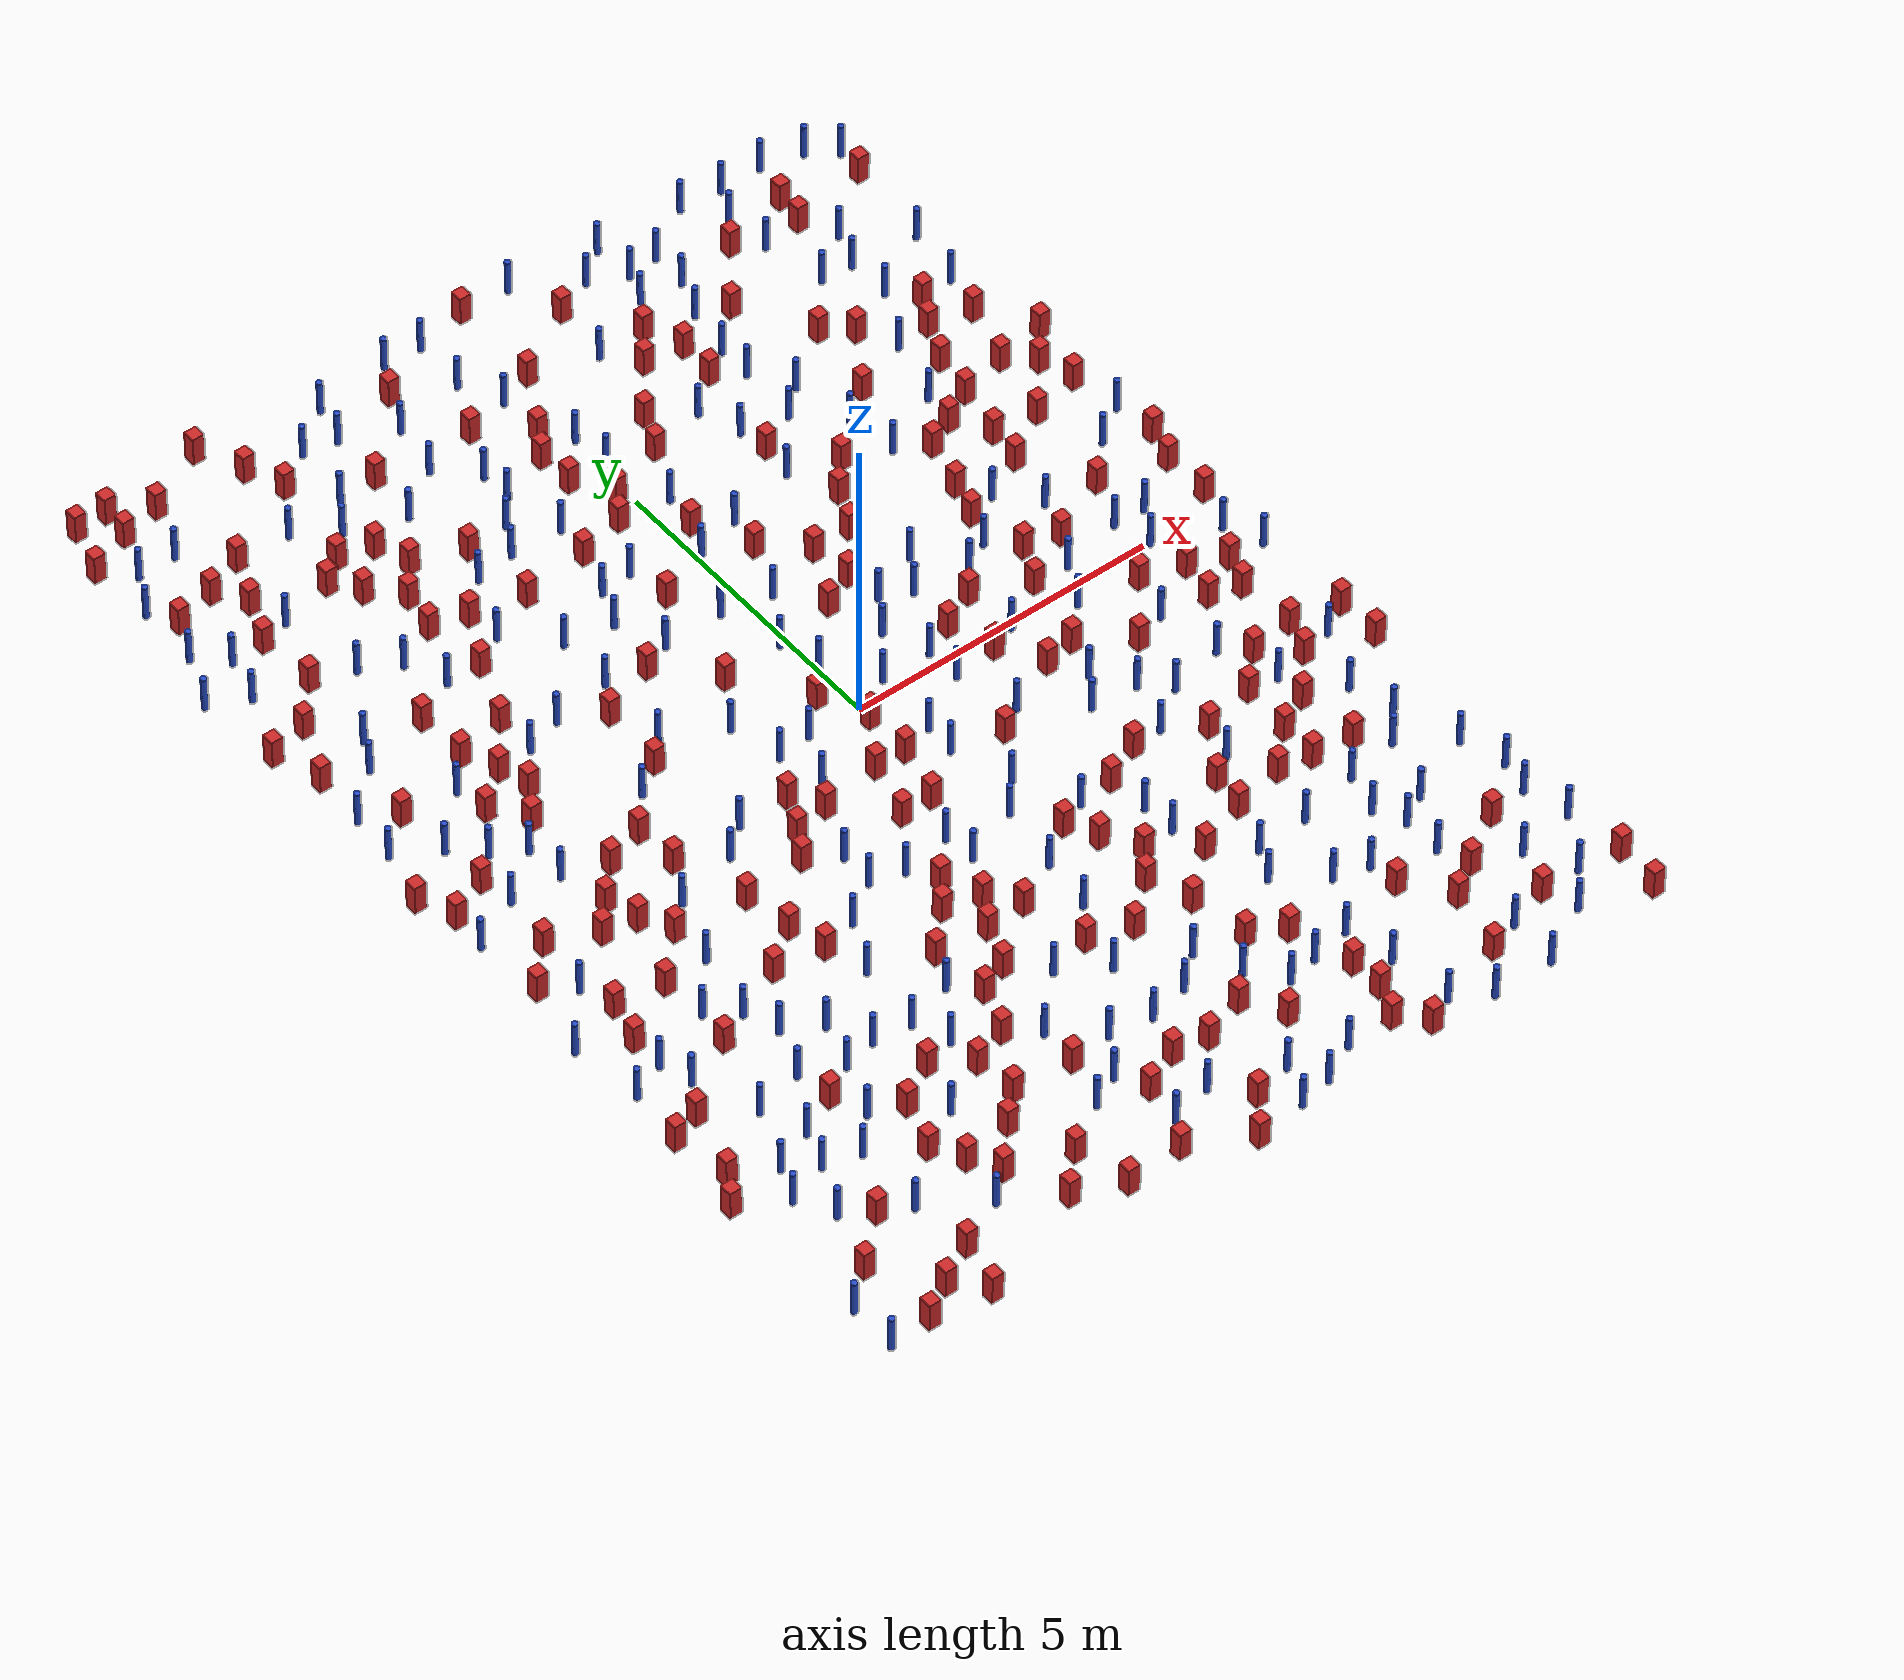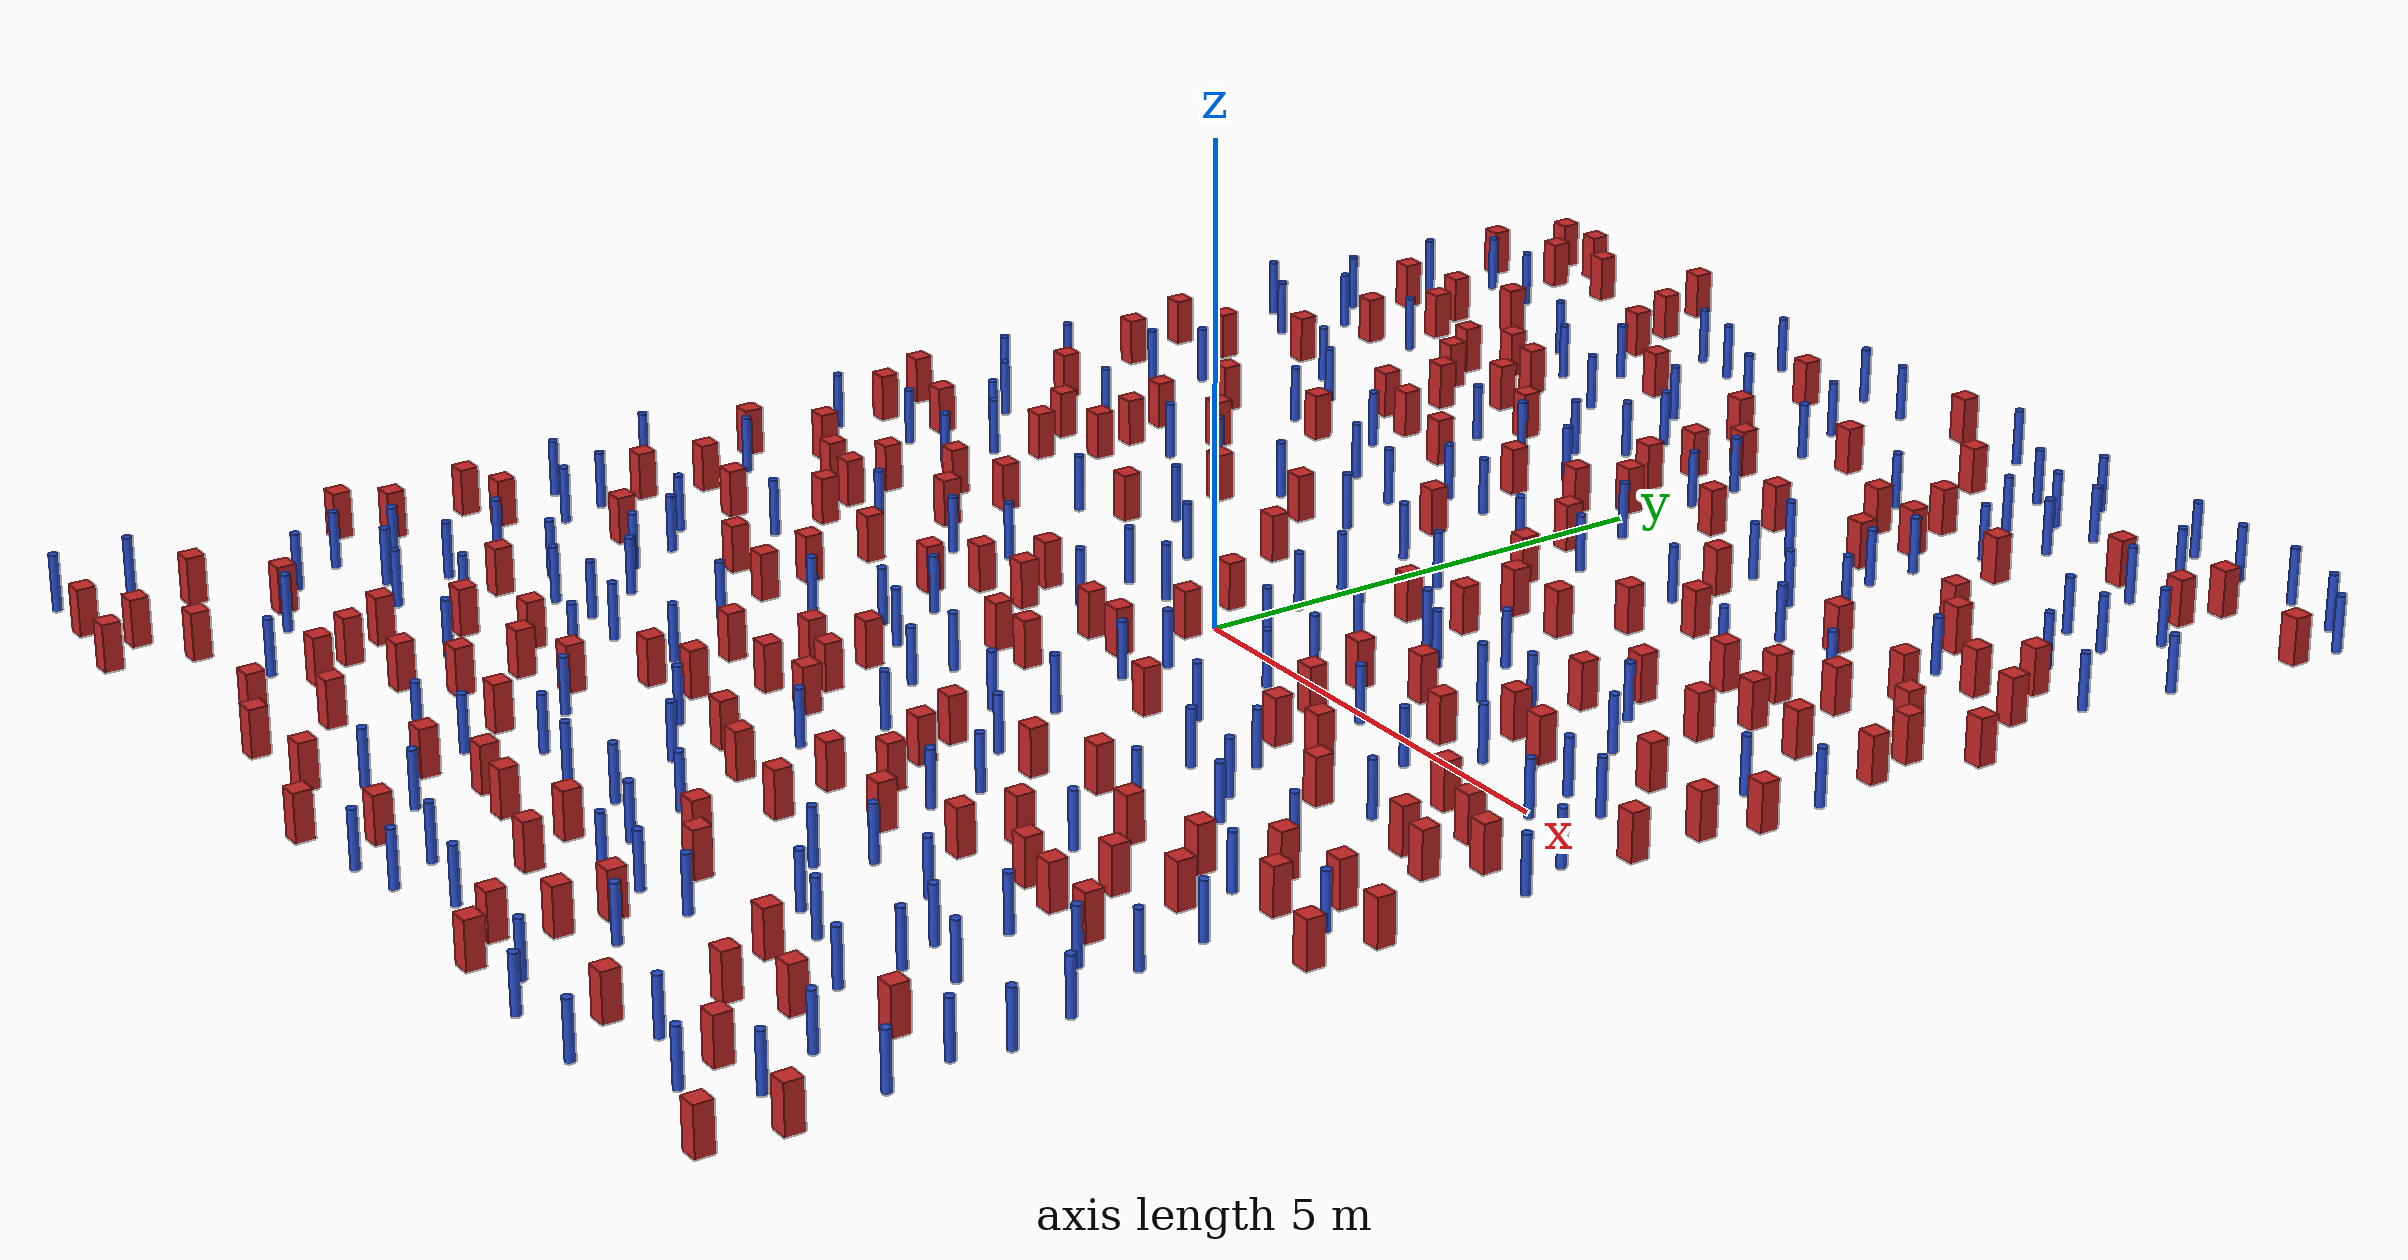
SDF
<sdf version="1.6">
  <model name="dense_54"><model name="square_post_obstacle0">
  <static>true</static>
  <pose frame="">0.259844190821 7.8261904194 1.91545236811e-07 -7.35059704564e-06 1.12565212e-07 2.39332434364e-05</pose>
  <link name="link">
    <pose frame="">0 0 0.25 0 -0 0</pose>
    <inertial>
      <mass>100</mass>
      <inertia>
        <ixx>0.166667</ixx>
        <ixy>0</ixy>
        <ixz>0</ixz>
        <iyy>0.166667</iyy>
        <iyz>0</iyz>
        <izz>0.166667</izz>
      </inertia>
    </inertial>
    <collision name="collision">
      <geometry>
        <box>
          <size>.2 .2 .5</size>
        </box>
      </geometry>
      <max_contacts>10</max_contacts>
      <surface>
        <contact>
          <ode/>
        </contact>
        <bounce/>
        <friction>
          <torsional>
            <ode/>
          </torsional>
          <ode/>
        </friction>
      </surface>
    </collision>
    <visual name="visual">
      <geometry>
        <box>
          <size>.2 .2 .5</size>
        </box>
      </geometry>
      <material>
        <script>
          <name>Gazebo/Red</name>
          <uri>file://media/materials/scripts/gazebo.material</uri>
        </script>
      </material>
    </visual>
    <self_collide>0</self_collide>
    <kinematic>0</kinematic>
  </link>
</model>
<model name="square_post_obstacle1">
  <static>true</static>
  <pose frame="">-5.93586615701 9.30533542181 1.91545236811e-07 -7.35059704564e-06 1.12565212e-07 2.39332434364e-05</pose>
  <link name="link">
    <pose frame="">0 0 0.25 0 -0 0</pose>
    <inertial>
      <mass>100</mass>
      <inertia>
        <ixx>0.166667</ixx>
        <ixy>0</ixy>
        <ixz>0</ixz>
        <iyy>0.166667</iyy>
        <iyz>0</iyz>
        <izz>0.166667</izz>
      </inertia>
    </inertial>
    <collision name="collision">
      <geometry>
        <box>
          <size>.2 .2 .5</size>
        </box>
      </geometry>
      <max_contacts>10</max_contacts>
      <surface>
        <contact>
          <ode/>
        </contact>
        <bounce/>
        <friction>
          <torsional>
            <ode/>
          </torsional>
          <ode/>
        </friction>
      </surface>
    </collision>
    <visual name="visual">
      <geometry>
        <box>
          <size>.2 .2 .5</size>
        </box>
      </geometry>
      <material>
        <script>
          <name>Gazebo/Red</name>
          <uri>file://media/materials/scripts/gazebo.material</uri>
        </script>
      </material>
    </visual>
    <self_collide>0</self_collide>
    <kinematic>0</kinematic>
  </link>
</model>
<model name="pole_obstacle0">
  <static>true</static>
  <pose frame="">3.56533259858 -0.322572710394 7.38925637345e-09 -8.471706928e-08 1.24976765172e-08 -1.74513093013e-07</pose>
  <link name="link">
  <pose frame="">0 0 0.3 0 -0 0</pose>
    <inertial>
      <mass>1</mass>
      <inertia>
        <ixx>0.145833</ixx>
        <ixy>0</ixy>
        <ixz>0</ixz>
        <iyy>0.145833</iyy>
        <iyz>0</iyz>
        <izz>0.125</izz>
      </inertia>
    </inertial>
    <collision name="collision">
      <geometry>
        <cylinder>
          <radius>0.05</radius>
          <length>.6</length>
        </cylinder>
      </geometry>
      <max_contacts>10</max_contacts>
      <surface>
        <contact>
          <ode/>
        </contact>
        <bounce/>
        <friction>
          <torsional>
            <ode/>
          </torsional>
          <ode/>
        </friction>
      </surface>
    </collision>
    <visual name="visual">
      <geometry>
        <cylinder>
          <radius>0.05</radius>
          <length>.6</length>
        </cylinder>
      </geometry>
      <material>
        <script>
          <name>Gazebo/Blue</name>
          <uri>file://media/materials/scripts/gazebo.material</uri>
        </script>
      </material>
    </visual>
    <self_collide>0</self_collide>
    <kinematic>0</kinematic>
  </link>
</model>
<model name="square_post_obstacle2">
  <static>true</static>
  <pose frame="">3.42907866746 1.85608255959 1.91545236811e-07 -7.35059704564e-06 1.12565212e-07 2.39332434364e-05</pose>
  <link name="link">
    <pose frame="">0 0 0.25 0 -0 0</pose>
    <inertial>
      <mass>100</mass>
      <inertia>
        <ixx>0.166667</ixx>
        <ixy>0</ixy>
        <ixz>0</ixz>
        <iyy>0.166667</iyy>
        <iyz>0</iyz>
        <izz>0.166667</izz>
      </inertia>
    </inertial>
    <collision name="collision">
      <geometry>
        <box>
          <size>.2 .2 .5</size>
        </box>
      </geometry>
      <max_contacts>10</max_contacts>
      <surface>
        <contact>
          <ode/>
        </contact>
        <bounce/>
        <friction>
          <torsional>
            <ode/>
          </torsional>
          <ode/>
        </friction>
      </surface>
    </collision>
    <visual name="visual">
      <geometry>
        <box>
          <size>.2 .2 .5</size>
        </box>
      </geometry>
      <material>
        <script>
          <name>Gazebo/Red</name>
          <uri>file://media/materials/scripts/gazebo.material</uri>
        </script>
      </material>
    </visual>
    <self_collide>0</self_collide>
    <kinematic>0</kinematic>
  </link>
</model>
<model name="pole_obstacle1">
  <static>true</static>
  <pose frame="">1.48350776402 1.47035718474 7.38925637345e-09 -8.471706928e-08 1.24976765079e-08 -1.74513093017e-07</pose>
  <link name="link">
  <pose frame="">0 0 0.3 0 -0 0</pose>
    <inertial>
      <mass>1</mass>
      <inertia>
        <ixx>0.145833</ixx>
        <ixy>0</ixy>
        <ixz>0</ixz>
        <iyy>0.145833</iyy>
        <iyz>0</iyz>
        <izz>0.125</izz>
      </inertia>
    </inertial>
    <collision name="collision">
      <geometry>
        <cylinder>
          <radius>0.05</radius>
          <length>.6</length>
        </cylinder>
      </geometry>
      <max_contacts>10</max_contacts>
      <surface>
        <contact>
          <ode/>
        </contact>
        <bounce/>
        <friction>
          <torsional>
            <ode/>
          </torsional>
          <ode/>
        </friction>
      </surface>
    </collision>
    <visual name="visual">
      <geometry>
        <cylinder>
          <radius>0.05</radius>
          <length>.6</length>
        </cylinder>
      </geometry>
      <material>
        <script>
          <name>Gazebo/Blue</name>
          <uri>file://media/materials/scripts/gazebo.material</uri>
        </script>
      </material>
    </visual>
    <self_collide>0</self_collide>
    <kinematic>0</kinematic>
  </link>
</model>
<model name="square_post_obstacle3">
  <static>true</static>
  <pose frame="">3.30021493687 0.299328565392 1.91545236811e-07 -7.35059704564e-06 1.12565212e-07 2.39332434364e-05</pose>
  <link name="link">
    <pose frame="">0 0 0.25 0 -0 0</pose>
    <inertial>
      <mass>100</mass>
      <inertia>
        <ixx>0.166667</ixx>
        <ixy>0</ixy>
        <ixz>0</ixz>
        <iyy>0.166667</iyy>
        <iyz>0</iyz>
        <izz>0.166667</izz>
      </inertia>
    </inertial>
    <collision name="collision">
      <geometry>
        <box>
          <size>.2 .2 .5</size>
        </box>
      </geometry>
      <max_contacts>10</max_contacts>
      <surface>
        <contact>
          <ode/>
        </contact>
        <bounce/>
        <friction>
          <torsional>
            <ode/>
          </torsional>
          <ode/>
        </friction>
      </surface>
    </collision>
    <visual name="visual">
      <geometry>
        <box>
          <size>.2 .2 .5</size>
        </box>
      </geometry>
      <material>
        <script>
          <name>Gazebo/Red</name>
          <uri>file://media/materials/scripts/gazebo.material</uri>
        </script>
      </material>
    </visual>
    <self_collide>0</self_collide>
    <kinematic>0</kinematic>
  </link>
</model>
<model name="pole_obstacle2">
  <static>true</static>
  <pose frame="">1.31746987575 7.5548257492 7.38925637345e-09 -8.47170692799e-08 1.24976765033e-08 -1.74513093018e-07</pose>
  <link name="link">
  <pose frame="">0 0 0.3 0 -0 0</pose>
    <inertial>
      <mass>1</mass>
      <inertia>
        <ixx>0.145833</ixx>
        <ixy>0</ixy>
        <ixz>0</ixz>
        <iyy>0.145833</iyy>
        <iyz>0</iyz>
        <izz>0.125</izz>
      </inertia>
    </inertial>
    <collision name="collision">
      <geometry>
        <cylinder>
          <radius>0.05</radius>
          <length>.6</length>
        </cylinder>
      </geometry>
      <max_contacts>10</max_contacts>
      <surface>
        <contact>
          <ode/>
        </contact>
        <bounce/>
        <friction>
          <torsional>
            <ode/>
          </torsional>
          <ode/>
        </friction>
      </surface>
    </collision>
    <visual name="visual">
      <geometry>
        <cylinder>
          <radius>0.05</radius>
          <length>.6</length>
        </cylinder>
      </geometry>
      <material>
        <script>
          <name>Gazebo/Blue</name>
          <uri>file://media/materials/scripts/gazebo.material</uri>
        </script>
      </material>
    </visual>
    <self_collide>0</self_collide>
    <kinematic>0</kinematic>
  </link>
</model>
<model name="pole_obstacle3">
  <static>true</static>
  <pose frame="">0.143664078057 -9.25991751499 7.38925637345e-09 -8.47170692796e-08 1.2497676475e-08 -1.74513093035e-07</pose>
  <link name="link">
  <pose frame="">0 0 0.3 0 -0 0</pose>
    <inertial>
      <mass>1</mass>
      <inertia>
        <ixx>0.145833</ixx>
        <ixy>0</ixy>
        <ixz>0</ixz>
        <iyy>0.145833</iyy>
        <iyz>0</iyz>
        <izz>0.125</izz>
      </inertia>
    </inertial>
    <collision name="collision">
      <geometry>
        <cylinder>
          <radius>0.05</radius>
          <length>.6</length>
        </cylinder>
      </geometry>
      <max_contacts>10</max_contacts>
      <surface>
        <contact>
          <ode/>
        </contact>
        <bounce/>
        <friction>
          <torsional>
            <ode/>
          </torsional>
          <ode/>
        </friction>
      </surface>
    </collision>
    <visual name="visual">
      <geometry>
        <cylinder>
          <radius>0.05</radius>
          <length>.6</length>
        </cylinder>
      </geometry>
      <material>
        <script>
          <name>Gazebo/Blue</name>
          <uri>file://media/materials/scripts/gazebo.material</uri>
        </script>
      </material>
    </visual>
    <self_collide>0</self_collide>
    <kinematic>0</kinematic>
  </link>
</model>
<model name="square_post_obstacle4">
  <static>true</static>
  <pose frame="">-4.29412460987 9.49368886401 1.91545236811e-07 -7.35059704564e-06 1.12565212e-07 2.39332434364e-05</pose>
  <link name="link">
    <pose frame="">0 0 0.25 0 -0 0</pose>
    <inertial>
      <mass>100</mass>
      <inertia>
        <ixx>0.166667</ixx>
        <ixy>0</ixy>
        <ixz>0</ixz>
        <iyy>0.166667</iyy>
        <iyz>0</iyz>
        <izz>0.166667</izz>
      </inertia>
    </inertial>
    <collision name="collision">
      <geometry>
        <box>
          <size>.2 .2 .5</size>
        </box>
      </geometry>
      <max_contacts>10</max_contacts>
      <surface>
        <contact>
          <ode/>
        </contact>
        <bounce/>
        <friction>
          <torsional>
            <ode/>
          </torsional>
          <ode/>
        </friction>
      </surface>
    </collision>
    <visual name="visual">
      <geometry>
        <box>
          <size>.2 .2 .5</size>
        </box>
      </geometry>
      <material>
        <script>
          <name>Gazebo/Red</name>
          <uri>file://media/materials/scripts/gazebo.material</uri>
        </script>
      </material>
    </visual>
    <self_collide>0</self_collide>
    <kinematic>0</kinematic>
  </link>
</model>
<model name="square_post_obstacle5">
  <static>true</static>
  <pose frame="">-2.03807652556 -4.21713258251 1.91545236811e-07 -7.35059704564e-06 1.12565212e-07 2.39332434364e-05</pose>
  <link name="link">
    <pose frame="">0 0 0.25 0 -0 0</pose>
    <inertial>
      <mass>100</mass>
      <inertia>
        <ixx>0.166667</ixx>
        <ixy>0</ixy>
        <ixz>0</ixz>
        <iyy>0.166667</iyy>
        <iyz>0</iyz>
        <izz>0.166667</izz>
      </inertia>
    </inertial>
    <collision name="collision">
      <geometry>
        <box>
          <size>.2 .2 .5</size>
        </box>
      </geometry>
      <max_contacts>10</max_contacts>
      <surface>
        <contact>
          <ode/>
        </contact>
        <bounce/>
        <friction>
          <torsional>
            <ode/>
          </torsional>
          <ode/>
        </friction>
      </surface>
    </collision>
    <visual name="visual">
      <geometry>
        <box>
          <size>.2 .2 .5</size>
        </box>
      </geometry>
      <material>
        <script>
          <name>Gazebo/Red</name>
          <uri>file://media/materials/scripts/gazebo.material</uri>
        </script>
      </material>
    </visual>
    <self_collide>0</self_collide>
    <kinematic>0</kinematic>
  </link>
</model>
<model name="square_post_obstacle6">
  <static>true</static>
  <pose frame="">-1.9497129896 -5.14376126057 1.91545236811e-07 -7.35059704564e-06 1.12565212e-07 2.39332434364e-05</pose>
  <link name="link">
    <pose frame="">0 0 0.25 0 -0 0</pose>
    <inertial>
      <mass>100</mass>
      <inertia>
        <ixx>0.166667</ixx>
        <ixy>0</ixy>
        <ixz>0</ixz>
        <iyy>0.166667</iyy>
        <iyz>0</iyz>
        <izz>0.166667</izz>
      </inertia>
    </inertial>
    <collision name="collision">
      <geometry>
        <box>
          <size>.2 .2 .5</size>
        </box>
      </geometry>
      <max_contacts>10</max_contacts>
      <surface>
        <contact>
          <ode/>
        </contact>
        <bounce/>
        <friction>
          <torsional>
            <ode/>
          </torsional>
          <ode/>
        </friction>
      </surface>
    </collision>
    <visual name="visual">
      <geometry>
        <box>
          <size>.2 .2 .5</size>
        </box>
      </geometry>
      <material>
        <script>
          <name>Gazebo/Red</name>
          <uri>file://media/materials/scripts/gazebo.material</uri>
        </script>
      </material>
    </visual>
    <self_collide>0</self_collide>
    <kinematic>0</kinematic>
  </link>
</model>
<model name="pole_obstacle4">
  <static>true</static>
  <pose frame="">-6.60914330545 7.4561722727 7.38925637345e-09 -8.47170692796e-08 1.24976764786e-08 -1.74513093032e-07</pose>
  <link name="link">
  <pose frame="">0 0 0.3 0 -0 0</pose>
    <inertial>
      <mass>1</mass>
      <inertia>
        <ixx>0.145833</ixx>
        <ixy>0</ixy>
        <ixz>0</ixz>
        <iyy>0.145833</iyy>
        <iyz>0</iyz>
        <izz>0.125</izz>
      </inertia>
    </inertial>
    <collision name="collision">
      <geometry>
        <cylinder>
          <radius>0.05</radius>
          <length>.6</length>
        </cylinder>
      </geometry>
      <max_contacts>10</max_contacts>
      <surface>
        <contact>
          <ode/>
        </contact>
        <bounce/>
        <friction>
          <torsional>
            <ode/>
          </torsional>
          <ode/>
        </friction>
      </surface>
    </collision>
    <visual name="visual">
      <geometry>
        <cylinder>
          <radius>0.05</radius>
          <length>.6</length>
        </cylinder>
      </geometry>
      <material>
        <script>
          <name>Gazebo/Blue</name>
          <uri>file://media/materials/scripts/gazebo.material</uri>
        </script>
      </material>
    </visual>
    <self_collide>0</self_collide>
    <kinematic>0</kinematic>
  </link>
</model>
<model name="pole_obstacle5">
  <static>true</static>
  <pose frame="">-2.38773180387 9.13215212733 7.38925637345e-09 -8.47170692793e-08 1.24976764408e-08 -1.74513093041e-07</pose>
  <link name="link">
  <pose frame="">0 0 0.3 0 -0 0</pose>
    <inertial>
      <mass>1</mass>
      <inertia>
        <ixx>0.145833</ixx>
        <ixy>0</ixy>
        <ixz>0</ixz>
        <iyy>0.145833</iyy>
        <iyz>0</iyz>
        <izz>0.125</izz>
      </inertia>
    </inertial>
    <collision name="collision">
      <geometry>
        <cylinder>
          <radius>0.05</radius>
          <length>.6</length>
        </cylinder>
      </geometry>
      <max_contacts>10</max_contacts>
      <surface>
        <contact>
          <ode/>
        </contact>
        <bounce/>
        <friction>
          <torsional>
            <ode/>
          </torsional>
          <ode/>
        </friction>
      </surface>
    </collision>
    <visual name="visual">
      <geometry>
        <cylinder>
          <radius>0.05</radius>
          <length>.6</length>
        </cylinder>
      </geometry>
      <material>
        <script>
          <name>Gazebo/Blue</name>
          <uri>file://media/materials/scripts/gazebo.material</uri>
        </script>
      </material>
    </visual>
    <self_collide>0</self_collide>
    <kinematic>0</kinematic>
  </link>
</model>
<model name="square_post_obstacle7">
  <static>true</static>
  <pose frame="">-3.95913503365 8.76705724128 1.91545236811e-07 -7.35059704564e-06 1.12565212e-07 2.39332434364e-05</pose>
  <link name="link">
    <pose frame="">0 0 0.25 0 -0 0</pose>
    <inertial>
      <mass>100</mass>
      <inertia>
        <ixx>0.166667</ixx>
        <ixy>0</ixy>
        <ixz>0</ixz>
        <iyy>0.166667</iyy>
        <iyz>0</iyz>
        <izz>0.166667</izz>
      </inertia>
    </inertial>
    <collision name="collision">
      <geometry>
        <box>
          <size>.2 .2 .5</size>
        </box>
      </geometry>
      <max_contacts>10</max_contacts>
      <surface>
        <contact>
          <ode/>
        </contact>
        <bounce/>
        <friction>
          <torsional>
            <ode/>
          </torsional>
          <ode/>
        </friction>
      </surface>
    </collision>
    <visual name="visual">
      <geometry>
        <box>
          <size>.2 .2 .5</size>
        </box>
      </geometry>
      <material>
        <script>
          <name>Gazebo/Red</name>
          <uri>file://media/materials/scripts/gazebo.material</uri>
        </script>
      </material>
    </visual>
    <self_collide>0</self_collide>
    <kinematic>0</kinematic>
  </link>
</model>
<model name="square_post_obstacle8">
  <static>true</static>
  <pose frame="">2.43075801813 -2.92088235214 1.91545236811e-07 -7.35059704564e-06 1.12565212e-07 2.39332434364e-05</pose>
  <link name="link">
    <pose frame="">0 0 0.25 0 -0 0</pose>
    <inertial>
      <mass>100</mass>
      <inertia>
        <ixx>0.166667</ixx>
        <ixy>0</ixy>
        <ixz>0</ixz>
        <iyy>0.166667</iyy>
        <iyz>0</iyz>
        <izz>0.166667</izz>
      </inertia>
    </inertial>
    <collision name="collision">
      <geometry>
        <box>
          <size>.2 .2 .5</size>
        </box>
      </geometry>
      <max_contacts>10</max_contacts>
      <surface>
        <contact>
          <ode/>
        </contact>
        <bounce/>
        <friction>
          <torsional>
            <ode/>
          </torsional>
          <ode/>
        </friction>
      </surface>
    </collision>
    <visual name="visual">
      <geometry>
        <box>
          <size>.2 .2 .5</size>
        </box>
      </geometry>
      <material>
        <script>
          <name>Gazebo/Red</name>
          <uri>file://media/materials/scripts/gazebo.material</uri>
        </script>
      </material>
    </visual>
    <self_collide>0</self_collide>
    <kinematic>0</kinematic>
  </link>
</model>
<model name="pole_obstacle6">
  <static>true</static>
  <pose frame="">6.30852490096 -1.00948622064 7.38925637345e-09 -8.471706928e-08 1.24976765101e-08 -1.74513093015e-07</pose>
  <link name="link">
  <pose frame="">0 0 0.3 0 -0 0</pose>
    <inertial>
      <mass>1</mass>
      <inertia>
        <ixx>0.145833</ixx>
        <ixy>0</ixy>
        <ixz>0</ixz>
        <iyy>0.145833</iyy>
        <iyz>0</iyz>
        <izz>0.125</izz>
      </inertia>
    </inertial>
    <collision name="collision">
      <geometry>
        <cylinder>
          <radius>0.05</radius>
          <length>.6</length>
        </cylinder>
      </geometry>
      <max_contacts>10</max_contacts>
      <surface>
        <contact>
          <ode/>
        </contact>
        <bounce/>
        <friction>
          <torsional>
            <ode/>
          </torsional>
          <ode/>
        </friction>
      </surface>
    </collision>
    <visual name="visual">
      <geometry>
        <cylinder>
          <radius>0.05</radius>
          <length>.6</length>
        </cylinder>
      </geometry>
      <material>
        <script>
          <name>Gazebo/Blue</name>
          <uri>file://media/materials/scripts/gazebo.material</uri>
        </script>
      </material>
    </visual>
    <self_collide>0</self_collide>
    <kinematic>0</kinematic>
  </link>
</model>
<model name="pole_obstacle7">
  <static>true</static>
  <pose frame="">4.00344075744 9.1748586009 7.38925637345e-09 -8.47170692799e-08 1.24976765044e-08 -1.74513093018e-07</pose>
  <link name="link">
  <pose frame="">0 0 0.3 0 -0 0</pose>
    <inertial>
      <mass>1</mass>
      <inertia>
        <ixx>0.145833</ixx>
        <ixy>0</ixy>
        <ixz>0</ixz>
        <iyy>0.145833</iyy>
        <iyz>0</iyz>
        <izz>0.125</izz>
      </inertia>
    </inertial>
    <collision name="collision">
      <geometry>
        <cylinder>
          <radius>0.05</radius>
          <length>.6</length>
        </cylinder>
      </geometry>
      <max_contacts>10</max_contacts>
      <surface>
        <contact>
          <ode/>
        </contact>
        <bounce/>
        <friction>
          <torsional>
            <ode/>
          </torsional>
          <ode/>
        </friction>
      </surface>
    </collision>
    <visual name="visual">
      <geometry>
        <cylinder>
          <radius>0.05</radius>
          <length>.6</length>
        </cylinder>
      </geometry>
      <material>
        <script>
          <name>Gazebo/Blue</name>
          <uri>file://media/materials/scripts/gazebo.material</uri>
        </script>
      </material>
    </visual>
    <self_collide>0</self_collide>
    <kinematic>0</kinematic>
  </link>
</model>
<model name="square_post_obstacle9">
  <static>true</static>
  <pose frame="">-1.20917109149 -4.29312356543 1.91545236811e-07 -7.35059704564e-06 1.12565212e-07 2.39332434364e-05</pose>
  <link name="link">
    <pose frame="">0 0 0.25 0 -0 0</pose>
    <inertial>
      <mass>100</mass>
      <inertia>
        <ixx>0.166667</ixx>
        <ixy>0</ixy>
        <ixz>0</ixz>
        <iyy>0.166667</iyy>
        <iyz>0</iyz>
        <izz>0.166667</izz>
      </inertia>
    </inertial>
    <collision name="collision">
      <geometry>
        <box>
          <size>.2 .2 .5</size>
        </box>
      </geometry>
      <max_contacts>10</max_contacts>
      <surface>
        <contact>
          <ode/>
        </contact>
        <bounce/>
        <friction>
          <torsional>
            <ode/>
          </torsional>
          <ode/>
        </friction>
      </surface>
    </collision>
    <visual name="visual">
      <geometry>
        <box>
          <size>.2 .2 .5</size>
        </box>
      </geometry>
      <material>
        <script>
          <name>Gazebo/Red</name>
          <uri>file://media/materials/scripts/gazebo.material</uri>
        </script>
      </material>
    </visual>
    <self_collide>0</self_collide>
    <kinematic>0</kinematic>
  </link>
</model>
<model name="square_post_obstacle10">
  <static>true</static>
  <pose frame="">-0.0478637047065 -0.286412599009 1.91545236811e-07 -7.35059704564e-06 1.12565212e-07 2.39332434364e-05</pose>
  <link name="link">
    <pose frame="">0 0 0.25 0 -0 0</pose>
    <inertial>
      <mass>100</mass>
      <inertia>
        <ixx>0.166667</ixx>
        <ixy>0</ixy>
        <ixz>0</ixz>
        <iyy>0.166667</iyy>
        <iyz>0</iyz>
        <izz>0.166667</izz>
      </inertia>
    </inertial>
    <collision name="collision">
      <geometry>
        <box>
          <size>.2 .2 .5</size>
        </box>
      </geometry>
      <max_contacts>10</max_contacts>
      <surface>
        <contact>
          <ode/>
        </contact>
        <bounce/>
        <friction>
          <torsional>
            <ode/>
          </torsional>
          <ode/>
        </friction>
      </surface>
    </collision>
    <visual name="visual">
      <geometry>
        <box>
          <size>.2 .2 .5</size>
        </box>
      </geometry>
      <material>
        <script>
          <name>Gazebo/Red</name>
          <uri>file://media/materials/scripts/gazebo.material</uri>
        </script>
      </material>
    </visual>
    <self_collide>0</self_collide>
    <kinematic>0</kinematic>
  </link>
</model>
<model name="square_post_obstacle11">
  <static>true</static>
  <pose frame="">-0.548768333741 5.81287290309 1.91545236811e-07 -7.35059704564e-06 1.12565212e-07 2.39332434364e-05</pose>
  <link name="link">
    <pose frame="">0 0 0.25 0 -0 0</pose>
    <inertial>
      <mass>100</mass>
      <inertia>
        <ixx>0.166667</ixx>
        <ixy>0</ixy>
        <ixz>0</ixz>
        <iyy>0.166667</iyy>
        <iyz>0</iyz>
        <izz>0.166667</izz>
      </inertia>
    </inertial>
    <collision name="collision">
      <geometry>
        <box>
          <size>.2 .2 .5</size>
        </box>
      </geometry>
      <max_contacts>10</max_contacts>
      <surface>
        <contact>
          <ode/>
        </contact>
        <bounce/>
        <friction>
          <torsional>
            <ode/>
          </torsional>
          <ode/>
        </friction>
      </surface>
    </collision>
    <visual name="visual">
      <geometry>
        <box>
          <size>.2 .2 .5</size>
        </box>
      </geometry>
      <material>
        <script>
          <name>Gazebo/Red</name>
          <uri>file://media/materials/scripts/gazebo.material</uri>
        </script>
      </material>
    </visual>
    <self_collide>0</self_collide>
    <kinematic>0</kinematic>
  </link>
</model>
<model name="square_post_obstacle12">
  <static>true</static>
  <pose frame="">5.5033230095 -1.52236215831 1.91545236811e-07 -7.35059704564e-06 1.12565212e-07 2.39332434364e-05</pose>
  <link name="link">
    <pose frame="">0 0 0.25 0 -0 0</pose>
    <inertial>
      <mass>100</mass>
      <inertia>
        <ixx>0.166667</ixx>
        <ixy>0</ixy>
        <ixz>0</ixz>
        <iyy>0.166667</iyy>
        <iyz>0</iyz>
        <izz>0.166667</izz>
      </inertia>
    </inertial>
    <collision name="collision">
      <geometry>
        <box>
          <size>.2 .2 .5</size>
        </box>
      </geometry>
      <max_contacts>10</max_contacts>
      <surface>
        <contact>
          <ode/>
        </contact>
        <bounce/>
        <friction>
          <torsional>
            <ode/>
          </torsional>
          <ode/>
        </friction>
      </surface>
    </collision>
    <visual name="visual">
      <geometry>
        <box>
          <size>.2 .2 .5</size>
        </box>
      </geometry>
      <material>
        <script>
          <name>Gazebo/Red</name>
          <uri>file://media/materials/scripts/gazebo.material</uri>
        </script>
      </material>
    </visual>
    <self_collide>0</self_collide>
    <kinematic>0</kinematic>
  </link>
</model>
<model name="square_post_obstacle13">
  <static>true</static>
  <pose frame="">-3.17438952228 -7.16347019154 1.91545236811e-07 -7.35059704564e-06 1.12565212e-07 2.39332434364e-05</pose>
  <link name="link">
    <pose frame="">0 0 0.25 0 -0 0</pose>
    <inertial>
      <mass>100</mass>
      <inertia>
        <ixx>0.166667</ixx>
        <ixy>0</ixy>
        <ixz>0</ixz>
        <iyy>0.166667</iyy>
        <iyz>0</iyz>
        <izz>0.166667</izz>
      </inertia>
    </inertial>
    <collision name="collision">
      <geometry>
        <box>
          <size>.2 .2 .5</size>
        </box>
      </geometry>
      <max_contacts>10</max_contacts>
      <surface>
        <contact>
          <ode/>
        </contact>
        <bounce/>
        <friction>
          <torsional>
            <ode/>
          </torsional>
          <ode/>
        </friction>
      </surface>
    </collision>
    <visual name="visual">
      <geometry>
        <box>
          <size>.2 .2 .5</size>
        </box>
      </geometry>
      <material>
        <script>
          <name>Gazebo/Red</name>
          <uri>file://media/materials/scripts/gazebo.material</uri>
        </script>
      </material>
    </visual>
    <self_collide>0</self_collide>
    <kinematic>0</kinematic>
  </link>
</model>
<model name="pole_obstacle8">
  <static>true</static>
  <pose frame="">-2.45714861951 2.50290941545 7.38925637345e-09 -8.47170692798e-08 1.24976764939e-08 -1.74513093025e-07</pose>
  <link name="link">
  <pose frame="">0 0 0.3 0 -0 0</pose>
    <inertial>
      <mass>1</mass>
      <inertia>
        <ixx>0.145833</ixx>
        <ixy>0</ixy>
        <ixz>0</ixz>
        <iyy>0.145833</iyy>
        <iyz>0</iyz>
        <izz>0.125</izz>
      </inertia>
    </inertial>
    <collision name="collision">
      <geometry>
        <cylinder>
          <radius>0.05</radius>
          <length>.6</length>
        </cylinder>
      </geometry>
      <max_contacts>10</max_contacts>
      <surface>
        <contact>
          <ode/>
        </contact>
        <bounce/>
        <friction>
          <torsional>
            <ode/>
          </torsional>
          <ode/>
        </friction>
      </surface>
    </collision>
    <visual name="visual">
      <geometry>
        <cylinder>
          <radius>0.05</radius>
          <length>.6</length>
        </cylinder>
      </geometry>
      <material>
        <script>
          <name>Gazebo/Blue</name>
          <uri>file://media/materials/scripts/gazebo.material</uri>
        </script>
      </material>
    </visual>
    <self_collide>0</self_collide>
    <kinematic>0</kinematic>
  </link>
</model>
<model name="square_post_obstacle14">
  <static>true</static>
  <pose frame="">-3.61993753713 3.78609269903 1.91545236811e-07 -7.35059704564e-06 1.12565212e-07 2.39332434364e-05</pose>
  <link name="link">
    <pose frame="">0 0 0.25 0 -0 0</pose>
    <inertial>
      <mass>100</mass>
      <inertia>
        <ixx>0.166667</ixx>
        <ixy>0</ixy>
        <ixz>0</ixz>
        <iyy>0.166667</iyy>
        <iyz>0</iyz>
        <izz>0.166667</izz>
      </inertia>
    </inertial>
    <collision name="collision">
      <geometry>
        <box>
          <size>.2 .2 .5</size>
        </box>
      </geometry>
      <max_contacts>10</max_contacts>
      <surface>
        <contact>
          <ode/>
        </contact>
        <bounce/>
        <friction>
          <torsional>
            <ode/>
          </torsional>
          <ode/>
        </friction>
      </surface>
    </collision>
    <visual name="visual">
      <geometry>
        <box>
          <size>.2 .2 .5</size>
        </box>
      </geometry>
      <material>
        <script>
          <name>Gazebo/Red</name>
          <uri>file://media/materials/scripts/gazebo.material</uri>
        </script>
      </material>
    </visual>
    <self_collide>0</self_collide>
    <kinematic>0</kinematic>
  </link>
</model>
<model name="square_post_obstacle15">
  <static>true</static>
  <pose frame="">3.60972141836 -7.06101439882 1.91545236811e-07 -7.35059704564e-06 1.12565212e-07 2.39332434364e-05</pose>
  <link name="link">
    <pose frame="">0 0 0.25 0 -0 0</pose>
    <inertial>
      <mass>100</mass>
      <inertia>
        <ixx>0.166667</ixx>
        <ixy>0</ixy>
        <ixz>0</ixz>
        <iyy>0.166667</iyy>
        <iyz>0</iyz>
        <izz>0.166667</izz>
      </inertia>
    </inertial>
    <collision name="collision">
      <geometry>
        <box>
          <size>.2 .2 .5</size>
        </box>
      </geometry>
      <max_contacts>10</max_contacts>
      <surface>
        <contact>
          <ode/>
        </contact>
        <bounce/>
        <friction>
          <torsional>
            <ode/>
          </torsional>
          <ode/>
        </friction>
      </surface>
    </collision>
    <visual name="visual">
      <geometry>
        <box>
          <size>.2 .2 .5</size>
        </box>
      </geometry>
      <material>
        <script>
          <name>Gazebo/Red</name>
          <uri>file://media/materials/scripts/gazebo.material</uri>
        </script>
      </material>
    </visual>
    <self_collide>0</self_collide>
    <kinematic>0</kinematic>
  </link>
</model>
<model name="square_post_obstacle16">
  <static>true</static>
  <pose frame="">-3.17282569235 4.62792643698 1.91545236811e-07 -7.35059704564e-06 1.12565212e-07 2.39332434364e-05</pose>
  <link name="link">
    <pose frame="">0 0 0.25 0 -0 0</pose>
    <inertial>
      <mass>100</mass>
      <inertia>
        <ixx>0.166667</ixx>
        <ixy>0</ixy>
        <ixz>0</ixz>
        <iyy>0.166667</iyy>
        <iyz>0</iyz>
        <izz>0.166667</izz>
      </inertia>
    </inertial>
    <collision name="collision">
      <geometry>
        <box>
          <size>.2 .2 .5</size>
        </box>
      </geometry>
      <max_contacts>10</max_contacts>
      <surface>
        <contact>
          <ode/>
        </contact>
        <bounce/>
        <friction>
          <torsional>
            <ode/>
          </torsional>
          <ode/>
        </friction>
      </surface>
    </collision>
    <visual name="visual">
      <geometry>
        <box>
          <size>.2 .2 .5</size>
        </box>
      </geometry>
      <material>
        <script>
          <name>Gazebo/Red</name>
          <uri>file://media/materials/scripts/gazebo.material</uri>
        </script>
      </material>
    </visual>
    <self_collide>0</self_collide>
    <kinematic>0</kinematic>
  </link>
</model>
<model name="pole_obstacle9">
  <static>true</static>
  <pose frame="">-6.6953918444 -0.285240140767 7.38925637345e-09 -8.47170692801e-08 1.24976765176e-08 -1.74513093013e-07</pose>
  <link name="link">
  <pose frame="">0 0 0.3 0 -0 0</pose>
    <inertial>
      <mass>1</mass>
      <inertia>
        <ixx>0.145833</ixx>
        <ixy>0</ixy>
        <ixz>0</ixz>
        <iyy>0.145833</iyy>
        <iyz>0</iyz>
        <izz>0.125</izz>
      </inertia>
    </inertial>
    <collision name="collision">
      <geometry>
        <cylinder>
          <radius>0.05</radius>
          <length>.6</length>
        </cylinder>
      </geometry>
      <max_contacts>10</max_contacts>
      <surface>
        <contact>
          <ode/>
        </contact>
        <bounce/>
        <friction>
          <torsional>
            <ode/>
          </torsional>
          <ode/>
        </friction>
      </surface>
    </collision>
    <visual name="visual">
      <geometry>
        <cylinder>
          <radius>0.05</radius>
          <length>.6</length>
        </cylinder>
      </geometry>
      <material>
        <script>
          <name>Gazebo/Blue</name>
          <uri>file://media/materials/scripts/gazebo.material</uri>
        </script>
      </material>
    </visual>
    <self_collide>0</self_collide>
    <kinematic>0</kinematic>
  </link>
</model>
<model name="square_post_obstacle17">
  <static>true</static>
  <pose frame="">-5.53849942536 -8.81817202763 1.91545236811e-07 -7.35059704564e-06 1.12565212e-07 2.39332434364e-05</pose>
  <link name="link">
    <pose frame="">0 0 0.25 0 -0 0</pose>
    <inertial>
      <mass>100</mass>
      <inertia>
        <ixx>0.166667</ixx>
        <ixy>0</ixy>
        <ixz>0</ixz>
        <iyy>0.166667</iyy>
        <iyz>0</iyz>
        <izz>0.166667</izz>
      </inertia>
    </inertial>
    <collision name="collision">
      <geometry>
        <box>
          <size>.2 .2 .5</size>
        </box>
      </geometry>
      <max_contacts>10</max_contacts>
      <surface>
        <contact>
          <ode/>
        </contact>
        <bounce/>
        <friction>
          <torsional>
            <ode/>
          </torsional>
          <ode/>
        </friction>
      </surface>
    </collision>
    <visual name="visual">
      <geometry>
        <box>
          <size>.2 .2 .5</size>
        </box>
      </geometry>
      <material>
        <script>
          <name>Gazebo/Red</name>
          <uri>file://media/materials/scripts/gazebo.material</uri>
        </script>
      </material>
    </visual>
    <self_collide>0</self_collide>
    <kinematic>0</kinematic>
  </link>
</model>
<model name="square_post_obstacle18">
  <static>true</static>
  <pose frame="">-3.99102402222 -7.31175165487 1.91545236811e-07 -7.35059704564e-06 1.12565212e-07 2.39332434364e-05</pose>
  <link name="link">
    <pose frame="">0 0 0.25 0 -0 0</pose>
    <inertial>
      <mass>100</mass>
      <inertia>
        <ixx>0.166667</ixx>
        <ixy>0</ixy>
        <ixz>0</ixz>
        <iyy>0.166667</iyy>
        <iyz>0</iyz>
        <izz>0.166667</izz>
      </inertia>
    </inertial>
    <collision name="collision">
      <geometry>
        <box>
          <size>.2 .2 .5</size>
        </box>
      </geometry>
      <max_contacts>10</max_contacts>
      <surface>
        <contact>
          <ode/>
        </contact>
        <bounce/>
        <friction>
          <torsional>
            <ode/>
          </torsional>
          <ode/>
        </friction>
      </surface>
    </collision>
    <visual name="visual">
      <geometry>
        <box>
          <size>.2 .2 .5</size>
        </box>
      </geometry>
      <material>
        <script>
          <name>Gazebo/Red</name>
          <uri>file://media/materials/scripts/gazebo.material</uri>
        </script>
      </material>
    </visual>
    <self_collide>0</self_collide>
    <kinematic>0</kinematic>
  </link>
</model>
<model name="pole_obstacle10">
  <static>true</static>
  <pose frame="">-2.53055968332 -3.03960977382 7.38925637345e-09 -8.47170692798e-08 1.24976764939e-08 -1.74513093025e-07</pose>
  <link name="link">
  <pose frame="">0 0 0.3 0 -0 0</pose>
    <inertial>
      <mass>1</mass>
      <inertia>
        <ixx>0.145833</ixx>
        <ixy>0</ixy>
        <ixz>0</ixz>
        <iyy>0.145833</iyy>
        <iyz>0</iyz>
        <izz>0.125</izz>
      </inertia>
    </inertial>
    <collision name="collision">
      <geometry>
        <cylinder>
          <radius>0.05</radius>
          <length>.6</length>
        </cylinder>
      </geometry>
      <max_contacts>10</max_contacts>
      <surface>
        <contact>
          <ode/>
        </contact>
        <bounce/>
        <friction>
          <torsional>
            <ode/>
          </torsional>
          <ode/>
        </friction>
      </surface>
    </collision>
    <visual name="visual">
      <geometry>
        <cylinder>
          <radius>0.05</radius>
          <length>.6</length>
        </cylinder>
      </geometry>
      <material>
        <script>
          <name>Gazebo/Blue</name>
          <uri>file://media/materials/scripts/gazebo.material</uri>
        </script>
      </material>
    </visual>
    <self_collide>0</self_collide>
    <kinematic>0</kinematic>
  </link>
</model>
<model name="square_post_obstacle19">
  <static>true</static>
  <pose frame="">-2.56783436502 -8.94946485661 1.91545236811e-07 -7.35059704564e-06 1.12565212e-07 2.39332434364e-05</pose>
  <link name="link">
    <pose frame="">0 0 0.25 0 -0 0</pose>
    <inertial>
      <mass>100</mass>
      <inertia>
        <ixx>0.166667</ixx>
        <ixy>0</ixy>
        <ixz>0</ixz>
        <iyy>0.166667</iyy>
        <iyz>0</iyz>
        <izz>0.166667</izz>
      </inertia>
    </inertial>
    <collision name="collision">
      <geometry>
        <box>
          <size>.2 .2 .5</size>
        </box>
      </geometry>
      <max_contacts>10</max_contacts>
      <surface>
        <contact>
          <ode/>
        </contact>
        <bounce/>
        <friction>
          <torsional>
            <ode/>
          </torsional>
          <ode/>
        </friction>
      </surface>
    </collision>
    <visual name="visual">
      <geometry>
        <box>
          <size>.2 .2 .5</size>
        </box>
      </geometry>
      <material>
        <script>
          <name>Gazebo/Red</name>
          <uri>file://media/materials/scripts/gazebo.material</uri>
        </script>
      </material>
    </visual>
    <self_collide>0</self_collide>
    <kinematic>0</kinematic>
  </link>
</model>
<model name="pole_obstacle11">
  <static>true</static>
  <pose frame="">0.472975062217 -1.38549482698 7.38925637345e-09 -8.47170692798e-08 1.24976765018e-08 -1.7451309302e-07</pose>
  <link name="link">
  <pose frame="">0 0 0.3 0 -0 0</pose>
    <inertial>
      <mass>1</mass>
      <inertia>
        <ixx>0.145833</ixx>
        <ixy>0</ixy>
        <ixz>0</ixz>
        <iyy>0.145833</iyy>
        <iyz>0</iyz>
        <izz>0.125</izz>
      </inertia>
    </inertial>
    <collision name="collision">
      <geometry>
        <cylinder>
          <radius>0.05</radius>
          <length>.6</length>
        </cylinder>
      </geometry>
      <max_contacts>10</max_contacts>
      <surface>
        <contact>
          <ode/>
        </contact>
        <bounce/>
        <friction>
          <torsional>
            <ode/>
          </torsional>
          <ode/>
        </friction>
      </surface>
    </collision>
    <visual name="visual">
      <geometry>
        <cylinder>
          <radius>0.05</radius>
          <length>.6</length>
        </cylinder>
      </geometry>
      <material>
        <script>
          <name>Gazebo/Blue</name>
          <uri>file://media/materials/scripts/gazebo.material</uri>
        </script>
      </material>
    </visual>
    <self_collide>0</self_collide>
    <kinematic>0</kinematic>
  </link>
</model>
<model name="square_post_obstacle20">
  <static>true</static>
  <pose frame="">-3.75318855947 4.78498379285 1.91545236811e-07 -7.35059704564e-06 1.12565212e-07 2.39332434364e-05</pose>
  <link name="link">
    <pose frame="">0 0 0.25 0 -0 0</pose>
    <inertial>
      <mass>100</mass>
      <inertia>
        <ixx>0.166667</ixx>
        <ixy>0</ixy>
        <ixz>0</ixz>
        <iyy>0.166667</iyy>
        <iyz>0</iyz>
        <izz>0.166667</izz>
      </inertia>
    </inertial>
    <collision name="collision">
      <geometry>
        <box>
          <size>.2 .2 .5</size>
        </box>
      </geometry>
      <max_contacts>10</max_contacts>
      <surface>
        <contact>
          <ode/>
        </contact>
        <bounce/>
        <friction>
          <torsional>
            <ode/>
          </torsional>
          <ode/>
        </friction>
      </surface>
    </collision>
    <visual name="visual">
      <geometry>
        <box>
          <size>.2 .2 .5</size>
        </box>
      </geometry>
      <material>
        <script>
          <name>Gazebo/Red</name>
          <uri>file://media/materials/scripts/gazebo.material</uri>
        </script>
      </material>
    </visual>
    <self_collide>0</self_collide>
    <kinematic>0</kinematic>
  </link>
</model>
<model name="pole_obstacle12">
  <static>true</static>
  <pose frame="">-6.63953947709 6.40837242302 7.38925637345e-09 -8.47170692796e-08 1.24976764786e-08 -1.74513093032e-07</pose>
  <link name="link">
  <pose frame="">0 0 0.3 0 -0 0</pose>
    <inertial>
      <mass>1</mass>
      <inertia>
        <ixx>0.145833</ixx>
        <ixy>0</ixy>
        <ixz>0</ixz>
        <iyy>0.145833</iyy>
        <iyz>0</iyz>
        <izz>0.125</izz>
      </inertia>
    </inertial>
    <collision name="collision">
      <geometry>
        <cylinder>
          <radius>0.05</radius>
          <length>.6</length>
        </cylinder>
      </geometry>
      <max_contacts>10</max_contacts>
      <surface>
        <contact>
          <ode/>
        </contact>
        <bounce/>
        <friction>
          <torsional>
            <ode/>
          </torsional>
          <ode/>
        </friction>
      </surface>
    </collision>
    <visual name="visual">
      <geometry>
        <cylinder>
          <radius>0.05</radius>
          <length>.6</length>
        </cylinder>
      </geometry>
      <material>
        <script>
          <name>Gazebo/Blue</name>
          <uri>file://media/materials/scripts/gazebo.material</uri>
        </script>
      </material>
    </visual>
    <self_collide>0</self_collide>
    <kinematic>0</kinematic>
  </link>
</model>
<model name="square_post_obstacle21">
  <static>true</static>
  <pose frame="">-4.84763002717 2.60883416688 1.91545236811e-07 -7.35059704564e-06 1.12565212e-07 2.39332434364e-05</pose>
  <link name="link">
    <pose frame="">0 0 0.25 0 -0 0</pose>
    <inertial>
      <mass>100</mass>
      <inertia>
        <ixx>0.166667</ixx>
        <ixy>0</ixy>
        <ixz>0</ixz>
        <iyy>0.166667</iyy>
        <iyz>0</iyz>
        <izz>0.166667</izz>
      </inertia>
    </inertial>
    <collision name="collision">
      <geometry>
        <box>
          <size>.2 .2 .5</size>
        </box>
      </geometry>
      <max_contacts>10</max_contacts>
      <surface>
        <contact>
          <ode/>
        </contact>
        <bounce/>
        <friction>
          <torsional>
            <ode/>
          </torsional>
          <ode/>
        </friction>
      </surface>
    </collision>
    <visual name="visual">
      <geometry>
        <box>
          <size>.2 .2 .5</size>
        </box>
      </geometry>
      <material>
        <script>
          <name>Gazebo/Red</name>
          <uri>file://media/materials/scripts/gazebo.material</uri>
        </script>
      </material>
    </visual>
    <self_collide>0</self_collide>
    <kinematic>0</kinematic>
  </link>
</model>
<model name="pole_obstacle13">
  <static>true</static>
  <pose frame="">-1.39544244567 -2.75928304356 7.38925637345e-09 -8.47170692799e-08 1.24976765053e-08 -1.74513093017e-07</pose>
  <link name="link">
  <pose frame="">0 0 0.3 0 -0 0</pose>
    <inertial>
      <mass>1</mass>
      <inertia>
        <ixx>0.145833</ixx>
        <ixy>0</ixy>
        <ixz>0</ixz>
        <iyy>0.145833</iyy>
        <iyz>0</iyz>
        <izz>0.125</izz>
      </inertia>
    </inertial>
    <collision name="collision">
      <geometry>
        <cylinder>
          <radius>0.05</radius>
          <length>.6</length>
        </cylinder>
      </geometry>
      <max_contacts>10</max_contacts>
      <surface>
        <contact>
          <ode/>
        </contact>
        <bounce/>
        <friction>
          <torsional>
            <ode/>
          </torsional>
          <ode/>
        </friction>
      </surface>
    </collision>
    <visual name="visual">
      <geometry>
        <cylinder>
          <radius>0.05</radius>
          <length>.6</length>
        </cylinder>
      </geometry>
      <material>
        <script>
          <name>Gazebo/Blue</name>
          <uri>file://media/materials/scripts/gazebo.material</uri>
        </script>
      </material>
    </visual>
    <self_collide>0</self_collide>
    <kinematic>0</kinematic>
  </link>
</model>
<model name="square_post_obstacle22">
  <static>true</static>
  <pose frame="">3.46675804985 -3.27936390242 1.91545236811e-07 -7.35059704564e-06 1.12565212e-07 2.39332434364e-05</pose>
  <link name="link">
    <pose frame="">0 0 0.25 0 -0 0</pose>
    <inertial>
      <mass>100</mass>
      <inertia>
        <ixx>0.166667</ixx>
        <ixy>0</ixy>
        <ixz>0</ixz>
        <iyy>0.166667</iyy>
        <iyz>0</iyz>
        <izz>0.166667</izz>
      </inertia>
    </inertial>
    <collision name="collision">
      <geometry>
        <box>
          <size>.2 .2 .5</size>
        </box>
      </geometry>
      <max_contacts>10</max_contacts>
      <surface>
        <contact>
          <ode/>
        </contact>
        <bounce/>
        <friction>
          <torsional>
            <ode/>
          </torsional>
          <ode/>
        </friction>
      </surface>
    </collision>
    <visual name="visual">
      <geometry>
        <box>
          <size>.2 .2 .5</size>
        </box>
      </geometry>
      <material>
        <script>
          <name>Gazebo/Red</name>
          <uri>file://media/materials/scripts/gazebo.material</uri>
        </script>
      </material>
    </visual>
    <self_collide>0</self_collide>
    <kinematic>0</kinematic>
  </link>
</model>
<model name="pole_obstacle14">
  <static>true</static>
  <pose frame="">-5.8877759669 0.108405964786 7.38925637345e-09 -8.47170692799e-08 1.24976765066e-08 -1.74513093016e-07</pose>
  <link name="link">
  <pose frame="">0 0 0.3 0 -0 0</pose>
    <inertial>
      <mass>1</mass>
      <inertia>
        <ixx>0.145833</ixx>
        <ixy>0</ixy>
        <ixz>0</ixz>
        <iyy>0.145833</iyy>
        <iyz>0</iyz>
        <izz>0.125</izz>
      </inertia>
    </inertial>
    <collision name="collision">
      <geometry>
        <cylinder>
          <radius>0.05</radius>
          <length>.6</length>
        </cylinder>
      </geometry>
      <max_contacts>10</max_contacts>
      <surface>
        <contact>
          <ode/>
        </contact>
        <bounce/>
        <friction>
          <torsional>
            <ode/>
          </torsional>
          <ode/>
        </friction>
      </surface>
    </collision>
    <visual name="visual">
      <geometry>
        <cylinder>
          <radius>0.05</radius>
          <length>.6</length>
        </cylinder>
      </geometry>
      <material>
        <script>
          <name>Gazebo/Blue</name>
          <uri>file://media/materials/scripts/gazebo.material</uri>
        </script>
      </material>
    </visual>
    <self_collide>0</self_collide>
    <kinematic>0</kinematic>
  </link>
</model>
<model name="pole_obstacle15">
  <static>true</static>
  <pose frame="">-2.63163203845 -0.702044181313 7.38925637345e-09 -8.471706928e-08 1.24976765177e-08 -1.74513093012e-07</pose>
  <link name="link">
  <pose frame="">0 0 0.3 0 -0 0</pose>
    <inertial>
      <mass>1</mass>
      <inertia>
        <ixx>0.145833</ixx>
        <ixy>0</ixy>
        <ixz>0</ixz>
        <iyy>0.145833</iyy>
        <iyz>0</iyz>
        <izz>0.125</izz>
      </inertia>
    </inertial>
    <collision name="collision">
      <geometry>
        <cylinder>
          <radius>0.05</radius>
          <length>.6</length>
        </cylinder>
      </geometry>
      <max_contacts>10</max_contacts>
      <surface>
        <contact>
          <ode/>
        </contact>
        <bounce/>
        <friction>
          <torsional>
            <ode/>
          </torsional>
          <ode/>
        </friction>
      </surface>
    </collision>
    <visual name="visual">
      <geometry>
        <cylinder>
          <radius>0.05</radius>
          <length>.6</length>
        </cylinder>
      </geometry>
      <material>
        <script>
          <name>Gazebo/Blue</name>
          <uri>file://media/materials/scripts/gazebo.material</uri>
        </script>
      </material>
    </visual>
    <self_collide>0</self_collide>
    <kinematic>0</kinematic>
  </link>
</model>
<model name="pole_obstacle16">
  <static>true</static>
  <pose frame="">4.4877822202 -2.19944711472 7.38925637345e-09 -8.47170692798e-08 1.24976764937e-08 -1.74513093023e-07</pose>
  <link name="link">
  <pose frame="">0 0 0.3 0 -0 0</pose>
    <inertial>
      <mass>1</mass>
      <inertia>
        <ixx>0.145833</ixx>
        <ixy>0</ixy>
        <ixz>0</ixz>
        <iyy>0.145833</iyy>
        <iyz>0</iyz>
        <izz>0.125</izz>
      </inertia>
    </inertial>
    <collision name="collision">
      <geometry>
        <cylinder>
          <radius>0.05</radius>
          <length>.6</length>
        </cylinder>
      </geometry>
      <max_contacts>10</max_contacts>
      <surface>
        <contact>
          <ode/>
        </contact>
        <bounce/>
        <friction>
          <torsional>
            <ode/>
          </torsional>
          <ode/>
        </friction>
      </surface>
    </collision>
    <visual name="visual">
      <geometry>
        <cylinder>
          <radius>0.05</radius>
          <length>.6</length>
        </cylinder>
      </geometry>
      <material>
        <script>
          <name>Gazebo/Blue</name>
          <uri>file://media/materials/scripts/gazebo.material</uri>
        </script>
      </material>
    </visual>
    <self_collide>0</self_collide>
    <kinematic>0</kinematic>
  </link>
</model>
<model name="square_post_obstacle23">
  <static>true</static>
  <pose frame="">5.94987685 4.95929267412 1.91545236811e-07 -7.35059704564e-06 1.12565212e-07 2.39332434364e-05</pose>
  <link name="link">
    <pose frame="">0 0 0.25 0 -0 0</pose>
    <inertial>
      <mass>100</mass>
      <inertia>
        <ixx>0.166667</ixx>
        <ixy>0</ixy>
        <ixz>0</ixz>
        <iyy>0.166667</iyy>
        <iyz>0</iyz>
        <izz>0.166667</izz>
      </inertia>
    </inertial>
    <collision name="collision">
      <geometry>
        <box>
          <size>.2 .2 .5</size>
        </box>
      </geometry>
      <max_contacts>10</max_contacts>
      <surface>
        <contact>
          <ode/>
        </contact>
        <bounce/>
        <friction>
          <torsional>
            <ode/>
          </torsional>
          <ode/>
        </friction>
      </surface>
    </collision>
    <visual name="visual">
      <geometry>
        <box>
          <size>.2 .2 .5</size>
        </box>
      </geometry>
      <material>
        <script>
          <name>Gazebo/Red</name>
          <uri>file://media/materials/scripts/gazebo.material</uri>
        </script>
      </material>
    </visual>
    <self_collide>0</self_collide>
    <kinematic>0</kinematic>
  </link>
</model>
<model name="pole_obstacle17">
  <static>true</static>
  <pose frame="">1.00166063669 -6.97437799008 7.38925637345e-09 -8.47170692799e-08 1.24976765021e-08 -1.74513093019e-07</pose>
  <link name="link">
  <pose frame="">0 0 0.3 0 -0 0</pose>
    <inertial>
      <mass>1</mass>
      <inertia>
        <ixx>0.145833</ixx>
        <ixy>0</ixy>
        <ixz>0</ixz>
        <iyy>0.145833</iyy>
        <iyz>0</iyz>
        <izz>0.125</izz>
      </inertia>
    </inertial>
    <collision name="collision">
      <geometry>
        <cylinder>
          <radius>0.05</radius>
          <length>.6</length>
        </cylinder>
      </geometry>
      <max_contacts>10</max_contacts>
      <surface>
        <contact>
          <ode/>
        </contact>
        <bounce/>
        <friction>
          <torsional>
            <ode/>
          </torsional>
          <ode/>
        </friction>
      </surface>
    </collision>
    <visual name="visual">
      <geometry>
        <cylinder>
          <radius>0.05</radius>
          <length>.6</length>
        </cylinder>
      </geometry>
      <material>
        <script>
          <name>Gazebo/Blue</name>
          <uri>file://media/materials/scripts/gazebo.material</uri>
        </script>
      </material>
    </visual>
    <self_collide>0</self_collide>
    <kinematic>0</kinematic>
  </link>
</model>
<model name="square_post_obstacle24">
  <static>true</static>
  <pose frame="">-6.77727518409 -4.65729277757 1.91545236811e-07 -7.35059704564e-06 1.12565212e-07 2.39332434364e-05</pose>
  <link name="link">
    <pose frame="">0 0 0.25 0 -0 0</pose>
    <inertial>
      <mass>100</mass>
      <inertia>
        <ixx>0.166667</ixx>
        <ixy>0</ixy>
        <ixz>0</ixz>
        <iyy>0.166667</iyy>
        <iyz>0</iyz>
        <izz>0.166667</izz>
      </inertia>
    </inertial>
    <collision name="collision">
      <geometry>
        <box>
          <size>.2 .2 .5</size>
        </box>
      </geometry>
      <max_contacts>10</max_contacts>
      <surface>
        <contact>
          <ode/>
        </contact>
        <bounce/>
        <friction>
          <torsional>
            <ode/>
          </torsional>
          <ode/>
        </friction>
      </surface>
    </collision>
    <visual name="visual">
      <geometry>
        <box>
          <size>.2 .2 .5</size>
        </box>
      </geometry>
      <material>
        <script>
          <name>Gazebo/Red</name>
          <uri>file://media/materials/scripts/gazebo.material</uri>
        </script>
      </material>
    </visual>
    <self_collide>0</self_collide>
    <kinematic>0</kinematic>
  </link>
</model>
<model name="square_post_obstacle25">
  <static>true</static>
  <pose frame="">2.24022725447 -8.3519596345 1.91545236811e-07 -7.35059704564e-06 1.12565212e-07 2.39332434364e-05</pose>
  <link name="link">
    <pose frame="">0 0 0.25 0 -0 0</pose>
    <inertial>
      <mass>100</mass>
      <inertia>
        <ixx>0.166667</ixx>
        <ixy>0</ixy>
        <ixz>0</ixz>
        <iyy>0.166667</iyy>
        <iyz>0</iyz>
        <izz>0.166667</izz>
      </inertia>
    </inertial>
    <collision name="collision">
      <geometry>
        <box>
          <size>.2 .2 .5</size>
        </box>
      </geometry>
      <max_contacts>10</max_contacts>
      <surface>
        <contact>
          <ode/>
        </contact>
        <bounce/>
        <friction>
          <torsional>
            <ode/>
          </torsional>
          <ode/>
        </friction>
      </surface>
    </collision>
    <visual name="visual">
      <geometry>
        <box>
          <size>.2 .2 .5</size>
        </box>
      </geometry>
      <material>
        <script>
          <name>Gazebo/Red</name>
          <uri>file://media/materials/scripts/gazebo.material</uri>
        </script>
      </material>
    </visual>
    <self_collide>0</self_collide>
    <kinematic>0</kinematic>
  </link>
</model>
<model name="square_post_obstacle26">
  <static>true</static>
  <pose frame="">6.25587977387 0.218752010429 1.91545236811e-07 -7.35059704564e-06 1.12565212e-07 2.39332434364e-05</pose>
  <link name="link">
    <pose frame="">0 0 0.25 0 -0 0</pose>
    <inertial>
      <mass>100</mass>
      <inertia>
        <ixx>0.166667</ixx>
        <ixy>0</ixy>
        <ixz>0</ixz>
        <iyy>0.166667</iyy>
        <iyz>0</iyz>
        <izz>0.166667</izz>
      </inertia>
    </inertial>
    <collision name="collision">
      <geometry>
        <box>
          <size>.2 .2 .5</size>
        </box>
      </geometry>
      <max_contacts>10</max_contacts>
      <surface>
        <contact>
          <ode/>
        </contact>
        <bounce/>
        <friction>
          <torsional>
            <ode/>
          </torsional>
          <ode/>
        </friction>
      </surface>
    </collision>
    <visual name="visual">
      <geometry>
        <box>
          <size>.2 .2 .5</size>
        </box>
      </geometry>
      <material>
        <script>
          <name>Gazebo/Red</name>
          <uri>file://media/materials/scripts/gazebo.material</uri>
        </script>
      </material>
    </visual>
    <self_collide>0</self_collide>
    <kinematic>0</kinematic>
  </link>
</model>
<model name="square_post_obstacle27">
  <static>true</static>
  <pose frame="">4.17155937596 0.791975838334 1.91545236811e-07 -7.35059704564e-06 1.12565212e-07 2.39332434364e-05</pose>
  <link name="link">
    <pose frame="">0 0 0.25 0 -0 0</pose>
    <inertial>
      <mass>100</mass>
      <inertia>
        <ixx>0.166667</ixx>
        <ixy>0</ixy>
        <ixz>0</ixz>
        <iyy>0.166667</iyy>
        <iyz>0</iyz>
        <izz>0.166667</izz>
      </inertia>
    </inertial>
    <collision name="collision">
      <geometry>
        <box>
          <size>.2 .2 .5</size>
        </box>
      </geometry>
      <max_contacts>10</max_contacts>
      <surface>
        <contact>
          <ode/>
        </contact>
        <bounce/>
        <friction>
          <torsional>
            <ode/>
          </torsional>
          <ode/>
        </friction>
      </surface>
    </collision>
    <visual name="visual">
      <geometry>
        <box>
          <size>.2 .2 .5</size>
        </box>
      </geometry>
      <material>
        <script>
          <name>Gazebo/Red</name>
          <uri>file://media/materials/scripts/gazebo.material</uri>
        </script>
      </material>
    </visual>
    <self_collide>0</self_collide>
    <kinematic>0</kinematic>
  </link>
</model>
<model name="pole_obstacle18">
  <static>true</static>
  <pose frame="">-5.14110402792 0.693001228473 7.38925637345e-09 -8.47170692799e-08 1.24976765038e-08 -1.74513093018e-07</pose>
  <link name="link">
  <pose frame="">0 0 0.3 0 -0 0</pose>
    <inertial>
      <mass>1</mass>
      <inertia>
        <ixx>0.145833</ixx>
        <ixy>0</ixy>
        <ixz>0</ixz>
        <iyy>0.145833</iyy>
        <iyz>0</iyz>
        <izz>0.125</izz>
      </inertia>
    </inertial>
    <collision name="collision">
      <geometry>
        <cylinder>
          <radius>0.05</radius>
          <length>.6</length>
        </cylinder>
      </geometry>
      <max_contacts>10</max_contacts>
      <surface>
        <contact>
          <ode/>
        </contact>
        <bounce/>
        <friction>
          <torsional>
            <ode/>
          </torsional>
          <ode/>
        </friction>
      </surface>
    </collision>
    <visual name="visual">
      <geometry>
        <cylinder>
          <radius>0.05</radius>
          <length>.6</length>
        </cylinder>
      </geometry>
      <material>
        <script>
          <name>Gazebo/Blue</name>
          <uri>file://media/materials/scripts/gazebo.material</uri>
        </script>
      </material>
    </visual>
    <self_collide>0</self_collide>
    <kinematic>0</kinematic>
  </link>
</model>
<model name="square_post_obstacle28">
  <static>true</static>
  <pose frame="">1.26346391116 -5.60671936324 1.91545236811e-07 -7.35059704564e-06 1.12565212e-07 2.39332434364e-05</pose>
  <link name="link">
    <pose frame="">0 0 0.25 0 -0 0</pose>
    <inertial>
      <mass>100</mass>
      <inertia>
        <ixx>0.166667</ixx>
        <ixy>0</ixy>
        <ixz>0</ixz>
        <iyy>0.166667</iyy>
        <iyz>0</iyz>
        <izz>0.166667</izz>
      </inertia>
    </inertial>
    <collision name="collision">
      <geometry>
        <box>
          <size>.2 .2 .5</size>
        </box>
      </geometry>
      <max_contacts>10</max_contacts>
      <surface>
        <contact>
          <ode/>
        </contact>
        <bounce/>
        <friction>
          <torsional>
            <ode/>
          </torsional>
          <ode/>
        </friction>
      </surface>
    </collision>
    <visual name="visual">
      <geometry>
        <box>
          <size>.2 .2 .5</size>
        </box>
      </geometry>
      <material>
        <script>
          <name>Gazebo/Red</name>
          <uri>file://media/materials/scripts/gazebo.material</uri>
        </script>
      </material>
    </visual>
    <self_collide>0</self_collide>
    <kinematic>0</kinematic>
  </link>
</model>
<model name="pole_obstacle19">
  <static>true</static>
  <pose frame="">-1.70139228714 5.74017585205 7.38925637345e-09 -8.47170692799e-08 1.24976765033e-08 -1.74513093018e-07</pose>
  <link name="link">
  <pose frame="">0 0 0.3 0 -0 0</pose>
    <inertial>
      <mass>1</mass>
      <inertia>
        <ixx>0.145833</ixx>
        <ixy>0</ixy>
        <ixz>0</ixz>
        <iyy>0.145833</iyy>
        <iyz>0</iyz>
        <izz>0.125</izz>
      </inertia>
    </inertial>
    <collision name="collision">
      <geometry>
        <cylinder>
          <radius>0.05</radius>
          <length>.6</length>
        </cylinder>
      </geometry>
      <max_contacts>10</max_contacts>
      <surface>
        <contact>
          <ode/>
        </contact>
        <bounce/>
        <friction>
          <torsional>
            <ode/>
          </torsional>
          <ode/>
        </friction>
      </surface>
    </collision>
    <visual name="visual">
      <geometry>
        <cylinder>
          <radius>0.05</radius>
          <length>.6</length>
        </cylinder>
      </geometry>
      <material>
        <script>
          <name>Gazebo/Blue</name>
          <uri>file://media/materials/scripts/gazebo.material</uri>
        </script>
      </material>
    </visual>
    <self_collide>0</self_collide>
    <kinematic>0</kinematic>
  </link>
</model>
<model name="square_post_obstacle29">
  <static>true</static>
  <pose frame="">-0.906012896503 -3.80635101784 1.91545236811e-07 -7.35059704564e-06 1.12565212e-07 2.39332434364e-05</pose>
  <link name="link">
    <pose frame="">0 0 0.25 0 -0 0</pose>
    <inertial>
      <mass>100</mass>
      <inertia>
        <ixx>0.166667</ixx>
        <ixy>0</ixy>
        <ixz>0</ixz>
        <iyy>0.166667</iyy>
        <iyz>0</iyz>
        <izz>0.166667</izz>
      </inertia>
    </inertial>
    <collision name="collision">
      <geometry>
        <box>
          <size>.2 .2 .5</size>
        </box>
      </geometry>
      <max_contacts>10</max_contacts>
      <surface>
        <contact>
          <ode/>
        </contact>
        <bounce/>
        <friction>
          <torsional>
            <ode/>
          </torsional>
          <ode/>
        </friction>
      </surface>
    </collision>
    <visual name="visual">
      <geometry>
        <box>
          <size>.2 .2 .5</size>
        </box>
      </geometry>
      <material>
        <script>
          <name>Gazebo/Red</name>
          <uri>file://media/materials/scripts/gazebo.material</uri>
        </script>
      </material>
    </visual>
    <self_collide>0</self_collide>
    <kinematic>0</kinematic>
  </link>
</model>
<model name="square_post_obstacle30">
  <static>true</static>
  <pose frame="">-3.92213376251 -3.10645271706 1.91545236811e-07 -7.35059704564e-06 1.12565212e-07 2.39332434364e-05</pose>
  <link name="link">
    <pose frame="">0 0 0.25 0 -0 0</pose>
    <inertial>
      <mass>100</mass>
      <inertia>
        <ixx>0.166667</ixx>
        <ixy>0</ixy>
        <ixz>0</ixz>
        <iyy>0.166667</iyy>
        <iyz>0</iyz>
        <izz>0.166667</izz>
      </inertia>
    </inertial>
    <collision name="collision">
      <geometry>
        <box>
          <size>.2 .2 .5</size>
        </box>
      </geometry>
      <max_contacts>10</max_contacts>
      <surface>
        <contact>
          <ode/>
        </contact>
        <bounce/>
        <friction>
          <torsional>
            <ode/>
          </torsional>
          <ode/>
        </friction>
      </surface>
    </collision>
    <visual name="visual">
      <geometry>
        <box>
          <size>.2 .2 .5</size>
        </box>
      </geometry>
      <material>
        <script>
          <name>Gazebo/Red</name>
          <uri>file://media/materials/scripts/gazebo.material</uri>
        </script>
      </material>
    </visual>
    <self_collide>0</self_collide>
    <kinematic>0</kinematic>
  </link>
</model>
<model name="pole_obstacle20">
  <static>true</static>
  <pose frame="">6.28335705958 -7.49044735994 7.38925637345e-09 -8.47170692796e-08 1.24976764786e-08 -1.74513093032e-07</pose>
  <link name="link">
  <pose frame="">0 0 0.3 0 -0 0</pose>
    <inertial>
      <mass>1</mass>
      <inertia>
        <ixx>0.145833</ixx>
        <ixy>0</ixy>
        <ixz>0</ixz>
        <iyy>0.145833</iyy>
        <iyz>0</iyz>
        <izz>0.125</izz>
      </inertia>
    </inertial>
    <collision name="collision">
      <geometry>
        <cylinder>
          <radius>0.05</radius>
          <length>.6</length>
        </cylinder>
      </geometry>
      <max_contacts>10</max_contacts>
      <surface>
        <contact>
          <ode/>
        </contact>
        <bounce/>
        <friction>
          <torsional>
            <ode/>
          </torsional>
          <ode/>
        </friction>
      </surface>
    </collision>
    <visual name="visual">
      <geometry>
        <cylinder>
          <radius>0.05</radius>
          <length>.6</length>
        </cylinder>
      </geometry>
      <material>
        <script>
          <name>Gazebo/Blue</name>
          <uri>file://media/materials/scripts/gazebo.material</uri>
        </script>
      </material>
    </visual>
    <self_collide>0</self_collide>
    <kinematic>0</kinematic>
  </link>
</model>
<model name="pole_obstacle21">
  <static>true</static>
  <pose frame="">-0.969122183617 -5.39257251336 7.38925637345e-09 -8.47170692799e-08 1.2497676509e-08 -1.74513093015e-07</pose>
  <link name="link">
  <pose frame="">0 0 0.3 0 -0 0</pose>
    <inertial>
      <mass>1</mass>
      <inertia>
        <ixx>0.145833</ixx>
        <ixy>0</ixy>
        <ixz>0</ixz>
        <iyy>0.145833</iyy>
        <iyz>0</iyz>
        <izz>0.125</izz>
      </inertia>
    </inertial>
    <collision name="collision">
      <geometry>
        <cylinder>
          <radius>0.05</radius>
          <length>.6</length>
        </cylinder>
      </geometry>
      <max_contacts>10</max_contacts>
      <surface>
        <contact>
          <ode/>
        </contact>
        <bounce/>
        <friction>
          <torsional>
            <ode/>
          </torsional>
          <ode/>
        </friction>
      </surface>
    </collision>
    <visual name="visual">
      <geometry>
        <cylinder>
          <radius>0.05</radius>
          <length>.6</length>
        </cylinder>
      </geometry>
      <material>
        <script>
          <name>Gazebo/Blue</name>
          <uri>file://media/materials/scripts/gazebo.material</uri>
        </script>
      </material>
    </visual>
    <self_collide>0</self_collide>
    <kinematic>0</kinematic>
  </link>
</model>
<model name="square_post_obstacle31">
  <static>true</static>
  <pose frame="">2.26156121374 3.33045627502 1.91545236811e-07 -7.35059704564e-06 1.12565212e-07 2.39332434364e-05</pose>
  <link name="link">
    <pose frame="">0 0 0.25 0 -0 0</pose>
    <inertial>
      <mass>100</mass>
      <inertia>
        <ixx>0.166667</ixx>
        <ixy>0</ixy>
        <ixz>0</ixz>
        <iyy>0.166667</iyy>
        <iyz>0</iyz>
        <izz>0.166667</izz>
      </inertia>
    </inertial>
    <collision name="collision">
      <geometry>
        <box>
          <size>.2 .2 .5</size>
        </box>
      </geometry>
      <max_contacts>10</max_contacts>
      <surface>
        <contact>
          <ode/>
        </contact>
        <bounce/>
        <friction>
          <torsional>
            <ode/>
          </torsional>
          <ode/>
        </friction>
      </surface>
    </collision>
    <visual name="visual">
      <geometry>
        <box>
          <size>.2 .2 .5</size>
        </box>
      </geometry>
      <material>
        <script>
          <name>Gazebo/Red</name>
          <uri>file://media/materials/scripts/gazebo.material</uri>
        </script>
      </material>
    </visual>
    <self_collide>0</self_collide>
    <kinematic>0</kinematic>
  </link>
</model>
<model name="pole_obstacle22">
  <static>true</static>
  <pose frame="">4.93321737904 -5.99326960375 7.38925637345e-09 -8.47170692796e-08 1.24976764786e-08 -1.74513093032e-07</pose>
  <link name="link">
  <pose frame="">0 0 0.3 0 -0 0</pose>
    <inertial>
      <mass>1</mass>
      <inertia>
        <ixx>0.145833</ixx>
        <ixy>0</ixy>
        <ixz>0</ixz>
        <iyy>0.145833</iyy>
        <iyz>0</iyz>
        <izz>0.125</izz>
      </inertia>
    </inertial>
    <collision name="collision">
      <geometry>
        <cylinder>
          <radius>0.05</radius>
          <length>.6</length>
        </cylinder>
      </geometry>
      <max_contacts>10</max_contacts>
      <surface>
        <contact>
          <ode/>
        </contact>
        <bounce/>
        <friction>
          <torsional>
            <ode/>
          </torsional>
          <ode/>
        </friction>
      </surface>
    </collision>
    <visual name="visual">
      <geometry>
        <cylinder>
          <radius>0.05</radius>
          <length>.6</length>
        </cylinder>
      </geometry>
      <material>
        <script>
          <name>Gazebo/Blue</name>
          <uri>file://media/materials/scripts/gazebo.material</uri>
        </script>
      </material>
    </visual>
    <self_collide>0</self_collide>
    <kinematic>0</kinematic>
  </link>
</model>
<model name="pole_obstacle23">
  <static>true</static>
  <pose frame="">-0.526305245298 -3.11880144186 7.38925637345e-09 -8.47170692799e-08 1.24976765084e-08 -1.74513093016e-07</pose>
  <link name="link">
  <pose frame="">0 0 0.3 0 -0 0</pose>
    <inertial>
      <mass>1</mass>
      <inertia>
        <ixx>0.145833</ixx>
        <ixy>0</ixy>
        <ixz>0</ixz>
        <iyy>0.145833</iyy>
        <iyz>0</iyz>
        <izz>0.125</izz>
      </inertia>
    </inertial>
    <collision name="collision">
      <geometry>
        <cylinder>
          <radius>0.05</radius>
          <length>.6</length>
        </cylinder>
      </geometry>
      <max_contacts>10</max_contacts>
      <surface>
        <contact>
          <ode/>
        </contact>
        <bounce/>
        <friction>
          <torsional>
            <ode/>
          </torsional>
          <ode/>
        </friction>
      </surface>
    </collision>
    <visual name="visual">
      <geometry>
        <cylinder>
          <radius>0.05</radius>
          <length>.6</length>
        </cylinder>
      </geometry>
      <material>
        <script>
          <name>Gazebo/Blue</name>
          <uri>file://media/materials/scripts/gazebo.material</uri>
        </script>
      </material>
    </visual>
    <self_collide>0</self_collide>
    <kinematic>0</kinematic>
  </link>
</model>
<model name="pole_obstacle24">
  <static>true</static>
  <pose frame="">2.56661953469 -0.102240468789 7.38925637345e-09 -8.471706928e-08 1.24976765088e-08 -1.74513093017e-07</pose>
  <link name="link">
  <pose frame="">0 0 0.3 0 -0 0</pose>
    <inertial>
      <mass>1</mass>
      <inertia>
        <ixx>0.145833</ixx>
        <ixy>0</ixy>
        <ixz>0</ixz>
        <iyy>0.145833</iyy>
        <iyz>0</iyz>
        <izz>0.125</izz>
      </inertia>
    </inertial>
    <collision name="collision">
      <geometry>
        <cylinder>
          <radius>0.05</radius>
          <length>.6</length>
        </cylinder>
      </geometry>
      <max_contacts>10</max_contacts>
      <surface>
        <contact>
          <ode/>
        </contact>
        <bounce/>
        <friction>
          <torsional>
            <ode/>
          </torsional>
          <ode/>
        </friction>
      </surface>
    </collision>
    <visual name="visual">
      <geometry>
        <cylinder>
          <radius>0.05</radius>
          <length>.6</length>
        </cylinder>
      </geometry>
      <material>
        <script>
          <name>Gazebo/Blue</name>
          <uri>file://media/materials/scripts/gazebo.material</uri>
        </script>
      </material>
    </visual>
    <self_collide>0</self_collide>
    <kinematic>0</kinematic>
  </link>
</model>
<model name="pole_obstacle25">
  <static>true</static>
  <pose frame="">-5.93798656992 3.22334917495 7.38925637345e-09 -8.47170692798e-08 1.24976764937e-08 -1.74513093023e-07</pose>
  <link name="link">
  <pose frame="">0 0 0.3 0 -0 0</pose>
    <inertial>
      <mass>1</mass>
      <inertia>
        <ixx>0.145833</ixx>
        <ixy>0</ixy>
        <ixz>0</ixz>
        <iyy>0.145833</iyy>
        <iyz>0</iyz>
        <izz>0.125</izz>
      </inertia>
    </inertial>
    <collision name="collision">
      <geometry>
        <cylinder>
          <radius>0.05</radius>
          <length>.6</length>
        </cylinder>
      </geometry>
      <max_contacts>10</max_contacts>
      <surface>
        <contact>
          <ode/>
        </contact>
        <bounce/>
        <friction>
          <torsional>
            <ode/>
          </torsional>
          <ode/>
        </friction>
      </surface>
    </collision>
    <visual name="visual">
      <geometry>
        <cylinder>
          <radius>0.05</radius>
          <length>.6</length>
        </cylinder>
      </geometry>
      <material>
        <script>
          <name>Gazebo/Blue</name>
          <uri>file://media/materials/scripts/gazebo.material</uri>
        </script>
      </material>
    </visual>
    <self_collide>0</self_collide>
    <kinematic>0</kinematic>
  </link>
</model>
<model name="pole_obstacle26">
  <static>true</static>
  <pose frame="">0.0470481594055 0.967215717514 7.38925637345e-09 -8.47170692798e-08 1.24976765043e-08 -1.74513093018e-07</pose>
  <link name="link">
  <pose frame="">0 0 0.3 0 -0 0</pose>
    <inertial>
      <mass>1</mass>
      <inertia>
        <ixx>0.145833</ixx>
        <ixy>0</ixy>
        <ixz>0</ixz>
        <iyy>0.145833</iyy>
        <iyz>0</iyz>
        <izz>0.125</izz>
      </inertia>
    </inertial>
    <collision name="collision">
      <geometry>
        <cylinder>
          <radius>0.05</radius>
          <length>.6</length>
        </cylinder>
      </geometry>
      <max_contacts>10</max_contacts>
      <surface>
        <contact>
          <ode/>
        </contact>
        <bounce/>
        <friction>
          <torsional>
            <ode/>
          </torsional>
          <ode/>
        </friction>
      </surface>
    </collision>
    <visual name="visual">
      <geometry>
        <cylinder>
          <radius>0.05</radius>
          <length>.6</length>
        </cylinder>
      </geometry>
      <material>
        <script>
          <name>Gazebo/Blue</name>
          <uri>file://media/materials/scripts/gazebo.material</uri>
        </script>
      </material>
    </visual>
    <self_collide>0</self_collide>
    <kinematic>0</kinematic>
  </link>
</model>
<model name="pole_obstacle27">
  <static>true</static>
  <pose frame="">-4.17387550095 7.45153326358 7.38925637345e-09 -8.47170692796e-08 1.24976764786e-08 -1.74513093032e-07</pose>
  <link name="link">
  <pose frame="">0 0 0.3 0 -0 0</pose>
    <inertial>
      <mass>1</mass>
      <inertia>
        <ixx>0.145833</ixx>
        <ixy>0</ixy>
        <ixz>0</ixz>
        <iyy>0.145833</iyy>
        <iyz>0</iyz>
        <izz>0.125</izz>
      </inertia>
    </inertial>
    <collision name="collision">
      <geometry>
        <cylinder>
          <radius>0.05</radius>
          <length>.6</length>
        </cylinder>
      </geometry>
      <max_contacts>10</max_contacts>
      <surface>
        <contact>
          <ode/>
        </contact>
        <bounce/>
        <friction>
          <torsional>
            <ode/>
          </torsional>
          <ode/>
        </friction>
      </surface>
    </collision>
    <visual name="visual">
      <geometry>
        <cylinder>
          <radius>0.05</radius>
          <length>.6</length>
        </cylinder>
      </geometry>
      <material>
        <script>
          <name>Gazebo/Blue</name>
          <uri>file://media/materials/scripts/gazebo.material</uri>
        </script>
      </material>
    </visual>
    <self_collide>0</self_collide>
    <kinematic>0</kinematic>
  </link>
</model>
<model name="square_post_obstacle32">
  <static>true</static>
  <pose frame="">-0.262640215279 -8.81967978513 1.91545236811e-07 -7.35059704564e-06 1.12565212e-07 2.39332434364e-05</pose>
  <link name="link">
    <pose frame="">0 0 0.25 0 -0 0</pose>
    <inertial>
      <mass>100</mass>
      <inertia>
        <ixx>0.166667</ixx>
        <ixy>0</ixy>
        <ixz>0</ixz>
        <iyy>0.166667</iyy>
        <iyz>0</iyz>
        <izz>0.166667</izz>
      </inertia>
    </inertial>
    <collision name="collision">
      <geometry>
        <box>
          <size>.2 .2 .5</size>
        </box>
      </geometry>
      <max_contacts>10</max_contacts>
      <surface>
        <contact>
          <ode/>
        </contact>
        <bounce/>
        <friction>
          <torsional>
            <ode/>
          </torsional>
          <ode/>
        </friction>
      </surface>
    </collision>
    <visual name="visual">
      <geometry>
        <box>
          <size>.2 .2 .5</size>
        </box>
      </geometry>
      <material>
        <script>
          <name>Gazebo/Red</name>
          <uri>file://media/materials/scripts/gazebo.material</uri>
        </script>
      </material>
    </visual>
    <self_collide>0</self_collide>
    <kinematic>0</kinematic>
  </link>
</model>
<model name="square_post_obstacle33">
  <static>true</static>
  <pose frame="">-3.7094622138 8.16504789016 1.91545236811e-07 -7.35059704564e-06 1.12565212e-07 2.39332434364e-05</pose>
  <link name="link">
    <pose frame="">0 0 0.25 0 -0 0</pose>
    <inertial>
      <mass>100</mass>
      <inertia>
        <ixx>0.166667</ixx>
        <ixy>0</ixy>
        <ixz>0</ixz>
        <iyy>0.166667</iyy>
        <iyz>0</iyz>
        <izz>0.166667</izz>
      </inertia>
    </inertial>
    <collision name="collision">
      <geometry>
        <box>
          <size>.2 .2 .5</size>
        </box>
      </geometry>
      <max_contacts>10</max_contacts>
      <surface>
        <contact>
          <ode/>
        </contact>
        <bounce/>
        <friction>
          <torsional>
            <ode/>
          </torsional>
          <ode/>
        </friction>
      </surface>
    </collision>
    <visual name="visual">
      <geometry>
        <box>
          <size>.2 .2 .5</size>
        </box>
      </geometry>
      <material>
        <script>
          <name>Gazebo/Red</name>
          <uri>file://media/materials/scripts/gazebo.material</uri>
        </script>
      </material>
    </visual>
    <self_collide>0</self_collide>
    <kinematic>0</kinematic>
  </link>
</model>
<model name="pole_obstacle28">
  <static>true</static>
  <pose frame="">6.01913289478 -5.54244667708 7.38925637345e-09 -8.47170692796e-08 1.24976764786e-08 -1.74513093032e-07</pose>
  <link name="link">
  <pose frame="">0 0 0.3 0 -0 0</pose>
    <inertial>
      <mass>1</mass>
      <inertia>
        <ixx>0.145833</ixx>
        <ixy>0</ixy>
        <ixz>0</ixz>
        <iyy>0.145833</iyy>
        <iyz>0</iyz>
        <izz>0.125</izz>
      </inertia>
    </inertial>
    <collision name="collision">
      <geometry>
        <cylinder>
          <radius>0.05</radius>
          <length>.6</length>
        </cylinder>
      </geometry>
      <max_contacts>10</max_contacts>
      <surface>
        <contact>
          <ode/>
        </contact>
        <bounce/>
        <friction>
          <torsional>
            <ode/>
          </torsional>
          <ode/>
        </friction>
      </surface>
    </collision>
    <visual name="visual">
      <geometry>
        <cylinder>
          <radius>0.05</radius>
          <length>.6</length>
        </cylinder>
      </geometry>
      <material>
        <script>
          <name>Gazebo/Blue</name>
          <uri>file://media/materials/scripts/gazebo.material</uri>
        </script>
      </material>
    </visual>
    <self_collide>0</self_collide>
    <kinematic>0</kinematic>
  </link>
</model>
<model name="pole_obstacle29">
  <static>true</static>
  <pose frame="">0.0543232831272 6.46250612892 7.38925637345e-09 -8.471706928e-08 1.2497676505e-08 -1.74513093019e-07</pose>
  <link name="link">
  <pose frame="">0 0 0.3 0 -0 0</pose>
    <inertial>
      <mass>1</mass>
      <inertia>
        <ixx>0.145833</ixx>
        <ixy>0</ixy>
        <ixz>0</ixz>
        <iyy>0.145833</iyy>
        <iyz>0</iyz>
        <izz>0.125</izz>
      </inertia>
    </inertial>
    <collision name="collision">
      <geometry>
        <cylinder>
          <radius>0.05</radius>
          <length>.6</length>
        </cylinder>
      </geometry>
      <max_contacts>10</max_contacts>
      <surface>
        <contact>
          <ode/>
        </contact>
        <bounce/>
        <friction>
          <torsional>
            <ode/>
          </torsional>
          <ode/>
        </friction>
      </surface>
    </collision>
    <visual name="visual">
      <geometry>
        <cylinder>
          <radius>0.05</radius>
          <length>.6</length>
        </cylinder>
      </geometry>
      <material>
        <script>
          <name>Gazebo/Blue</name>
          <uri>file://media/materials/scripts/gazebo.material</uri>
        </script>
      </material>
    </visual>
    <self_collide>0</self_collide>
    <kinematic>0</kinematic>
  </link>
</model>
<model name="square_post_obstacle34">
  <static>true</static>
  <pose frame="">3.60558968587 2.42284422886 1.91545236811e-07 -7.35059704564e-06 1.12565212e-07 2.39332434364e-05</pose>
  <link name="link">
    <pose frame="">0 0 0.25 0 -0 0</pose>
    <inertial>
      <mass>100</mass>
      <inertia>
        <ixx>0.166667</ixx>
        <ixy>0</ixy>
        <ixz>0</ixz>
        <iyy>0.166667</iyy>
        <iyz>0</iyz>
        <izz>0.166667</izz>
      </inertia>
    </inertial>
    <collision name="collision">
      <geometry>
        <box>
          <size>.2 .2 .5</size>
        </box>
      </geometry>
      <max_contacts>10</max_contacts>
      <surface>
        <contact>
          <ode/>
        </contact>
        <bounce/>
        <friction>
          <torsional>
            <ode/>
          </torsional>
          <ode/>
        </friction>
      </surface>
    </collision>
    <visual name="visual">
      <geometry>
        <box>
          <size>.2 .2 .5</size>
        </box>
      </geometry>
      <material>
        <script>
          <name>Gazebo/Red</name>
          <uri>file://media/materials/scripts/gazebo.material</uri>
        </script>
      </material>
    </visual>
    <self_collide>0</self_collide>
    <kinematic>0</kinematic>
  </link>
</model>
<model name="pole_obstacle30">
  <static>true</static>
  <pose frame="">-1.88351361245 -2.03713144798 7.38925637345e-09 -8.47170692798e-08 1.24976764909e-08 -1.74513093024e-07</pose>
  <link name="link">
  <pose frame="">0 0 0.3 0 -0 0</pose>
    <inertial>
      <mass>1</mass>
      <inertia>
        <ixx>0.145833</ixx>
        <ixy>0</ixy>
        <ixz>0</ixz>
        <iyy>0.145833</iyy>
        <iyz>0</iyz>
        <izz>0.125</izz>
      </inertia>
    </inertial>
    <collision name="collision">
      <geometry>
        <cylinder>
          <radius>0.05</radius>
          <length>.6</length>
        </cylinder>
      </geometry>
      <max_contacts>10</max_contacts>
      <surface>
        <contact>
          <ode/>
        </contact>
        <bounce/>
        <friction>
          <torsional>
            <ode/>
          </torsional>
          <ode/>
        </friction>
      </surface>
    </collision>
    <visual name="visual">
      <geometry>
        <cylinder>
          <radius>0.05</radius>
          <length>.6</length>
        </cylinder>
      </geometry>
      <material>
        <script>
          <name>Gazebo/Blue</name>
          <uri>file://media/materials/scripts/gazebo.material</uri>
        </script>
      </material>
    </visual>
    <self_collide>0</self_collide>
    <kinematic>0</kinematic>
  </link>
</model>
<model name="pole_obstacle31">
  <static>true</static>
  <pose frame="">-1.10753142198 -6.73560948309 7.38925637345e-09 -8.47170692799e-08 1.24976765033e-08 -1.74513093018e-07</pose>
  <link name="link">
  <pose frame="">0 0 0.3 0 -0 0</pose>
    <inertial>
      <mass>1</mass>
      <inertia>
        <ixx>0.145833</ixx>
        <ixy>0</ixy>
        <ixz>0</ixz>
        <iyy>0.145833</iyy>
        <iyz>0</iyz>
        <izz>0.125</izz>
      </inertia>
    </inertial>
    <collision name="collision">
      <geometry>
        <cylinder>
          <radius>0.05</radius>
          <length>.6</length>
        </cylinder>
      </geometry>
      <max_contacts>10</max_contacts>
      <surface>
        <contact>
          <ode/>
        </contact>
        <bounce/>
        <friction>
          <torsional>
            <ode/>
          </torsional>
          <ode/>
        </friction>
      </surface>
    </collision>
    <visual name="visual">
      <geometry>
        <cylinder>
          <radius>0.05</radius>
          <length>.6</length>
        </cylinder>
      </geometry>
      <material>
        <script>
          <name>Gazebo/Blue</name>
          <uri>file://media/materials/scripts/gazebo.material</uri>
        </script>
      </material>
    </visual>
    <self_collide>0</self_collide>
    <kinematic>0</kinematic>
  </link>
</model>
<model name="pole_obstacle32">
  <static>true</static>
  <pose frame="">0.396536695337 -8.63443207019 7.38925637345e-09 -8.47170692796e-08 1.24976764724e-08 -1.74513093036e-07</pose>
  <link name="link">
  <pose frame="">0 0 0.3 0 -0 0</pose>
    <inertial>
      <mass>1</mass>
      <inertia>
        <ixx>0.145833</ixx>
        <ixy>0</ixy>
        <ixz>0</ixz>
        <iyy>0.145833</iyy>
        <iyz>0</iyz>
        <izz>0.125</izz>
      </inertia>
    </inertial>
    <collision name="collision">
      <geometry>
        <cylinder>
          <radius>0.05</radius>
          <length>.6</length>
        </cylinder>
      </geometry>
      <max_contacts>10</max_contacts>
      <surface>
        <contact>
          <ode/>
        </contact>
        <bounce/>
        <friction>
          <torsional>
            <ode/>
          </torsional>
          <ode/>
        </friction>
      </surface>
    </collision>
    <visual name="visual">
      <geometry>
        <cylinder>
          <radius>0.05</radius>
          <length>.6</length>
        </cylinder>
      </geometry>
      <material>
        <script>
          <name>Gazebo/Blue</name>
          <uri>file://media/materials/scripts/gazebo.material</uri>
        </script>
      </material>
    </visual>
    <self_collide>0</self_collide>
    <kinematic>0</kinematic>
  </link>
</model>
<model name="pole_obstacle33">
  <static>true</static>
  <pose frame="">-1.91092169794 -2.60706975688 7.38925637345e-09 -8.47170692799e-08 1.24976765053e-08 -1.74513093017e-07</pose>
  <link name="link">
  <pose frame="">0 0 0.3 0 -0 0</pose>
    <inertial>
      <mass>1</mass>
      <inertia>
        <ixx>0.145833</ixx>
        <ixy>0</ixy>
        <ixz>0</ixz>
        <iyy>0.145833</iyy>
        <iyz>0</iyz>
        <izz>0.125</izz>
      </inertia>
    </inertial>
    <collision name="collision">
      <geometry>
        <cylinder>
          <radius>0.05</radius>
          <length>.6</length>
        </cylinder>
      </geometry>
      <max_contacts>10</max_contacts>
      <surface>
        <contact>
          <ode/>
        </contact>
        <bounce/>
        <friction>
          <torsional>
            <ode/>
          </torsional>
          <ode/>
        </friction>
      </surface>
    </collision>
    <visual name="visual">
      <geometry>
        <cylinder>
          <radius>0.05</radius>
          <length>.6</length>
        </cylinder>
      </geometry>
      <material>
        <script>
          <name>Gazebo/Blue</name>
          <uri>file://media/materials/scripts/gazebo.material</uri>
        </script>
      </material>
    </visual>
    <self_collide>0</self_collide>
    <kinematic>0</kinematic>
  </link>
</model>
<model name="square_post_obstacle35">
  <static>true</static>
  <pose frame="">-5.31366560418 -1.16220148814 1.91545236811e-07 -7.35059704564e-06 1.12565212e-07 2.39332434364e-05</pose>
  <link name="link">
    <pose frame="">0 0 0.25 0 -0 0</pose>
    <inertial>
      <mass>100</mass>
      <inertia>
        <ixx>0.166667</ixx>
        <ixy>0</ixy>
        <ixz>0</ixz>
        <iyy>0.166667</iyy>
        <iyz>0</iyz>
        <izz>0.166667</izz>
      </inertia>
    </inertial>
    <collision name="collision">
      <geometry>
        <box>
          <size>.2 .2 .5</size>
        </box>
      </geometry>
      <max_contacts>10</max_contacts>
      <surface>
        <contact>
          <ode/>
        </contact>
        <bounce/>
        <friction>
          <torsional>
            <ode/>
          </torsional>
          <ode/>
        </friction>
      </surface>
    </collision>
    <visual name="visual">
      <geometry>
        <box>
          <size>.2 .2 .5</size>
        </box>
      </geometry>
      <material>
        <script>
          <name>Gazebo/Red</name>
          <uri>file://media/materials/scripts/gazebo.material</uri>
        </script>
      </material>
    </visual>
    <self_collide>0</self_collide>
    <kinematic>0</kinematic>
  </link>
</model>
<model name="pole_obstacle34">
  <static>true</static>
  <pose frame="">3.04342123872 -6.41021042893 7.38925637345e-09 -8.47170692798e-08 1.24976765033e-08 -1.74513093019e-07</pose>
  <link name="link">
  <pose frame="">0 0 0.3 0 -0 0</pose>
    <inertial>
      <mass>1</mass>
      <inertia>
        <ixx>0.145833</ixx>
        <ixy>0</ixy>
        <ixz>0</ixz>
        <iyy>0.145833</iyy>
        <iyz>0</iyz>
        <izz>0.125</izz>
      </inertia>
    </inertial>
    <collision name="collision">
      <geometry>
        <cylinder>
          <radius>0.05</radius>
          <length>.6</length>
        </cylinder>
      </geometry>
      <max_contacts>10</max_contacts>
      <surface>
        <contact>
          <ode/>
        </contact>
        <bounce/>
        <friction>
          <torsional>
            <ode/>
          </torsional>
          <ode/>
        </friction>
      </surface>
    </collision>
    <visual name="visual">
      <geometry>
        <cylinder>
          <radius>0.05</radius>
          <length>.6</length>
        </cylinder>
      </geometry>
      <material>
        <script>
          <name>Gazebo/Blue</name>
          <uri>file://media/materials/scripts/gazebo.material</uri>
        </script>
      </material>
    </visual>
    <self_collide>0</self_collide>
    <kinematic>0</kinematic>
  </link>
</model>
<model name="pole_obstacle35">
  <static>true</static>
  <pose frame="">-4.9970792314 -7.49175130237 7.38925637345e-09 -8.47170692796e-08 1.24976764786e-08 -1.74513093032e-07</pose>
  <link name="link">
  <pose frame="">0 0 0.3 0 -0 0</pose>
    <inertial>
      <mass>1</mass>
      <inertia>
        <ixx>0.145833</ixx>
        <ixy>0</ixy>
        <ixz>0</ixz>
        <iyy>0.145833</iyy>
        <iyz>0</iyz>
        <izz>0.125</izz>
      </inertia>
    </inertial>
    <collision name="collision">
      <geometry>
        <cylinder>
          <radius>0.05</radius>
          <length>.6</length>
        </cylinder>
      </geometry>
      <max_contacts>10</max_contacts>
      <surface>
        <contact>
          <ode/>
        </contact>
        <bounce/>
        <friction>
          <torsional>
            <ode/>
          </torsional>
          <ode/>
        </friction>
      </surface>
    </collision>
    <visual name="visual">
      <geometry>
        <cylinder>
          <radius>0.05</radius>
          <length>.6</length>
        </cylinder>
      </geometry>
      <material>
        <script>
          <name>Gazebo/Blue</name>
          <uri>file://media/materials/scripts/gazebo.material</uri>
        </script>
      </material>
    </visual>
    <self_collide>0</self_collide>
    <kinematic>0</kinematic>
  </link>
</model>
<model name="pole_obstacle36">
  <static>true</static>
  <pose frame="">-5.97270549547 -5.86932141535 7.38925637345e-09 -8.47170692796e-08 1.24976764786e-08 -1.74513093032e-07</pose>
  <link name="link">
  <pose frame="">0 0 0.3 0 -0 0</pose>
    <inertial>
      <mass>1</mass>
      <inertia>
        <ixx>0.145833</ixx>
        <ixy>0</ixy>
        <ixz>0</ixz>
        <iyy>0.145833</iyy>
        <iyz>0</iyz>
        <izz>0.125</izz>
      </inertia>
    </inertial>
    <collision name="collision">
      <geometry>
        <cylinder>
          <radius>0.05</radius>
          <length>.6</length>
        </cylinder>
      </geometry>
      <max_contacts>10</max_contacts>
      <surface>
        <contact>
          <ode/>
        </contact>
        <bounce/>
        <friction>
          <torsional>
            <ode/>
          </torsional>
          <ode/>
        </friction>
      </surface>
    </collision>
    <visual name="visual">
      <geometry>
        <cylinder>
          <radius>0.05</radius>
          <length>.6</length>
        </cylinder>
      </geometry>
      <material>
        <script>
          <name>Gazebo/Blue</name>
          <uri>file://media/materials/scripts/gazebo.material</uri>
        </script>
      </material>
    </visual>
    <self_collide>0</self_collide>
    <kinematic>0</kinematic>
  </link>
</model>
<model name="square_post_obstacle36">
  <static>true</static>
  <pose frame="">2.27091739959 6.2632893922 1.91545236811e-07 -7.35059704564e-06 1.12565212e-07 2.39332434364e-05</pose>
  <link name="link">
    <pose frame="">0 0 0.25 0 -0 0</pose>
    <inertial>
      <mass>100</mass>
      <inertia>
        <ixx>0.166667</ixx>
        <ixy>0</ixy>
        <ixz>0</ixz>
        <iyy>0.166667</iyy>
        <iyz>0</iyz>
        <izz>0.166667</izz>
      </inertia>
    </inertial>
    <collision name="collision">
      <geometry>
        <box>
          <size>.2 .2 .5</size>
        </box>
      </geometry>
      <max_contacts>10</max_contacts>
      <surface>
        <contact>
          <ode/>
        </contact>
        <bounce/>
        <friction>
          <torsional>
            <ode/>
          </torsional>
          <ode/>
        </friction>
      </surface>
    </collision>
    <visual name="visual">
      <geometry>
        <box>
          <size>.2 .2 .5</size>
        </box>
      </geometry>
      <material>
        <script>
          <name>Gazebo/Red</name>
          <uri>file://media/materials/scripts/gazebo.material</uri>
        </script>
      </material>
    </visual>
    <self_collide>0</self_collide>
    <kinematic>0</kinematic>
  </link>
</model>
<model name="square_post_obstacle37">
  <static>true</static>
  <pose frame="">-3.80329476543 -0.0026753076988 1.91545236811e-07 -7.35059704564e-06 1.12565212e-07 2.39332434364e-05</pose>
  <link name="link">
    <pose frame="">0 0 0.25 0 -0 0</pose>
    <inertial>
      <mass>100</mass>
      <inertia>
        <ixx>0.166667</ixx>
        <ixy>0</ixy>
        <ixz>0</ixz>
        <iyy>0.166667</iyy>
        <iyz>0</iyz>
        <izz>0.166667</izz>
      </inertia>
    </inertial>
    <collision name="collision">
      <geometry>
        <box>
          <size>.2 .2 .5</size>
        </box>
      </geometry>
      <max_contacts>10</max_contacts>
      <surface>
        <contact>
          <ode/>
        </contact>
        <bounce/>
        <friction>
          <torsional>
            <ode/>
          </torsional>
          <ode/>
        </friction>
      </surface>
    </collision>
    <visual name="visual">
      <geometry>
        <box>
          <size>.2 .2 .5</size>
        </box>
      </geometry>
      <material>
        <script>
          <name>Gazebo/Red</name>
          <uri>file://media/materials/scripts/gazebo.material</uri>
        </script>
      </material>
    </visual>
    <self_collide>0</self_collide>
    <kinematic>0</kinematic>
  </link>
</model>
<model name="pole_obstacle37">
  <static>true</static>
  <pose frame="">-3.04485487321 -4.95832950182 7.38925637345e-09 -8.47170692798e-08 1.24976765033e-08 -1.74513093019e-07</pose>
  <link name="link">
  <pose frame="">0 0 0.3 0 -0 0</pose>
    <inertial>
      <mass>1</mass>
      <inertia>
        <ixx>0.145833</ixx>
        <ixy>0</ixy>
        <ixz>0</ixz>
        <iyy>0.145833</iyy>
        <iyz>0</iyz>
        <izz>0.125</izz>
      </inertia>
    </inertial>
    <collision name="collision">
      <geometry>
        <cylinder>
          <radius>0.05</radius>
          <length>.6</length>
        </cylinder>
      </geometry>
      <max_contacts>10</max_contacts>
      <surface>
        <contact>
          <ode/>
        </contact>
        <bounce/>
        <friction>
          <torsional>
            <ode/>
          </torsional>
          <ode/>
        </friction>
      </surface>
    </collision>
    <visual name="visual">
      <geometry>
        <cylinder>
          <radius>0.05</radius>
          <length>.6</length>
        </cylinder>
      </geometry>
      <material>
        <script>
          <name>Gazebo/Blue</name>
          <uri>file://media/materials/scripts/gazebo.material</uri>
        </script>
      </material>
    </visual>
    <self_collide>0</self_collide>
    <kinematic>0</kinematic>
  </link>
</model>
<model name="pole_obstacle38">
  <static>true</static>
  <pose frame="">-5.57520680139 -4.91393177287 7.38925637345e-09 -8.47170692796e-08 1.24976764786e-08 -1.74513093032e-07</pose>
  <link name="link">
  <pose frame="">0 0 0.3 0 -0 0</pose>
    <inertial>
      <mass>1</mass>
      <inertia>
        <ixx>0.145833</ixx>
        <ixy>0</ixy>
        <ixz>0</ixz>
        <iyy>0.145833</iyy>
        <iyz>0</iyz>
        <izz>0.125</izz>
      </inertia>
    </inertial>
    <collision name="collision">
      <geometry>
        <cylinder>
          <radius>0.05</radius>
          <length>.6</length>
        </cylinder>
      </geometry>
      <max_contacts>10</max_contacts>
      <surface>
        <contact>
          <ode/>
        </contact>
        <bounce/>
        <friction>
          <torsional>
            <ode/>
          </torsional>
          <ode/>
        </friction>
      </surface>
    </collision>
    <visual name="visual">
      <geometry>
        <cylinder>
          <radius>0.05</radius>
          <length>.6</length>
        </cylinder>
      </geometry>
      <material>
        <script>
          <name>Gazebo/Blue</name>
          <uri>file://media/materials/scripts/gazebo.material</uri>
        </script>
      </material>
    </visual>
    <self_collide>0</self_collide>
    <kinematic>0</kinematic>
  </link>
</model>
<model name="square_post_obstacle38">
  <static>true</static>
  <pose frame="">3.75333104652 -1.42210569537 1.91545236811e-07 -7.35059704564e-06 1.12565212e-07 2.39332434364e-05</pose>
  <link name="link">
    <pose frame="">0 0 0.25 0 -0 0</pose>
    <inertial>
      <mass>100</mass>
      <inertia>
        <ixx>0.166667</ixx>
        <ixy>0</ixy>
        <ixz>0</ixz>
        <iyy>0.166667</iyy>
        <iyz>0</iyz>
        <izz>0.166667</izz>
      </inertia>
    </inertial>
    <collision name="collision">
      <geometry>
        <box>
          <size>.2 .2 .5</size>
        </box>
      </geometry>
      <max_contacts>10</max_contacts>
      <surface>
        <contact>
          <ode/>
        </contact>
        <bounce/>
        <friction>
          <torsional>
            <ode/>
          </torsional>
          <ode/>
        </friction>
      </surface>
    </collision>
    <visual name="visual">
      <geometry>
        <box>
          <size>.2 .2 .5</size>
        </box>
      </geometry>
      <material>
        <script>
          <name>Gazebo/Red</name>
          <uri>file://media/materials/scripts/gazebo.material</uri>
        </script>
      </material>
    </visual>
    <self_collide>0</self_collide>
    <kinematic>0</kinematic>
  </link>
</model>
<model name="square_post_obstacle39">
  <static>true</static>
  <pose frame="">-3.41414844819 6.47885271803 1.91545236811e-07 -7.35059704564e-06 1.12565212e-07 2.39332434364e-05</pose>
  <link name="link">
    <pose frame="">0 0 0.25 0 -0 0</pose>
    <inertial>
      <mass>100</mass>
      <inertia>
        <ixx>0.166667</ixx>
        <ixy>0</ixy>
        <ixz>0</ixz>
        <iyy>0.166667</iyy>
        <iyz>0</iyz>
        <izz>0.166667</izz>
      </inertia>
    </inertial>
    <collision name="collision">
      <geometry>
        <box>
          <size>.2 .2 .5</size>
        </box>
      </geometry>
      <max_contacts>10</max_contacts>
      <surface>
        <contact>
          <ode/>
        </contact>
        <bounce/>
        <friction>
          <torsional>
            <ode/>
          </torsional>
          <ode/>
        </friction>
      </surface>
    </collision>
    <visual name="visual">
      <geometry>
        <box>
          <size>.2 .2 .5</size>
        </box>
      </geometry>
      <material>
        <script>
          <name>Gazebo/Red</name>
          <uri>file://media/materials/scripts/gazebo.material</uri>
        </script>
      </material>
    </visual>
    <self_collide>0</self_collide>
    <kinematic>0</kinematic>
  </link>
</model>
<model name="pole_obstacle39">
  <static>true</static>
  <pose frame="">4.41271274296 8.57441727994 7.38925637345e-09 -8.471706928e-08 1.24976765081e-08 -1.74513093015e-07</pose>
  <link name="link">
  <pose frame="">0 0 0.3 0 -0 0</pose>
    <inertial>
      <mass>1</mass>
      <inertia>
        <ixx>0.145833</ixx>
        <ixy>0</ixy>
        <ixz>0</ixz>
        <iyy>0.145833</iyy>
        <iyz>0</iyz>
        <izz>0.125</izz>
      </inertia>
    </inertial>
    <collision name="collision">
      <geometry>
        <cylinder>
          <radius>0.05</radius>
          <length>.6</length>
        </cylinder>
      </geometry>
      <max_contacts>10</max_contacts>
      <surface>
        <contact>
          <ode/>
        </contact>
        <bounce/>
        <friction>
          <torsional>
            <ode/>
          </torsional>
          <ode/>
        </friction>
      </surface>
    </collision>
    <visual name="visual">
      <geometry>
        <cylinder>
          <radius>0.05</radius>
          <length>.6</length>
        </cylinder>
      </geometry>
      <material>
        <script>
          <name>Gazebo/Blue</name>
          <uri>file://media/materials/scripts/gazebo.material</uri>
        </script>
      </material>
    </visual>
    <self_collide>0</self_collide>
    <kinematic>0</kinematic>
  </link>
</model>
<model name="pole_obstacle40">
  <static>true</static>
  <pose frame="">2.83659885265 -1.45965572089 7.38925637345e-09 -8.471706928e-08 1.24976765152e-08 -1.74513093012e-07</pose>
  <link name="link">
  <pose frame="">0 0 0.3 0 -0 0</pose>
    <inertial>
      <mass>1</mass>
      <inertia>
        <ixx>0.145833</ixx>
        <ixy>0</ixy>
        <ixz>0</ixz>
        <iyy>0.145833</iyy>
        <iyz>0</iyz>
        <izz>0.125</izz>
      </inertia>
    </inertial>
    <collision name="collision">
      <geometry>
        <cylinder>
          <radius>0.05</radius>
          <length>.6</length>
        </cylinder>
      </geometry>
      <max_contacts>10</max_contacts>
      <surface>
        <contact>
          <ode/>
        </contact>
        <bounce/>
        <friction>
          <torsional>
            <ode/>
          </torsional>
          <ode/>
        </friction>
      </surface>
    </collision>
    <visual name="visual">
      <geometry>
        <cylinder>
          <radius>0.05</radius>
          <length>.6</length>
        </cylinder>
      </geometry>
      <material>
        <script>
          <name>Gazebo/Blue</name>
          <uri>file://media/materials/scripts/gazebo.material</uri>
        </script>
      </material>
    </visual>
    <self_collide>0</self_collide>
    <kinematic>0</kinematic>
  </link>
</model>
<model name="pole_obstacle41">
  <static>true</static>
  <pose frame="">-3.5843631164 -6.47086507164 7.38925637345e-09 -8.47170692798e-08 1.24976765033e-08 -1.74513093019e-07</pose>
  <link name="link">
  <pose frame="">0 0 0.3 0 -0 0</pose>
    <inertial>
      <mass>1</mass>
      <inertia>
        <ixx>0.145833</ixx>
        <ixy>0</ixy>
        <ixz>0</ixz>
        <iyy>0.145833</iyy>
        <iyz>0</iyz>
        <izz>0.125</izz>
      </inertia>
    </inertial>
    <collision name="collision">
      <geometry>
        <cylinder>
          <radius>0.05</radius>
          <length>.6</length>
        </cylinder>
      </geometry>
      <max_contacts>10</max_contacts>
      <surface>
        <contact>
          <ode/>
        </contact>
        <bounce/>
        <friction>
          <torsional>
            <ode/>
          </torsional>
          <ode/>
        </friction>
      </surface>
    </collision>
    <visual name="visual">
      <geometry>
        <cylinder>
          <radius>0.05</radius>
          <length>.6</length>
        </cylinder>
      </geometry>
      <material>
        <script>
          <name>Gazebo/Blue</name>
          <uri>file://media/materials/scripts/gazebo.material</uri>
        </script>
      </material>
    </visual>
    <self_collide>0</self_collide>
    <kinematic>0</kinematic>
  </link>
</model>
<model name="pole_obstacle42">
  <static>true</static>
  <pose frame="">-0.438257830199 -6.84605124284 7.38925637345e-09 -8.471706928e-08 1.24976765079e-08 -1.74513093015e-07</pose>
  <link name="link">
  <pose frame="">0 0 0.3 0 -0 0</pose>
    <inertial>
      <mass>1</mass>
      <inertia>
        <ixx>0.145833</ixx>
        <ixy>0</ixy>
        <ixz>0</ixz>
        <iyy>0.145833</iyy>
        <iyz>0</iyz>
        <izz>0.125</izz>
      </inertia>
    </inertial>
    <collision name="collision">
      <geometry>
        <cylinder>
          <radius>0.05</radius>
          <length>.6</length>
        </cylinder>
      </geometry>
      <max_contacts>10</max_contacts>
      <surface>
        <contact>
          <ode/>
        </contact>
        <bounce/>
        <friction>
          <torsional>
            <ode/>
          </torsional>
          <ode/>
        </friction>
      </surface>
    </collision>
    <visual name="visual">
      <geometry>
        <cylinder>
          <radius>0.05</radius>
          <length>.6</length>
        </cylinder>
      </geometry>
      <material>
        <script>
          <name>Gazebo/Blue</name>
          <uri>file://media/materials/scripts/gazebo.material</uri>
        </script>
      </material>
    </visual>
    <self_collide>0</self_collide>
    <kinematic>0</kinematic>
  </link>
</model>
<model name="pole_obstacle43">
  <static>true</static>
  <pose frame="">-1.37475501201 6.67901718894 7.38925637345e-09 -8.47170692799e-08 1.24976765033e-08 -1.74513093018e-07</pose>
  <link name="link">
  <pose frame="">0 0 0.3 0 -0 0</pose>
    <inertial>
      <mass>1</mass>
      <inertia>
        <ixx>0.145833</ixx>
        <ixy>0</ixy>
        <ixz>0</ixz>
        <iyy>0.145833</iyy>
        <iyz>0</iyz>
        <izz>0.125</izz>
      </inertia>
    </inertial>
    <collision name="collision">
      <geometry>
        <cylinder>
          <radius>0.05</radius>
          <length>.6</length>
        </cylinder>
      </geometry>
      <max_contacts>10</max_contacts>
      <surface>
        <contact>
          <ode/>
        </contact>
        <bounce/>
        <friction>
          <torsional>
            <ode/>
          </torsional>
          <ode/>
        </friction>
      </surface>
    </collision>
    <visual name="visual">
      <geometry>
        <cylinder>
          <radius>0.05</radius>
          <length>.6</length>
        </cylinder>
      </geometry>
      <material>
        <script>
          <name>Gazebo/Blue</name>
          <uri>file://media/materials/scripts/gazebo.material</uri>
        </script>
      </material>
    </visual>
    <self_collide>0</self_collide>
    <kinematic>0</kinematic>
  </link>
</model>
<model name="square_post_obstacle40">
  <static>true</static>
  <pose frame="">-6.19771248265 -7.93682333372 1.91545236811e-07 -7.35059704564e-06 1.12565212e-07 2.39332434364e-05</pose>
  <link name="link">
    <pose frame="">0 0 0.25 0 -0 0</pose>
    <inertial>
      <mass>100</mass>
      <inertia>
        <ixx>0.166667</ixx>
        <ixy>0</ixy>
        <ixz>0</ixz>
        <iyy>0.166667</iyy>
        <iyz>0</iyz>
        <izz>0.166667</izz>
      </inertia>
    </inertial>
    <collision name="collision">
      <geometry>
        <box>
          <size>.2 .2 .5</size>
        </box>
      </geometry>
      <max_contacts>10</max_contacts>
      <surface>
        <contact>
          <ode/>
        </contact>
        <bounce/>
        <friction>
          <torsional>
            <ode/>
          </torsional>
          <ode/>
        </friction>
      </surface>
    </collision>
    <visual name="visual">
      <geometry>
        <box>
          <size>.2 .2 .5</size>
        </box>
      </geometry>
      <material>
        <script>
          <name>Gazebo/Red</name>
          <uri>file://media/materials/scripts/gazebo.material</uri>
        </script>
      </material>
    </visual>
    <self_collide>0</self_collide>
    <kinematic>0</kinematic>
  </link>
</model>
<model name="square_post_obstacle41">
  <static>true</static>
  <pose frame="">3.98919099545 5.98354419687 1.91545236811e-07 -7.35059704564e-06 1.12565212e-07 2.39332434364e-05</pose>
  <link name="link">
    <pose frame="">0 0 0.25 0 -0 0</pose>
    <inertial>
      <mass>100</mass>
      <inertia>
        <ixx>0.166667</ixx>
        <ixy>0</ixy>
        <ixz>0</ixz>
        <iyy>0.166667</iyy>
        <iyz>0</iyz>
        <izz>0.166667</izz>
      </inertia>
    </inertial>
    <collision name="collision">
      <geometry>
        <box>
          <size>.2 .2 .5</size>
        </box>
      </geometry>
      <max_contacts>10</max_contacts>
      <surface>
        <contact>
          <ode/>
        </contact>
        <bounce/>
        <friction>
          <torsional>
            <ode/>
          </torsional>
          <ode/>
        </friction>
      </surface>
    </collision>
    <visual name="visual">
      <geometry>
        <box>
          <size>.2 .2 .5</size>
        </box>
      </geometry>
      <material>
        <script>
          <name>Gazebo/Red</name>
          <uri>file://media/materials/scripts/gazebo.material</uri>
        </script>
      </material>
    </visual>
    <self_collide>0</self_collide>
    <kinematic>0</kinematic>
  </link>
</model>
<model name="pole_obstacle44">
  <static>true</static>
  <pose frame="">2.35093627663 -5.88124088309 7.38925637345e-09 -8.47170692798e-08 1.24976765033e-08 -1.74513093019e-07</pose>
  <link name="link">
  <pose frame="">0 0 0.3 0 -0 0</pose>
    <inertial>
      <mass>1</mass>
      <inertia>
        <ixx>0.145833</ixx>
        <ixy>0</ixy>
        <ixz>0</ixz>
        <iyy>0.145833</iyy>
        <iyz>0</iyz>
        <izz>0.125</izz>
      </inertia>
    </inertial>
    <collision name="collision">
      <geometry>
        <cylinder>
          <radius>0.05</radius>
          <length>.6</length>
        </cylinder>
      </geometry>
      <max_contacts>10</max_contacts>
      <surface>
        <contact>
          <ode/>
        </contact>
        <bounce/>
        <friction>
          <torsional>
            <ode/>
          </torsional>
          <ode/>
        </friction>
      </surface>
    </collision>
    <visual name="visual">
      <geometry>
        <cylinder>
          <radius>0.05</radius>
          <length>.6</length>
        </cylinder>
      </geometry>
      <material>
        <script>
          <name>Gazebo/Blue</name>
          <uri>file://media/materials/scripts/gazebo.material</uri>
        </script>
      </material>
    </visual>
    <self_collide>0</self_collide>
    <kinematic>0</kinematic>
  </link>
</model>
<model name="pole_obstacle45">
  <static>true</static>
  <pose frame="">-6.03194285911 1.39634506865 7.38925637345e-09 -8.471706928e-08 1.24976765134e-08 -1.74513093015e-07</pose>
  <link name="link">
  <pose frame="">0 0 0.3 0 -0 0</pose>
    <inertial>
      <mass>1</mass>
      <inertia>
        <ixx>0.145833</ixx>
        <ixy>0</ixy>
        <ixz>0</ixz>
        <iyy>0.145833</iyy>
        <iyz>0</iyz>
        <izz>0.125</izz>
      </inertia>
    </inertial>
    <collision name="collision">
      <geometry>
        <cylinder>
          <radius>0.05</radius>
          <length>.6</length>
        </cylinder>
      </geometry>
      <max_contacts>10</max_contacts>
      <surface>
        <contact>
          <ode/>
        </contact>
        <bounce/>
        <friction>
          <torsional>
            <ode/>
          </torsional>
          <ode/>
        </friction>
      </surface>
    </collision>
    <visual name="visual">
      <geometry>
        <cylinder>
          <radius>0.05</radius>
          <length>.6</length>
        </cylinder>
      </geometry>
      <material>
        <script>
          <name>Gazebo/Blue</name>
          <uri>file://media/materials/scripts/gazebo.material</uri>
        </script>
      </material>
    </visual>
    <self_collide>0</self_collide>
    <kinematic>0</kinematic>
  </link>
</model>
<model name="square_post_obstacle42">
  <static>true</static>
  <pose frame="">3.87727274779 -8.76113146656 1.91545236811e-07 -7.35059704564e-06 1.12565212e-07 2.39332434364e-05</pose>
  <link name="link">
    <pose frame="">0 0 0.25 0 -0 0</pose>
    <inertial>
      <mass>100</mass>
      <inertia>
        <ixx>0.166667</ixx>
        <ixy>0</ixy>
        <ixz>0</ixz>
        <iyy>0.166667</iyy>
        <iyz>0</iyz>
        <izz>0.166667</izz>
      </inertia>
    </inertial>
    <collision name="collision">
      <geometry>
        <box>
          <size>.2 .2 .5</size>
        </box>
      </geometry>
      <max_contacts>10</max_contacts>
      <surface>
        <contact>
          <ode/>
        </contact>
        <bounce/>
        <friction>
          <torsional>
            <ode/>
          </torsional>
          <ode/>
        </friction>
      </surface>
    </collision>
    <visual name="visual">
      <geometry>
        <box>
          <size>.2 .2 .5</size>
        </box>
      </geometry>
      <material>
        <script>
          <name>Gazebo/Red</name>
          <uri>file://media/materials/scripts/gazebo.material</uri>
        </script>
      </material>
    </visual>
    <self_collide>0</self_collide>
    <kinematic>0</kinematic>
  </link>
</model>
<model name="square_post_obstacle43">
  <static>true</static>
  <pose frame="">4.11460095789 -7.75209961959 1.91545236811e-07 -7.35059704564e-06 1.12565212e-07 2.39332434364e-05</pose>
  <link name="link">
    <pose frame="">0 0 0.25 0 -0 0</pose>
    <inertial>
      <mass>100</mass>
      <inertia>
        <ixx>0.166667</ixx>
        <ixy>0</ixy>
        <ixz>0</ixz>
        <iyy>0.166667</iyy>
        <iyz>0</iyz>
        <izz>0.166667</izz>
      </inertia>
    </inertial>
    <collision name="collision">
      <geometry>
        <box>
          <size>.2 .2 .5</size>
        </box>
      </geometry>
      <max_contacts>10</max_contacts>
      <surface>
        <contact>
          <ode/>
        </contact>
        <bounce/>
        <friction>
          <torsional>
            <ode/>
          </torsional>
          <ode/>
        </friction>
      </surface>
    </collision>
    <visual name="visual">
      <geometry>
        <box>
          <size>.2 .2 .5</size>
        </box>
      </geometry>
      <material>
        <script>
          <name>Gazebo/Red</name>
          <uri>file://media/materials/scripts/gazebo.material</uri>
        </script>
      </material>
    </visual>
    <self_collide>0</self_collide>
    <kinematic>0</kinematic>
  </link>
</model>
<model name="square_post_obstacle44">
  <static>true</static>
  <pose frame="">-3.9561418667 6.6270050937 1.91545236811e-07 -7.35059704564e-06 1.12565212e-07 2.39332434364e-05</pose>
  <link name="link">
    <pose frame="">0 0 0.25 0 -0 0</pose>
    <inertial>
      <mass>100</mass>
      <inertia>
        <ixx>0.166667</ixx>
        <ixy>0</ixy>
        <ixz>0</ixz>
        <iyy>0.166667</iyy>
        <iyz>0</iyz>
        <izz>0.166667</izz>
      </inertia>
    </inertial>
    <collision name="collision">
      <geometry>
        <box>
          <size>.2 .2 .5</size>
        </box>
      </geometry>
      <max_contacts>10</max_contacts>
      <surface>
        <contact>
          <ode/>
        </contact>
        <bounce/>
        <friction>
          <torsional>
            <ode/>
          </torsional>
          <ode/>
        </friction>
      </surface>
    </collision>
    <visual name="visual">
      <geometry>
        <box>
          <size>.2 .2 .5</size>
        </box>
      </geometry>
      <material>
        <script>
          <name>Gazebo/Red</name>
          <uri>file://media/materials/scripts/gazebo.material</uri>
        </script>
      </material>
    </visual>
    <self_collide>0</self_collide>
    <kinematic>0</kinematic>
  </link>
</model>
<model name="square_post_obstacle45">
  <static>true</static>
  <pose frame="">-3.31075218804 -8.63173235767 1.91545236811e-07 -7.35059704564e-06 1.12565212e-07 2.39332434364e-05</pose>
  <link name="link">
    <pose frame="">0 0 0.25 0 -0 0</pose>
    <inertial>
      <mass>100</mass>
      <inertia>
        <ixx>0.166667</ixx>
        <ixy>0</ixy>
        <ixz>0</ixz>
        <iyy>0.166667</iyy>
        <iyz>0</iyz>
        <izz>0.166667</izz>
      </inertia>
    </inertial>
    <collision name="collision">
      <geometry>
        <box>
          <size>.2 .2 .5</size>
        </box>
      </geometry>
      <max_contacts>10</max_contacts>
      <surface>
        <contact>
          <ode/>
        </contact>
        <bounce/>
        <friction>
          <torsional>
            <ode/>
          </torsional>
          <ode/>
        </friction>
      </surface>
    </collision>
    <visual name="visual">
      <geometry>
        <box>
          <size>.2 .2 .5</size>
        </box>
      </geometry>
      <material>
        <script>
          <name>Gazebo/Red</name>
          <uri>file://media/materials/scripts/gazebo.material</uri>
        </script>
      </material>
    </visual>
    <self_collide>0</self_collide>
    <kinematic>0</kinematic>
  </link>
</model>
<model name="square_post_obstacle46">
  <static>true</static>
  <pose frame="">-1.48696162548 8.71380856755 1.91545236811e-07 -7.35059704564e-06 1.12565212e-07 2.39332434364e-05</pose>
  <link name="link">
    <pose frame="">0 0 0.25 0 -0 0</pose>
    <inertial>
      <mass>100</mass>
      <inertia>
        <ixx>0.166667</ixx>
        <ixy>0</ixy>
        <ixz>0</ixz>
        <iyy>0.166667</iyy>
        <iyz>0</iyz>
        <izz>0.166667</izz>
      </inertia>
    </inertial>
    <collision name="collision">
      <geometry>
        <box>
          <size>.2 .2 .5</size>
        </box>
      </geometry>
      <max_contacts>10</max_contacts>
      <surface>
        <contact>
          <ode/>
        </contact>
        <bounce/>
        <friction>
          <torsional>
            <ode/>
          </torsional>
          <ode/>
        </friction>
      </surface>
    </collision>
    <visual name="visual">
      <geometry>
        <box>
          <size>.2 .2 .5</size>
        </box>
      </geometry>
      <material>
        <script>
          <name>Gazebo/Red</name>
          <uri>file://media/materials/scripts/gazebo.material</uri>
        </script>
      </material>
    </visual>
    <self_collide>0</self_collide>
    <kinematic>0</kinematic>
  </link>
</model>
<model name="square_post_obstacle47">
  <static>true</static>
  <pose frame="">5.63885271513 3.95635815245 1.91545236811e-07 -7.35059704564e-06 1.12565212e-07 2.39332434364e-05</pose>
  <link name="link">
    <pose frame="">0 0 0.25 0 -0 0</pose>
    <inertial>
      <mass>100</mass>
      <inertia>
        <ixx>0.166667</ixx>
        <ixy>0</ixy>
        <ixz>0</ixz>
        <iyy>0.166667</iyy>
        <iyz>0</iyz>
        <izz>0.166667</izz>
      </inertia>
    </inertial>
    <collision name="collision">
      <geometry>
        <box>
          <size>.2 .2 .5</size>
        </box>
      </geometry>
      <max_contacts>10</max_contacts>
      <surface>
        <contact>
          <ode/>
        </contact>
        <bounce/>
        <friction>
          <torsional>
            <ode/>
          </torsional>
          <ode/>
        </friction>
      </surface>
    </collision>
    <visual name="visual">
      <geometry>
        <box>
          <size>.2 .2 .5</size>
        </box>
      </geometry>
      <material>
        <script>
          <name>Gazebo/Red</name>
          <uri>file://media/materials/scripts/gazebo.material</uri>
        </script>
      </material>
    </visual>
    <self_collide>0</self_collide>
    <kinematic>0</kinematic>
  </link>
</model>
<model name="square_post_obstacle48">
  <static>true</static>
  <pose frame="">-6.05205190023 -0.826511595225 1.91545236811e-07 -7.35059704564e-06 1.12565212e-07 2.39332434364e-05</pose>
  <link name="link">
    <pose frame="">0 0 0.25 0 -0 0</pose>
    <inertial>
      <mass>100</mass>
      <inertia>
        <ixx>0.166667</ixx>
        <ixy>0</ixy>
        <ixz>0</ixz>
        <iyy>0.166667</iyy>
        <iyz>0</iyz>
        <izz>0.166667</izz>
      </inertia>
    </inertial>
    <collision name="collision">
      <geometry>
        <box>
          <size>.2 .2 .5</size>
        </box>
      </geometry>
      <max_contacts>10</max_contacts>
      <surface>
        <contact>
          <ode/>
        </contact>
        <bounce/>
        <friction>
          <torsional>
            <ode/>
          </torsional>
          <ode/>
        </friction>
      </surface>
    </collision>
    <visual name="visual">
      <geometry>
        <box>
          <size>.2 .2 .5</size>
        </box>
      </geometry>
      <material>
        <script>
          <name>Gazebo/Red</name>
          <uri>file://media/materials/scripts/gazebo.material</uri>
        </script>
      </material>
    </visual>
    <self_collide>0</self_collide>
    <kinematic>0</kinematic>
  </link>
</model>
<model name="pole_obstacle46">
  <static>true</static>
  <pose frame="">-5.96248984516 -3.94384964734 7.38925637345e-09 -8.47170692798e-08 1.24976764937e-08 -1.74513093023e-07</pose>
  <link name="link">
  <pose frame="">0 0 0.3 0 -0 0</pose>
    <inertial>
      <mass>1</mass>
      <inertia>
        <ixx>0.145833</ixx>
        <ixy>0</ixy>
        <ixz>0</ixz>
        <iyy>0.145833</iyy>
        <iyz>0</iyz>
        <izz>0.125</izz>
      </inertia>
    </inertial>
    <collision name="collision">
      <geometry>
        <cylinder>
          <radius>0.05</radius>
          <length>.6</length>
        </cylinder>
      </geometry>
      <max_contacts>10</max_contacts>
      <surface>
        <contact>
          <ode/>
        </contact>
        <bounce/>
        <friction>
          <torsional>
            <ode/>
          </torsional>
          <ode/>
        </friction>
      </surface>
    </collision>
    <visual name="visual">
      <geometry>
        <cylinder>
          <radius>0.05</radius>
          <length>.6</length>
        </cylinder>
      </geometry>
      <material>
        <script>
          <name>Gazebo/Blue</name>
          <uri>file://media/materials/scripts/gazebo.material</uri>
        </script>
      </material>
    </visual>
    <self_collide>0</self_collide>
    <kinematic>0</kinematic>
  </link>
</model>
<model name="pole_obstacle47">
  <static>true</static>
  <pose frame="">4.49083674798 7.82996011787 7.38925637345e-09 -8.47170692796e-08 1.24976764786e-08 -1.74513093032e-07</pose>
  <link name="link">
  <pose frame="">0 0 0.3 0 -0 0</pose>
    <inertial>
      <mass>1</mass>
      <inertia>
        <ixx>0.145833</ixx>
        <ixy>0</ixy>
        <ixz>0</ixz>
        <iyy>0.145833</iyy>
        <iyz>0</iyz>
        <izz>0.125</izz>
      </inertia>
    </inertial>
    <collision name="collision">
      <geometry>
        <cylinder>
          <radius>0.05</radius>
          <length>.6</length>
        </cylinder>
      </geometry>
      <max_contacts>10</max_contacts>
      <surface>
        <contact>
          <ode/>
        </contact>
        <bounce/>
        <friction>
          <torsional>
            <ode/>
          </torsional>
          <ode/>
        </friction>
      </surface>
    </collision>
    <visual name="visual">
      <geometry>
        <cylinder>
          <radius>0.05</radius>
          <length>.6</length>
        </cylinder>
      </geometry>
      <material>
        <script>
          <name>Gazebo/Blue</name>
          <uri>file://media/materials/scripts/gazebo.material</uri>
        </script>
      </material>
    </visual>
    <self_collide>0</self_collide>
    <kinematic>0</kinematic>
  </link>
</model>
<model name="pole_obstacle48">
  <static>true</static>
  <pose frame="">-3.39957138223 2.36013107849 7.38925637345e-09 -8.47170692798e-08 1.24976764939e-08 -1.74513093025e-07</pose>
  <link name="link">
  <pose frame="">0 0 0.3 0 -0 0</pose>
    <inertial>
      <mass>1</mass>
      <inertia>
        <ixx>0.145833</ixx>
        <ixy>0</ixy>
        <ixz>0</ixz>
        <iyy>0.145833</iyy>
        <iyz>0</iyz>
        <izz>0.125</izz>
      </inertia>
    </inertial>
    <collision name="collision">
      <geometry>
        <cylinder>
          <radius>0.05</radius>
          <length>.6</length>
        </cylinder>
      </geometry>
      <max_contacts>10</max_contacts>
      <surface>
        <contact>
          <ode/>
        </contact>
        <bounce/>
        <friction>
          <torsional>
            <ode/>
          </torsional>
          <ode/>
        </friction>
      </surface>
    </collision>
    <visual name="visual">
      <geometry>
        <cylinder>
          <radius>0.05</radius>
          <length>.6</length>
        </cylinder>
      </geometry>
      <material>
        <script>
          <name>Gazebo/Blue</name>
          <uri>file://media/materials/scripts/gazebo.material</uri>
        </script>
      </material>
    </visual>
    <self_collide>0</self_collide>
    <kinematic>0</kinematic>
  </link>
</model>
<model name="pole_obstacle49">
  <static>true</static>
  <pose frame="">3.6028088051 -2.39364469777 7.38925637345e-09 -8.47170692798e-08 1.24976764939e-08 -1.74513093025e-07</pose>
  <link name="link">
  <pose frame="">0 0 0.3 0 -0 0</pose>
    <inertial>
      <mass>1</mass>
      <inertia>
        <ixx>0.145833</ixx>
        <ixy>0</ixy>
        <ixz>0</ixz>
        <iyy>0.145833</iyy>
        <iyz>0</iyz>
        <izz>0.125</izz>
      </inertia>
    </inertial>
    <collision name="collision">
      <geometry>
        <cylinder>
          <radius>0.05</radius>
          <length>.6</length>
        </cylinder>
      </geometry>
      <max_contacts>10</max_contacts>
      <surface>
        <contact>
          <ode/>
        </contact>
        <bounce/>
        <friction>
          <torsional>
            <ode/>
          </torsional>
          <ode/>
        </friction>
      </surface>
    </collision>
    <visual name="visual">
      <geometry>
        <cylinder>
          <radius>0.05</radius>
          <length>.6</length>
        </cylinder>
      </geometry>
      <material>
        <script>
          <name>Gazebo/Blue</name>
          <uri>file://media/materials/scripts/gazebo.material</uri>
        </script>
      </material>
    </visual>
    <self_collide>0</self_collide>
    <kinematic>0</kinematic>
  </link>
</model>
<model name="pole_obstacle50">
  <static>true</static>
  <pose frame="">1.71620191109 5.80942178016 7.38925637345e-09 -8.47170692799e-08 1.24976765033e-08 -1.74513093018e-07</pose>
  <link name="link">
  <pose frame="">0 0 0.3 0 -0 0</pose>
    <inertial>
      <mass>1</mass>
      <inertia>
        <ixx>0.145833</ixx>
        <ixy>0</ixy>
        <ixz>0</ixz>
        <iyy>0.145833</iyy>
        <iyz>0</iyz>
        <izz>0.125</izz>
      </inertia>
    </inertial>
    <collision name="collision">
      <geometry>
        <cylinder>
          <radius>0.05</radius>
          <length>.6</length>
        </cylinder>
      </geometry>
      <max_contacts>10</max_contacts>
      <surface>
        <contact>
          <ode/>
        </contact>
        <bounce/>
        <friction>
          <torsional>
            <ode/>
          </torsional>
          <ode/>
        </friction>
      </surface>
    </collision>
    <visual name="visual">
      <geometry>
        <cylinder>
          <radius>0.05</radius>
          <length>.6</length>
        </cylinder>
      </geometry>
      <material>
        <script>
          <name>Gazebo/Blue</name>
          <uri>file://media/materials/scripts/gazebo.material</uri>
        </script>
      </material>
    </visual>
    <self_collide>0</self_collide>
    <kinematic>0</kinematic>
  </link>
</model>
<model name="square_post_obstacle49">
  <static>true</static>
  <pose frame="">-1.04028809489 7.4325703689 1.91545236811e-07 -7.35059704564e-06 1.12565212e-07 2.39332434364e-05</pose>
  <link name="link">
    <pose frame="">0 0 0.25 0 -0 0</pose>
    <inertial>
      <mass>100</mass>
      <inertia>
        <ixx>0.166667</ixx>
        <ixy>0</ixy>
        <ixz>0</ixz>
        <iyy>0.166667</iyy>
        <iyz>0</iyz>
        <izz>0.166667</izz>
      </inertia>
    </inertial>
    <collision name="collision">
      <geometry>
        <box>
          <size>.2 .2 .5</size>
        </box>
      </geometry>
      <max_contacts>10</max_contacts>
      <surface>
        <contact>
          <ode/>
        </contact>
        <bounce/>
        <friction>
          <torsional>
            <ode/>
          </torsional>
          <ode/>
        </friction>
      </surface>
    </collision>
    <visual name="visual">
      <geometry>
        <box>
          <size>.2 .2 .5</size>
        </box>
      </geometry>
      <material>
        <script>
          <name>Gazebo/Red</name>
          <uri>file://media/materials/scripts/gazebo.material</uri>
        </script>
      </material>
    </visual>
    <self_collide>0</self_collide>
    <kinematic>0</kinematic>
  </link>
</model>
<model name="square_post_obstacle50">
  <static>true</static>
  <pose frame="">1.30148058443 2.66913933587 1.91545236811e-07 -7.35059704564e-06 1.12565212e-07 2.39332434364e-05</pose>
  <link name="link">
    <pose frame="">0 0 0.25 0 -0 0</pose>
    <inertial>
      <mass>100</mass>
      <inertia>
        <ixx>0.166667</ixx>
        <ixy>0</ixy>
        <ixz>0</ixz>
        <iyy>0.166667</iyy>
        <iyz>0</iyz>
        <izz>0.166667</izz>
      </inertia>
    </inertial>
    <collision name="collision">
      <geometry>
        <box>
          <size>.2 .2 .5</size>
        </box>
      </geometry>
      <max_contacts>10</max_contacts>
      <surface>
        <contact>
          <ode/>
        </contact>
        <bounce/>
        <friction>
          <torsional>
            <ode/>
          </torsional>
          <ode/>
        </friction>
      </surface>
    </collision>
    <visual name="visual">
      <geometry>
        <box>
          <size>.2 .2 .5</size>
        </box>
      </geometry>
      <material>
        <script>
          <name>Gazebo/Red</name>
          <uri>file://media/materials/scripts/gazebo.material</uri>
        </script>
      </material>
    </visual>
    <self_collide>0</self_collide>
    <kinematic>0</kinematic>
  </link>
</model>
<model name="square_post_obstacle51">
  <static>true</static>
  <pose frame="">-0.311345802932 -1.95662684984 1.91545236811e-07 -7.35059704564e-06 1.12565212e-07 2.39332434364e-05</pose>
  <link name="link">
    <pose frame="">0 0 0.25 0 -0 0</pose>
    <inertial>
      <mass>100</mass>
      <inertia>
        <ixx>0.166667</ixx>
        <ixy>0</ixy>
        <ixz>0</ixz>
        <iyy>0.166667</iyy>
        <iyz>0</iyz>
        <izz>0.166667</izz>
      </inertia>
    </inertial>
    <collision name="collision">
      <geometry>
        <box>
          <size>.2 .2 .5</size>
        </box>
      </geometry>
      <max_contacts>10</max_contacts>
      <surface>
        <contact>
          <ode/>
        </contact>
        <bounce/>
        <friction>
          <torsional>
            <ode/>
          </torsional>
          <ode/>
        </friction>
      </surface>
    </collision>
    <visual name="visual">
      <geometry>
        <box>
          <size>.2 .2 .5</size>
        </box>
      </geometry>
      <material>
        <script>
          <name>Gazebo/Red</name>
          <uri>file://media/materials/scripts/gazebo.material</uri>
        </script>
      </material>
    </visual>
    <self_collide>0</self_collide>
    <kinematic>0</kinematic>
  </link>
</model>
<model name="square_post_obstacle52">
  <static>true</static>
  <pose frame="">-4.46732612119 1.58200220174 1.91545236811e-07 -7.35059704564e-06 1.12565212e-07 2.39332434364e-05</pose>
  <link name="link">
    <pose frame="">0 0 0.25 0 -0 0</pose>
    <inertial>
      <mass>100</mass>
      <inertia>
        <ixx>0.166667</ixx>
        <ixy>0</ixy>
        <ixz>0</ixz>
        <iyy>0.166667</iyy>
        <iyz>0</iyz>
        <izz>0.166667</izz>
      </inertia>
    </inertial>
    <collision name="collision">
      <geometry>
        <box>
          <size>.2 .2 .5</size>
        </box>
      </geometry>
      <max_contacts>10</max_contacts>
      <surface>
        <contact>
          <ode/>
        </contact>
        <bounce/>
        <friction>
          <torsional>
            <ode/>
          </torsional>
          <ode/>
        </friction>
      </surface>
    </collision>
    <visual name="visual">
      <geometry>
        <box>
          <size>.2 .2 .5</size>
        </box>
      </geometry>
      <material>
        <script>
          <name>Gazebo/Red</name>
          <uri>file://media/materials/scripts/gazebo.material</uri>
        </script>
      </material>
    </visual>
    <self_collide>0</self_collide>
    <kinematic>0</kinematic>
  </link>
</model>
<model name="square_post_obstacle53">
  <static>true</static>
  <pose frame="">6.35571938624 -3.35591718292 1.91545236811e-07 -7.35059704564e-06 1.12565212e-07 2.39332434364e-05</pose>
  <link name="link">
    <pose frame="">0 0 0.25 0 -0 0</pose>
    <inertial>
      <mass>100</mass>
      <inertia>
        <ixx>0.166667</ixx>
        <ixy>0</ixy>
        <ixz>0</ixz>
        <iyy>0.166667</iyy>
        <iyz>0</iyz>
        <izz>0.166667</izz>
      </inertia>
    </inertial>
    <collision name="collision">
      <geometry>
        <box>
          <size>.2 .2 .5</size>
        </box>
      </geometry>
      <max_contacts>10</max_contacts>
      <surface>
        <contact>
          <ode/>
        </contact>
        <bounce/>
        <friction>
          <torsional>
            <ode/>
          </torsional>
          <ode/>
        </friction>
      </surface>
    </collision>
    <visual name="visual">
      <geometry>
        <box>
          <size>.2 .2 .5</size>
        </box>
      </geometry>
      <material>
        <script>
          <name>Gazebo/Red</name>
          <uri>file://media/materials/scripts/gazebo.material</uri>
        </script>
      </material>
    </visual>
    <self_collide>0</self_collide>
    <kinematic>0</kinematic>
  </link>
</model>
<model name="pole_obstacle51">
  <static>true</static>
  <pose frame="">-1.62716973444 0.780794262028 7.38925637345e-09 -8.47170692799e-08 1.24976765075e-08 -1.74513093017e-07</pose>
  <link name="link">
  <pose frame="">0 0 0.3 0 -0 0</pose>
    <inertial>
      <mass>1</mass>
      <inertia>
        <ixx>0.145833</ixx>
        <ixy>0</ixy>
        <ixz>0</ixz>
        <iyy>0.145833</iyy>
        <iyz>0</iyz>
        <izz>0.125</izz>
      </inertia>
    </inertial>
    <collision name="collision">
      <geometry>
        <cylinder>
          <radius>0.05</radius>
          <length>.6</length>
        </cylinder>
      </geometry>
      <max_contacts>10</max_contacts>
      <surface>
        <contact>
          <ode/>
        </contact>
        <bounce/>
        <friction>
          <torsional>
            <ode/>
          </torsional>
          <ode/>
        </friction>
      </surface>
    </collision>
    <visual name="visual">
      <geometry>
        <cylinder>
          <radius>0.05</radius>
          <length>.6</length>
        </cylinder>
      </geometry>
      <material>
        <script>
          <name>Gazebo/Blue</name>
          <uri>file://media/materials/scripts/gazebo.material</uri>
        </script>
      </material>
    </visual>
    <self_collide>0</self_collide>
    <kinematic>0</kinematic>
  </link>
</model>
<model name="square_post_obstacle54">
  <static>true</static>
  <pose frame="">1.0529912027 6.17932675304 1.91545236811e-07 -7.35059704564e-06 1.12565212e-07 2.39332434364e-05</pose>
  <link name="link">
    <pose frame="">0 0 0.25 0 -0 0</pose>
    <inertial>
      <mass>100</mass>
      <inertia>
        <ixx>0.166667</ixx>
        <ixy>0</ixy>
        <ixz>0</ixz>
        <iyy>0.166667</iyy>
        <iyz>0</iyz>
        <izz>0.166667</izz>
      </inertia>
    </inertial>
    <collision name="collision">
      <geometry>
        <box>
          <size>.2 .2 .5</size>
        </box>
      </geometry>
      <max_contacts>10</max_contacts>
      <surface>
        <contact>
          <ode/>
        </contact>
        <bounce/>
        <friction>
          <torsional>
            <ode/>
          </torsional>
          <ode/>
        </friction>
      </surface>
    </collision>
    <visual name="visual">
      <geometry>
        <box>
          <size>.2 .2 .5</size>
        </box>
      </geometry>
      <material>
        <script>
          <name>Gazebo/Red</name>
          <uri>file://media/materials/scripts/gazebo.material</uri>
        </script>
      </material>
    </visual>
    <self_collide>0</self_collide>
    <kinematic>0</kinematic>
  </link>
</model>
<model name="square_post_obstacle55">
  <static>true</static>
  <pose frame="">2.22431845832 -7.80889862087 1.91545236811e-07 -7.35059704564e-06 1.12565212e-07 2.39332434364e-05</pose>
  <link name="link">
    <pose frame="">0 0 0.25 0 -0 0</pose>
    <inertial>
      <mass>100</mass>
      <inertia>
        <ixx>0.166667</ixx>
        <ixy>0</ixy>
        <ixz>0</ixz>
        <iyy>0.166667</iyy>
        <iyz>0</iyz>
        <izz>0.166667</izz>
      </inertia>
    </inertial>
    <collision name="collision">
      <geometry>
        <box>
          <size>.2 .2 .5</size>
        </box>
      </geometry>
      <max_contacts>10</max_contacts>
      <surface>
        <contact>
          <ode/>
        </contact>
        <bounce/>
        <friction>
          <torsional>
            <ode/>
          </torsional>
          <ode/>
        </friction>
      </surface>
    </collision>
    <visual name="visual">
      <geometry>
        <box>
          <size>.2 .2 .5</size>
        </box>
      </geometry>
      <material>
        <script>
          <name>Gazebo/Red</name>
          <uri>file://media/materials/scripts/gazebo.material</uri>
        </script>
      </material>
    </visual>
    <self_collide>0</self_collide>
    <kinematic>0</kinematic>
  </link>
</model>
<model name="pole_obstacle52">
  <static>true</static>
  <pose frame="">4.42322133173 4.05325340769 7.38925637345e-09 -8.47170692796e-08 1.24976764786e-08 -1.74513093032e-07</pose>
  <link name="link">
  <pose frame="">0 0 0.3 0 -0 0</pose>
    <inertial>
      <mass>1</mass>
      <inertia>
        <ixx>0.145833</ixx>
        <ixy>0</ixy>
        <ixz>0</ixz>
        <iyy>0.145833</iyy>
        <iyz>0</iyz>
        <izz>0.125</izz>
      </inertia>
    </inertial>
    <collision name="collision">
      <geometry>
        <cylinder>
          <radius>0.05</radius>
          <length>.6</length>
        </cylinder>
      </geometry>
      <max_contacts>10</max_contacts>
      <surface>
        <contact>
          <ode/>
        </contact>
        <bounce/>
        <friction>
          <torsional>
            <ode/>
          </torsional>
          <ode/>
        </friction>
      </surface>
    </collision>
    <visual name="visual">
      <geometry>
        <cylinder>
          <radius>0.05</radius>
          <length>.6</length>
        </cylinder>
      </geometry>
      <material>
        <script>
          <name>Gazebo/Blue</name>
          <uri>file://media/materials/scripts/gazebo.material</uri>
        </script>
      </material>
    </visual>
    <self_collide>0</self_collide>
    <kinematic>0</kinematic>
  </link>
</model>
<model name="square_post_obstacle56">
  <static>true</static>
  <pose frame="">4.88244618017 -4.63339340298 1.91545236811e-07 -7.35059704564e-06 1.12565212e-07 2.39332434364e-05</pose>
  <link name="link">
    <pose frame="">0 0 0.25 0 -0 0</pose>
    <inertial>
      <mass>100</mass>
      <inertia>
        <ixx>0.166667</ixx>
        <ixy>0</ixy>
        <ixz>0</ixz>
        <iyy>0.166667</iyy>
        <iyz>0</iyz>
        <izz>0.166667</izz>
      </inertia>
    </inertial>
    <collision name="collision">
      <geometry>
        <box>
          <size>.2 .2 .5</size>
        </box>
      </geometry>
      <max_contacts>10</max_contacts>
      <surface>
        <contact>
          <ode/>
        </contact>
        <bounce/>
        <friction>
          <torsional>
            <ode/>
          </torsional>
          <ode/>
        </friction>
      </surface>
    </collision>
    <visual name="visual">
      <geometry>
        <box>
          <size>.2 .2 .5</size>
        </box>
      </geometry>
      <material>
        <script>
          <name>Gazebo/Red</name>
          <uri>file://media/materials/scripts/gazebo.material</uri>
        </script>
      </material>
    </visual>
    <self_collide>0</self_collide>
    <kinematic>0</kinematic>
  </link>
</model>
<model name="pole_obstacle53">
  <static>true</static>
  <pose frame="">-3.08241645352 -1.08093072105 7.38925637345e-09 -8.471706928e-08 1.24976765152e-08 -1.74513093012e-07</pose>
  <link name="link">
  <pose frame="">0 0 0.3 0 -0 0</pose>
    <inertial>
      <mass>1</mass>
      <inertia>
        <ixx>0.145833</ixx>
        <ixy>0</ixy>
        <ixz>0</ixz>
        <iyy>0.145833</iyy>
        <iyz>0</iyz>
        <izz>0.125</izz>
      </inertia>
    </inertial>
    <collision name="collision">
      <geometry>
        <cylinder>
          <radius>0.05</radius>
          <length>.6</length>
        </cylinder>
      </geometry>
      <max_contacts>10</max_contacts>
      <surface>
        <contact>
          <ode/>
        </contact>
        <bounce/>
        <friction>
          <torsional>
            <ode/>
          </torsional>
          <ode/>
        </friction>
      </surface>
    </collision>
    <visual name="visual">
      <geometry>
        <cylinder>
          <radius>0.05</radius>
          <length>.6</length>
        </cylinder>
      </geometry>
      <material>
        <script>
          <name>Gazebo/Blue</name>
          <uri>file://media/materials/scripts/gazebo.material</uri>
        </script>
      </material>
    </visual>
    <self_collide>0</self_collide>
    <kinematic>0</kinematic>
  </link>
</model>
<model name="square_post_obstacle57">
  <static>true</static>
  <pose frame="">0.776854590454 5.57445574387 1.91545236811e-07 -7.35059704564e-06 1.12565212e-07 2.39332434364e-05</pose>
  <link name="link">
    <pose frame="">0 0 0.25 0 -0 0</pose>
    <inertial>
      <mass>100</mass>
      <inertia>
        <ixx>0.166667</ixx>
        <ixy>0</ixy>
        <ixz>0</ixz>
        <iyy>0.166667</iyy>
        <iyz>0</iyz>
        <izz>0.166667</izz>
      </inertia>
    </inertial>
    <collision name="collision">
      <geometry>
        <box>
          <size>.2 .2 .5</size>
        </box>
      </geometry>
      <max_contacts>10</max_contacts>
      <surface>
        <contact>
          <ode/>
        </contact>
        <bounce/>
        <friction>
          <torsional>
            <ode/>
          </torsional>
          <ode/>
        </friction>
      </surface>
    </collision>
    <visual name="visual">
      <geometry>
        <box>
          <size>.2 .2 .5</size>
        </box>
      </geometry>
      <material>
        <script>
          <name>Gazebo/Red</name>
          <uri>file://media/materials/scripts/gazebo.material</uri>
        </script>
      </material>
    </visual>
    <self_collide>0</self_collide>
    <kinematic>0</kinematic>
  </link>
</model>
<model name="pole_obstacle54">
  <static>true</static>
  <pose frame="">-5.1178287112 -3.08607968428 7.38925637345e-09 -8.47170692798e-08 1.24976764937e-08 -1.74513093023e-07</pose>
  <link name="link">
  <pose frame="">0 0 0.3 0 -0 0</pose>
    <inertial>
      <mass>1</mass>
      <inertia>
        <ixx>0.145833</ixx>
        <ixy>0</ixy>
        <ixz>0</ixz>
        <iyy>0.145833</iyy>
        <iyz>0</iyz>
        <izz>0.125</izz>
      </inertia>
    </inertial>
    <collision name="collision">
      <geometry>
        <cylinder>
          <radius>0.05</radius>
          <length>.6</length>
        </cylinder>
      </geometry>
      <max_contacts>10</max_contacts>
      <surface>
        <contact>
          <ode/>
        </contact>
        <bounce/>
        <friction>
          <torsional>
            <ode/>
          </torsional>
          <ode/>
        </friction>
      </surface>
    </collision>
    <visual name="visual">
      <geometry>
        <cylinder>
          <radius>0.05</radius>
          <length>.6</length>
        </cylinder>
      </geometry>
      <material>
        <script>
          <name>Gazebo/Blue</name>
          <uri>file://media/materials/scripts/gazebo.material</uri>
        </script>
      </material>
    </visual>
    <self_collide>0</self_collide>
    <kinematic>0</kinematic>
  </link>
</model>
<model name="pole_obstacle55">
  <static>true</static>
  <pose frame="">-0.294986447135 -5.83506792225 7.38925637345e-09 -8.47170692799e-08 1.24976765096e-08 -1.74513093014e-07</pose>
  <link name="link">
  <pose frame="">0 0 0.3 0 -0 0</pose>
    <inertial>
      <mass>1</mass>
      <inertia>
        <ixx>0.145833</ixx>
        <ixy>0</ixy>
        <ixz>0</ixz>
        <iyy>0.145833</iyy>
        <iyz>0</iyz>
        <izz>0.125</izz>
      </inertia>
    </inertial>
    <collision name="collision">
      <geometry>
        <cylinder>
          <radius>0.05</radius>
          <length>.6</length>
        </cylinder>
      </geometry>
      <max_contacts>10</max_contacts>
      <surface>
        <contact>
          <ode/>
        </contact>
        <bounce/>
        <friction>
          <torsional>
            <ode/>
          </torsional>
          <ode/>
        </friction>
      </surface>
    </collision>
    <visual name="visual">
      <geometry>
        <cylinder>
          <radius>0.05</radius>
          <length>.6</length>
        </cylinder>
      </geometry>
      <material>
        <script>
          <name>Gazebo/Blue</name>
          <uri>file://media/materials/scripts/gazebo.material</uri>
        </script>
      </material>
    </visual>
    <self_collide>0</self_collide>
    <kinematic>0</kinematic>
  </link>
</model>
<model name="square_post_obstacle58">
  <static>true</static>
  <pose frame="">-1.80950390535 -6.83405992303 1.91545236811e-07 -7.35059704564e-06 1.12565212e-07 2.39332434364e-05</pose>
  <link name="link">
    <pose frame="">0 0 0.25 0 -0 0</pose>
    <inertial>
      <mass>100</mass>
      <inertia>
        <ixx>0.166667</ixx>
        <ixy>0</ixy>
        <ixz>0</ixz>
        <iyy>0.166667</iyy>
        <iyz>0</iyz>
        <izz>0.166667</izz>
      </inertia>
    </inertial>
    <collision name="collision">
      <geometry>
        <box>
          <size>.2 .2 .5</size>
        </box>
      </geometry>
      <max_contacts>10</max_contacts>
      <surface>
        <contact>
          <ode/>
        </contact>
        <bounce/>
        <friction>
          <torsional>
            <ode/>
          </torsional>
          <ode/>
        </friction>
      </surface>
    </collision>
    <visual name="visual">
      <geometry>
        <box>
          <size>.2 .2 .5</size>
        </box>
      </geometry>
      <material>
        <script>
          <name>Gazebo/Red</name>
          <uri>file://media/materials/scripts/gazebo.material</uri>
        </script>
      </material>
    </visual>
    <self_collide>0</self_collide>
    <kinematic>0</kinematic>
  </link>
</model>
<model name="square_post_obstacle59">
  <static>true</static>
  <pose frame="">5.39067442981 2.82921084237 1.91545236811e-07 -7.35059704564e-06 1.12565212e-07 2.39332434364e-05</pose>
  <link name="link">
    <pose frame="">0 0 0.25 0 -0 0</pose>
    <inertial>
      <mass>100</mass>
      <inertia>
        <ixx>0.166667</ixx>
        <ixy>0</ixy>
        <ixz>0</ixz>
        <iyy>0.166667</iyy>
        <iyz>0</iyz>
        <izz>0.166667</izz>
      </inertia>
    </inertial>
    <collision name="collision">
      <geometry>
        <box>
          <size>.2 .2 .5</size>
        </box>
      </geometry>
      <max_contacts>10</max_contacts>
      <surface>
        <contact>
          <ode/>
        </contact>
        <bounce/>
        <friction>
          <torsional>
            <ode/>
          </torsional>
          <ode/>
        </friction>
      </surface>
    </collision>
    <visual name="visual">
      <geometry>
        <box>
          <size>.2 .2 .5</size>
        </box>
      </geometry>
      <material>
        <script>
          <name>Gazebo/Red</name>
          <uri>file://media/materials/scripts/gazebo.material</uri>
        </script>
      </material>
    </visual>
    <self_collide>0</self_collide>
    <kinematic>0</kinematic>
  </link>
</model>
<model name="square_post_obstacle60">
  <static>true</static>
  <pose frame="">0.823319216897 1.73336303704 1.91545236811e-07 -7.35059704564e-06 1.12565212e-07 2.39332434364e-05</pose>
  <link name="link">
    <pose frame="">0 0 0.25 0 -0 0</pose>
    <inertial>
      <mass>100</mass>
      <inertia>
        <ixx>0.166667</ixx>
        <ixy>0</ixy>
        <ixz>0</ixz>
        <iyy>0.166667</iyy>
        <iyz>0</iyz>
        <izz>0.166667</izz>
      </inertia>
    </inertial>
    <collision name="collision">
      <geometry>
        <box>
          <size>.2 .2 .5</size>
        </box>
      </geometry>
      <max_contacts>10</max_contacts>
      <surface>
        <contact>
          <ode/>
        </contact>
        <bounce/>
        <friction>
          <torsional>
            <ode/>
          </torsional>
          <ode/>
        </friction>
      </surface>
    </collision>
    <visual name="visual">
      <geometry>
        <box>
          <size>.2 .2 .5</size>
        </box>
      </geometry>
      <material>
        <script>
          <name>Gazebo/Red</name>
          <uri>file://media/materials/scripts/gazebo.material</uri>
        </script>
      </material>
    </visual>
    <self_collide>0</self_collide>
    <kinematic>0</kinematic>
  </link>
</model>
<model name="pole_obstacle56">
  <static>true</static>
  <pose frame="">-3.95584373122 -4.27513331034 7.38925637345e-09 -8.47170692799e-08 1.24976764985e-08 -1.74513093022e-07</pose>
  <link name="link">
  <pose frame="">0 0 0.3 0 -0 0</pose>
    <inertial>
      <mass>1</mass>
      <inertia>
        <ixx>0.145833</ixx>
        <ixy>0</ixy>
        <ixz>0</ixz>
        <iyy>0.145833</iyy>
        <iyz>0</iyz>
        <izz>0.125</izz>
      </inertia>
    </inertial>
    <collision name="collision">
      <geometry>
        <cylinder>
          <radius>0.05</radius>
          <length>.6</length>
        </cylinder>
      </geometry>
      <max_contacts>10</max_contacts>
      <surface>
        <contact>
          <ode/>
        </contact>
        <bounce/>
        <friction>
          <torsional>
            <ode/>
          </torsional>
          <ode/>
        </friction>
      </surface>
    </collision>
    <visual name="visual">
      <geometry>
        <cylinder>
          <radius>0.05</radius>
          <length>.6</length>
        </cylinder>
      </geometry>
      <material>
        <script>
          <name>Gazebo/Blue</name>
          <uri>file://media/materials/scripts/gazebo.material</uri>
        </script>
      </material>
    </visual>
    <self_collide>0</self_collide>
    <kinematic>0</kinematic>
  </link>
</model>
<model name="pole_obstacle57">
  <static>true</static>
  <pose frame="">-5.5201606093 -6.17283178349 7.38925637345e-09 -8.47170692796e-08 1.24976764786e-08 -1.74513093032e-07</pose>
  <link name="link">
  <pose frame="">0 0 0.3 0 -0 0</pose>
    <inertial>
      <mass>1</mass>
      <inertia>
        <ixx>0.145833</ixx>
        <ixy>0</ixy>
        <ixz>0</ixz>
        <iyy>0.145833</iyy>
        <iyz>0</iyz>
        <izz>0.125</izz>
      </inertia>
    </inertial>
    <collision name="collision">
      <geometry>
        <cylinder>
          <radius>0.05</radius>
          <length>.6</length>
        </cylinder>
      </geometry>
      <max_contacts>10</max_contacts>
      <surface>
        <contact>
          <ode/>
        </contact>
        <bounce/>
        <friction>
          <torsional>
            <ode/>
          </torsional>
          <ode/>
        </friction>
      </surface>
    </collision>
    <visual name="visual">
      <geometry>
        <cylinder>
          <radius>0.05</radius>
          <length>.6</length>
        </cylinder>
      </geometry>
      <material>
        <script>
          <name>Gazebo/Blue</name>
          <uri>file://media/materials/scripts/gazebo.material</uri>
        </script>
      </material>
    </visual>
    <self_collide>0</self_collide>
    <kinematic>0</kinematic>
  </link>
</model>
<model name="square_post_obstacle61">
  <static>true</static>
  <pose frame="">-6.70697640403 8.48595060071 1.91545236811e-07 -7.35059704564e-06 1.12565212e-07 2.39332434364e-05</pose>
  <link name="link">
    <pose frame="">0 0 0.25 0 -0 0</pose>
    <inertial>
      <mass>100</mass>
      <inertia>
        <ixx>0.166667</ixx>
        <ixy>0</ixy>
        <ixz>0</ixz>
        <iyy>0.166667</iyy>
        <iyz>0</iyz>
        <izz>0.166667</izz>
      </inertia>
    </inertial>
    <collision name="collision">
      <geometry>
        <box>
          <size>.2 .2 .5</size>
        </box>
      </geometry>
      <max_contacts>10</max_contacts>
      <surface>
        <contact>
          <ode/>
        </contact>
        <bounce/>
        <friction>
          <torsional>
            <ode/>
          </torsional>
          <ode/>
        </friction>
      </surface>
    </collision>
    <visual name="visual">
      <geometry>
        <box>
          <size>.2 .2 .5</size>
        </box>
      </geometry>
      <material>
        <script>
          <name>Gazebo/Red</name>
          <uri>file://media/materials/scripts/gazebo.material</uri>
        </script>
      </material>
    </visual>
    <self_collide>0</self_collide>
    <kinematic>0</kinematic>
  </link>
</model>
<model name="pole_obstacle58">
  <static>true</static>
  <pose frame="">0.205299897545 -3.85077561081 7.38925637345e-09 -8.47170692792e-08 1.24976764352e-08 -1.74513093043e-07</pose>
  <link name="link">
  <pose frame="">0 0 0.3 0 -0 0</pose>
    <inertial>
      <mass>1</mass>
      <inertia>
        <ixx>0.145833</ixx>
        <ixy>0</ixy>
        <ixz>0</ixz>
        <iyy>0.145833</iyy>
        <iyz>0</iyz>
        <izz>0.125</izz>
      </inertia>
    </inertial>
    <collision name="collision">
      <geometry>
        <cylinder>
          <radius>0.05</radius>
          <length>.6</length>
        </cylinder>
      </geometry>
      <max_contacts>10</max_contacts>
      <surface>
        <contact>
          <ode/>
        </contact>
        <bounce/>
        <friction>
          <torsional>
            <ode/>
          </torsional>
          <ode/>
        </friction>
      </surface>
    </collision>
    <visual name="visual">
      <geometry>
        <cylinder>
          <radius>0.05</radius>
          <length>.6</length>
        </cylinder>
      </geometry>
      <material>
        <script>
          <name>Gazebo/Blue</name>
          <uri>file://media/materials/scripts/gazebo.material</uri>
        </script>
      </material>
    </visual>
    <self_collide>0</self_collide>
    <kinematic>0</kinematic>
  </link>
</model>
<model name="pole_obstacle59">
  <static>true</static>
  <pose frame="">0.379165182688 -2.7855094456 7.38925637345e-09 -8.471706928e-08 1.24976765084e-08 -1.74513093017e-07</pose>
  <link name="link">
  <pose frame="">0 0 0.3 0 -0 0</pose>
    <inertial>
      <mass>1</mass>
      <inertia>
        <ixx>0.145833</ixx>
        <ixy>0</ixy>
        <ixz>0</ixz>
        <iyy>0.145833</iyy>
        <iyz>0</iyz>
        <izz>0.125</izz>
      </inertia>
    </inertial>
    <collision name="collision">
      <geometry>
        <cylinder>
          <radius>0.05</radius>
          <length>.6</length>
        </cylinder>
      </geometry>
      <max_contacts>10</max_contacts>
      <surface>
        <contact>
          <ode/>
        </contact>
        <bounce/>
        <friction>
          <torsional>
            <ode/>
          </torsional>
          <ode/>
        </friction>
      </surface>
    </collision>
    <visual name="visual">
      <geometry>
        <cylinder>
          <radius>0.05</radius>
          <length>.6</length>
        </cylinder>
      </geometry>
      <material>
        <script>
          <name>Gazebo/Blue</name>
          <uri>file://media/materials/scripts/gazebo.material</uri>
        </script>
      </material>
    </visual>
    <self_collide>0</self_collide>
    <kinematic>0</kinematic>
  </link>
</model>
<model name="pole_obstacle60">
  <static>true</static>
  <pose frame="">6.29375110418 6.67200276197 7.38925637345e-09 -8.47170692796e-08 1.24976764786e-08 -1.74513093032e-07</pose>
  <link name="link">
  <pose frame="">0 0 0.3 0 -0 0</pose>
    <inertial>
      <mass>1</mass>
      <inertia>
        <ixx>0.145833</ixx>
        <ixy>0</ixy>
        <ixz>0</ixz>
        <iyy>0.145833</iyy>
        <iyz>0</iyz>
        <izz>0.125</izz>
      </inertia>
    </inertial>
    <collision name="collision">
      <geometry>
        <cylinder>
          <radius>0.05</radius>
          <length>.6</length>
        </cylinder>
      </geometry>
      <max_contacts>10</max_contacts>
      <surface>
        <contact>
          <ode/>
        </contact>
        <bounce/>
        <friction>
          <torsional>
            <ode/>
          </torsional>
          <ode/>
        </friction>
      </surface>
    </collision>
    <visual name="visual">
      <geometry>
        <cylinder>
          <radius>0.05</radius>
          <length>.6</length>
        </cylinder>
      </geometry>
      <material>
        <script>
          <name>Gazebo/Blue</name>
          <uri>file://media/materials/scripts/gazebo.material</uri>
        </script>
      </material>
    </visual>
    <self_collide>0</self_collide>
    <kinematic>0</kinematic>
  </link>
</model>
<model name="square_post_obstacle62">
  <static>true</static>
  <pose frame="">-0.820516274999 3.24164997794 1.91545236811e-07 -7.35059704564e-06 1.12565212e-07 2.39332434364e-05</pose>
  <link name="link">
    <pose frame="">0 0 0.25 0 -0 0</pose>
    <inertial>
      <mass>100</mass>
      <inertia>
        <ixx>0.166667</ixx>
        <ixy>0</ixy>
        <ixz>0</ixz>
        <iyy>0.166667</iyy>
        <iyz>0</iyz>
        <izz>0.166667</izz>
      </inertia>
    </inertial>
    <collision name="collision">
      <geometry>
        <box>
          <size>.2 .2 .5</size>
        </box>
      </geometry>
      <max_contacts>10</max_contacts>
      <surface>
        <contact>
          <ode/>
        </contact>
        <bounce/>
        <friction>
          <torsional>
            <ode/>
          </torsional>
          <ode/>
        </friction>
      </surface>
    </collision>
    <visual name="visual">
      <geometry>
        <box>
          <size>.2 .2 .5</size>
        </box>
      </geometry>
      <material>
        <script>
          <name>Gazebo/Red</name>
          <uri>file://media/materials/scripts/gazebo.material</uri>
        </script>
      </material>
    </visual>
    <self_collide>0</self_collide>
    <kinematic>0</kinematic>
  </link>
</model>
<model name="square_post_obstacle63">
  <static>true</static>
  <pose frame="">-5.33580220852 8.95085394296 1.91545236811e-07 -7.35059704564e-06 1.12565212e-07 2.39332434364e-05</pose>
  <link name="link">
    <pose frame="">0 0 0.25 0 -0 0</pose>
    <inertial>
      <mass>100</mass>
      <inertia>
        <ixx>0.166667</ixx>
        <ixy>0</ixy>
        <ixz>0</ixz>
        <iyy>0.166667</iyy>
        <iyz>0</iyz>
        <izz>0.166667</izz>
      </inertia>
    </inertial>
    <collision name="collision">
      <geometry>
        <box>
          <size>.2 .2 .5</size>
        </box>
      </geometry>
      <max_contacts>10</max_contacts>
      <surface>
        <contact>
          <ode/>
        </contact>
        <bounce/>
        <friction>
          <torsional>
            <ode/>
          </torsional>
          <ode/>
        </friction>
      </surface>
    </collision>
    <visual name="visual">
      <geometry>
        <box>
          <size>.2 .2 .5</size>
        </box>
      </geometry>
      <material>
        <script>
          <name>Gazebo/Red</name>
          <uri>file://media/materials/scripts/gazebo.material</uri>
        </script>
      </material>
    </visual>
    <self_collide>0</self_collide>
    <kinematic>0</kinematic>
  </link>
</model>
<model name="pole_obstacle61">
  <static>true</static>
  <pose frame="">-2.92018852407 -3.84283840237 7.38925637345e-09 -8.47170692798e-08 1.24976764939e-08 -1.74513093025e-07</pose>
  <link name="link">
  <pose frame="">0 0 0.3 0 -0 0</pose>
    <inertial>
      <mass>1</mass>
      <inertia>
        <ixx>0.145833</ixx>
        <ixy>0</ixy>
        <ixz>0</ixz>
        <iyy>0.145833</iyy>
        <iyz>0</iyz>
        <izz>0.125</izz>
      </inertia>
    </inertial>
    <collision name="collision">
      <geometry>
        <cylinder>
          <radius>0.05</radius>
          <length>.6</length>
        </cylinder>
      </geometry>
      <max_contacts>10</max_contacts>
      <surface>
        <contact>
          <ode/>
        </contact>
        <bounce/>
        <friction>
          <torsional>
            <ode/>
          </torsional>
          <ode/>
        </friction>
      </surface>
    </collision>
    <visual name="visual">
      <geometry>
        <cylinder>
          <radius>0.05</radius>
          <length>.6</length>
        </cylinder>
      </geometry>
      <material>
        <script>
          <name>Gazebo/Blue</name>
          <uri>file://media/materials/scripts/gazebo.material</uri>
        </script>
      </material>
    </visual>
    <self_collide>0</self_collide>
    <kinematic>0</kinematic>
  </link>
</model>
<model name="pole_obstacle62">
  <static>true</static>
  <pose frame="">-4.11038051254 -8.08222177292 7.38925637345e-09 -8.471706928e-08 1.24976765081e-08 -1.74513093015e-07</pose>
  <link name="link">
  <pose frame="">0 0 0.3 0 -0 0</pose>
    <inertial>
      <mass>1</mass>
      <inertia>
        <ixx>0.145833</ixx>
        <ixy>0</ixy>
        <ixz>0</ixz>
        <iyy>0.145833</iyy>
        <iyz>0</iyz>
        <izz>0.125</izz>
      </inertia>
    </inertial>
    <collision name="collision">
      <geometry>
        <cylinder>
          <radius>0.05</radius>
          <length>.6</length>
        </cylinder>
      </geometry>
      <max_contacts>10</max_contacts>
      <surface>
        <contact>
          <ode/>
        </contact>
        <bounce/>
        <friction>
          <torsional>
            <ode/>
          </torsional>
          <ode/>
        </friction>
      </surface>
    </collision>
    <visual name="visual">
      <geometry>
        <cylinder>
          <radius>0.05</radius>
          <length>.6</length>
        </cylinder>
      </geometry>
      <material>
        <script>
          <name>Gazebo/Blue</name>
          <uri>file://media/materials/scripts/gazebo.material</uri>
        </script>
      </material>
    </visual>
    <self_collide>0</self_collide>
    <kinematic>0</kinematic>
  </link>
</model>
<model name="square_post_obstacle64">
  <static>true</static>
  <pose frame="">5.1945055967 1.27014534133 1.91545236811e-07 -7.35059704564e-06 1.12565212e-07 2.39332434364e-05</pose>
  <link name="link">
    <pose frame="">0 0 0.25 0 -0 0</pose>
    <inertial>
      <mass>100</mass>
      <inertia>
        <ixx>0.166667</ixx>
        <ixy>0</ixy>
        <ixz>0</ixz>
        <iyy>0.166667</iyy>
        <iyz>0</iyz>
        <izz>0.166667</izz>
      </inertia>
    </inertial>
    <collision name="collision">
      <geometry>
        <box>
          <size>.2 .2 .5</size>
        </box>
      </geometry>
      <max_contacts>10</max_contacts>
      <surface>
        <contact>
          <ode/>
        </contact>
        <bounce/>
        <friction>
          <torsional>
            <ode/>
          </torsional>
          <ode/>
        </friction>
      </surface>
    </collision>
    <visual name="visual">
      <geometry>
        <box>
          <size>.2 .2 .5</size>
        </box>
      </geometry>
      <material>
        <script>
          <name>Gazebo/Red</name>
          <uri>file://media/materials/scripts/gazebo.material</uri>
        </script>
      </material>
    </visual>
    <self_collide>0</self_collide>
    <kinematic>0</kinematic>
  </link>
</model>
<model name="square_post_obstacle65">
  <static>true</static>
  <pose frame="">6.30228493616 -9.24018095161 1.91545236811e-07 -7.35059704564e-06 1.12565212e-07 2.39332434364e-05</pose>
  <link name="link">
    <pose frame="">0 0 0.25 0 -0 0</pose>
    <inertial>
      <mass>100</mass>
      <inertia>
        <ixx>0.166667</ixx>
        <ixy>0</ixy>
        <ixz>0</ixz>
        <iyy>0.166667</iyy>
        <iyz>0</iyz>
        <izz>0.166667</izz>
      </inertia>
    </inertial>
    <collision name="collision">
      <geometry>
        <box>
          <size>.2 .2 .5</size>
        </box>
      </geometry>
      <max_contacts>10</max_contacts>
      <surface>
        <contact>
          <ode/>
        </contact>
        <bounce/>
        <friction>
          <torsional>
            <ode/>
          </torsional>
          <ode/>
        </friction>
      </surface>
    </collision>
    <visual name="visual">
      <geometry>
        <box>
          <size>.2 .2 .5</size>
        </box>
      </geometry>
      <material>
        <script>
          <name>Gazebo/Red</name>
          <uri>file://media/materials/scripts/gazebo.material</uri>
        </script>
      </material>
    </visual>
    <self_collide>0</self_collide>
    <kinematic>0</kinematic>
  </link>
</model>
<model name="pole_obstacle63">
  <static>true</static>
  <pose frame="">4.37717472576 -9.37325461401 7.38925637345e-09 -8.471706928e-08 1.24976765081e-08 -1.74513093015e-07</pose>
  <link name="link">
  <pose frame="">0 0 0.3 0 -0 0</pose>
    <inertial>
      <mass>1</mass>
      <inertia>
        <ixx>0.145833</ixx>
        <ixy>0</ixy>
        <ixz>0</ixz>
        <iyy>0.145833</iyy>
        <iyz>0</iyz>
        <izz>0.125</izz>
      </inertia>
    </inertial>
    <collision name="collision">
      <geometry>
        <cylinder>
          <radius>0.05</radius>
          <length>.6</length>
        </cylinder>
      </geometry>
      <max_contacts>10</max_contacts>
      <surface>
        <contact>
          <ode/>
        </contact>
        <bounce/>
        <friction>
          <torsional>
            <ode/>
          </torsional>
          <ode/>
        </friction>
      </surface>
    </collision>
    <visual name="visual">
      <geometry>
        <cylinder>
          <radius>0.05</radius>
          <length>.6</length>
        </cylinder>
      </geometry>
      <material>
        <script>
          <name>Gazebo/Blue</name>
          <uri>file://media/materials/scripts/gazebo.material</uri>
        </script>
      </material>
    </visual>
    <self_collide>0</self_collide>
    <kinematic>0</kinematic>
  </link>
</model>
<model name="square_post_obstacle66">
  <static>true</static>
  <pose frame="">-0.553598267103 -4.25015423428 1.91545236811e-07 -7.35059704564e-06 1.12565212e-07 2.39332434364e-05</pose>
  <link name="link">
    <pose frame="">0 0 0.25 0 -0 0</pose>
    <inertial>
      <mass>100</mass>
      <inertia>
        <ixx>0.166667</ixx>
        <ixy>0</ixy>
        <ixz>0</ixz>
        <iyy>0.166667</iyy>
        <iyz>0</iyz>
        <izz>0.166667</izz>
      </inertia>
    </inertial>
    <collision name="collision">
      <geometry>
        <box>
          <size>.2 .2 .5</size>
        </box>
      </geometry>
      <max_contacts>10</max_contacts>
      <surface>
        <contact>
          <ode/>
        </contact>
        <bounce/>
        <friction>
          <torsional>
            <ode/>
          </torsional>
          <ode/>
        </friction>
      </surface>
    </collision>
    <visual name="visual">
      <geometry>
        <box>
          <size>.2 .2 .5</size>
        </box>
      </geometry>
      <material>
        <script>
          <name>Gazebo/Red</name>
          <uri>file://media/materials/scripts/gazebo.material</uri>
        </script>
      </material>
    </visual>
    <self_collide>0</self_collide>
    <kinematic>0</kinematic>
  </link>
</model>
<model name="pole_obstacle64">
  <static>true</static>
  <pose frame="">-4.13851744834 3.85927040419 7.38925637345e-09 -8.47170692798e-08 1.24976764937e-08 -1.74513093023e-07</pose>
  <link name="link">
  <pose frame="">0 0 0.3 0 -0 0</pose>
    <inertial>
      <mass>1</mass>
      <inertia>
        <ixx>0.145833</ixx>
        <ixy>0</ixy>
        <ixz>0</ixz>
        <iyy>0.145833</iyy>
        <iyz>0</iyz>
        <izz>0.125</izz>
      </inertia>
    </inertial>
    <collision name="collision">
      <geometry>
        <cylinder>
          <radius>0.05</radius>
          <length>.6</length>
        </cylinder>
      </geometry>
      <max_contacts>10</max_contacts>
      <surface>
        <contact>
          <ode/>
        </contact>
        <bounce/>
        <friction>
          <torsional>
            <ode/>
          </torsional>
          <ode/>
        </friction>
      </surface>
    </collision>
    <visual name="visual">
      <geometry>
        <cylinder>
          <radius>0.05</radius>
          <length>.6</length>
        </cylinder>
      </geometry>
      <material>
        <script>
          <name>Gazebo/Blue</name>
          <uri>file://media/materials/scripts/gazebo.material</uri>
        </script>
      </material>
    </visual>
    <self_collide>0</self_collide>
    <kinematic>0</kinematic>
  </link>
</model>
<model name="square_post_obstacle67">
  <static>true</static>
  <pose frame="">-5.05471990113 7.45073035327 1.91545236811e-07 -7.35059704564e-06 1.12565212e-07 2.39332434364e-05</pose>
  <link name="link">
    <pose frame="">0 0 0.25 0 -0 0</pose>
    <inertial>
      <mass>100</mass>
      <inertia>
        <ixx>0.166667</ixx>
        <ixy>0</ixy>
        <ixz>0</ixz>
        <iyy>0.166667</iyy>
        <iyz>0</iyz>
        <izz>0.166667</izz>
      </inertia>
    </inertial>
    <collision name="collision">
      <geometry>
        <box>
          <size>.2 .2 .5</size>
        </box>
      </geometry>
      <max_contacts>10</max_contacts>
      <surface>
        <contact>
          <ode/>
        </contact>
        <bounce/>
        <friction>
          <torsional>
            <ode/>
          </torsional>
          <ode/>
        </friction>
      </surface>
    </collision>
    <visual name="visual">
      <geometry>
        <box>
          <size>.2 .2 .5</size>
        </box>
      </geometry>
      <material>
        <script>
          <name>Gazebo/Red</name>
          <uri>file://media/materials/scripts/gazebo.material</uri>
        </script>
      </material>
    </visual>
    <self_collide>0</self_collide>
    <kinematic>0</kinematic>
  </link>
</model>
<model name="pole_obstacle65">
  <static>true</static>
  <pose frame="">-1.42865598445 -0.048239286929 7.38925637345e-09 -8.47170692799e-08 1.24976765049e-08 -1.74513093017e-07</pose>
  <link name="link">
  <pose frame="">0 0 0.3 0 -0 0</pose>
    <inertial>
      <mass>1</mass>
      <inertia>
        <ixx>0.145833</ixx>
        <ixy>0</ixy>
        <ixz>0</ixz>
        <iyy>0.145833</iyy>
        <iyz>0</iyz>
        <izz>0.125</izz>
      </inertia>
    </inertial>
    <collision name="collision">
      <geometry>
        <cylinder>
          <radius>0.05</radius>
          <length>.6</length>
        </cylinder>
      </geometry>
      <max_contacts>10</max_contacts>
      <surface>
        <contact>
          <ode/>
        </contact>
        <bounce/>
        <friction>
          <torsional>
            <ode/>
          </torsional>
          <ode/>
        </friction>
      </surface>
    </collision>
    <visual name="visual">
      <geometry>
        <cylinder>
          <radius>0.05</radius>
          <length>.6</length>
        </cylinder>
      </geometry>
      <material>
        <script>
          <name>Gazebo/Blue</name>
          <uri>file://media/materials/scripts/gazebo.material</uri>
        </script>
      </material>
    </visual>
    <self_collide>0</self_collide>
    <kinematic>0</kinematic>
  </link>
</model>
<model name="square_post_obstacle68">
  <static>true</static>
  <pose frame="">-2.39517838451 -1.76963758535 1.91545236811e-07 -7.35059704564e-06 1.12565212e-07 2.39332434364e-05</pose>
  <link name="link">
    <pose frame="">0 0 0.25 0 -0 0</pose>
    <inertial>
      <mass>100</mass>
      <inertia>
        <ixx>0.166667</ixx>
        <ixy>0</ixy>
        <ixz>0</ixz>
        <iyy>0.166667</iyy>
        <iyz>0</iyz>
        <izz>0.166667</izz>
      </inertia>
    </inertial>
    <collision name="collision">
      <geometry>
        <box>
          <size>.2 .2 .5</size>
        </box>
      </geometry>
      <max_contacts>10</max_contacts>
      <surface>
        <contact>
          <ode/>
        </contact>
        <bounce/>
        <friction>
          <torsional>
            <ode/>
          </torsional>
          <ode/>
        </friction>
      </surface>
    </collision>
    <visual name="visual">
      <geometry>
        <box>
          <size>.2 .2 .5</size>
        </box>
      </geometry>
      <material>
        <script>
          <name>Gazebo/Red</name>
          <uri>file://media/materials/scripts/gazebo.material</uri>
        </script>
      </material>
    </visual>
    <self_collide>0</self_collide>
    <kinematic>0</kinematic>
  </link>
</model>
<model name="pole_obstacle66">
  <static>true</static>
  <pose frame="">-1.37184602622 2.56178259397 7.38925637345e-09 -8.47170692799e-08 1.24976765053e-08 -1.74513093017e-07</pose>
  <link name="link">
  <pose frame="">0 0 0.3 0 -0 0</pose>
    <inertial>
      <mass>1</mass>
      <inertia>
        <ixx>0.145833</ixx>
        <ixy>0</ixy>
        <ixz>0</ixz>
        <iyy>0.145833</iyy>
        <iyz>0</iyz>
        <izz>0.125</izz>
      </inertia>
    </inertial>
    <collision name="collision">
      <geometry>
        <cylinder>
          <radius>0.05</radius>
          <length>.6</length>
        </cylinder>
      </geometry>
      <max_contacts>10</max_contacts>
      <surface>
        <contact>
          <ode/>
        </contact>
        <bounce/>
        <friction>
          <torsional>
            <ode/>
          </torsional>
          <ode/>
        </friction>
      </surface>
    </collision>
    <visual name="visual">
      <geometry>
        <cylinder>
          <radius>0.05</radius>
          <length>.6</length>
        </cylinder>
      </geometry>
      <material>
        <script>
          <name>Gazebo/Blue</name>
          <uri>file://media/materials/scripts/gazebo.material</uri>
        </script>
      </material>
    </visual>
    <self_collide>0</self_collide>
    <kinematic>0</kinematic>
  </link>
</model>
<model name="square_post_obstacle69">
  <static>true</static>
  <pose frame="">1.37323671497 1.99977081046 1.91545236811e-07 -7.35059704564e-06 1.12565212e-07 2.39332434364e-05</pose>
  <link name="link">
    <pose frame="">0 0 0.25 0 -0 0</pose>
    <inertial>
      <mass>100</mass>
      <inertia>
        <ixx>0.166667</ixx>
        <ixy>0</ixy>
        <ixz>0</ixz>
        <iyy>0.166667</iyy>
        <iyz>0</iyz>
        <izz>0.166667</izz>
      </inertia>
    </inertial>
    <collision name="collision">
      <geometry>
        <box>
          <size>.2 .2 .5</size>
        </box>
      </geometry>
      <max_contacts>10</max_contacts>
      <surface>
        <contact>
          <ode/>
        </contact>
        <bounce/>
        <friction>
          <torsional>
            <ode/>
          </torsional>
          <ode/>
        </friction>
      </surface>
    </collision>
    <visual name="visual">
      <geometry>
        <box>
          <size>.2 .2 .5</size>
        </box>
      </geometry>
      <material>
        <script>
          <name>Gazebo/Red</name>
          <uri>file://media/materials/scripts/gazebo.material</uri>
        </script>
      </material>
    </visual>
    <self_collide>0</self_collide>
    <kinematic>0</kinematic>
  </link>
</model>
<model name="square_post_obstacle70">
  <static>true</static>
  <pose frame="">0.593927890313 -7.3809102195 1.91545236811e-07 -7.35059704564e-06 1.12565212e-07 2.39332434364e-05</pose>
  <link name="link">
    <pose frame="">0 0 0.25 0 -0 0</pose>
    <inertial>
      <mass>100</mass>
      <inertia>
        <ixx>0.166667</ixx>
        <ixy>0</ixy>
        <ixz>0</ixz>
        <iyy>0.166667</iyy>
        <iyz>0</iyz>
        <izz>0.166667</izz>
      </inertia>
    </inertial>
    <collision name="collision">
      <geometry>
        <box>
          <size>.2 .2 .5</size>
        </box>
      </geometry>
      <max_contacts>10</max_contacts>
      <surface>
        <contact>
          <ode/>
        </contact>
        <bounce/>
        <friction>
          <torsional>
            <ode/>
          </torsional>
          <ode/>
        </friction>
      </surface>
    </collision>
    <visual name="visual">
      <geometry>
        <box>
          <size>.2 .2 .5</size>
        </box>
      </geometry>
      <material>
        <script>
          <name>Gazebo/Red</name>
          <uri>file://media/materials/scripts/gazebo.material</uri>
        </script>
      </material>
    </visual>
    <self_collide>0</self_collide>
    <kinematic>0</kinematic>
  </link>
</model>
<model name="pole_obstacle67">
  <static>true</static>
  <pose frame="">3.57794327607 -6.56115837014 7.38925637345e-09 -8.47170692798e-08 1.24976765033e-08 -1.74513093019e-07</pose>
  <link name="link">
  <pose frame="">0 0 0.3 0 -0 0</pose>
    <inertial>
      <mass>1</mass>
      <inertia>
        <ixx>0.145833</ixx>
        <ixy>0</ixy>
        <ixz>0</ixz>
        <iyy>0.145833</iyy>
        <iyz>0</iyz>
        <izz>0.125</izz>
      </inertia>
    </inertial>
    <collision name="collision">
      <geometry>
        <cylinder>
          <radius>0.05</radius>
          <length>.6</length>
        </cylinder>
      </geometry>
      <max_contacts>10</max_contacts>
      <surface>
        <contact>
          <ode/>
        </contact>
        <bounce/>
        <friction>
          <torsional>
            <ode/>
          </torsional>
          <ode/>
        </friction>
      </surface>
    </collision>
    <visual name="visual">
      <geometry>
        <cylinder>
          <radius>0.05</radius>
          <length>.6</length>
        </cylinder>
      </geometry>
      <material>
        <script>
          <name>Gazebo/Blue</name>
          <uri>file://media/materials/scripts/gazebo.material</uri>
        </script>
      </material>
    </visual>
    <self_collide>0</self_collide>
    <kinematic>0</kinematic>
  </link>
</model>
<model name="square_post_obstacle71">
  <static>true</static>
  <pose frame="">-6.91511526196 -6.0185606512 1.91545236811e-07 -7.35059704564e-06 1.12565212e-07 2.39332434364e-05</pose>
  <link name="link">
    <pose frame="">0 0 0.25 0 -0 0</pose>
    <inertial>
      <mass>100</mass>
      <inertia>
        <ixx>0.166667</ixx>
        <ixy>0</ixy>
        <ixz>0</ixz>
        <iyy>0.166667</iyy>
        <iyz>0</iyz>
        <izz>0.166667</izz>
      </inertia>
    </inertial>
    <collision name="collision">
      <geometry>
        <box>
          <size>.2 .2 .5</size>
        </box>
      </geometry>
      <max_contacts>10</max_contacts>
      <surface>
        <contact>
          <ode/>
        </contact>
        <bounce/>
        <friction>
          <torsional>
            <ode/>
          </torsional>
          <ode/>
        </friction>
      </surface>
    </collision>
    <visual name="visual">
      <geometry>
        <box>
          <size>.2 .2 .5</size>
        </box>
      </geometry>
      <material>
        <script>
          <name>Gazebo/Red</name>
          <uri>file://media/materials/scripts/gazebo.material</uri>
        </script>
      </material>
    </visual>
    <self_collide>0</self_collide>
    <kinematic>0</kinematic>
  </link>
</model>
<model name="pole_obstacle68">
  <static>true</static>
  <pose frame="">-4.00256958552 2.16192298082 7.38925637345e-09 -8.47170692798e-08 1.24976764953e-08 -1.74513093023e-07</pose>
  <link name="link">
  <pose frame="">0 0 0.3 0 -0 0</pose>
    <inertial>
      <mass>1</mass>
      <inertia>
        <ixx>0.145833</ixx>
        <ixy>0</ixy>
        <ixz>0</ixz>
        <iyy>0.145833</iyy>
        <iyz>0</iyz>
        <izz>0.125</izz>
      </inertia>
    </inertial>
    <collision name="collision">
      <geometry>
        <cylinder>
          <radius>0.05</radius>
          <length>.6</length>
        </cylinder>
      </geometry>
      <max_contacts>10</max_contacts>
      <surface>
        <contact>
          <ode/>
        </contact>
        <bounce/>
        <friction>
          <torsional>
            <ode/>
          </torsional>
          <ode/>
        </friction>
      </surface>
    </collision>
    <visual name="visual">
      <geometry>
        <cylinder>
          <radius>0.05</radius>
          <length>.6</length>
        </cylinder>
      </geometry>
      <material>
        <script>
          <name>Gazebo/Blue</name>
          <uri>file://media/materials/scripts/gazebo.material</uri>
        </script>
      </material>
    </visual>
    <self_collide>0</self_collide>
    <kinematic>0</kinematic>
  </link>
</model>
<model name="square_post_obstacle72">
  <static>true</static>
  <pose frame="">0.280954935687 9.39479221604 1.91545236811e-07 -7.35059704564e-06 1.12565212e-07 2.39332434364e-05</pose>
  <link name="link">
    <pose frame="">0 0 0.25 0 -0 0</pose>
    <inertial>
      <mass>100</mass>
      <inertia>
        <ixx>0.166667</ixx>
        <ixy>0</ixy>
        <ixz>0</ixz>
        <iyy>0.166667</iyy>
        <iyz>0</iyz>
        <izz>0.166667</izz>
      </inertia>
    </inertial>
    <collision name="collision">
      <geometry>
        <box>
          <size>.2 .2 .5</size>
        </box>
      </geometry>
      <max_contacts>10</max_contacts>
      <surface>
        <contact>
          <ode/>
        </contact>
        <bounce/>
        <friction>
          <torsional>
            <ode/>
          </torsional>
          <ode/>
        </friction>
      </surface>
    </collision>
    <visual name="visual">
      <geometry>
        <box>
          <size>.2 .2 .5</size>
        </box>
      </geometry>
      <material>
        <script>
          <name>Gazebo/Red</name>
          <uri>file://media/materials/scripts/gazebo.material</uri>
        </script>
      </material>
    </visual>
    <self_collide>0</self_collide>
    <kinematic>0</kinematic>
  </link>
</model>
<model name="square_post_obstacle73">
  <static>true</static>
  <pose frame="">-6.12780269299 2.2348577028 1.91545236811e-07 -7.35059704564e-06 1.12565212e-07 2.39332434364e-05</pose>
  <link name="link">
    <pose frame="">0 0 0.25 0 -0 0</pose>
    <inertial>
      <mass>100</mass>
      <inertia>
        <ixx>0.166667</ixx>
        <ixy>0</ixy>
        <ixz>0</ixz>
        <iyy>0.166667</iyy>
        <iyz>0</iyz>
        <izz>0.166667</izz>
      </inertia>
    </inertial>
    <collision name="collision">
      <geometry>
        <box>
          <size>.2 .2 .5</size>
        </box>
      </geometry>
      <max_contacts>10</max_contacts>
      <surface>
        <contact>
          <ode/>
        </contact>
        <bounce/>
        <friction>
          <torsional>
            <ode/>
          </torsional>
          <ode/>
        </friction>
      </surface>
    </collision>
    <visual name="visual">
      <geometry>
        <box>
          <size>.2 .2 .5</size>
        </box>
      </geometry>
      <material>
        <script>
          <name>Gazebo/Red</name>
          <uri>file://media/materials/scripts/gazebo.material</uri>
        </script>
      </material>
    </visual>
    <self_collide>0</self_collide>
    <kinematic>0</kinematic>
  </link>
</model>
<model name="square_post_obstacle74">
  <static>true</static>
  <pose frame="">-0.67955593136 -7.54920800289 1.91545236811e-07 -7.35059704564e-06 1.12565212e-07 2.39332434364e-05</pose>
  <link name="link">
    <pose frame="">0 0 0.25 0 -0 0</pose>
    <inertial>
      <mass>100</mass>
      <inertia>
        <ixx>0.166667</ixx>
        <ixy>0</ixy>
        <ixz>0</ixz>
        <iyy>0.166667</iyy>
        <iyz>0</iyz>
        <izz>0.166667</izz>
      </inertia>
    </inertial>
    <collision name="collision">
      <geometry>
        <box>
          <size>.2 .2 .5</size>
        </box>
      </geometry>
      <max_contacts>10</max_contacts>
      <surface>
        <contact>
          <ode/>
        </contact>
        <bounce/>
        <friction>
          <torsional>
            <ode/>
          </torsional>
          <ode/>
        </friction>
      </surface>
    </collision>
    <visual name="visual">
      <geometry>
        <box>
          <size>.2 .2 .5</size>
        </box>
      </geometry>
      <material>
        <script>
          <name>Gazebo/Red</name>
          <uri>file://media/materials/scripts/gazebo.material</uri>
        </script>
      </material>
    </visual>
    <self_collide>0</self_collide>
    <kinematic>0</kinematic>
  </link>
</model>
<model name="square_post_obstacle75">
  <static>true</static>
  <pose frame="">-2.32314541866 4.43561688847 1.91545236811e-07 -7.35059704564e-06 1.12565212e-07 2.39332434364e-05</pose>
  <link name="link">
    <pose frame="">0 0 0.25 0 -0 0</pose>
    <inertial>
      <mass>100</mass>
      <inertia>
        <ixx>0.166667</ixx>
        <ixy>0</ixy>
        <ixz>0</ixz>
        <iyy>0.166667</iyy>
        <iyz>0</iyz>
        <izz>0.166667</izz>
      </inertia>
    </inertial>
    <collision name="collision">
      <geometry>
        <box>
          <size>.2 .2 .5</size>
        </box>
      </geometry>
      <max_contacts>10</max_contacts>
      <surface>
        <contact>
          <ode/>
        </contact>
        <bounce/>
        <friction>
          <torsional>
            <ode/>
          </torsional>
          <ode/>
        </friction>
      </surface>
    </collision>
    <visual name="visual">
      <geometry>
        <box>
          <size>.2 .2 .5</size>
        </box>
      </geometry>
      <material>
        <script>
          <name>Gazebo/Red</name>
          <uri>file://media/materials/scripts/gazebo.material</uri>
        </script>
      </material>
    </visual>
    <self_collide>0</self_collide>
    <kinematic>0</kinematic>
  </link>
</model>
<model name="pole_obstacle69">
  <static>true</static>
  <pose frame="">4.9115432792 0.536855201378 7.38925637345e-09 -8.471706928e-08 1.24976765164e-08 -1.74513093012e-07</pose>
  <link name="link">
  <pose frame="">0 0 0.3 0 -0 0</pose>
    <inertial>
      <mass>1</mass>
      <inertia>
        <ixx>0.145833</ixx>
        <ixy>0</ixy>
        <ixz>0</ixz>
        <iyy>0.145833</iyy>
        <iyz>0</iyz>
        <izz>0.125</izz>
      </inertia>
    </inertial>
    <collision name="collision">
      <geometry>
        <cylinder>
          <radius>0.05</radius>
          <length>.6</length>
        </cylinder>
      </geometry>
      <max_contacts>10</max_contacts>
      <surface>
        <contact>
          <ode/>
        </contact>
        <bounce/>
        <friction>
          <torsional>
            <ode/>
          </torsional>
          <ode/>
        </friction>
      </surface>
    </collision>
    <visual name="visual">
      <geometry>
        <cylinder>
          <radius>0.05</radius>
          <length>.6</length>
        </cylinder>
      </geometry>
      <material>
        <script>
          <name>Gazebo/Blue</name>
          <uri>file://media/materials/scripts/gazebo.material</uri>
        </script>
      </material>
    </visual>
    <self_collide>0</self_collide>
    <kinematic>0</kinematic>
  </link>
</model>
<model name="pole_obstacle70">
  <static>true</static>
  <pose frame="">0.57574895433 0.223776861906 7.38925637345e-09 -8.471706928e-08 1.24976765073e-08 -1.74513093016e-07</pose>
  <link name="link">
  <pose frame="">0 0 0.3 0 -0 0</pose>
    <inertial>
      <mass>1</mass>
      <inertia>
        <ixx>0.145833</ixx>
        <ixy>0</ixy>
        <ixz>0</ixz>
        <iyy>0.145833</iyy>
        <iyz>0</iyz>
        <izz>0.125</izz>
      </inertia>
    </inertial>
    <collision name="collision">
      <geometry>
        <cylinder>
          <radius>0.05</radius>
          <length>.6</length>
        </cylinder>
      </geometry>
      <max_contacts>10</max_contacts>
      <surface>
        <contact>
          <ode/>
        </contact>
        <bounce/>
        <friction>
          <torsional>
            <ode/>
          </torsional>
          <ode/>
        </friction>
      </surface>
    </collision>
    <visual name="visual">
      <geometry>
        <cylinder>
          <radius>0.05</radius>
          <length>.6</length>
        </cylinder>
      </geometry>
      <material>
        <script>
          <name>Gazebo/Blue</name>
          <uri>file://media/materials/scripts/gazebo.material</uri>
        </script>
      </material>
    </visual>
    <self_collide>0</self_collide>
    <kinematic>0</kinematic>
  </link>
</model>
<model name="pole_obstacle71">
  <static>true</static>
  <pose frame="">5.21690695456 6.77594482606 7.38925637345e-09 -8.47170692796e-08 1.24976764786e-08 -1.74513093032e-07</pose>
  <link name="link">
  <pose frame="">0 0 0.3 0 -0 0</pose>
    <inertial>
      <mass>1</mass>
      <inertia>
        <ixx>0.145833</ixx>
        <ixy>0</ixy>
        <ixz>0</ixz>
        <iyy>0.145833</iyy>
        <iyz>0</iyz>
        <izz>0.125</izz>
      </inertia>
    </inertial>
    <collision name="collision">
      <geometry>
        <cylinder>
          <radius>0.05</radius>
          <length>.6</length>
        </cylinder>
      </geometry>
      <max_contacts>10</max_contacts>
      <surface>
        <contact>
          <ode/>
        </contact>
        <bounce/>
        <friction>
          <torsional>
            <ode/>
          </torsional>
          <ode/>
        </friction>
      </surface>
    </collision>
    <visual name="visual">
      <geometry>
        <cylinder>
          <radius>0.05</radius>
          <length>.6</length>
        </cylinder>
      </geometry>
      <material>
        <script>
          <name>Gazebo/Blue</name>
          <uri>file://media/materials/scripts/gazebo.material</uri>
        </script>
      </material>
    </visual>
    <self_collide>0</self_collide>
    <kinematic>0</kinematic>
  </link>
</model>
<model name="square_post_obstacle76">
  <static>true</static>
  <pose frame="">1.39670750249 8.52752535508 1.91545236811e-07 -7.35059704564e-06 1.12565212e-07 2.39332434364e-05</pose>
  <link name="link">
    <pose frame="">0 0 0.25 0 -0 0</pose>
    <inertial>
      <mass>100</mass>
      <inertia>
        <ixx>0.166667</ixx>
        <ixy>0</ixy>
        <ixz>0</ixz>
        <iyy>0.166667</iyy>
        <iyz>0</iyz>
        <izz>0.166667</izz>
      </inertia>
    </inertial>
    <collision name="collision">
      <geometry>
        <box>
          <size>.2 .2 .5</size>
        </box>
      </geometry>
      <max_contacts>10</max_contacts>
      <surface>
        <contact>
          <ode/>
        </contact>
        <bounce/>
        <friction>
          <torsional>
            <ode/>
          </torsional>
          <ode/>
        </friction>
      </surface>
    </collision>
    <visual name="visual">
      <geometry>
        <box>
          <size>.2 .2 .5</size>
        </box>
      </geometry>
      <material>
        <script>
          <name>Gazebo/Red</name>
          <uri>file://media/materials/scripts/gazebo.material</uri>
        </script>
      </material>
    </visual>
    <self_collide>0</self_collide>
    <kinematic>0</kinematic>
  </link>
</model>
<model name="pole_obstacle72">
  <static>true</static>
  <pose frame="">-0.550769498882 9.24654588252 7.38925637345e-09 -8.47170692797e-08 1.249767648e-08 -1.74513093032e-07</pose>
  <link name="link">
  <pose frame="">0 0 0.3 0 -0 0</pose>
    <inertial>
      <mass>1</mass>
      <inertia>
        <ixx>0.145833</ixx>
        <ixy>0</ixy>
        <ixz>0</ixz>
        <iyy>0.145833</iyy>
        <iyz>0</iyz>
        <izz>0.125</izz>
      </inertia>
    </inertial>
    <collision name="collision">
      <geometry>
        <cylinder>
          <radius>0.05</radius>
          <length>.6</length>
        </cylinder>
      </geometry>
      <max_contacts>10</max_contacts>
      <surface>
        <contact>
          <ode/>
        </contact>
        <bounce/>
        <friction>
          <torsional>
            <ode/>
          </torsional>
          <ode/>
        </friction>
      </surface>
    </collision>
    <visual name="visual">
      <geometry>
        <cylinder>
          <radius>0.05</radius>
          <length>.6</length>
        </cylinder>
      </geometry>
      <material>
        <script>
          <name>Gazebo/Blue</name>
          <uri>file://media/materials/scripts/gazebo.material</uri>
        </script>
      </material>
    </visual>
    <self_collide>0</self_collide>
    <kinematic>0</kinematic>
  </link>
</model>
<model name="pole_obstacle73">
  <static>true</static>
  <pose frame="">3.28883328307 4.37907614086 7.38925637345e-09 -8.47170692798e-08 1.24976765033e-08 -1.74513093019e-07</pose>
  <link name="link">
  <pose frame="">0 0 0.3 0 -0 0</pose>
    <inertial>
      <mass>1</mass>
      <inertia>
        <ixx>0.145833</ixx>
        <ixy>0</ixy>
        <ixz>0</ixz>
        <iyy>0.145833</iyy>
        <iyz>0</iyz>
        <izz>0.125</izz>
      </inertia>
    </inertial>
    <collision name="collision">
      <geometry>
        <cylinder>
          <radius>0.05</radius>
          <length>.6</length>
        </cylinder>
      </geometry>
      <max_contacts>10</max_contacts>
      <surface>
        <contact>
          <ode/>
        </contact>
        <bounce/>
        <friction>
          <torsional>
            <ode/>
          </torsional>
          <ode/>
        </friction>
      </surface>
    </collision>
    <visual name="visual">
      <geometry>
        <cylinder>
          <radius>0.05</radius>
          <length>.6</length>
        </cylinder>
      </geometry>
      <material>
        <script>
          <name>Gazebo/Blue</name>
          <uri>file://media/materials/scripts/gazebo.material</uri>
        </script>
      </material>
    </visual>
    <self_collide>0</self_collide>
    <kinematic>0</kinematic>
  </link>
</model>
<model name="pole_obstacle74">
  <static>true</static>
  <pose frame="">-0.869775097153 0.0184634857611 7.38925637345e-09 -8.47170692799e-08 1.2497676505e-08 -1.74513093018e-07</pose>
  <link name="link">
  <pose frame="">0 0 0.3 0 -0 0</pose>
    <inertial>
      <mass>1</mass>
      <inertia>
        <ixx>0.145833</ixx>
        <ixy>0</ixy>
        <ixz>0</ixz>
        <iyy>0.145833</iyy>
        <iyz>0</iyz>
        <izz>0.125</izz>
      </inertia>
    </inertial>
    <collision name="collision">
      <geometry>
        <cylinder>
          <radius>0.05</radius>
          <length>.6</length>
        </cylinder>
      </geometry>
      <max_contacts>10</max_contacts>
      <surface>
        <contact>
          <ode/>
        </contact>
        <bounce/>
        <friction>
          <torsional>
            <ode/>
          </torsional>
          <ode/>
        </friction>
      </surface>
    </collision>
    <visual name="visual">
      <geometry>
        <cylinder>
          <radius>0.05</radius>
          <length>.6</length>
        </cylinder>
      </geometry>
      <material>
        <script>
          <name>Gazebo/Blue</name>
          <uri>file://media/materials/scripts/gazebo.material</uri>
        </script>
      </material>
    </visual>
    <self_collide>0</self_collide>
    <kinematic>0</kinematic>
  </link>
</model>
<model name="pole_obstacle75">
  <static>true</static>
  <pose frame="">2.71764313363 -8.03949828804 7.38925637345e-09 -8.47170692795e-08 1.24976764645e-08 -1.74513093041e-07</pose>
  <link name="link">
  <pose frame="">0 0 0.3 0 -0 0</pose>
    <inertial>
      <mass>1</mass>
      <inertia>
        <ixx>0.145833</ixx>
        <ixy>0</ixy>
        <ixz>0</ixz>
        <iyy>0.145833</iyy>
        <iyz>0</iyz>
        <izz>0.125</izz>
      </inertia>
    </inertial>
    <collision name="collision">
      <geometry>
        <cylinder>
          <radius>0.05</radius>
          <length>.6</length>
        </cylinder>
      </geometry>
      <max_contacts>10</max_contacts>
      <surface>
        <contact>
          <ode/>
        </contact>
        <bounce/>
        <friction>
          <torsional>
            <ode/>
          </torsional>
          <ode/>
        </friction>
      </surface>
    </collision>
    <visual name="visual">
      <geometry>
        <cylinder>
          <radius>0.05</radius>
          <length>.6</length>
        </cylinder>
      </geometry>
      <material>
        <script>
          <name>Gazebo/Blue</name>
          <uri>file://media/materials/scripts/gazebo.material</uri>
        </script>
      </material>
    </visual>
    <self_collide>0</self_collide>
    <kinematic>0</kinematic>
  </link>
</model>
<model name="pole_obstacle76">
  <static>true</static>
  <pose frame="">-1.68362814734 3.30988020745 7.38925637345e-09 -8.47170692799e-08 1.24976765053e-08 -1.74513093017e-07</pose>
  <link name="link">
  <pose frame="">0 0 0.3 0 -0 0</pose>
    <inertial>
      <mass>1</mass>
      <inertia>
        <ixx>0.145833</ixx>
        <ixy>0</ixy>
        <ixz>0</ixz>
        <iyy>0.145833</iyy>
        <iyz>0</iyz>
        <izz>0.125</izz>
      </inertia>
    </inertial>
    <collision name="collision">
      <geometry>
        <cylinder>
          <radius>0.05</radius>
          <length>.6</length>
        </cylinder>
      </geometry>
      <max_contacts>10</max_contacts>
      <surface>
        <contact>
          <ode/>
        </contact>
        <bounce/>
        <friction>
          <torsional>
            <ode/>
          </torsional>
          <ode/>
        </friction>
      </surface>
    </collision>
    <visual name="visual">
      <geometry>
        <cylinder>
          <radius>0.05</radius>
          <length>.6</length>
        </cylinder>
      </geometry>
      <material>
        <script>
          <name>Gazebo/Blue</name>
          <uri>file://media/materials/scripts/gazebo.material</uri>
        </script>
      </material>
    </visual>
    <self_collide>0</self_collide>
    <kinematic>0</kinematic>
  </link>
</model>
<model name="pole_obstacle77">
  <static>true</static>
  <pose frame="">-4.47627369494 -2.34353807057 7.38925637345e-09 -8.47170692798e-08 1.24976764937e-08 -1.74513093023e-07</pose>
  <link name="link">
  <pose frame="">0 0 0.3 0 -0 0</pose>
    <inertial>
      <mass>1</mass>
      <inertia>
        <ixx>0.145833</ixx>
        <ixy>0</ixy>
        <ixz>0</ixz>
        <iyy>0.145833</iyy>
        <iyz>0</iyz>
        <izz>0.125</izz>
      </inertia>
    </inertial>
    <collision name="collision">
      <geometry>
        <cylinder>
          <radius>0.05</radius>
          <length>.6</length>
        </cylinder>
      </geometry>
      <max_contacts>10</max_contacts>
      <surface>
        <contact>
          <ode/>
        </contact>
        <bounce/>
        <friction>
          <torsional>
            <ode/>
          </torsional>
          <ode/>
        </friction>
      </surface>
    </collision>
    <visual name="visual">
      <geometry>
        <cylinder>
          <radius>0.05</radius>
          <length>.6</length>
        </cylinder>
      </geometry>
      <material>
        <script>
          <name>Gazebo/Blue</name>
          <uri>file://media/materials/scripts/gazebo.material</uri>
        </script>
      </material>
    </visual>
    <self_collide>0</self_collide>
    <kinematic>0</kinematic>
  </link>
</model>
<model name="pole_obstacle78">
  <static>true</static>
  <pose frame="">1.94879838086 5.15148343264 7.38925637345e-09 -8.47170692799e-08 1.24976765033e-08 -1.74513093018e-07</pose>
  <link name="link">
  <pose frame="">0 0 0.3 0 -0 0</pose>
    <inertial>
      <mass>1</mass>
      <inertia>
        <ixx>0.145833</ixx>
        <ixy>0</ixy>
        <ixz>0</ixz>
        <iyy>0.145833</iyy>
        <iyz>0</iyz>
        <izz>0.125</izz>
      </inertia>
    </inertial>
    <collision name="collision">
      <geometry>
        <cylinder>
          <radius>0.05</radius>
          <length>.6</length>
        </cylinder>
      </geometry>
      <max_contacts>10</max_contacts>
      <surface>
        <contact>
          <ode/>
        </contact>
        <bounce/>
        <friction>
          <torsional>
            <ode/>
          </torsional>
          <ode/>
        </friction>
      </surface>
    </collision>
    <visual name="visual">
      <geometry>
        <cylinder>
          <radius>0.05</radius>
          <length>.6</length>
        </cylinder>
      </geometry>
      <material>
        <script>
          <name>Gazebo/Blue</name>
          <uri>file://media/materials/scripts/gazebo.material</uri>
        </script>
      </material>
    </visual>
    <self_collide>0</self_collide>
    <kinematic>0</kinematic>
  </link>
</model>
<model name="square_post_obstacle77">
  <static>true</static>
  <pose frame="">1.34608658798 -4.47227315533 1.91545236811e-07 -7.35059704564e-06 1.12565212e-07 2.39332434364e-05</pose>
  <link name="link">
    <pose frame="">0 0 0.25 0 -0 0</pose>
    <inertial>
      <mass>100</mass>
      <inertia>
        <ixx>0.166667</ixx>
        <ixy>0</ixy>
        <ixz>0</ixz>
        <iyy>0.166667</iyy>
        <iyz>0</iyz>
        <izz>0.166667</izz>
      </inertia>
    </inertial>
    <collision name="collision">
      <geometry>
        <box>
          <size>.2 .2 .5</size>
        </box>
      </geometry>
      <max_contacts>10</max_contacts>
      <surface>
        <contact>
          <ode/>
        </contact>
        <bounce/>
        <friction>
          <torsional>
            <ode/>
          </torsional>
          <ode/>
        </friction>
      </surface>
    </collision>
    <visual name="visual">
      <geometry>
        <box>
          <size>.2 .2 .5</size>
        </box>
      </geometry>
      <material>
        <script>
          <name>Gazebo/Red</name>
          <uri>file://media/materials/scripts/gazebo.material</uri>
        </script>
      </material>
    </visual>
    <self_collide>0</self_collide>
    <kinematic>0</kinematic>
  </link>
</model>
<model name="pole_obstacle79">
  <static>true</static>
  <pose frame="">-6.67959800222 1.79836981382 7.38925637345e-09 -8.471706928e-08 1.24976765134e-08 -1.74513093015e-07</pose>
  <link name="link">
  <pose frame="">0 0 0.3 0 -0 0</pose>
    <inertial>
      <mass>1</mass>
      <inertia>
        <ixx>0.145833</ixx>
        <ixy>0</ixy>
        <ixz>0</ixz>
        <iyy>0.145833</iyy>
        <iyz>0</iyz>
        <izz>0.125</izz>
      </inertia>
    </inertial>
    <collision name="collision">
      <geometry>
        <cylinder>
          <radius>0.05</radius>
          <length>.6</length>
        </cylinder>
      </geometry>
      <max_contacts>10</max_contacts>
      <surface>
        <contact>
          <ode/>
        </contact>
        <bounce/>
        <friction>
          <torsional>
            <ode/>
          </torsional>
          <ode/>
        </friction>
      </surface>
    </collision>
    <visual name="visual">
      <geometry>
        <cylinder>
          <radius>0.05</radius>
          <length>.6</length>
        </cylinder>
      </geometry>
      <material>
        <script>
          <name>Gazebo/Blue</name>
          <uri>file://media/materials/scripts/gazebo.material</uri>
        </script>
      </material>
    </visual>
    <self_collide>0</self_collide>
    <kinematic>0</kinematic>
  </link>
</model>
<model name="square_post_obstacle78">
  <static>true</static>
  <pose frame="">-6.45839083778 9.28827271818 1.91545236811e-07 -7.35059704564e-06 1.12565212e-07 2.39332434364e-05</pose>
  <link name="link">
    <pose frame="">0 0 0.25 0 -0 0</pose>
    <inertial>
      <mass>100</mass>
      <inertia>
        <ixx>0.166667</ixx>
        <ixy>0</ixy>
        <ixz>0</ixz>
        <iyy>0.166667</iyy>
        <iyz>0</iyz>
        <izz>0.166667</izz>
      </inertia>
    </inertial>
    <collision name="collision">
      <geometry>
        <box>
          <size>.2 .2 .5</size>
        </box>
      </geometry>
      <max_contacts>10</max_contacts>
      <surface>
        <contact>
          <ode/>
        </contact>
        <bounce/>
        <friction>
          <torsional>
            <ode/>
          </torsional>
          <ode/>
        </friction>
      </surface>
    </collision>
    <visual name="visual">
      <geometry>
        <box>
          <size>.2 .2 .5</size>
        </box>
      </geometry>
      <material>
        <script>
          <name>Gazebo/Red</name>
          <uri>file://media/materials/scripts/gazebo.material</uri>
        </script>
      </material>
    </visual>
    <self_collide>0</self_collide>
    <kinematic>0</kinematic>
  </link>
</model>
<model name="square_post_obstacle79">
  <static>true</static>
  <pose frame="">5.26624578994 5.11714486774 1.91545236811e-07 -7.35059704564e-06 1.12565212e-07 2.39332434364e-05</pose>
  <link name="link">
    <pose frame="">0 0 0.25 0 -0 0</pose>
    <inertial>
      <mass>100</mass>
      <inertia>
        <ixx>0.166667</ixx>
        <ixy>0</ixy>
        <ixz>0</ixz>
        <iyy>0.166667</iyy>
        <iyz>0</iyz>
        <izz>0.166667</izz>
      </inertia>
    </inertial>
    <collision name="collision">
      <geometry>
        <box>
          <size>.2 .2 .5</size>
        </box>
      </geometry>
      <max_contacts>10</max_contacts>
      <surface>
        <contact>
          <ode/>
        </contact>
        <bounce/>
        <friction>
          <torsional>
            <ode/>
          </torsional>
          <ode/>
        </friction>
      </surface>
    </collision>
    <visual name="visual">
      <geometry>
        <box>
          <size>.2 .2 .5</size>
        </box>
      </geometry>
      <material>
        <script>
          <name>Gazebo/Red</name>
          <uri>file://media/materials/scripts/gazebo.material</uri>
        </script>
      </material>
    </visual>
    <self_collide>0</self_collide>
    <kinematic>0</kinematic>
  </link>
</model>
<model name="pole_obstacle80">
  <static>true</static>
  <pose frame="">1.91621325196 -7.38021402792 7.38925637345e-09 -8.47170692799e-08 1.24976765033e-08 -1.74513093018e-07</pose>
  <link name="link">
  <pose frame="">0 0 0.3 0 -0 0</pose>
    <inertial>
      <mass>1</mass>
      <inertia>
        <ixx>0.145833</ixx>
        <ixy>0</ixy>
        <ixz>0</ixz>
        <iyy>0.145833</iyy>
        <iyz>0</iyz>
        <izz>0.125</izz>
      </inertia>
    </inertial>
    <collision name="collision">
      <geometry>
        <cylinder>
          <radius>0.05</radius>
          <length>.6</length>
        </cylinder>
      </geometry>
      <max_contacts>10</max_contacts>
      <surface>
        <contact>
          <ode/>
        </contact>
        <bounce/>
        <friction>
          <torsional>
            <ode/>
          </torsional>
          <ode/>
        </friction>
      </surface>
    </collision>
    <visual name="visual">
      <geometry>
        <cylinder>
          <radius>0.05</radius>
          <length>.6</length>
        </cylinder>
      </geometry>
      <material>
        <script>
          <name>Gazebo/Blue</name>
          <uri>file://media/materials/scripts/gazebo.material</uri>
        </script>
      </material>
    </visual>
    <self_collide>0</self_collide>
    <kinematic>0</kinematic>
  </link>
</model>
<model name="pole_obstacle81">
  <static>true</static>
  <pose frame="">-4.49014467391 -5.83199437267 7.38925637345e-09 -8.47170692796e-08 1.24976764786e-08 -1.74513093032e-07</pose>
  <link name="link">
  <pose frame="">0 0 0.3 0 -0 0</pose>
    <inertial>
      <mass>1</mass>
      <inertia>
        <ixx>0.145833</ixx>
        <ixy>0</ixy>
        <ixz>0</ixz>
        <iyy>0.145833</iyy>
        <iyz>0</iyz>
        <izz>0.125</izz>
      </inertia>
    </inertial>
    <collision name="collision">
      <geometry>
        <cylinder>
          <radius>0.05</radius>
          <length>.6</length>
        </cylinder>
      </geometry>
      <max_contacts>10</max_contacts>
      <surface>
        <contact>
          <ode/>
        </contact>
        <bounce/>
        <friction>
          <torsional>
            <ode/>
          </torsional>
          <ode/>
        </friction>
      </surface>
    </collision>
    <visual name="visual">
      <geometry>
        <cylinder>
          <radius>0.05</radius>
          <length>.6</length>
        </cylinder>
      </geometry>
      <material>
        <script>
          <name>Gazebo/Blue</name>
          <uri>file://media/materials/scripts/gazebo.material</uri>
        </script>
      </material>
    </visual>
    <self_collide>0</self_collide>
    <kinematic>0</kinematic>
  </link>
</model>
<model name="pole_obstacle82">
  <static>true</static>
  <pose frame="">-5.24932135942 2.16752472941 7.38925637345e-09 -8.47170692798e-08 1.24976764937e-08 -1.74513093023e-07</pose>
  <link name="link">
  <pose frame="">0 0 0.3 0 -0 0</pose>
    <inertial>
      <mass>1</mass>
      <inertia>
        <ixx>0.145833</ixx>
        <ixy>0</ixy>
        <ixz>0</ixz>
        <iyy>0.145833</iyy>
        <iyz>0</iyz>
        <izz>0.125</izz>
      </inertia>
    </inertial>
    <collision name="collision">
      <geometry>
        <cylinder>
          <radius>0.05</radius>
          <length>.6</length>
        </cylinder>
      </geometry>
      <max_contacts>10</max_contacts>
      <surface>
        <contact>
          <ode/>
        </contact>
        <bounce/>
        <friction>
          <torsional>
            <ode/>
          </torsional>
          <ode/>
        </friction>
      </surface>
    </collision>
    <visual name="visual">
      <geometry>
        <cylinder>
          <radius>0.05</radius>
          <length>.6</length>
        </cylinder>
      </geometry>
      <material>
        <script>
          <name>Gazebo/Blue</name>
          <uri>file://media/materials/scripts/gazebo.material</uri>
        </script>
      </material>
    </visual>
    <self_collide>0</self_collide>
    <kinematic>0</kinematic>
  </link>
</model>
<model name="pole_obstacle83">
  <static>true</static>
  <pose frame="">5.79301298365 1.88010205711 7.38925637345e-09 -8.471706928e-08 1.24976765134e-08 -1.74513093015e-07</pose>
  <link name="link">
  <pose frame="">0 0 0.3 0 -0 0</pose>
    <inertial>
      <mass>1</mass>
      <inertia>
        <ixx>0.145833</ixx>
        <ixy>0</ixy>
        <ixz>0</ixz>
        <iyy>0.145833</iyy>
        <iyz>0</iyz>
        <izz>0.125</izz>
      </inertia>
    </inertial>
    <collision name="collision">
      <geometry>
        <cylinder>
          <radius>0.05</radius>
          <length>.6</length>
        </cylinder>
      </geometry>
      <max_contacts>10</max_contacts>
      <surface>
        <contact>
          <ode/>
        </contact>
        <bounce/>
        <friction>
          <torsional>
            <ode/>
          </torsional>
          <ode/>
        </friction>
      </surface>
    </collision>
    <visual name="visual">
      <geometry>
        <cylinder>
          <radius>0.05</radius>
          <length>.6</length>
        </cylinder>
      </geometry>
      <material>
        <script>
          <name>Gazebo/Blue</name>
          <uri>file://media/materials/scripts/gazebo.material</uri>
        </script>
      </material>
    </visual>
    <self_collide>0</self_collide>
    <kinematic>0</kinematic>
  </link>
</model>
<model name="pole_obstacle84">
  <static>true</static>
  <pose frame="">-1.1549960104 5.20601954785 7.38925637345e-09 -8.47170692799e-08 1.24976765033e-08 -1.74513093018e-07</pose>
  <link name="link">
  <pose frame="">0 0 0.3 0 -0 0</pose>
    <inertial>
      <mass>1</mass>
      <inertia>
        <ixx>0.145833</ixx>
        <ixy>0</ixy>
        <ixz>0</ixz>
        <iyy>0.145833</iyy>
        <iyz>0</iyz>
        <izz>0.125</izz>
      </inertia>
    </inertial>
    <collision name="collision">
      <geometry>
        <cylinder>
          <radius>0.05</radius>
          <length>.6</length>
        </cylinder>
      </geometry>
      <max_contacts>10</max_contacts>
      <surface>
        <contact>
          <ode/>
        </contact>
        <bounce/>
        <friction>
          <torsional>
            <ode/>
          </torsional>
          <ode/>
        </friction>
      </surface>
    </collision>
    <visual name="visual">
      <geometry>
        <cylinder>
          <radius>0.05</radius>
          <length>.6</length>
        </cylinder>
      </geometry>
      <material>
        <script>
          <name>Gazebo/Blue</name>
          <uri>file://media/materials/scripts/gazebo.material</uri>
        </script>
      </material>
    </visual>
    <self_collide>0</self_collide>
    <kinematic>0</kinematic>
  </link>
</model>
<model name="pole_obstacle85">
  <static>true</static>
  <pose frame="">0.498143849675 -0.878729412502 7.38925637345e-09 -8.47170692798e-08 1.24976764964e-08 -1.74513093023e-07</pose>
  <link name="link">
  <pose frame="">0 0 0.3 0 -0 0</pose>
    <inertial>
      <mass>1</mass>
      <inertia>
        <ixx>0.145833</ixx>
        <ixy>0</ixy>
        <ixz>0</ixz>
        <iyy>0.145833</iyy>
        <iyz>0</iyz>
        <izz>0.125</izz>
      </inertia>
    </inertial>
    <collision name="collision">
      <geometry>
        <cylinder>
          <radius>0.05</radius>
          <length>.6</length>
        </cylinder>
      </geometry>
      <max_contacts>10</max_contacts>
      <surface>
        <contact>
          <ode/>
        </contact>
        <bounce/>
        <friction>
          <torsional>
            <ode/>
          </torsional>
          <ode/>
        </friction>
      </surface>
    </collision>
    <visual name="visual">
      <geometry>
        <cylinder>
          <radius>0.05</radius>
          <length>.6</length>
        </cylinder>
      </geometry>
      <material>
        <script>
          <name>Gazebo/Blue</name>
          <uri>file://media/materials/scripts/gazebo.material</uri>
        </script>
      </material>
    </visual>
    <self_collide>0</self_collide>
    <kinematic>0</kinematic>
  </link>
</model>
<model name="square_post_obstacle80">
  <static>true</static>
  <pose frame="">4.63145836404 -7.40599338139 1.91545236811e-07 -7.35059704564e-06 1.12565212e-07 2.39332434364e-05</pose>
  <link name="link">
    <pose frame="">0 0 0.25 0 -0 0</pose>
    <inertial>
      <mass>100</mass>
      <inertia>
        <ixx>0.166667</ixx>
        <ixy>0</ixy>
        <ixz>0</ixz>
        <iyy>0.166667</iyy>
        <iyz>0</iyz>
        <izz>0.166667</izz>
      </inertia>
    </inertial>
    <collision name="collision">
      <geometry>
        <box>
          <size>.2 .2 .5</size>
        </box>
      </geometry>
      <max_contacts>10</max_contacts>
      <surface>
        <contact>
          <ode/>
        </contact>
        <bounce/>
        <friction>
          <torsional>
            <ode/>
          </torsional>
          <ode/>
        </friction>
      </surface>
    </collision>
    <visual name="visual">
      <geometry>
        <box>
          <size>.2 .2 .5</size>
        </box>
      </geometry>
      <material>
        <script>
          <name>Gazebo/Red</name>
          <uri>file://media/materials/scripts/gazebo.material</uri>
        </script>
      </material>
    </visual>
    <self_collide>0</self_collide>
    <kinematic>0</kinematic>
  </link>
</model>
<model name="pole_obstacle86">
  <static>true</static>
  <pose frame="">6.08224917032 8.97304101928 7.38925637345e-09 -8.471706928e-08 1.24976765081e-08 -1.74513093015e-07</pose>
  <link name="link">
  <pose frame="">0 0 0.3 0 -0 0</pose>
    <inertial>
      <mass>1</mass>
      <inertia>
        <ixx>0.145833</ixx>
        <ixy>0</ixy>
        <ixz>0</ixz>
        <iyy>0.145833</iyy>
        <iyz>0</iyz>
        <izz>0.125</izz>
      </inertia>
    </inertial>
    <collision name="collision">
      <geometry>
        <cylinder>
          <radius>0.05</radius>
          <length>.6</length>
        </cylinder>
      </geometry>
      <max_contacts>10</max_contacts>
      <surface>
        <contact>
          <ode/>
        </contact>
        <bounce/>
        <friction>
          <torsional>
            <ode/>
          </torsional>
          <ode/>
        </friction>
      </surface>
    </collision>
    <visual name="visual">
      <geometry>
        <cylinder>
          <radius>0.05</radius>
          <length>.6</length>
        </cylinder>
      </geometry>
      <material>
        <script>
          <name>Gazebo/Blue</name>
          <uri>file://media/materials/scripts/gazebo.material</uri>
        </script>
      </material>
    </visual>
    <self_collide>0</self_collide>
    <kinematic>0</kinematic>
  </link>
</model>
<model name="pole_obstacle87">
  <static>true</static>
  <pose frame="">-1.74160658097 8.11662471978 7.38925637345e-09 -8.47170692798e-08 1.24976764881e-08 -1.74513093027e-07</pose>
  <link name="link">
  <pose frame="">0 0 0.3 0 -0 0</pose>
    <inertial>
      <mass>1</mass>
      <inertia>
        <ixx>0.145833</ixx>
        <ixy>0</ixy>
        <ixz>0</ixz>
        <iyy>0.145833</iyy>
        <iyz>0</iyz>
        <izz>0.125</izz>
      </inertia>
    </inertial>
    <collision name="collision">
      <geometry>
        <cylinder>
          <radius>0.05</radius>
          <length>.6</length>
        </cylinder>
      </geometry>
      <max_contacts>10</max_contacts>
      <surface>
        <contact>
          <ode/>
        </contact>
        <bounce/>
        <friction>
          <torsional>
            <ode/>
          </torsional>
          <ode/>
        </friction>
      </surface>
    </collision>
    <visual name="visual">
      <geometry>
        <cylinder>
          <radius>0.05</radius>
          <length>.6</length>
        </cylinder>
      </geometry>
      <material>
        <script>
          <name>Gazebo/Blue</name>
          <uri>file://media/materials/scripts/gazebo.material</uri>
        </script>
      </material>
    </visual>
    <self_collide>0</self_collide>
    <kinematic>0</kinematic>
  </link>
</model>
<model name="square_post_obstacle81">
  <static>true</static>
  <pose frame="">4.32251659987 3.46913993744 1.91545236811e-07 -7.35059704564e-06 1.12565212e-07 2.39332434364e-05</pose>
  <link name="link">
    <pose frame="">0 0 0.25 0 -0 0</pose>
    <inertial>
      <mass>100</mass>
      <inertia>
        <ixx>0.166667</ixx>
        <ixy>0</ixy>
        <ixz>0</ixz>
        <iyy>0.166667</iyy>
        <iyz>0</iyz>
        <izz>0.166667</izz>
      </inertia>
    </inertial>
    <collision name="collision">
      <geometry>
        <box>
          <size>.2 .2 .5</size>
        </box>
      </geometry>
      <max_contacts>10</max_contacts>
      <surface>
        <contact>
          <ode/>
        </contact>
        <bounce/>
        <friction>
          <torsional>
            <ode/>
          </torsional>
          <ode/>
        </friction>
      </surface>
    </collision>
    <visual name="visual">
      <geometry>
        <box>
          <size>.2 .2 .5</size>
        </box>
      </geometry>
      <material>
        <script>
          <name>Gazebo/Red</name>
          <uri>file://media/materials/scripts/gazebo.material</uri>
        </script>
      </material>
    </visual>
    <self_collide>0</self_collide>
    <kinematic>0</kinematic>
  </link>
</model>
<model name="pole_obstacle88">
  <static>true</static>
  <pose frame="">3.10351796843 5.36759688696 7.38925637345e-09 -8.47170692798e-08 1.24976765033e-08 -1.74513093019e-07</pose>
  <link name="link">
  <pose frame="">0 0 0.3 0 -0 0</pose>
    <inertial>
      <mass>1</mass>
      <inertia>
        <ixx>0.145833</ixx>
        <ixy>0</ixy>
        <ixz>0</ixz>
        <iyy>0.145833</iyy>
        <iyz>0</iyz>
        <izz>0.125</izz>
      </inertia>
    </inertial>
    <collision name="collision">
      <geometry>
        <cylinder>
          <radius>0.05</radius>
          <length>.6</length>
        </cylinder>
      </geometry>
      <max_contacts>10</max_contacts>
      <surface>
        <contact>
          <ode/>
        </contact>
        <bounce/>
        <friction>
          <torsional>
            <ode/>
          </torsional>
          <ode/>
        </friction>
      </surface>
    </collision>
    <visual name="visual">
      <geometry>
        <cylinder>
          <radius>0.05</radius>
          <length>.6</length>
        </cylinder>
      </geometry>
      <material>
        <script>
          <name>Gazebo/Blue</name>
          <uri>file://media/materials/scripts/gazebo.material</uri>
        </script>
      </material>
    </visual>
    <self_collide>0</self_collide>
    <kinematic>0</kinematic>
  </link>
</model>
<model name="pole_obstacle89">
  <static>true</static>
  <pose frame="">-6.19199381908 -6.40663625146 7.38925637345e-09 -8.47170692796e-08 1.24976764786e-08 -1.74513093032e-07</pose>
  <link name="link">
  <pose frame="">0 0 0.3 0 -0 0</pose>
    <inertial>
      <mass>1</mass>
      <inertia>
        <ixx>0.145833</ixx>
        <ixy>0</ixy>
        <ixz>0</ixz>
        <iyy>0.145833</iyy>
        <iyz>0</iyz>
        <izz>0.125</izz>
      </inertia>
    </inertial>
    <collision name="collision">
      <geometry>
        <cylinder>
          <radius>0.05</radius>
          <length>.6</length>
        </cylinder>
      </geometry>
      <max_contacts>10</max_contacts>
      <surface>
        <contact>
          <ode/>
        </contact>
        <bounce/>
        <friction>
          <torsional>
            <ode/>
          </torsional>
          <ode/>
        </friction>
      </surface>
    </collision>
    <visual name="visual">
      <geometry>
        <cylinder>
          <radius>0.05</radius>
          <length>.6</length>
        </cylinder>
      </geometry>
      <material>
        <script>
          <name>Gazebo/Blue</name>
          <uri>file://media/materials/scripts/gazebo.material</uri>
        </script>
      </material>
    </visual>
    <self_collide>0</self_collide>
    <kinematic>0</kinematic>
  </link>
</model>
<model name="square_post_obstacle82">
  <static>true</static>
  <pose frame="">-0.313979481977 -5.27189476098 1.91545236811e-07 -7.35059704564e-06 1.12565212e-07 2.39332434364e-05</pose>
  <link name="link">
    <pose frame="">0 0 0.25 0 -0 0</pose>
    <inertial>
      <mass>100</mass>
      <inertia>
        <ixx>0.166667</ixx>
        <ixy>0</ixy>
        <ixz>0</ixz>
        <iyy>0.166667</iyy>
        <iyz>0</iyz>
        <izz>0.166667</izz>
      </inertia>
    </inertial>
    <collision name="collision">
      <geometry>
        <box>
          <size>.2 .2 .5</size>
        </box>
      </geometry>
      <max_contacts>10</max_contacts>
      <surface>
        <contact>
          <ode/>
        </contact>
        <bounce/>
        <friction>
          <torsional>
            <ode/>
          </torsional>
          <ode/>
        </friction>
      </surface>
    </collision>
    <visual name="visual">
      <geometry>
        <box>
          <size>.2 .2 .5</size>
        </box>
      </geometry>
      <material>
        <script>
          <name>Gazebo/Red</name>
          <uri>file://media/materials/scripts/gazebo.material</uri>
        </script>
      </material>
    </visual>
    <self_collide>0</self_collide>
    <kinematic>0</kinematic>
  </link>
</model>
<model name="pole_obstacle90">
  <static>true</static>
  <pose frame="">5.40414416979 9.13106171104 7.38925637345e-09 -8.471706928e-08 1.24976765081e-08 -1.74513093015e-07</pose>
  <link name="link">
  <pose frame="">0 0 0.3 0 -0 0</pose>
    <inertial>
      <mass>1</mass>
      <inertia>
        <ixx>0.145833</ixx>
        <ixy>0</ixy>
        <ixz>0</ixz>
        <iyy>0.145833</iyy>
        <iyz>0</iyz>
        <izz>0.125</izz>
      </inertia>
    </inertial>
    <collision name="collision">
      <geometry>
        <cylinder>
          <radius>0.05</radius>
          <length>.6</length>
        </cylinder>
      </geometry>
      <max_contacts>10</max_contacts>
      <surface>
        <contact>
          <ode/>
        </contact>
        <bounce/>
        <friction>
          <torsional>
            <ode/>
          </torsional>
          <ode/>
        </friction>
      </surface>
    </collision>
    <visual name="visual">
      <geometry>
        <cylinder>
          <radius>0.05</radius>
          <length>.6</length>
        </cylinder>
      </geometry>
      <material>
        <script>
          <name>Gazebo/Blue</name>
          <uri>file://media/materials/scripts/gazebo.material</uri>
        </script>
      </material>
    </visual>
    <self_collide>0</self_collide>
    <kinematic>0</kinematic>
  </link>
</model>
<model name="pole_obstacle91">
  <static>true</static>
  <pose frame="">-0.125707725286 1.60909884933 7.38925637345e-09 -8.47170692799e-08 1.24976765103e-08 -1.74513093015e-07</pose>
  <link name="link">
  <pose frame="">0 0 0.3 0 -0 0</pose>
    <inertial>
      <mass>1</mass>
      <inertia>
        <ixx>0.145833</ixx>
        <ixy>0</ixy>
        <ixz>0</ixz>
        <iyy>0.145833</iyy>
        <iyz>0</iyz>
        <izz>0.125</izz>
      </inertia>
    </inertial>
    <collision name="collision">
      <geometry>
        <cylinder>
          <radius>0.05</radius>
          <length>.6</length>
        </cylinder>
      </geometry>
      <max_contacts>10</max_contacts>
      <surface>
        <contact>
          <ode/>
        </contact>
        <bounce/>
        <friction>
          <torsional>
            <ode/>
          </torsional>
          <ode/>
        </friction>
      </surface>
    </collision>
    <visual name="visual">
      <geometry>
        <cylinder>
          <radius>0.05</radius>
          <length>.6</length>
        </cylinder>
      </geometry>
      <material>
        <script>
          <name>Gazebo/Blue</name>
          <uri>file://media/materials/scripts/gazebo.material</uri>
        </script>
      </material>
    </visual>
    <self_collide>0</self_collide>
    <kinematic>0</kinematic>
  </link>
</model>
<model name="pole_obstacle92">
  <static>true</static>
  <pose frame="">-6.12001425335 -3.44861677639 7.38925637345e-09 -8.47170692798e-08 1.24976764937e-08 -1.74513093023e-07</pose>
  <link name="link">
  <pose frame="">0 0 0.3 0 -0 0</pose>
    <inertial>
      <mass>1</mass>
      <inertia>
        <ixx>0.145833</ixx>
        <ixy>0</ixy>
        <ixz>0</ixz>
        <iyy>0.145833</iyy>
        <iyz>0</iyz>
        <izz>0.125</izz>
      </inertia>
    </inertial>
    <collision name="collision">
      <geometry>
        <cylinder>
          <radius>0.05</radius>
          <length>.6</length>
        </cylinder>
      </geometry>
      <max_contacts>10</max_contacts>
      <surface>
        <contact>
          <ode/>
        </contact>
        <bounce/>
        <friction>
          <torsional>
            <ode/>
          </torsional>
          <ode/>
        </friction>
      </surface>
    </collision>
    <visual name="visual">
      <geometry>
        <cylinder>
          <radius>0.05</radius>
          <length>.6</length>
        </cylinder>
      </geometry>
      <material>
        <script>
          <name>Gazebo/Blue</name>
          <uri>file://media/materials/scripts/gazebo.material</uri>
        </script>
      </material>
    </visual>
    <self_collide>0</self_collide>
    <kinematic>0</kinematic>
  </link>
</model>
<model name="pole_obstacle93">
  <static>true</static>
  <pose frame="">-6.40776001408 5.27017171537 7.38925637345e-09 -8.47170692796e-08 1.24976764786e-08 -1.74513093032e-07</pose>
  <link name="link">
  <pose frame="">0 0 0.3 0 -0 0</pose>
    <inertial>
      <mass>1</mass>
      <inertia>
        <ixx>0.145833</ixx>
        <ixy>0</ixy>
        <ixz>0</ixz>
        <iyy>0.145833</iyy>
        <iyz>0</iyz>
        <izz>0.125</izz>
      </inertia>
    </inertial>
    <collision name="collision">
      <geometry>
        <cylinder>
          <radius>0.05</radius>
          <length>.6</length>
        </cylinder>
      </geometry>
      <max_contacts>10</max_contacts>
      <surface>
        <contact>
          <ode/>
        </contact>
        <bounce/>
        <friction>
          <torsional>
            <ode/>
          </torsional>
          <ode/>
        </friction>
      </surface>
    </collision>
    <visual name="visual">
      <geometry>
        <cylinder>
          <radius>0.05</radius>
          <length>.6</length>
        </cylinder>
      </geometry>
      <material>
        <script>
          <name>Gazebo/Blue</name>
          <uri>file://media/materials/scripts/gazebo.material</uri>
        </script>
      </material>
    </visual>
    <self_collide>0</self_collide>
    <kinematic>0</kinematic>
  </link>
</model>
<model name="pole_obstacle94">
  <static>true</static>
  <pose frame="">5.62407979414 -4.60386819557 7.38925637345e-09 -8.47170692796e-08 1.24976764786e-08 -1.74513093032e-07</pose>
  <link name="link">
  <pose frame="">0 0 0.3 0 -0 0</pose>
    <inertial>
      <mass>1</mass>
      <inertia>
        <ixx>0.145833</ixx>
        <ixy>0</ixy>
        <ixz>0</ixz>
        <iyy>0.145833</iyy>
        <iyz>0</iyz>
        <izz>0.125</izz>
      </inertia>
    </inertial>
    <collision name="collision">
      <geometry>
        <cylinder>
          <radius>0.05</radius>
          <length>.6</length>
        </cylinder>
      </geometry>
      <max_contacts>10</max_contacts>
      <surface>
        <contact>
          <ode/>
        </contact>
        <bounce/>
        <friction>
          <torsional>
            <ode/>
          </torsional>
          <ode/>
        </friction>
      </surface>
    </collision>
    <visual name="visual">
      <geometry>
        <cylinder>
          <radius>0.05</radius>
          <length>.6</length>
        </cylinder>
      </geometry>
      <material>
        <script>
          <name>Gazebo/Blue</name>
          <uri>file://media/materials/scripts/gazebo.material</uri>
        </script>
      </material>
    </visual>
    <self_collide>0</self_collide>
    <kinematic>0</kinematic>
  </link>
</model>
<model name="square_post_obstacle83">
  <static>true</static>
  <pose frame="">5.1459617341 -0.752808894021 1.91545236811e-07 -7.35059704564e-06 1.12565212e-07 2.39332434364e-05</pose>
  <link name="link">
    <pose frame="">0 0 0.25 0 -0 0</pose>
    <inertial>
      <mass>100</mass>
      <inertia>
        <ixx>0.166667</ixx>
        <ixy>0</ixy>
        <ixz>0</ixz>
        <iyy>0.166667</iyy>
        <iyz>0</iyz>
        <izz>0.166667</izz>
      </inertia>
    </inertial>
    <collision name="collision">
      <geometry>
        <box>
          <size>.2 .2 .5</size>
        </box>
      </geometry>
      <max_contacts>10</max_contacts>
      <surface>
        <contact>
          <ode/>
        </contact>
        <bounce/>
        <friction>
          <torsional>
            <ode/>
          </torsional>
          <ode/>
        </friction>
      </surface>
    </collision>
    <visual name="visual">
      <geometry>
        <box>
          <size>.2 .2 .5</size>
        </box>
      </geometry>
      <material>
        <script>
          <name>Gazebo/Red</name>
          <uri>file://media/materials/scripts/gazebo.material</uri>
        </script>
      </material>
    </visual>
    <self_collide>0</self_collide>
    <kinematic>0</kinematic>
  </link>
</model>
<model name="pole_obstacle95">
  <static>true</static>
  <pose frame="">6.13225508537 5.69359773284 7.38925637345e-09 -8.47170692796e-08 1.24976764786e-08 -1.74513093032e-07</pose>
  <link name="link">
  <pose frame="">0 0 0.3 0 -0 0</pose>
    <inertial>
      <mass>1</mass>
      <inertia>
        <ixx>0.145833</ixx>
        <ixy>0</ixy>
        <ixz>0</ixz>
        <iyy>0.145833</iyy>
        <iyz>0</iyz>
        <izz>0.125</izz>
      </inertia>
    </inertial>
    <collision name="collision">
      <geometry>
        <cylinder>
          <radius>0.05</radius>
          <length>.6</length>
        </cylinder>
      </geometry>
      <max_contacts>10</max_contacts>
      <surface>
        <contact>
          <ode/>
        </contact>
        <bounce/>
        <friction>
          <torsional>
            <ode/>
          </torsional>
          <ode/>
        </friction>
      </surface>
    </collision>
    <visual name="visual">
      <geometry>
        <cylinder>
          <radius>0.05</radius>
          <length>.6</length>
        </cylinder>
      </geometry>
      <material>
        <script>
          <name>Gazebo/Blue</name>
          <uri>file://media/materials/scripts/gazebo.material</uri>
        </script>
      </material>
    </visual>
    <self_collide>0</self_collide>
    <kinematic>0</kinematic>
  </link>
</model>
<model name="pole_obstacle96">
  <static>true</static>
  <pose frame="">5.74322210052 -8.34193364121 7.38925637345e-09 -8.471706928e-08 1.24976765081e-08 -1.74513093015e-07</pose>
  <link name="link">
  <pose frame="">0 0 0.3 0 -0 0</pose>
    <inertial>
      <mass>1</mass>
      <inertia>
        <ixx>0.145833</ixx>
        <ixy>0</ixy>
        <ixz>0</ixz>
        <iyy>0.145833</iyy>
        <iyz>0</iyz>
        <izz>0.125</izz>
      </inertia>
    </inertial>
    <collision name="collision">
      <geometry>
        <cylinder>
          <radius>0.05</radius>
          <length>.6</length>
        </cylinder>
      </geometry>
      <max_contacts>10</max_contacts>
      <surface>
        <contact>
          <ode/>
        </contact>
        <bounce/>
        <friction>
          <torsional>
            <ode/>
          </torsional>
          <ode/>
        </friction>
      </surface>
    </collision>
    <visual name="visual">
      <geometry>
        <cylinder>
          <radius>0.05</radius>
          <length>.6</length>
        </cylinder>
      </geometry>
      <material>
        <script>
          <name>Gazebo/Blue</name>
          <uri>file://media/materials/scripts/gazebo.material</uri>
        </script>
      </material>
    </visual>
    <self_collide>0</self_collide>
    <kinematic>0</kinematic>
  </link>
</model>
<model name="square_post_obstacle84">
  <static>true</static>
  <pose frame="">4.97425124544 4.47475148719 1.91545236811e-07 -7.35059704564e-06 1.12565212e-07 2.39332434364e-05</pose>
  <link name="link">
    <pose frame="">0 0 0.25 0 -0 0</pose>
    <inertial>
      <mass>100</mass>
      <inertia>
        <ixx>0.166667</ixx>
        <ixy>0</ixy>
        <ixz>0</ixz>
        <iyy>0.166667</iyy>
        <iyz>0</iyz>
        <izz>0.166667</izz>
      </inertia>
    </inertial>
    <collision name="collision">
      <geometry>
        <box>
          <size>.2 .2 .5</size>
        </box>
      </geometry>
      <max_contacts>10</max_contacts>
      <surface>
        <contact>
          <ode/>
        </contact>
        <bounce/>
        <friction>
          <torsional>
            <ode/>
          </torsional>
          <ode/>
        </friction>
      </surface>
    </collision>
    <visual name="visual">
      <geometry>
        <box>
          <size>.2 .2 .5</size>
        </box>
      </geometry>
      <material>
        <script>
          <name>Gazebo/Red</name>
          <uri>file://media/materials/scripts/gazebo.material</uri>
        </script>
      </material>
    </visual>
    <self_collide>0</self_collide>
    <kinematic>0</kinematic>
  </link>
</model>
<model name="square_post_obstacle85">
  <static>true</static>
  <pose frame="">4.84624368069 3.7546573629 1.91545236811e-07 -7.35059704564e-06 1.12565212e-07 2.39332434364e-05</pose>
  <link name="link">
    <pose frame="">0 0 0.25 0 -0 0</pose>
    <inertial>
      <mass>100</mass>
      <inertia>
        <ixx>0.166667</ixx>
        <ixy>0</ixy>
        <ixz>0</ixz>
        <iyy>0.166667</iyy>
        <iyz>0</iyz>
        <izz>0.166667</izz>
      </inertia>
    </inertial>
    <collision name="collision">
      <geometry>
        <box>
          <size>.2 .2 .5</size>
        </box>
      </geometry>
      <max_contacts>10</max_contacts>
      <surface>
        <contact>
          <ode/>
        </contact>
        <bounce/>
        <friction>
          <torsional>
            <ode/>
          </torsional>
          <ode/>
        </friction>
      </surface>
    </collision>
    <visual name="visual">
      <geometry>
        <box>
          <size>.2 .2 .5</size>
        </box>
      </geometry>
      <material>
        <script>
          <name>Gazebo/Red</name>
          <uri>file://media/materials/scripts/gazebo.material</uri>
        </script>
      </material>
    </visual>
    <self_collide>0</self_collide>
    <kinematic>0</kinematic>
  </link>
</model>
<model name="square_post_obstacle86">
  <static>true</static>
  <pose frame="">-3.40407442269 -1.85272215238 1.91545236811e-07 -7.35059704564e-06 1.12565212e-07 2.39332434364e-05</pose>
  <link name="link">
    <pose frame="">0 0 0.25 0 -0 0</pose>
    <inertial>
      <mass>100</mass>
      <inertia>
        <ixx>0.166667</ixx>
        <ixy>0</ixy>
        <ixz>0</ixz>
        <iyy>0.166667</iyy>
        <iyz>0</iyz>
        <izz>0.166667</izz>
      </inertia>
    </inertial>
    <collision name="collision">
      <geometry>
        <box>
          <size>.2 .2 .5</size>
        </box>
      </geometry>
      <max_contacts>10</max_contacts>
      <surface>
        <contact>
          <ode/>
        </contact>
        <bounce/>
        <friction>
          <torsional>
            <ode/>
          </torsional>
          <ode/>
        </friction>
      </surface>
    </collision>
    <visual name="visual">
      <geometry>
        <box>
          <size>.2 .2 .5</size>
        </box>
      </geometry>
      <material>
        <script>
          <name>Gazebo/Red</name>
          <uri>file://media/materials/scripts/gazebo.material</uri>
        </script>
      </material>
    </visual>
    <self_collide>0</self_collide>
    <kinematic>0</kinematic>
  </link>
</model>
<model name="square_post_obstacle87">
  <static>true</static>
  <pose frame="">-6.06270208593 -9.1386510501 1.91545236811e-07 -7.35059704564e-06 1.12565212e-07 2.39332434364e-05</pose>
  <link name="link">
    <pose frame="">0 0 0.25 0 -0 0</pose>
    <inertial>
      <mass>100</mass>
      <inertia>
        <ixx>0.166667</ixx>
        <ixy>0</ixy>
        <ixz>0</ixz>
        <iyy>0.166667</iyy>
        <iyz>0</iyz>
        <izz>0.166667</izz>
      </inertia>
    </inertial>
    <collision name="collision">
      <geometry>
        <box>
          <size>.2 .2 .5</size>
        </box>
      </geometry>
      <max_contacts>10</max_contacts>
      <surface>
        <contact>
          <ode/>
        </contact>
        <bounce/>
        <friction>
          <torsional>
            <ode/>
          </torsional>
          <ode/>
        </friction>
      </surface>
    </collision>
    <visual name="visual">
      <geometry>
        <box>
          <size>.2 .2 .5</size>
        </box>
      </geometry>
      <material>
        <script>
          <name>Gazebo/Red</name>
          <uri>file://media/materials/scripts/gazebo.material</uri>
        </script>
      </material>
    </visual>
    <self_collide>0</self_collide>
    <kinematic>0</kinematic>
  </link>
</model>
<model name="pole_obstacle97">
  <static>true</static>
  <pose frame="">-0.597025927968 8.32753455726 7.38925637345e-09 -8.47170692797e-08 1.249767648e-08 -1.74513093032e-07</pose>
  <link name="link">
  <pose frame="">0 0 0.3 0 -0 0</pose>
    <inertial>
      <mass>1</mass>
      <inertia>
        <ixx>0.145833</ixx>
        <ixy>0</ixy>
        <ixz>0</ixz>
        <iyy>0.145833</iyy>
        <iyz>0</iyz>
        <izz>0.125</izz>
      </inertia>
    </inertial>
    <collision name="collision">
      <geometry>
        <cylinder>
          <radius>0.05</radius>
          <length>.6</length>
        </cylinder>
      </geometry>
      <max_contacts>10</max_contacts>
      <surface>
        <contact>
          <ode/>
        </contact>
        <bounce/>
        <friction>
          <torsional>
            <ode/>
          </torsional>
          <ode/>
        </friction>
      </surface>
    </collision>
    <visual name="visual">
      <geometry>
        <cylinder>
          <radius>0.05</radius>
          <length>.6</length>
        </cylinder>
      </geometry>
      <material>
        <script>
          <name>Gazebo/Blue</name>
          <uri>file://media/materials/scripts/gazebo.material</uri>
        </script>
      </material>
    </visual>
    <self_collide>0</self_collide>
    <kinematic>0</kinematic>
  </link>
</model>
<model name="pole_obstacle98">
  <static>true</static>
  <pose frame="">-2.00123064121 -7.57919189433 7.38925637345e-09 -8.471706928e-08 1.24976765103e-08 -1.74513093015e-07</pose>
  <link name="link">
  <pose frame="">0 0 0.3 0 -0 0</pose>
    <inertial>
      <mass>1</mass>
      <inertia>
        <ixx>0.145833</ixx>
        <ixy>0</ixy>
        <ixz>0</ixz>
        <iyy>0.145833</iyy>
        <iyz>0</iyz>
        <izz>0.125</izz>
      </inertia>
    </inertial>
    <collision name="collision">
      <geometry>
        <cylinder>
          <radius>0.05</radius>
          <length>.6</length>
        </cylinder>
      </geometry>
      <max_contacts>10</max_contacts>
      <surface>
        <contact>
          <ode/>
        </contact>
        <bounce/>
        <friction>
          <torsional>
            <ode/>
          </torsional>
          <ode/>
        </friction>
      </surface>
    </collision>
    <visual name="visual">
      <geometry>
        <cylinder>
          <radius>0.05</radius>
          <length>.6</length>
        </cylinder>
      </geometry>
      <material>
        <script>
          <name>Gazebo/Blue</name>
          <uri>file://media/materials/scripts/gazebo.material</uri>
        </script>
      </material>
    </visual>
    <self_collide>0</self_collide>
    <kinematic>0</kinematic>
  </link>
</model>
<model name="pole_obstacle99">
  <static>true</static>
  <pose frame="">-2.44542330595 3.44680003858 7.38925637345e-09 -8.47170692798e-08 1.24976764939e-08 -1.74513093025e-07</pose>
  <link name="link">
  <pose frame="">0 0 0.3 0 -0 0</pose>
    <inertial>
      <mass>1</mass>
      <inertia>
        <ixx>0.145833</ixx>
        <ixy>0</ixy>
        <ixz>0</ixz>
        <iyy>0.145833</iyy>
        <iyz>0</iyz>
        <izz>0.125</izz>
      </inertia>
    </inertial>
    <collision name="collision">
      <geometry>
        <cylinder>
          <radius>0.05</radius>
          <length>.6</length>
        </cylinder>
      </geometry>
      <max_contacts>10</max_contacts>
      <surface>
        <contact>
          <ode/>
        </contact>
        <bounce/>
        <friction>
          <torsional>
            <ode/>
          </torsional>
          <ode/>
        </friction>
      </surface>
    </collision>
    <visual name="visual">
      <geometry>
        <cylinder>
          <radius>0.05</radius>
          <length>.6</length>
        </cylinder>
      </geometry>
      <material>
        <script>
          <name>Gazebo/Blue</name>
          <uri>file://media/materials/scripts/gazebo.material</uri>
        </script>
      </material>
    </visual>
    <self_collide>0</self_collide>
    <kinematic>0</kinematic>
  </link>
</model>
<model name="pole_obstacle100">
  <static>true</static>
  <pose frame="">6.37108561402 2.2789085057 7.38925637345e-09 -8.47170692798e-08 1.24976764937e-08 -1.74513093023e-07</pose>
  <link name="link">
  <pose frame="">0 0 0.3 0 -0 0</pose>
    <inertial>
      <mass>1</mass>
      <inertia>
        <ixx>0.145833</ixx>
        <ixy>0</ixy>
        <ixz>0</ixz>
        <iyy>0.145833</iyy>
        <iyz>0</iyz>
        <izz>0.125</izz>
      </inertia>
    </inertial>
    <collision name="collision">
      <geometry>
        <cylinder>
          <radius>0.05</radius>
          <length>.6</length>
        </cylinder>
      </geometry>
      <max_contacts>10</max_contacts>
      <surface>
        <contact>
          <ode/>
        </contact>
        <bounce/>
        <friction>
          <torsional>
            <ode/>
          </torsional>
          <ode/>
        </friction>
      </surface>
    </collision>
    <visual name="visual">
      <geometry>
        <cylinder>
          <radius>0.05</radius>
          <length>.6</length>
        </cylinder>
      </geometry>
      <material>
        <script>
          <name>Gazebo/Blue</name>
          <uri>file://media/materials/scripts/gazebo.material</uri>
        </script>
      </material>
    </visual>
    <self_collide>0</self_collide>
    <kinematic>0</kinematic>
  </link>
</model>
<model name="square_post_obstacle88">
  <static>true</static>
  <pose frame="">-5.69048242072 5.97918535148 1.91545236811e-07 -7.35059704564e-06 1.12565212e-07 2.39332434364e-05</pose>
  <link name="link">
    <pose frame="">0 0 0.25 0 -0 0</pose>
    <inertial>
      <mass>100</mass>
      <inertia>
        <ixx>0.166667</ixx>
        <ixy>0</ixy>
        <ixz>0</ixz>
        <iyy>0.166667</iyy>
        <iyz>0</iyz>
        <izz>0.166667</izz>
      </inertia>
    </inertial>
    <collision name="collision">
      <geometry>
        <box>
          <size>.2 .2 .5</size>
        </box>
      </geometry>
      <max_contacts>10</max_contacts>
      <surface>
        <contact>
          <ode/>
        </contact>
        <bounce/>
        <friction>
          <torsional>
            <ode/>
          </torsional>
          <ode/>
        </friction>
      </surface>
    </collision>
    <visual name="visual">
      <geometry>
        <box>
          <size>.2 .2 .5</size>
        </box>
      </geometry>
      <material>
        <script>
          <name>Gazebo/Red</name>
          <uri>file://media/materials/scripts/gazebo.material</uri>
        </script>
      </material>
    </visual>
    <self_collide>0</self_collide>
    <kinematic>0</kinematic>
  </link>
</model>
<model name="pole_obstacle101">
  <static>true</static>
  <pose frame="">-4.17830520951 -4.99860217856 7.38925637345e-09 -8.47170692796e-08 1.24976764786e-08 -1.74513093032e-07</pose>
  <link name="link">
  <pose frame="">0 0 0.3 0 -0 0</pose>
    <inertial>
      <mass>1</mass>
      <inertia>
        <ixx>0.145833</ixx>
        <ixy>0</ixy>
        <ixz>0</ixz>
        <iyy>0.145833</iyy>
        <iyz>0</iyz>
        <izz>0.125</izz>
      </inertia>
    </inertial>
    <collision name="collision">
      <geometry>
        <cylinder>
          <radius>0.05</radius>
          <length>.6</length>
        </cylinder>
      </geometry>
      <max_contacts>10</max_contacts>
      <surface>
        <contact>
          <ode/>
        </contact>
        <bounce/>
        <friction>
          <torsional>
            <ode/>
          </torsional>
          <ode/>
        </friction>
      </surface>
    </collision>
    <visual name="visual">
      <geometry>
        <cylinder>
          <radius>0.05</radius>
          <length>.6</length>
        </cylinder>
      </geometry>
      <material>
        <script>
          <name>Gazebo/Blue</name>
          <uri>file://media/materials/scripts/gazebo.material</uri>
        </script>
      </material>
    </visual>
    <self_collide>0</self_collide>
    <kinematic>0</kinematic>
  </link>
</model>
<model name="square_post_obstacle89">
  <static>true</static>
  <pose frame="">-3.22332752729 5.93272370386 1.91545236811e-07 -7.35059704564e-06 1.12565212e-07 2.39332434364e-05</pose>
  <link name="link">
    <pose frame="">0 0 0.25 0 -0 0</pose>
    <inertial>
      <mass>100</mass>
      <inertia>
        <ixx>0.166667</ixx>
        <ixy>0</ixy>
        <ixz>0</ixz>
        <iyy>0.166667</iyy>
        <iyz>0</iyz>
        <izz>0.166667</izz>
      </inertia>
    </inertial>
    <collision name="collision">
      <geometry>
        <box>
          <size>.2 .2 .5</size>
        </box>
      </geometry>
      <max_contacts>10</max_contacts>
      <surface>
        <contact>
          <ode/>
        </contact>
        <bounce/>
        <friction>
          <torsional>
            <ode/>
          </torsional>
          <ode/>
        </friction>
      </surface>
    </collision>
    <visual name="visual">
      <geometry>
        <box>
          <size>.2 .2 .5</size>
        </box>
      </geometry>
      <material>
        <script>
          <name>Gazebo/Red</name>
          <uri>file://media/materials/scripts/gazebo.material</uri>
        </script>
      </material>
    </visual>
    <self_collide>0</self_collide>
    <kinematic>0</kinematic>
  </link>
</model>
<model name="square_post_obstacle90">
  <static>true</static>
  <pose frame="">-6.92090414771 0.856919198273 1.91545236811e-07 -7.35059704564e-06 1.12565212e-07 2.39332434364e-05</pose>
  <link name="link">
    <pose frame="">0 0 0.25 0 -0 0</pose>
    <inertial>
      <mass>100</mass>
      <inertia>
        <ixx>0.166667</ixx>
        <ixy>0</ixy>
        <ixz>0</ixz>
        <iyy>0.166667</iyy>
        <iyz>0</iyz>
        <izz>0.166667</izz>
      </inertia>
    </inertial>
    <collision name="collision">
      <geometry>
        <box>
          <size>.2 .2 .5</size>
        </box>
      </geometry>
      <max_contacts>10</max_contacts>
      <surface>
        <contact>
          <ode/>
        </contact>
        <bounce/>
        <friction>
          <torsional>
            <ode/>
          </torsional>
          <ode/>
        </friction>
      </surface>
    </collision>
    <visual name="visual">
      <geometry>
        <box>
          <size>.2 .2 .5</size>
        </box>
      </geometry>
      <material>
        <script>
          <name>Gazebo/Red</name>
          <uri>file://media/materials/scripts/gazebo.material</uri>
        </script>
      </material>
    </visual>
    <self_collide>0</self_collide>
    <kinematic>0</kinematic>
  </link>
</model>
<model name="pole_obstacle102">
  <static>true</static>
  <pose frame="">-0.28334652067 7.66037053894 7.38925637345e-09 -8.47170692799e-08 1.24976765096e-08 -1.74513093014e-07</pose>
  <link name="link">
  <pose frame="">0 0 0.3 0 -0 0</pose>
    <inertial>
      <mass>1</mass>
      <inertia>
        <ixx>0.145833</ixx>
        <ixy>0</ixy>
        <ixz>0</ixz>
        <iyy>0.145833</iyy>
        <iyz>0</iyz>
        <izz>0.125</izz>
      </inertia>
    </inertial>
    <collision name="collision">
      <geometry>
        <cylinder>
          <radius>0.05</radius>
          <length>.6</length>
        </cylinder>
      </geometry>
      <max_contacts>10</max_contacts>
      <surface>
        <contact>
          <ode/>
        </contact>
        <bounce/>
        <friction>
          <torsional>
            <ode/>
          </torsional>
          <ode/>
        </friction>
      </surface>
    </collision>
    <visual name="visual">
      <geometry>
        <cylinder>
          <radius>0.05</radius>
          <length>.6</length>
        </cylinder>
      </geometry>
      <material>
        <script>
          <name>Gazebo/Blue</name>
          <uri>file://media/materials/scripts/gazebo.material</uri>
        </script>
      </material>
    </visual>
    <self_collide>0</self_collide>
    <kinematic>0</kinematic>
  </link>
</model>
<model name="square_post_obstacle91">
  <static>true</static>
  <pose frame="">3.68038937704 -4.48300736804 1.91545236811e-07 -7.35059704564e-06 1.12565212e-07 2.39332434364e-05</pose>
  <link name="link">
    <pose frame="">0 0 0.25 0 -0 0</pose>
    <inertial>
      <mass>100</mass>
      <inertia>
        <ixx>0.166667</ixx>
        <ixy>0</ixy>
        <ixz>0</ixz>
        <iyy>0.166667</iyy>
        <iyz>0</iyz>
        <izz>0.166667</izz>
      </inertia>
    </inertial>
    <collision name="collision">
      <geometry>
        <box>
          <size>.2 .2 .5</size>
        </box>
      </geometry>
      <max_contacts>10</max_contacts>
      <surface>
        <contact>
          <ode/>
        </contact>
        <bounce/>
        <friction>
          <torsional>
            <ode/>
          </torsional>
          <ode/>
        </friction>
      </surface>
    </collision>
    <visual name="visual">
      <geometry>
        <box>
          <size>.2 .2 .5</size>
        </box>
      </geometry>
      <material>
        <script>
          <name>Gazebo/Red</name>
          <uri>file://media/materials/scripts/gazebo.material</uri>
        </script>
      </material>
    </visual>
    <self_collide>0</self_collide>
    <kinematic>0</kinematic>
  </link>
</model>
<model name="pole_obstacle103">
  <static>true</static>
  <pose frame="">2.95610911781 -2.85744393125 7.38925637345e-09 -8.47170692798e-08 1.24976764939e-08 -1.74513093025e-07</pose>
  <link name="link">
  <pose frame="">0 0 0.3 0 -0 0</pose>
    <inertial>
      <mass>1</mass>
      <inertia>
        <ixx>0.145833</ixx>
        <ixy>0</ixy>
        <ixz>0</ixz>
        <iyy>0.145833</iyy>
        <iyz>0</iyz>
        <izz>0.125</izz>
      </inertia>
    </inertial>
    <collision name="collision">
      <geometry>
        <cylinder>
          <radius>0.05</radius>
          <length>.6</length>
        </cylinder>
      </geometry>
      <max_contacts>10</max_contacts>
      <surface>
        <contact>
          <ode/>
        </contact>
        <bounce/>
        <friction>
          <torsional>
            <ode/>
          </torsional>
          <ode/>
        </friction>
      </surface>
    </collision>
    <visual name="visual">
      <geometry>
        <cylinder>
          <radius>0.05</radius>
          <length>.6</length>
        </cylinder>
      </geometry>
      <material>
        <script>
          <name>Gazebo/Blue</name>
          <uri>file://media/materials/scripts/gazebo.material</uri>
        </script>
      </material>
    </visual>
    <self_collide>0</self_collide>
    <kinematic>0</kinematic>
  </link>
</model>
<model name="pole_obstacle104">
  <static>true</static>
  <pose frame="">0.387293347884 4.73176794335 7.38925637345e-09 -8.471706928e-08 1.24976765079e-08 -1.74513093015e-07</pose>
  <link name="link">
  <pose frame="">0 0 0.3 0 -0 0</pose>
    <inertial>
      <mass>1</mass>
      <inertia>
        <ixx>0.145833</ixx>
        <ixy>0</ixy>
        <ixz>0</ixz>
        <iyy>0.145833</iyy>
        <iyz>0</iyz>
        <izz>0.125</izz>
      </inertia>
    </inertial>
    <collision name="collision">
      <geometry>
        <cylinder>
          <radius>0.05</radius>
          <length>.6</length>
        </cylinder>
      </geometry>
      <max_contacts>10</max_contacts>
      <surface>
        <contact>
          <ode/>
        </contact>
        <bounce/>
        <friction>
          <torsional>
            <ode/>
          </torsional>
          <ode/>
        </friction>
      </surface>
    </collision>
    <visual name="visual">
      <geometry>
        <cylinder>
          <radius>0.05</radius>
          <length>.6</length>
        </cylinder>
      </geometry>
      <material>
        <script>
          <name>Gazebo/Blue</name>
          <uri>file://media/materials/scripts/gazebo.material</uri>
        </script>
      </material>
    </visual>
    <self_collide>0</self_collide>
    <kinematic>0</kinematic>
  </link>
</model>
<model name="square_post_obstacle92">
  <static>true</static>
  <pose frame="">0.70456642349 3.23890737635 1.91545236811e-07 -7.35059704564e-06 1.12565212e-07 2.39332434364e-05</pose>
  <link name="link">
    <pose frame="">0 0 0.25 0 -0 0</pose>
    <inertial>
      <mass>100</mass>
      <inertia>
        <ixx>0.166667</ixx>
        <ixy>0</ixy>
        <ixz>0</ixz>
        <iyy>0.166667</iyy>
        <iyz>0</iyz>
        <izz>0.166667</izz>
      </inertia>
    </inertial>
    <collision name="collision">
      <geometry>
        <box>
          <size>.2 .2 .5</size>
        </box>
      </geometry>
      <max_contacts>10</max_contacts>
      <surface>
        <contact>
          <ode/>
        </contact>
        <bounce/>
        <friction>
          <torsional>
            <ode/>
          </torsional>
          <ode/>
        </friction>
      </surface>
    </collision>
    <visual name="visual">
      <geometry>
        <box>
          <size>.2 .2 .5</size>
        </box>
      </geometry>
      <material>
        <script>
          <name>Gazebo/Red</name>
          <uri>file://media/materials/scripts/gazebo.material</uri>
        </script>
      </material>
    </visual>
    <self_collide>0</self_collide>
    <kinematic>0</kinematic>
  </link>
</model>
<model name="square_post_obstacle93">
  <static>true</static>
  <pose frame="">5.01571909529 -1.37789787938 1.91545236811e-07 -7.35059704564e-06 1.12565212e-07 2.39332434364e-05</pose>
  <link name="link">
    <pose frame="">0 0 0.25 0 -0 0</pose>
    <inertial>
      <mass>100</mass>
      <inertia>
        <ixx>0.166667</ixx>
        <ixy>0</ixy>
        <ixz>0</ixz>
        <iyy>0.166667</iyy>
        <iyz>0</iyz>
        <izz>0.166667</izz>
      </inertia>
    </inertial>
    <collision name="collision">
      <geometry>
        <box>
          <size>.2 .2 .5</size>
        </box>
      </geometry>
      <max_contacts>10</max_contacts>
      <surface>
        <contact>
          <ode/>
        </contact>
        <bounce/>
        <friction>
          <torsional>
            <ode/>
          </torsional>
          <ode/>
        </friction>
      </surface>
    </collision>
    <visual name="visual">
      <geometry>
        <box>
          <size>.2 .2 .5</size>
        </box>
      </geometry>
      <material>
        <script>
          <name>Gazebo/Red</name>
          <uri>file://media/materials/scripts/gazebo.material</uri>
        </script>
      </material>
    </visual>
    <self_collide>0</self_collide>
    <kinematic>0</kinematic>
  </link>
</model>
<model name="pole_obstacle105">
  <static>true</static>
  <pose frame="">-5.88568498993 -6.9634444865 7.38925637345e-09 -8.47170692796e-08 1.24976764786e-08 -1.74513093032e-07</pose>
  <link name="link">
  <pose frame="">0 0 0.3 0 -0 0</pose>
    <inertial>
      <mass>1</mass>
      <inertia>
        <ixx>0.145833</ixx>
        <ixy>0</ixy>
        <ixz>0</ixz>
        <iyy>0.145833</iyy>
        <iyz>0</iyz>
        <izz>0.125</izz>
      </inertia>
    </inertial>
    <collision name="collision">
      <geometry>
        <cylinder>
          <radius>0.05</radius>
          <length>.6</length>
        </cylinder>
      </geometry>
      <max_contacts>10</max_contacts>
      <surface>
        <contact>
          <ode/>
        </contact>
        <bounce/>
        <friction>
          <torsional>
            <ode/>
          </torsional>
          <ode/>
        </friction>
      </surface>
    </collision>
    <visual name="visual">
      <geometry>
        <cylinder>
          <radius>0.05</radius>
          <length>.6</length>
        </cylinder>
      </geometry>
      <material>
        <script>
          <name>Gazebo/Blue</name>
          <uri>file://media/materials/scripts/gazebo.material</uri>
        </script>
      </material>
    </visual>
    <self_collide>0</self_collide>
    <kinematic>0</kinematic>
  </link>
</model>
<model name="pole_obstacle106">
  <static>true</static>
  <pose frame="">-1.43830048011 3.8966463298 7.38925637345e-09 -8.47170692799e-08 1.24976765053e-08 -1.74513093017e-07</pose>
  <link name="link">
  <pose frame="">0 0 0.3 0 -0 0</pose>
    <inertial>
      <mass>1</mass>
      <inertia>
        <ixx>0.145833</ixx>
        <ixy>0</ixy>
        <ixz>0</ixz>
        <iyy>0.145833</iyy>
        <iyz>0</iyz>
        <izz>0.125</izz>
      </inertia>
    </inertial>
    <collision name="collision">
      <geometry>
        <cylinder>
          <radius>0.05</radius>
          <length>.6</length>
        </cylinder>
      </geometry>
      <max_contacts>10</max_contacts>
      <surface>
        <contact>
          <ode/>
        </contact>
        <bounce/>
        <friction>
          <torsional>
            <ode/>
          </torsional>
          <ode/>
        </friction>
      </surface>
    </collision>
    <visual name="visual">
      <geometry>
        <cylinder>
          <radius>0.05</radius>
          <length>.6</length>
        </cylinder>
      </geometry>
      <material>
        <script>
          <name>Gazebo/Blue</name>
          <uri>file://media/materials/scripts/gazebo.material</uri>
        </script>
      </material>
    </visual>
    <self_collide>0</self_collide>
    <kinematic>0</kinematic>
  </link>
</model>
<model name="square_post_obstacle94">
  <static>true</static>
  <pose frame="">5.57141871091 -2.45692358792 1.91545236811e-07 -7.35059704564e-06 1.12565212e-07 2.39332434364e-05</pose>
  <link name="link">
    <pose frame="">0 0 0.25 0 -0 0</pose>
    <inertial>
      <mass>100</mass>
      <inertia>
        <ixx>0.166667</ixx>
        <ixy>0</ixy>
        <ixz>0</ixz>
        <iyy>0.166667</iyy>
        <iyz>0</iyz>
        <izz>0.166667</izz>
      </inertia>
    </inertial>
    <collision name="collision">
      <geometry>
        <box>
          <size>.2 .2 .5</size>
        </box>
      </geometry>
      <max_contacts>10</max_contacts>
      <surface>
        <contact>
          <ode/>
        </contact>
        <bounce/>
        <friction>
          <torsional>
            <ode/>
          </torsional>
          <ode/>
        </friction>
      </surface>
    </collision>
    <visual name="visual">
      <geometry>
        <box>
          <size>.2 .2 .5</size>
        </box>
      </geometry>
      <material>
        <script>
          <name>Gazebo/Red</name>
          <uri>file://media/materials/scripts/gazebo.material</uri>
        </script>
      </material>
    </visual>
    <self_collide>0</self_collide>
    <kinematic>0</kinematic>
  </link>
</model>
<model name="pole_obstacle107">
  <static>true</static>
  <pose frame="">-4.49331736356 -3.95053032347 7.38925637345e-09 -8.47170692799e-08 1.24976764984e-08 -1.7451309302e-07</pose>
  <link name="link">
  <pose frame="">0 0 0.3 0 -0 0</pose>
    <inertial>
      <mass>1</mass>
      <inertia>
        <ixx>0.145833</ixx>
        <ixy>0</ixy>
        <ixz>0</ixz>
        <iyy>0.145833</iyy>
        <iyz>0</iyz>
        <izz>0.125</izz>
      </inertia>
    </inertial>
    <collision name="collision">
      <geometry>
        <cylinder>
          <radius>0.05</radius>
          <length>.6</length>
        </cylinder>
      </geometry>
      <max_contacts>10</max_contacts>
      <surface>
        <contact>
          <ode/>
        </contact>
        <bounce/>
        <friction>
          <torsional>
            <ode/>
          </torsional>
          <ode/>
        </friction>
      </surface>
    </collision>
    <visual name="visual">
      <geometry>
        <cylinder>
          <radius>0.05</radius>
          <length>.6</length>
        </cylinder>
      </geometry>
      <material>
        <script>
          <name>Gazebo/Blue</name>
          <uri>file://media/materials/scripts/gazebo.material</uri>
        </script>
      </material>
    </visual>
    <self_collide>0</self_collide>
    <kinematic>0</kinematic>
  </link>
</model>
<model name="square_post_obstacle95">
  <static>true</static>
  <pose frame="">6.24750688338 0.999710594308 1.91545236811e-07 -7.35059704564e-06 1.12565212e-07 2.39332434364e-05</pose>
  <link name="link">
    <pose frame="">0 0 0.25 0 -0 0</pose>
    <inertial>
      <mass>100</mass>
      <inertia>
        <ixx>0.166667</ixx>
        <ixy>0</ixy>
        <ixz>0</ixz>
        <iyy>0.166667</iyy>
        <iyz>0</iyz>
        <izz>0.166667</izz>
      </inertia>
    </inertial>
    <collision name="collision">
      <geometry>
        <box>
          <size>.2 .2 .5</size>
        </box>
      </geometry>
      <max_contacts>10</max_contacts>
      <surface>
        <contact>
          <ode/>
        </contact>
        <bounce/>
        <friction>
          <torsional>
            <ode/>
          </torsional>
          <ode/>
        </friction>
      </surface>
    </collision>
    <visual name="visual">
      <geometry>
        <box>
          <size>.2 .2 .5</size>
        </box>
      </geometry>
      <material>
        <script>
          <name>Gazebo/Red</name>
          <uri>file://media/materials/scripts/gazebo.material</uri>
        </script>
      </material>
    </visual>
    <self_collide>0</self_collide>
    <kinematic>0</kinematic>
  </link>
</model>
<model name="pole_obstacle108">
  <static>true</static>
  <pose frame="">2.05862997516 8.83184196489 7.38925637345e-09 -8.47170692793e-08 1.24976764408e-08 -1.74513093041e-07</pose>
  <link name="link">
  <pose frame="">0 0 0.3 0 -0 0</pose>
    <inertial>
      <mass>1</mass>
      <inertia>
        <ixx>0.145833</ixx>
        <ixy>0</ixy>
        <ixz>0</ixz>
        <iyy>0.145833</iyy>
        <iyz>0</iyz>
        <izz>0.125</izz>
      </inertia>
    </inertial>
    <collision name="collision">
      <geometry>
        <cylinder>
          <radius>0.05</radius>
          <length>.6</length>
        </cylinder>
      </geometry>
      <max_contacts>10</max_contacts>
      <surface>
        <contact>
          <ode/>
        </contact>
        <bounce/>
        <friction>
          <torsional>
            <ode/>
          </torsional>
          <ode/>
        </friction>
      </surface>
    </collision>
    <visual name="visual">
      <geometry>
        <cylinder>
          <radius>0.05</radius>
          <length>.6</length>
        </cylinder>
      </geometry>
      <material>
        <script>
          <name>Gazebo/Blue</name>
          <uri>file://media/materials/scripts/gazebo.material</uri>
        </script>
      </material>
    </visual>
    <self_collide>0</self_collide>
    <kinematic>0</kinematic>
  </link>
</model>
<model name="square_post_obstacle96">
  <static>true</static>
  <pose frame="">-6.20253051088 4.35704826315 1.91545236811e-07 -7.35059704564e-06 1.12565212e-07 2.39332434364e-05</pose>
  <link name="link">
    <pose frame="">0 0 0.25 0 -0 0</pose>
    <inertial>
      <mass>100</mass>
      <inertia>
        <ixx>0.166667</ixx>
        <ixy>0</ixy>
        <ixz>0</ixz>
        <iyy>0.166667</iyy>
        <iyz>0</iyz>
        <izz>0.166667</izz>
      </inertia>
    </inertial>
    <collision name="collision">
      <geometry>
        <box>
          <size>.2 .2 .5</size>
        </box>
      </geometry>
      <max_contacts>10</max_contacts>
      <surface>
        <contact>
          <ode/>
        </contact>
        <bounce/>
        <friction>
          <torsional>
            <ode/>
          </torsional>
          <ode/>
        </friction>
      </surface>
    </collision>
    <visual name="visual">
      <geometry>
        <box>
          <size>.2 .2 .5</size>
        </box>
      </geometry>
      <material>
        <script>
          <name>Gazebo/Red</name>
          <uri>file://media/materials/scripts/gazebo.material</uri>
        </script>
      </material>
    </visual>
    <self_collide>0</self_collide>
    <kinematic>0</kinematic>
  </link>
</model>
<model name="pole_obstacle109">
  <static>true</static>
  <pose frame="">-5.31926657859 -5.59316954823 7.38925637345e-09 -8.47170692796e-08 1.24976764786e-08 -1.74513093032e-07</pose>
  <link name="link">
  <pose frame="">0 0 0.3 0 -0 0</pose>
    <inertial>
      <mass>1</mass>
      <inertia>
        <ixx>0.145833</ixx>
        <ixy>0</ixy>
        <ixz>0</ixz>
        <iyy>0.145833</iyy>
        <iyz>0</iyz>
        <izz>0.125</izz>
      </inertia>
    </inertial>
    <collision name="collision">
      <geometry>
        <cylinder>
          <radius>0.05</radius>
          <length>.6</length>
        </cylinder>
      </geometry>
      <max_contacts>10</max_contacts>
      <surface>
        <contact>
          <ode/>
        </contact>
        <bounce/>
        <friction>
          <torsional>
            <ode/>
          </torsional>
          <ode/>
        </friction>
      </surface>
    </collision>
    <visual name="visual">
      <geometry>
        <cylinder>
          <radius>0.05</radius>
          <length>.6</length>
        </cylinder>
      </geometry>
      <material>
        <script>
          <name>Gazebo/Blue</name>
          <uri>file://media/materials/scripts/gazebo.material</uri>
        </script>
      </material>
    </visual>
    <self_collide>0</self_collide>
    <kinematic>0</kinematic>
  </link>
</model>
<model name="square_post_obstacle97">
  <static>true</static>
  <pose frame="">6.47033900189 4.10918136226 1.91545236811e-07 -7.35059704564e-06 1.12565212e-07 2.39332434364e-05</pose>
  <link name="link">
    <pose frame="">0 0 0.25 0 -0 0</pose>
    <inertial>
      <mass>100</mass>
      <inertia>
        <ixx>0.166667</ixx>
        <ixy>0</ixy>
        <ixz>0</ixz>
        <iyy>0.166667</iyy>
        <iyz>0</iyz>
        <izz>0.166667</izz>
      </inertia>
    </inertial>
    <collision name="collision">
      <geometry>
        <box>
          <size>.2 .2 .5</size>
        </box>
      </geometry>
      <max_contacts>10</max_contacts>
      <surface>
        <contact>
          <ode/>
        </contact>
        <bounce/>
        <friction>
          <torsional>
            <ode/>
          </torsional>
          <ode/>
        </friction>
      </surface>
    </collision>
    <visual name="visual">
      <geometry>
        <box>
          <size>.2 .2 .5</size>
        </box>
      </geometry>
      <material>
        <script>
          <name>Gazebo/Red</name>
          <uri>file://media/materials/scripts/gazebo.material</uri>
        </script>
      </material>
    </visual>
    <self_collide>0</self_collide>
    <kinematic>0</kinematic>
  </link>
</model>
<model name="square_post_obstacle98">
  <static>true</static>
  <pose frame="">4.31509921456 -3.0915639424 1.91545236811e-07 -7.35059704564e-06 1.12565212e-07 2.39332434364e-05</pose>
  <link name="link">
    <pose frame="">0 0 0.25 0 -0 0</pose>
    <inertial>
      <mass>100</mass>
      <inertia>
        <ixx>0.166667</ixx>
        <ixy>0</ixy>
        <ixz>0</ixz>
        <iyy>0.166667</iyy>
        <iyz>0</iyz>
        <izz>0.166667</izz>
      </inertia>
    </inertial>
    <collision name="collision">
      <geometry>
        <box>
          <size>.2 .2 .5</size>
        </box>
      </geometry>
      <max_contacts>10</max_contacts>
      <surface>
        <contact>
          <ode/>
        </contact>
        <bounce/>
        <friction>
          <torsional>
            <ode/>
          </torsional>
          <ode/>
        </friction>
      </surface>
    </collision>
    <visual name="visual">
      <geometry>
        <box>
          <size>.2 .2 .5</size>
        </box>
      </geometry>
      <material>
        <script>
          <name>Gazebo/Red</name>
          <uri>file://media/materials/scripts/gazebo.material</uri>
        </script>
      </material>
    </visual>
    <self_collide>0</self_collide>
    <kinematic>0</kinematic>
  </link>
</model>
<model name="pole_obstacle110">
  <static>true</static>
  <pose frame="">2.72618304819 6.56641619871 7.38925637345e-09 -8.47170692798e-08 1.24976765033e-08 -1.74513093019e-07</pose>
  <link name="link">
  <pose frame="">0 0 0.3 0 -0 0</pose>
    <inertial>
      <mass>1</mass>
      <inertia>
        <ixx>0.145833</ixx>
        <ixy>0</ixy>
        <ixz>0</ixz>
        <iyy>0.145833</iyy>
        <iyz>0</iyz>
        <izz>0.125</izz>
      </inertia>
    </inertial>
    <collision name="collision">
      <geometry>
        <cylinder>
          <radius>0.05</radius>
          <length>.6</length>
        </cylinder>
      </geometry>
      <max_contacts>10</max_contacts>
      <surface>
        <contact>
          <ode/>
        </contact>
        <bounce/>
        <friction>
          <torsional>
            <ode/>
          </torsional>
          <ode/>
        </friction>
      </surface>
    </collision>
    <visual name="visual">
      <geometry>
        <cylinder>
          <radius>0.05</radius>
          <length>.6</length>
        </cylinder>
      </geometry>
      <material>
        <script>
          <name>Gazebo/Blue</name>
          <uri>file://media/materials/scripts/gazebo.material</uri>
        </script>
      </material>
    </visual>
    <self_collide>0</self_collide>
    <kinematic>0</kinematic>
  </link>
</model>
<model name="pole_obstacle111">
  <static>true</static>
  <pose frame="">5.44063454607 7.36086029957 7.38925637345e-09 -8.47170692796e-08 1.24976764786e-08 -1.74513093032e-07</pose>
  <link name="link">
  <pose frame="">0 0 0.3 0 -0 0</pose>
    <inertial>
      <mass>1</mass>
      <inertia>
        <ixx>0.145833</ixx>
        <ixy>0</ixy>
        <ixz>0</ixz>
        <iyy>0.145833</iyy>
        <iyz>0</iyz>
        <izz>0.125</izz>
      </inertia>
    </inertial>
    <collision name="collision">
      <geometry>
        <cylinder>
          <radius>0.05</radius>
          <length>.6</length>
        </cylinder>
      </geometry>
      <max_contacts>10</max_contacts>
      <surface>
        <contact>
          <ode/>
        </contact>
        <bounce/>
        <friction>
          <torsional>
            <ode/>
          </torsional>
          <ode/>
        </friction>
      </surface>
    </collision>
    <visual name="visual">
      <geometry>
        <cylinder>
          <radius>0.05</radius>
          <length>.6</length>
        </cylinder>
      </geometry>
      <material>
        <script>
          <name>Gazebo/Blue</name>
          <uri>file://media/materials/scripts/gazebo.material</uri>
        </script>
      </material>
    </visual>
    <self_collide>0</self_collide>
    <kinematic>0</kinematic>
  </link>
</model>
<model name="pole_obstacle112">
  <static>true</static>
  <pose frame="">-0.40800825098 2.57315144025 7.38925637345e-09 -8.471706928e-08 1.24976765084e-08 -1.74513093017e-07</pose>
  <link name="link">
  <pose frame="">0 0 0.3 0 -0 0</pose>
    <inertial>
      <mass>1</mass>
      <inertia>
        <ixx>0.145833</ixx>
        <ixy>0</ixy>
        <ixz>0</ixz>
        <iyy>0.145833</iyy>
        <iyz>0</iyz>
        <izz>0.125</izz>
      </inertia>
    </inertial>
    <collision name="collision">
      <geometry>
        <cylinder>
          <radius>0.05</radius>
          <length>.6</length>
        </cylinder>
      </geometry>
      <max_contacts>10</max_contacts>
      <surface>
        <contact>
          <ode/>
        </contact>
        <bounce/>
        <friction>
          <torsional>
            <ode/>
          </torsional>
          <ode/>
        </friction>
      </surface>
    </collision>
    <visual name="visual">
      <geometry>
        <cylinder>
          <radius>0.05</radius>
          <length>.6</length>
        </cylinder>
      </geometry>
      <material>
        <script>
          <name>Gazebo/Blue</name>
          <uri>file://media/materials/scripts/gazebo.material</uri>
        </script>
      </material>
    </visual>
    <self_collide>0</self_collide>
    <kinematic>0</kinematic>
  </link>
</model>
<model name="square_post_obstacle99">
  <static>true</static>
  <pose frame="">2.93250546607 -4.09192154065 1.91545236811e-07 -7.35059704564e-06 1.12565212e-07 2.39332434364e-05</pose>
  <link name="link">
    <pose frame="">0 0 0.25 0 -0 0</pose>
    <inertial>
      <mass>100</mass>
      <inertia>
        <ixx>0.166667</ixx>
        <ixy>0</ixy>
        <ixz>0</ixz>
        <iyy>0.166667</iyy>
        <iyz>0</iyz>
        <izz>0.166667</izz>
      </inertia>
    </inertial>
    <collision name="collision">
      <geometry>
        <box>
          <size>.2 .2 .5</size>
        </box>
      </geometry>
      <max_contacts>10</max_contacts>
      <surface>
        <contact>
          <ode/>
        </contact>
        <bounce/>
        <friction>
          <torsional>
            <ode/>
          </torsional>
          <ode/>
        </friction>
      </surface>
    </collision>
    <visual name="visual">
      <geometry>
        <box>
          <size>.2 .2 .5</size>
        </box>
      </geometry>
      <material>
        <script>
          <name>Gazebo/Red</name>
          <uri>file://media/materials/scripts/gazebo.material</uri>
        </script>
      </material>
    </visual>
    <self_collide>0</self_collide>
    <kinematic>0</kinematic>
  </link>
</model>
<model name="pole_obstacle113">
  <static>true</static>
  <pose frame="">-3.21509460916 7.54956910081 7.38925637345e-09 -8.47170692794e-08 1.24976764468e-08 -1.7451309304e-07</pose>
  <link name="link">
  <pose frame="">0 0 0.3 0 -0 0</pose>
    <inertial>
      <mass>1</mass>
      <inertia>
        <ixx>0.145833</ixx>
        <ixy>0</ixy>
        <ixz>0</ixz>
        <iyy>0.145833</iyy>
        <iyz>0</iyz>
        <izz>0.125</izz>
      </inertia>
    </inertial>
    <collision name="collision">
      <geometry>
        <cylinder>
          <radius>0.05</radius>
          <length>.6</length>
        </cylinder>
      </geometry>
      <max_contacts>10</max_contacts>
      <surface>
        <contact>
          <ode/>
        </contact>
        <bounce/>
        <friction>
          <torsional>
            <ode/>
          </torsional>
          <ode/>
        </friction>
      </surface>
    </collision>
    <visual name="visual">
      <geometry>
        <cylinder>
          <radius>0.05</radius>
          <length>.6</length>
        </cylinder>
      </geometry>
      <material>
        <script>
          <name>Gazebo/Blue</name>
          <uri>file://media/materials/scripts/gazebo.material</uri>
        </script>
      </material>
    </visual>
    <self_collide>0</self_collide>
    <kinematic>0</kinematic>
  </link>
</model>
<model name="square_post_obstacle100">
  <static>true</static>
  <pose frame="">4.40349483698 5.6456814371 1.91545236811e-07 -7.35059704564e-06 1.12565212e-07 2.39332434364e-05</pose>
  <link name="link">
    <pose frame="">0 0 0.25 0 -0 0</pose>
    <inertial>
      <mass>100</mass>
      <inertia>
        <ixx>0.166667</ixx>
        <ixy>0</ixy>
        <ixz>0</ixz>
        <iyy>0.166667</iyy>
        <iyz>0</iyz>
        <izz>0.166667</izz>
      </inertia>
    </inertial>
    <collision name="collision">
      <geometry>
        <box>
          <size>.2 .2 .5</size>
        </box>
      </geometry>
      <max_contacts>10</max_contacts>
      <surface>
        <contact>
          <ode/>
        </contact>
        <bounce/>
        <friction>
          <torsional>
            <ode/>
          </torsional>
          <ode/>
        </friction>
      </surface>
    </collision>
    <visual name="visual">
      <geometry>
        <box>
          <size>.2 .2 .5</size>
        </box>
      </geometry>
      <material>
        <script>
          <name>Gazebo/Red</name>
          <uri>file://media/materials/scripts/gazebo.material</uri>
        </script>
      </material>
    </visual>
    <self_collide>0</self_collide>
    <kinematic>0</kinematic>
  </link>
</model>
<model name="square_post_obstacle101">
  <static>true</static>
  <pose frame="">-1.84406301253 -0.744401949673 1.91545236811e-07 -7.35059704564e-06 1.12565212e-07 2.39332434364e-05</pose>
  <link name="link">
    <pose frame="">0 0 0.25 0 -0 0</pose>
    <inertial>
      <mass>100</mass>
      <inertia>
        <ixx>0.166667</ixx>
        <ixy>0</ixy>
        <ixz>0</ixz>
        <iyy>0.166667</iyy>
        <iyz>0</iyz>
        <izz>0.166667</izz>
      </inertia>
    </inertial>
    <collision name="collision">
      <geometry>
        <box>
          <size>.2 .2 .5</size>
        </box>
      </geometry>
      <max_contacts>10</max_contacts>
      <surface>
        <contact>
          <ode/>
        </contact>
        <bounce/>
        <friction>
          <torsional>
            <ode/>
          </torsional>
          <ode/>
        </friction>
      </surface>
    </collision>
    <visual name="visual">
      <geometry>
        <box>
          <size>.2 .2 .5</size>
        </box>
      </geometry>
      <material>
        <script>
          <name>Gazebo/Red</name>
          <uri>file://media/materials/scripts/gazebo.material</uri>
        </script>
      </material>
    </visual>
    <self_collide>0</self_collide>
    <kinematic>0</kinematic>
  </link>
</model>
<model name="pole_obstacle114">
  <static>true</static>
  <pose frame="">2.43563593085 8.06707056105 7.38925637345e-09 -8.47170692793e-08 1.24976764408e-08 -1.74513093041e-07</pose>
  <link name="link">
  <pose frame="">0 0 0.3 0 -0 0</pose>
    <inertial>
      <mass>1</mass>
      <inertia>
        <ixx>0.145833</ixx>
        <ixy>0</ixy>
        <ixz>0</ixz>
        <iyy>0.145833</iyy>
        <iyz>0</iyz>
        <izz>0.125</izz>
      </inertia>
    </inertial>
    <collision name="collision">
      <geometry>
        <cylinder>
          <radius>0.05</radius>
          <length>.6</length>
        </cylinder>
      </geometry>
      <max_contacts>10</max_contacts>
      <surface>
        <contact>
          <ode/>
        </contact>
        <bounce/>
        <friction>
          <torsional>
            <ode/>
          </torsional>
          <ode/>
        </friction>
      </surface>
    </collision>
    <visual name="visual">
      <geometry>
        <cylinder>
          <radius>0.05</radius>
          <length>.6</length>
        </cylinder>
      </geometry>
      <material>
        <script>
          <name>Gazebo/Blue</name>
          <uri>file://media/materials/scripts/gazebo.material</uri>
        </script>
      </material>
    </visual>
    <self_collide>0</self_collide>
    <kinematic>0</kinematic>
  </link>
</model>
<model name="pole_obstacle115">
  <static>true</static>
  <pose frame="">5.2358846636 6.05901924499 7.38925637345e-09 -8.47170692796e-08 1.24976764786e-08 -1.74513093032e-07</pose>
  <link name="link">
  <pose frame="">0 0 0.3 0 -0 0</pose>
    <inertial>
      <mass>1</mass>
      <inertia>
        <ixx>0.145833</ixx>
        <ixy>0</ixy>
        <ixz>0</ixz>
        <iyy>0.145833</iyy>
        <iyz>0</iyz>
        <izz>0.125</izz>
      </inertia>
    </inertial>
    <collision name="collision">
      <geometry>
        <cylinder>
          <radius>0.05</radius>
          <length>.6</length>
        </cylinder>
      </geometry>
      <max_contacts>10</max_contacts>
      <surface>
        <contact>
          <ode/>
        </contact>
        <bounce/>
        <friction>
          <torsional>
            <ode/>
          </torsional>
          <ode/>
        </friction>
      </surface>
    </collision>
    <visual name="visual">
      <geometry>
        <cylinder>
          <radius>0.05</radius>
          <length>.6</length>
        </cylinder>
      </geometry>
      <material>
        <script>
          <name>Gazebo/Blue</name>
          <uri>file://media/materials/scripts/gazebo.material</uri>
        </script>
      </material>
    </visual>
    <self_collide>0</self_collide>
    <kinematic>0</kinematic>
  </link>
</model>
<model name="square_post_obstacle102">
  <static>true</static>
  <pose frame="">3.60766624876 0.924212082543 1.91545236811e-07 -7.35059704564e-06 1.12565212e-07 2.39332434364e-05</pose>
  <link name="link">
    <pose frame="">0 0 0.25 0 -0 0</pose>
    <inertial>
      <mass>100</mass>
      <inertia>
        <ixx>0.166667</ixx>
        <ixy>0</ixy>
        <ixz>0</ixz>
        <iyy>0.166667</iyy>
        <iyz>0</iyz>
        <izz>0.166667</izz>
      </inertia>
    </inertial>
    <collision name="collision">
      <geometry>
        <box>
          <size>.2 .2 .5</size>
        </box>
      </geometry>
      <max_contacts>10</max_contacts>
      <surface>
        <contact>
          <ode/>
        </contact>
        <bounce/>
        <friction>
          <torsional>
            <ode/>
          </torsional>
          <ode/>
        </friction>
      </surface>
    </collision>
    <visual name="visual">
      <geometry>
        <box>
          <size>.2 .2 .5</size>
        </box>
      </geometry>
      <material>
        <script>
          <name>Gazebo/Red</name>
          <uri>file://media/materials/scripts/gazebo.material</uri>
        </script>
      </material>
    </visual>
    <self_collide>0</self_collide>
    <kinematic>0</kinematic>
  </link>
</model>
<model name="pole_obstacle116">
  <static>true</static>
  <pose frame="">5.27732730329 -5.00317301167 7.38925637345e-09 -8.47170692796e-08 1.24976764786e-08 -1.74513093032e-07</pose>
  <link name="link">
  <pose frame="">0 0 0.3 0 -0 0</pose>
    <inertial>
      <mass>1</mass>
      <inertia>
        <ixx>0.145833</ixx>
        <ixy>0</ixy>
        <ixz>0</ixz>
        <iyy>0.145833</iyy>
        <iyz>0</iyz>
        <izz>0.125</izz>
      </inertia>
    </inertial>
    <collision name="collision">
      <geometry>
        <cylinder>
          <radius>0.05</radius>
          <length>.6</length>
        </cylinder>
      </geometry>
      <max_contacts>10</max_contacts>
      <surface>
        <contact>
          <ode/>
        </contact>
        <bounce/>
        <friction>
          <torsional>
            <ode/>
          </torsional>
          <ode/>
        </friction>
      </surface>
    </collision>
    <visual name="visual">
      <geometry>
        <cylinder>
          <radius>0.05</radius>
          <length>.6</length>
        </cylinder>
      </geometry>
      <material>
        <script>
          <name>Gazebo/Blue</name>
          <uri>file://media/materials/scripts/gazebo.material</uri>
        </script>
      </material>
    </visual>
    <self_collide>0</self_collide>
    <kinematic>0</kinematic>
  </link>
</model>
<model name="pole_obstacle117">
  <static>true</static>
  <pose frame="">2.56803387741 9.23745211428 7.38925637345e-09 -8.47170692793e-08 1.24976764408e-08 -1.74513093041e-07</pose>
  <link name="link">
  <pose frame="">0 0 0.3 0 -0 0</pose>
    <inertial>
      <mass>1</mass>
      <inertia>
        <ixx>0.145833</ixx>
        <ixy>0</ixy>
        <ixz>0</ixz>
        <iyy>0.145833</iyy>
        <iyz>0</iyz>
        <izz>0.125</izz>
      </inertia>
    </inertial>
    <collision name="collision">
      <geometry>
        <cylinder>
          <radius>0.05</radius>
          <length>.6</length>
        </cylinder>
      </geometry>
      <max_contacts>10</max_contacts>
      <surface>
        <contact>
          <ode/>
        </contact>
        <bounce/>
        <friction>
          <torsional>
            <ode/>
          </torsional>
          <ode/>
        </friction>
      </surface>
    </collision>
    <visual name="visual">
      <geometry>
        <cylinder>
          <radius>0.05</radius>
          <length>.6</length>
        </cylinder>
      </geometry>
      <material>
        <script>
          <name>Gazebo/Blue</name>
          <uri>file://media/materials/scripts/gazebo.material</uri>
        </script>
      </material>
    </visual>
    <self_collide>0</self_collide>
    <kinematic>0</kinematic>
  </link>
</model>
<model name="pole_obstacle118">
  <static>true</static>
  <pose frame="">-1.90470213448 7.23880807161 7.38925637345e-09 -8.47170692799e-08 1.24976765033e-08 -1.74513093018e-07</pose>
  <link name="link">
  <pose frame="">0 0 0.3 0 -0 0</pose>
    <inertial>
      <mass>1</mass>
      <inertia>
        <ixx>0.145833</ixx>
        <ixy>0</ixy>
        <ixz>0</ixz>
        <iyy>0.145833</iyy>
        <iyz>0</iyz>
        <izz>0.125</izz>
      </inertia>
    </inertial>
    <collision name="collision">
      <geometry>
        <cylinder>
          <radius>0.05</radius>
          <length>.6</length>
        </cylinder>
      </geometry>
      <max_contacts>10</max_contacts>
      <surface>
        <contact>
          <ode/>
        </contact>
        <bounce/>
        <friction>
          <torsional>
            <ode/>
          </torsional>
          <ode/>
        </friction>
      </surface>
    </collision>
    <visual name="visual">
      <geometry>
        <cylinder>
          <radius>0.05</radius>
          <length>.6</length>
        </cylinder>
      </geometry>
      <material>
        <script>
          <name>Gazebo/Blue</name>
          <uri>file://media/materials/scripts/gazebo.material</uri>
        </script>
      </material>
    </visual>
    <self_collide>0</self_collide>
    <kinematic>0</kinematic>
  </link>
</model>
<model name="square_post_obstacle103">
  <static>true</static>
  <pose frame="">-1.64591134655 -8.89314380654 1.91545236811e-07 -7.35059704564e-06 1.12565212e-07 2.39332434364e-05</pose>
  <link name="link">
    <pose frame="">0 0 0.25 0 -0 0</pose>
    <inertial>
      <mass>100</mass>
      <inertia>
        <ixx>0.166667</ixx>
        <ixy>0</ixy>
        <ixz>0</ixz>
        <iyy>0.166667</iyy>
        <iyz>0</iyz>
        <izz>0.166667</izz>
      </inertia>
    </inertial>
    <collision name="collision">
      <geometry>
        <box>
          <size>.2 .2 .5</size>
        </box>
      </geometry>
      <max_contacts>10</max_contacts>
      <surface>
        <contact>
          <ode/>
        </contact>
        <bounce/>
        <friction>
          <torsional>
            <ode/>
          </torsional>
          <ode/>
        </friction>
      </surface>
    </collision>
    <visual name="visual">
      <geometry>
        <box>
          <size>.2 .2 .5</size>
        </box>
      </geometry>
      <material>
        <script>
          <name>Gazebo/Red</name>
          <uri>file://media/materials/scripts/gazebo.material</uri>
        </script>
      </material>
    </visual>
    <self_collide>0</self_collide>
    <kinematic>0</kinematic>
  </link>
</model>
<model name="square_post_obstacle104">
  <static>true</static>
  <pose frame="">3.00594739832 -0.877075867944 1.91545236811e-07 -7.35059704564e-06 1.12565212e-07 2.39332434364e-05</pose>
  <link name="link">
    <pose frame="">0 0 0.25 0 -0 0</pose>
    <inertial>
      <mass>100</mass>
      <inertia>
        <ixx>0.166667</ixx>
        <ixy>0</ixy>
        <ixz>0</ixz>
        <iyy>0.166667</iyy>
        <iyz>0</iyz>
        <izz>0.166667</izz>
      </inertia>
    </inertial>
    <collision name="collision">
      <geometry>
        <box>
          <size>.2 .2 .5</size>
        </box>
      </geometry>
      <max_contacts>10</max_contacts>
      <surface>
        <contact>
          <ode/>
        </contact>
        <bounce/>
        <friction>
          <torsional>
            <ode/>
          </torsional>
          <ode/>
        </friction>
      </surface>
    </collision>
    <visual name="visual">
      <geometry>
        <box>
          <size>.2 .2 .5</size>
        </box>
      </geometry>
      <material>
        <script>
          <name>Gazebo/Red</name>
          <uri>file://media/materials/scripts/gazebo.material</uri>
        </script>
      </material>
    </visual>
    <self_collide>0</self_collide>
    <kinematic>0</kinematic>
  </link>
</model>
<model name="square_post_obstacle105">
  <static>true</static>
  <pose frame="">-2.86625260092 0.869659569477 1.91545236811e-07 -7.35059704564e-06 1.12565212e-07 2.39332434364e-05</pose>
  <link name="link">
    <pose frame="">0 0 0.25 0 -0 0</pose>
    <inertial>
      <mass>100</mass>
      <inertia>
        <ixx>0.166667</ixx>
        <ixy>0</ixy>
        <ixz>0</ixz>
        <iyy>0.166667</iyy>
        <iyz>0</iyz>
        <izz>0.166667</izz>
      </inertia>
    </inertial>
    <collision name="collision">
      <geometry>
        <box>
          <size>.2 .2 .5</size>
        </box>
      </geometry>
      <max_contacts>10</max_contacts>
      <surface>
        <contact>
          <ode/>
        </contact>
        <bounce/>
        <friction>
          <torsional>
            <ode/>
          </torsional>
          <ode/>
        </friction>
      </surface>
    </collision>
    <visual name="visual">
      <geometry>
        <box>
          <size>.2 .2 .5</size>
        </box>
      </geometry>
      <material>
        <script>
          <name>Gazebo/Red</name>
          <uri>file://media/materials/scripts/gazebo.material</uri>
        </script>
      </material>
    </visual>
    <self_collide>0</self_collide>
    <kinematic>0</kinematic>
  </link>
</model>
<model name="square_post_obstacle106">
  <static>true</static>
  <pose frame="">-5.18707751079 1.58918417368 1.91545236811e-07 -7.35059704564e-06 1.12565212e-07 2.39332434364e-05</pose>
  <link name="link">
    <pose frame="">0 0 0.25 0 -0 0</pose>
    <inertial>
      <mass>100</mass>
      <inertia>
        <ixx>0.166667</ixx>
        <ixy>0</ixy>
        <ixz>0</ixz>
        <iyy>0.166667</iyy>
        <iyz>0</iyz>
        <izz>0.166667</izz>
      </inertia>
    </inertial>
    <collision name="collision">
      <geometry>
        <box>
          <size>.2 .2 .5</size>
        </box>
      </geometry>
      <max_contacts>10</max_contacts>
      <surface>
        <contact>
          <ode/>
        </contact>
        <bounce/>
        <friction>
          <torsional>
            <ode/>
          </torsional>
          <ode/>
        </friction>
      </surface>
    </collision>
    <visual name="visual">
      <geometry>
        <box>
          <size>.2 .2 .5</size>
        </box>
      </geometry>
      <material>
        <script>
          <name>Gazebo/Red</name>
          <uri>file://media/materials/scripts/gazebo.material</uri>
        </script>
      </material>
    </visual>
    <self_collide>0</self_collide>
    <kinematic>0</kinematic>
  </link>
</model>
<model name="square_post_obstacle107">
  <static>true</static>
  <pose frame="">-4.52147105227 -1.72598595655 1.91545236811e-07 -7.35059704564e-06 1.12565212e-07 2.39332434364e-05</pose>
  <link name="link">
    <pose frame="">0 0 0.25 0 -0 0</pose>
    <inertial>
      <mass>100</mass>
      <inertia>
        <ixx>0.166667</ixx>
        <ixy>0</ixy>
        <ixz>0</ixz>
        <iyy>0.166667</iyy>
        <iyz>0</iyz>
        <izz>0.166667</izz>
      </inertia>
    </inertial>
    <collision name="collision">
      <geometry>
        <box>
          <size>.2 .2 .5</size>
        </box>
      </geometry>
      <max_contacts>10</max_contacts>
      <surface>
        <contact>
          <ode/>
        </contact>
        <bounce/>
        <friction>
          <torsional>
            <ode/>
          </torsional>
          <ode/>
        </friction>
      </surface>
    </collision>
    <visual name="visual">
      <geometry>
        <box>
          <size>.2 .2 .5</size>
        </box>
      </geometry>
      <material>
        <script>
          <name>Gazebo/Red</name>
          <uri>file://media/materials/scripts/gazebo.material</uri>
        </script>
      </material>
    </visual>
    <self_collide>0</self_collide>
    <kinematic>0</kinematic>
  </link>
</model>
<model name="pole_obstacle119">
  <static>true</static>
  <pose frame="">0.827692453384 3.84690031925 7.38925637345e-09 -8.47170692799e-08 1.2497676509e-08 -1.74513093016e-07</pose>
  <link name="link">
  <pose frame="">0 0 0.3 0 -0 0</pose>
    <inertial>
      <mass>1</mass>
      <inertia>
        <ixx>0.145833</ixx>
        <ixy>0</ixy>
        <ixz>0</ixz>
        <iyy>0.145833</iyy>
        <iyz>0</iyz>
        <izz>0.125</izz>
      </inertia>
    </inertial>
    <collision name="collision">
      <geometry>
        <cylinder>
          <radius>0.05</radius>
          <length>.6</length>
        </cylinder>
      </geometry>
      <max_contacts>10</max_contacts>
      <surface>
        <contact>
          <ode/>
        </contact>
        <bounce/>
        <friction>
          <torsional>
            <ode/>
          </torsional>
          <ode/>
        </friction>
      </surface>
    </collision>
    <visual name="visual">
      <geometry>
        <cylinder>
          <radius>0.05</radius>
          <length>.6</length>
        </cylinder>
      </geometry>
      <material>
        <script>
          <name>Gazebo/Blue</name>
          <uri>file://media/materials/scripts/gazebo.material</uri>
        </script>
      </material>
    </visual>
    <self_collide>0</self_collide>
    <kinematic>0</kinematic>
  </link>
</model>
<model name="square_post_obstacle108">
  <static>true</static>
  <pose frame="">-4.91314975599 -8.4684737282 1.91545236811e-07 -7.35059704564e-06 1.12565212e-07 2.39332434364e-05</pose>
  <link name="link">
    <pose frame="">0 0 0.25 0 -0 0</pose>
    <inertial>
      <mass>100</mass>
      <inertia>
        <ixx>0.166667</ixx>
        <ixy>0</ixy>
        <ixz>0</ixz>
        <iyy>0.166667</iyy>
        <iyz>0</iyz>
        <izz>0.166667</izz>
      </inertia>
    </inertial>
    <collision name="collision">
      <geometry>
        <box>
          <size>.2 .2 .5</size>
        </box>
      </geometry>
      <max_contacts>10</max_contacts>
      <surface>
        <contact>
          <ode/>
        </contact>
        <bounce/>
        <friction>
          <torsional>
            <ode/>
          </torsional>
          <ode/>
        </friction>
      </surface>
    </collision>
    <visual name="visual">
      <geometry>
        <box>
          <size>.2 .2 .5</size>
        </box>
      </geometry>
      <material>
        <script>
          <name>Gazebo/Red</name>
          <uri>file://media/materials/scripts/gazebo.material</uri>
        </script>
      </material>
    </visual>
    <self_collide>0</self_collide>
    <kinematic>0</kinematic>
  </link>
</model>
<model name="square_post_obstacle109">
  <static>true</static>
  <pose frame="">-6.67068946078 0.281056716354 1.91545236811e-07 -7.35059704564e-06 1.12565212e-07 2.39332434364e-05</pose>
  <link name="link">
    <pose frame="">0 0 0.25 0 -0 0</pose>
    <inertial>
      <mass>100</mass>
      <inertia>
        <ixx>0.166667</ixx>
        <ixy>0</ixy>
        <ixz>0</ixz>
        <iyy>0.166667</iyy>
        <iyz>0</iyz>
        <izz>0.166667</izz>
      </inertia>
    </inertial>
    <collision name="collision">
      <geometry>
        <box>
          <size>.2 .2 .5</size>
        </box>
      </geometry>
      <max_contacts>10</max_contacts>
      <surface>
        <contact>
          <ode/>
        </contact>
        <bounce/>
        <friction>
          <torsional>
            <ode/>
          </torsional>
          <ode/>
        </friction>
      </surface>
    </collision>
    <visual name="visual">
      <geometry>
        <box>
          <size>.2 .2 .5</size>
        </box>
      </geometry>
      <material>
        <script>
          <name>Gazebo/Red</name>
          <uri>file://media/materials/scripts/gazebo.material</uri>
        </script>
      </material>
    </visual>
    <self_collide>0</self_collide>
    <kinematic>0</kinematic>
  </link>
</model>
<model name="square_post_obstacle110">
  <static>true</static>
  <pose frame="">-4.35169075802 6.31377645628 1.91545236811e-07 -7.35059704564e-06 1.12565212e-07 2.39332434364e-05</pose>
  <link name="link">
    <pose frame="">0 0 0.25 0 -0 0</pose>
    <inertial>
      <mass>100</mass>
      <inertia>
        <ixx>0.166667</ixx>
        <ixy>0</ixy>
        <ixz>0</ixz>
        <iyy>0.166667</iyy>
        <iyz>0</iyz>
        <izz>0.166667</izz>
      </inertia>
    </inertial>
    <collision name="collision">
      <geometry>
        <box>
          <size>.2 .2 .5</size>
        </box>
      </geometry>
      <max_contacts>10</max_contacts>
      <surface>
        <contact>
          <ode/>
        </contact>
        <bounce/>
        <friction>
          <torsional>
            <ode/>
          </torsional>
          <ode/>
        </friction>
      </surface>
    </collision>
    <visual name="visual">
      <geometry>
        <box>
          <size>.2 .2 .5</size>
        </box>
      </geometry>
      <material>
        <script>
          <name>Gazebo/Red</name>
          <uri>file://media/materials/scripts/gazebo.material</uri>
        </script>
      </material>
    </visual>
    <self_collide>0</self_collide>
    <kinematic>0</kinematic>
  </link>
</model>
<model name="square_post_obstacle111">
  <static>true</static>
  <pose frame="">-4.4440061418 -0.215676801035 1.91545236811e-07 -7.35059704564e-06 1.12565212e-07 2.39332434364e-05</pose>
  <link name="link">
    <pose frame="">0 0 0.25 0 -0 0</pose>
    <inertial>
      <mass>100</mass>
      <inertia>
        <ixx>0.166667</ixx>
        <ixy>0</ixy>
        <ixz>0</ixz>
        <iyy>0.166667</iyy>
        <iyz>0</iyz>
        <izz>0.166667</izz>
      </inertia>
    </inertial>
    <collision name="collision">
      <geometry>
        <box>
          <size>.2 .2 .5</size>
        </box>
      </geometry>
      <max_contacts>10</max_contacts>
      <surface>
        <contact>
          <ode/>
        </contact>
        <bounce/>
        <friction>
          <torsional>
            <ode/>
          </torsional>
          <ode/>
        </friction>
      </surface>
    </collision>
    <visual name="visual">
      <geometry>
        <box>
          <size>.2 .2 .5</size>
        </box>
      </geometry>
      <material>
        <script>
          <name>Gazebo/Red</name>
          <uri>file://media/materials/scripts/gazebo.material</uri>
        </script>
      </material>
    </visual>
    <self_collide>0</self_collide>
    <kinematic>0</kinematic>
  </link>
</model>
<model name="pole_obstacle120">
  <static>true</static>
  <pose frame="">3.21840615872 -2.03005543619 7.38925637345e-09 -8.471706928e-08 1.2497676511e-08 -1.74513093015e-07</pose>
  <link name="link">
  <pose frame="">0 0 0.3 0 -0 0</pose>
    <inertial>
      <mass>1</mass>
      <inertia>
        <ixx>0.145833</ixx>
        <ixy>0</ixy>
        <ixz>0</ixz>
        <iyy>0.145833</iyy>
        <iyz>0</iyz>
        <izz>0.125</izz>
      </inertia>
    </inertial>
    <collision name="collision">
      <geometry>
        <cylinder>
          <radius>0.05</radius>
          <length>.6</length>
        </cylinder>
      </geometry>
      <max_contacts>10</max_contacts>
      <surface>
        <contact>
          <ode/>
        </contact>
        <bounce/>
        <friction>
          <torsional>
            <ode/>
          </torsional>
          <ode/>
        </friction>
      </surface>
    </collision>
    <visual name="visual">
      <geometry>
        <cylinder>
          <radius>0.05</radius>
          <length>.6</length>
        </cylinder>
      </geometry>
      <material>
        <script>
          <name>Gazebo/Blue</name>
          <uri>file://media/materials/scripts/gazebo.material</uri>
        </script>
      </material>
    </visual>
    <self_collide>0</self_collide>
    <kinematic>0</kinematic>
  </link>
</model>
<model name="square_post_obstacle112">
  <static>true</static>
  <pose frame="">-0.382738549372 0.460045610666 1.91545236811e-07 -7.35059704564e-06 1.12565212e-07 2.39332434364e-05</pose>
  <link name="link">
    <pose frame="">0 0 0.25 0 -0 0</pose>
    <inertial>
      <mass>100</mass>
      <inertia>
        <ixx>0.166667</ixx>
        <ixy>0</ixy>
        <ixz>0</ixz>
        <iyy>0.166667</iyy>
        <iyz>0</iyz>
        <izz>0.166667</izz>
      </inertia>
    </inertial>
    <collision name="collision">
      <geometry>
        <box>
          <size>.2 .2 .5</size>
        </box>
      </geometry>
      <max_contacts>10</max_contacts>
      <surface>
        <contact>
          <ode/>
        </contact>
        <bounce/>
        <friction>
          <torsional>
            <ode/>
          </torsional>
          <ode/>
        </friction>
      </surface>
    </collision>
    <visual name="visual">
      <geometry>
        <box>
          <size>.2 .2 .5</size>
        </box>
      </geometry>
      <material>
        <script>
          <name>Gazebo/Red</name>
          <uri>file://media/materials/scripts/gazebo.material</uri>
        </script>
      </material>
    </visual>
    <self_collide>0</self_collide>
    <kinematic>0</kinematic>
  </link>
</model>
<model name="pole_obstacle121">
  <static>true</static>
  <pose frame="">2.8141669642 1.13267502777 7.38925637345e-09 -8.471706928e-08 1.24976765152e-08 -1.74513093012e-07</pose>
  <link name="link">
  <pose frame="">0 0 0.3 0 -0 0</pose>
    <inertial>
      <mass>1</mass>
      <inertia>
        <ixx>0.145833</ixx>
        <ixy>0</ixy>
        <ixz>0</ixz>
        <iyy>0.145833</iyy>
        <iyz>0</iyz>
        <izz>0.125</izz>
      </inertia>
    </inertial>
    <collision name="collision">
      <geometry>
        <cylinder>
          <radius>0.05</radius>
          <length>.6</length>
        </cylinder>
      </geometry>
      <max_contacts>10</max_contacts>
      <surface>
        <contact>
          <ode/>
        </contact>
        <bounce/>
        <friction>
          <torsional>
            <ode/>
          </torsional>
          <ode/>
        </friction>
      </surface>
    </collision>
    <visual name="visual">
      <geometry>
        <cylinder>
          <radius>0.05</radius>
          <length>.6</length>
        </cylinder>
      </geometry>
      <material>
        <script>
          <name>Gazebo/Blue</name>
          <uri>file://media/materials/scripts/gazebo.material</uri>
        </script>
      </material>
    </visual>
    <self_collide>0</self_collide>
    <kinematic>0</kinematic>
  </link>
</model>
<model name="pole_obstacle122">
  <static>true</static>
  <pose frame="">3.92432425905 2.00981238125 7.38925637345e-09 -8.47170692799e-08 1.24976765087e-08 -1.74513093015e-07</pose>
  <link name="link">
  <pose frame="">0 0 0.3 0 -0 0</pose>
    <inertial>
      <mass>1</mass>
      <inertia>
        <ixx>0.145833</ixx>
        <ixy>0</ixy>
        <ixz>0</ixz>
        <iyy>0.145833</iyy>
        <iyz>0</iyz>
        <izz>0.125</izz>
      </inertia>
    </inertial>
    <collision name="collision">
      <geometry>
        <cylinder>
          <radius>0.05</radius>
          <length>.6</length>
        </cylinder>
      </geometry>
      <max_contacts>10</max_contacts>
      <surface>
        <contact>
          <ode/>
        </contact>
        <bounce/>
        <friction>
          <torsional>
            <ode/>
          </torsional>
          <ode/>
        </friction>
      </surface>
    </collision>
    <visual name="visual">
      <geometry>
        <cylinder>
          <radius>0.05</radius>
          <length>.6</length>
        </cylinder>
      </geometry>
      <material>
        <script>
          <name>Gazebo/Blue</name>
          <uri>file://media/materials/scripts/gazebo.material</uri>
        </script>
      </material>
    </visual>
    <self_collide>0</self_collide>
    <kinematic>0</kinematic>
  </link>
</model>
<model name="pole_obstacle123">
  <static>true</static>
  <pose frame="">1.41904585732 -7.48289032807 7.38925637345e-09 -8.47170692799e-08 1.24976765033e-08 -1.74513093018e-07</pose>
  <link name="link">
  <pose frame="">0 0 0.3 0 -0 0</pose>
    <inertial>
      <mass>1</mass>
      <inertia>
        <ixx>0.145833</ixx>
        <ixy>0</ixy>
        <ixz>0</ixz>
        <iyy>0.145833</iyy>
        <iyz>0</iyz>
        <izz>0.125</izz>
      </inertia>
    </inertial>
    <collision name="collision">
      <geometry>
        <cylinder>
          <radius>0.05</radius>
          <length>.6</length>
        </cylinder>
      </geometry>
      <max_contacts>10</max_contacts>
      <surface>
        <contact>
          <ode/>
        </contact>
        <bounce/>
        <friction>
          <torsional>
            <ode/>
          </torsional>
          <ode/>
        </friction>
      </surface>
    </collision>
    <visual name="visual">
      <geometry>
        <cylinder>
          <radius>0.05</radius>
          <length>.6</length>
        </cylinder>
      </geometry>
      <material>
        <script>
          <name>Gazebo/Blue</name>
          <uri>file://media/materials/scripts/gazebo.material</uri>
        </script>
      </material>
    </visual>
    <self_collide>0</self_collide>
    <kinematic>0</kinematic>
  </link>
</model>
<model name="pole_obstacle124">
  <static>true</static>
  <pose frame="">5.42598654304 0.512718496909 7.38925637345e-09 -8.471706928e-08 1.24976765164e-08 -1.74513093012e-07</pose>
  <link name="link">
  <pose frame="">0 0 0.3 0 -0 0</pose>
    <inertial>
      <mass>1</mass>
      <inertia>
        <ixx>0.145833</ixx>
        <ixy>0</ixy>
        <ixz>0</ixz>
        <iyy>0.145833</iyy>
        <iyz>0</iyz>
        <izz>0.125</izz>
      </inertia>
    </inertial>
    <collision name="collision">
      <geometry>
        <cylinder>
          <radius>0.05</radius>
          <length>.6</length>
        </cylinder>
      </geometry>
      <max_contacts>10</max_contacts>
      <surface>
        <contact>
          <ode/>
        </contact>
        <bounce/>
        <friction>
          <torsional>
            <ode/>
          </torsional>
          <ode/>
        </friction>
      </surface>
    </collision>
    <visual name="visual">
      <geometry>
        <cylinder>
          <radius>0.05</radius>
          <length>.6</length>
        </cylinder>
      </geometry>
      <material>
        <script>
          <name>Gazebo/Blue</name>
          <uri>file://media/materials/scripts/gazebo.material</uri>
        </script>
      </material>
    </visual>
    <self_collide>0</self_collide>
    <kinematic>0</kinematic>
  </link>
</model>
<model name="pole_obstacle125">
  <static>true</static>
  <pose frame="">4.41971274939 -8.56156650165 7.38925637345e-09 -8.471706928e-08 1.24976765081e-08 -1.74513093015e-07</pose>
  <link name="link">
  <pose frame="">0 0 0.3 0 -0 0</pose>
    <inertial>
      <mass>1</mass>
      <inertia>
        <ixx>0.145833</ixx>
        <ixy>0</ixy>
        <ixz>0</ixz>
        <iyy>0.145833</iyy>
        <iyz>0</iyz>
        <izz>0.125</izz>
      </inertia>
    </inertial>
    <collision name="collision">
      <geometry>
        <cylinder>
          <radius>0.05</radius>
          <length>.6</length>
        </cylinder>
      </geometry>
      <max_contacts>10</max_contacts>
      <surface>
        <contact>
          <ode/>
        </contact>
        <bounce/>
        <friction>
          <torsional>
            <ode/>
          </torsional>
          <ode/>
        </friction>
      </surface>
    </collision>
    <visual name="visual">
      <geometry>
        <cylinder>
          <radius>0.05</radius>
          <length>.6</length>
        </cylinder>
      </geometry>
      <material>
        <script>
          <name>Gazebo/Blue</name>
          <uri>file://media/materials/scripts/gazebo.material</uri>
        </script>
      </material>
    </visual>
    <self_collide>0</self_collide>
    <kinematic>0</kinematic>
  </link>
</model>
<model name="pole_obstacle126">
  <static>true</static>
  <pose frame="">-6.99739891664 5.56374455774 7.38925637345e-09 -8.47170692796e-08 1.24976764786e-08 -1.74513093032e-07</pose>
  <link name="link">
  <pose frame="">0 0 0.3 0 -0 0</pose>
    <inertial>
      <mass>1</mass>
      <inertia>
        <ixx>0.145833</ixx>
        <ixy>0</ixy>
        <ixz>0</ixz>
        <iyy>0.145833</iyy>
        <iyz>0</iyz>
        <izz>0.125</izz>
      </inertia>
    </inertial>
    <collision name="collision">
      <geometry>
        <cylinder>
          <radius>0.05</radius>
          <length>.6</length>
        </cylinder>
      </geometry>
      <max_contacts>10</max_contacts>
      <surface>
        <contact>
          <ode/>
        </contact>
        <bounce/>
        <friction>
          <torsional>
            <ode/>
          </torsional>
          <ode/>
        </friction>
      </surface>
    </collision>
    <visual name="visual">
      <geometry>
        <cylinder>
          <radius>0.05</radius>
          <length>.6</length>
        </cylinder>
      </geometry>
      <material>
        <script>
          <name>Gazebo/Blue</name>
          <uri>file://media/materials/scripts/gazebo.material</uri>
        </script>
      </material>
    </visual>
    <self_collide>0</self_collide>
    <kinematic>0</kinematic>
  </link>
</model>
<model name="pole_obstacle127">
  <static>true</static>
  <pose frame="">-4.40304086669 4.49292783292 7.38925637345e-09 -8.47170692796e-08 1.24976764786e-08 -1.74513093032e-07</pose>
  <link name="link">
  <pose frame="">0 0 0.3 0 -0 0</pose>
    <inertial>
      <mass>1</mass>
      <inertia>
        <ixx>0.145833</ixx>
        <ixy>0</ixy>
        <ixz>0</ixz>
        <iyy>0.145833</iyy>
        <iyz>0</iyz>
        <izz>0.125</izz>
      </inertia>
    </inertial>
    <collision name="collision">
      <geometry>
        <cylinder>
          <radius>0.05</radius>
          <length>.6</length>
        </cylinder>
      </geometry>
      <max_contacts>10</max_contacts>
      <surface>
        <contact>
          <ode/>
        </contact>
        <bounce/>
        <friction>
          <torsional>
            <ode/>
          </torsional>
          <ode/>
        </friction>
      </surface>
    </collision>
    <visual name="visual">
      <geometry>
        <cylinder>
          <radius>0.05</radius>
          <length>.6</length>
        </cylinder>
      </geometry>
      <material>
        <script>
          <name>Gazebo/Blue</name>
          <uri>file://media/materials/scripts/gazebo.material</uri>
        </script>
      </material>
    </visual>
    <self_collide>0</self_collide>
    <kinematic>0</kinematic>
  </link>
</model>
<model name="square_post_obstacle113">
  <static>true</static>
  <pose frame="">-4.60457235446 2.07095180331 1.91545236811e-07 -7.35059704564e-06 1.12565212e-07 2.39332434364e-05</pose>
  <link name="link">
    <pose frame="">0 0 0.25 0 -0 0</pose>
    <inertial>
      <mass>100</mass>
      <inertia>
        <ixx>0.166667</ixx>
        <ixy>0</ixy>
        <ixz>0</ixz>
        <iyy>0.166667</iyy>
        <iyz>0</iyz>
        <izz>0.166667</izz>
      </inertia>
    </inertial>
    <collision name="collision">
      <geometry>
        <box>
          <size>.2 .2 .5</size>
        </box>
      </geometry>
      <max_contacts>10</max_contacts>
      <surface>
        <contact>
          <ode/>
        </contact>
        <bounce/>
        <friction>
          <torsional>
            <ode/>
          </torsional>
          <ode/>
        </friction>
      </surface>
    </collision>
    <visual name="visual">
      <geometry>
        <box>
          <size>.2 .2 .5</size>
        </box>
      </geometry>
      <material>
        <script>
          <name>Gazebo/Red</name>
          <uri>file://media/materials/scripts/gazebo.material</uri>
        </script>
      </material>
    </visual>
    <self_collide>0</self_collide>
    <kinematic>0</kinematic>
  </link>
</model>
<model name="pole_obstacle128">
  <static>true</static>
  <pose frame="">0.69682534244 -6.29494889783 7.38925637345e-09 -8.471706928e-08 1.24976765086e-08 -1.74513093015e-07</pose>
  <link name="link">
  <pose frame="">0 0 0.3 0 -0 0</pose>
    <inertial>
      <mass>1</mass>
      <inertia>
        <ixx>0.145833</ixx>
        <ixy>0</ixy>
        <ixz>0</ixz>
        <iyy>0.145833</iyy>
        <iyz>0</iyz>
        <izz>0.125</izz>
      </inertia>
    </inertial>
    <collision name="collision">
      <geometry>
        <cylinder>
          <radius>0.05</radius>
          <length>.6</length>
        </cylinder>
      </geometry>
      <max_contacts>10</max_contacts>
      <surface>
        <contact>
          <ode/>
        </contact>
        <bounce/>
        <friction>
          <torsional>
            <ode/>
          </torsional>
          <ode/>
        </friction>
      </surface>
    </collision>
    <visual name="visual">
      <geometry>
        <cylinder>
          <radius>0.05</radius>
          <length>.6</length>
        </cylinder>
      </geometry>
      <material>
        <script>
          <name>Gazebo/Blue</name>
          <uri>file://media/materials/scripts/gazebo.material</uri>
        </script>
      </material>
    </visual>
    <self_collide>0</self_collide>
    <kinematic>0</kinematic>
  </link>
</model>
<model name="pole_obstacle129">
  <static>true</static>
  <pose frame="">-0.678164666736 -8.26699192963 7.38925637345e-09 -8.47170692797e-08 1.249767648e-08 -1.74513093032e-07</pose>
  <link name="link">
  <pose frame="">0 0 0.3 0 -0 0</pose>
    <inertial>
      <mass>1</mass>
      <inertia>
        <ixx>0.145833</ixx>
        <ixy>0</ixy>
        <ixz>0</ixz>
        <iyy>0.145833</iyy>
        <iyz>0</iyz>
        <izz>0.125</izz>
      </inertia>
    </inertial>
    <collision name="collision">
      <geometry>
        <cylinder>
          <radius>0.05</radius>
          <length>.6</length>
        </cylinder>
      </geometry>
      <max_contacts>10</max_contacts>
      <surface>
        <contact>
          <ode/>
        </contact>
        <bounce/>
        <friction>
          <torsional>
            <ode/>
          </torsional>
          <ode/>
        </friction>
      </surface>
    </collision>
    <visual name="visual">
      <geometry>
        <cylinder>
          <radius>0.05</radius>
          <length>.6</length>
        </cylinder>
      </geometry>
      <material>
        <script>
          <name>Gazebo/Blue</name>
          <uri>file://media/materials/scripts/gazebo.material</uri>
        </script>
      </material>
    </visual>
    <self_collide>0</self_collide>
    <kinematic>0</kinematic>
  </link>
</model>
<model name="square_post_obstacle114">
  <static>true</static>
  <pose frame="">-6.29801564983 -4.48213654313 1.91545236811e-07 -7.35059704564e-06 1.12565212e-07 2.39332434364e-05</pose>
  <link name="link">
    <pose frame="">0 0 0.25 0 -0 0</pose>
    <inertial>
      <mass>100</mass>
      <inertia>
        <ixx>0.166667</ixx>
        <ixy>0</ixy>
        <ixz>0</ixz>
        <iyy>0.166667</iyy>
        <iyz>0</iyz>
        <izz>0.166667</izz>
      </inertia>
    </inertial>
    <collision name="collision">
      <geometry>
        <box>
          <size>.2 .2 .5</size>
        </box>
      </geometry>
      <max_contacts>10</max_contacts>
      <surface>
        <contact>
          <ode/>
        </contact>
        <bounce/>
        <friction>
          <torsional>
            <ode/>
          </torsional>
          <ode/>
        </friction>
      </surface>
    </collision>
    <visual name="visual">
      <geometry>
        <box>
          <size>.2 .2 .5</size>
        </box>
      </geometry>
      <material>
        <script>
          <name>Gazebo/Red</name>
          <uri>file://media/materials/scripts/gazebo.material</uri>
        </script>
      </material>
    </visual>
    <self_collide>0</self_collide>
    <kinematic>0</kinematic>
  </link>
</model>
<model name="pole_obstacle130">
  <static>true</static>
  <pose frame="">-2.27053547179 -4.72343005954 7.38925637345e-09 -8.47170692798e-08 1.24976765033e-08 -1.74513093019e-07</pose>
  <link name="link">
  <pose frame="">0 0 0.3 0 -0 0</pose>
    <inertial>
      <mass>1</mass>
      <inertia>
        <ixx>0.145833</ixx>
        <ixy>0</ixy>
        <ixz>0</ixz>
        <iyy>0.145833</iyy>
        <iyz>0</iyz>
        <izz>0.125</izz>
      </inertia>
    </inertial>
    <collision name="collision">
      <geometry>
        <cylinder>
          <radius>0.05</radius>
          <length>.6</length>
        </cylinder>
      </geometry>
      <max_contacts>10</max_contacts>
      <surface>
        <contact>
          <ode/>
        </contact>
        <bounce/>
        <friction>
          <torsional>
            <ode/>
          </torsional>
          <ode/>
        </friction>
      </surface>
    </collision>
    <visual name="visual">
      <geometry>
        <cylinder>
          <radius>0.05</radius>
          <length>.6</length>
        </cylinder>
      </geometry>
      <material>
        <script>
          <name>Gazebo/Blue</name>
          <uri>file://media/materials/scripts/gazebo.material</uri>
        </script>
      </material>
    </visual>
    <self_collide>0</self_collide>
    <kinematic>0</kinematic>
  </link>
</model>
<model name="pole_obstacle131">
  <static>true</static>
  <pose frame="">-4.79116954356 -4.71918309919 7.38925637345e-09 -8.47170692796e-08 1.24976764786e-08 -1.74513093032e-07</pose>
  <link name="link">
  <pose frame="">0 0 0.3 0 -0 0</pose>
    <inertial>
      <mass>1</mass>
      <inertia>
        <ixx>0.145833</ixx>
        <ixy>0</ixy>
        <ixz>0</ixz>
        <iyy>0.145833</iyy>
        <iyz>0</iyz>
        <izz>0.125</izz>
      </inertia>
    </inertial>
    <collision name="collision">
      <geometry>
        <cylinder>
          <radius>0.05</radius>
          <length>.6</length>
        </cylinder>
      </geometry>
      <max_contacts>10</max_contacts>
      <surface>
        <contact>
          <ode/>
        </contact>
        <bounce/>
        <friction>
          <torsional>
            <ode/>
          </torsional>
          <ode/>
        </friction>
      </surface>
    </collision>
    <visual name="visual">
      <geometry>
        <cylinder>
          <radius>0.05</radius>
          <length>.6</length>
        </cylinder>
      </geometry>
      <material>
        <script>
          <name>Gazebo/Blue</name>
          <uri>file://media/materials/scripts/gazebo.material</uri>
        </script>
      </material>
    </visual>
    <self_collide>0</self_collide>
    <kinematic>0</kinematic>
  </link>
</model>
<model name="pole_obstacle132">
  <static>true</static>
  <pose frame="">0.774878127684 -2.33358473725 7.38925637345e-09 -8.47170692799e-08 1.2497676509e-08 -1.74513093016e-07</pose>
  <link name="link">
  <pose frame="">0 0 0.3 0 -0 0</pose>
    <inertial>
      <mass>1</mass>
      <inertia>
        <ixx>0.145833</ixx>
        <ixy>0</ixy>
        <ixz>0</ixz>
        <iyy>0.145833</iyy>
        <iyz>0</iyz>
        <izz>0.125</izz>
      </inertia>
    </inertial>
    <collision name="collision">
      <geometry>
        <cylinder>
          <radius>0.05</radius>
          <length>.6</length>
        </cylinder>
      </geometry>
      <max_contacts>10</max_contacts>
      <surface>
        <contact>
          <ode/>
        </contact>
        <bounce/>
        <friction>
          <torsional>
            <ode/>
          </torsional>
          <ode/>
        </friction>
      </surface>
    </collision>
    <visual name="visual">
      <geometry>
        <cylinder>
          <radius>0.05</radius>
          <length>.6</length>
        </cylinder>
      </geometry>
      <material>
        <script>
          <name>Gazebo/Blue</name>
          <uri>file://media/materials/scripts/gazebo.material</uri>
        </script>
      </material>
    </visual>
    <self_collide>0</self_collide>
    <kinematic>0</kinematic>
  </link>
</model>
<model name="pole_obstacle133">
  <static>true</static>
  <pose frame="">-2.6234251524 5.15181831515 7.38925637345e-09 -8.47170692798e-08 1.24976765033e-08 -1.74513093019e-07</pose>
  <link name="link">
  <pose frame="">0 0 0.3 0 -0 0</pose>
    <inertial>
      <mass>1</mass>
      <inertia>
        <ixx>0.145833</ixx>
        <ixy>0</ixy>
        <ixz>0</ixz>
        <iyy>0.145833</iyy>
        <iyz>0</iyz>
        <izz>0.125</izz>
      </inertia>
    </inertial>
    <collision name="collision">
      <geometry>
        <cylinder>
          <radius>0.05</radius>
          <length>.6</length>
        </cylinder>
      </geometry>
      <max_contacts>10</max_contacts>
      <surface>
        <contact>
          <ode/>
        </contact>
        <bounce/>
        <friction>
          <torsional>
            <ode/>
          </torsional>
          <ode/>
        </friction>
      </surface>
    </collision>
    <visual name="visual">
      <geometry>
        <cylinder>
          <radius>0.05</radius>
          <length>.6</length>
        </cylinder>
      </geometry>
      <material>
        <script>
          <name>Gazebo/Blue</name>
          <uri>file://media/materials/scripts/gazebo.material</uri>
        </script>
      </material>
    </visual>
    <self_collide>0</self_collide>
    <kinematic>0</kinematic>
  </link>
</model>
<model name="square_post_obstacle115">
  <static>true</static>
  <pose frame="">2.07228698669 7.52504406756 1.91545236811e-07 -7.35059704564e-06 1.12565212e-07 2.39332434364e-05</pose>
  <link name="link">
    <pose frame="">0 0 0.25 0 -0 0</pose>
    <inertial>
      <mass>100</mass>
      <inertia>
        <ixx>0.166667</ixx>
        <ixy>0</ixy>
        <ixz>0</ixz>
        <iyy>0.166667</iyy>
        <iyz>0</iyz>
        <izz>0.166667</izz>
      </inertia>
    </inertial>
    <collision name="collision">
      <geometry>
        <box>
          <size>.2 .2 .5</size>
        </box>
      </geometry>
      <max_contacts>10</max_contacts>
      <surface>
        <contact>
          <ode/>
        </contact>
        <bounce/>
        <friction>
          <torsional>
            <ode/>
          </torsional>
          <ode/>
        </friction>
      </surface>
    </collision>
    <visual name="visual">
      <geometry>
        <box>
          <size>.2 .2 .5</size>
        </box>
      </geometry>
      <material>
        <script>
          <name>Gazebo/Red</name>
          <uri>file://media/materials/scripts/gazebo.material</uri>
        </script>
      </material>
    </visual>
    <self_collide>0</self_collide>
    <kinematic>0</kinematic>
  </link>
</model>
<model name="pole_obstacle134">
  <static>true</static>
  <pose frame="">-3.56435546415 7.02995534082 7.38925637345e-09 -8.47170692794e-08 1.24976764468e-08 -1.7451309304e-07</pose>
  <link name="link">
  <pose frame="">0 0 0.3 0 -0 0</pose>
    <inertial>
      <mass>1</mass>
      <inertia>
        <ixx>0.145833</ixx>
        <ixy>0</ixy>
        <ixz>0</ixz>
        <iyy>0.145833</iyy>
        <iyz>0</iyz>
        <izz>0.125</izz>
      </inertia>
    </inertial>
    <collision name="collision">
      <geometry>
        <cylinder>
          <radius>0.05</radius>
          <length>.6</length>
        </cylinder>
      </geometry>
      <max_contacts>10</max_contacts>
      <surface>
        <contact>
          <ode/>
        </contact>
        <bounce/>
        <friction>
          <torsional>
            <ode/>
          </torsional>
          <ode/>
        </friction>
      </surface>
    </collision>
    <visual name="visual">
      <geometry>
        <cylinder>
          <radius>0.05</radius>
          <length>.6</length>
        </cylinder>
      </geometry>
      <material>
        <script>
          <name>Gazebo/Blue</name>
          <uri>file://media/materials/scripts/gazebo.material</uri>
        </script>
      </material>
    </visual>
    <self_collide>0</self_collide>
    <kinematic>0</kinematic>
  </link>
</model>
<model name="pole_obstacle135">
  <static>true</static>
  <pose frame="">4.48028161549 -6.88716080885 7.38925637345e-09 -8.47170692796e-08 1.24976764786e-08 -1.74513093032e-07</pose>
  <link name="link">
  <pose frame="">0 0 0.3 0 -0 0</pose>
    <inertial>
      <mass>1</mass>
      <inertia>
        <ixx>0.145833</ixx>
        <ixy>0</ixy>
        <ixz>0</ixz>
        <iyy>0.145833</iyy>
        <iyz>0</iyz>
        <izz>0.125</izz>
      </inertia>
    </inertial>
    <collision name="collision">
      <geometry>
        <cylinder>
          <radius>0.05</radius>
          <length>.6</length>
        </cylinder>
      </geometry>
      <max_contacts>10</max_contacts>
      <surface>
        <contact>
          <ode/>
        </contact>
        <bounce/>
        <friction>
          <torsional>
            <ode/>
          </torsional>
          <ode/>
        </friction>
      </surface>
    </collision>
    <visual name="visual">
      <geometry>
        <cylinder>
          <radius>0.05</radius>
          <length>.6</length>
        </cylinder>
      </geometry>
      <material>
        <script>
          <name>Gazebo/Blue</name>
          <uri>file://media/materials/scripts/gazebo.material</uri>
        </script>
      </material>
    </visual>
    <self_collide>0</self_collide>
    <kinematic>0</kinematic>
  </link>
</model>
<model name="square_post_obstacle116">
  <static>true</static>
  <pose frame="">2.09696277508 -0.318803115257 1.91545236811e-07 -7.35059704564e-06 1.12565212e-07 2.39332434364e-05</pose>
  <link name="link">
    <pose frame="">0 0 0.25 0 -0 0</pose>
    <inertial>
      <mass>100</mass>
      <inertia>
        <ixx>0.166667</ixx>
        <ixy>0</ixy>
        <ixz>0</ixz>
        <iyy>0.166667</iyy>
        <iyz>0</iyz>
        <izz>0.166667</izz>
      </inertia>
    </inertial>
    <collision name="collision">
      <geometry>
        <box>
          <size>.2 .2 .5</size>
        </box>
      </geometry>
      <max_contacts>10</max_contacts>
      <surface>
        <contact>
          <ode/>
        </contact>
        <bounce/>
        <friction>
          <torsional>
            <ode/>
          </torsional>
          <ode/>
        </friction>
      </surface>
    </collision>
    <visual name="visual">
      <geometry>
        <box>
          <size>.2 .2 .5</size>
        </box>
      </geometry>
      <material>
        <script>
          <name>Gazebo/Red</name>
          <uri>file://media/materials/scripts/gazebo.material</uri>
        </script>
      </material>
    </visual>
    <self_collide>0</self_collide>
    <kinematic>0</kinematic>
  </link>
</model>
<model name="square_post_obstacle117">
  <static>true</static>
  <pose frame="">-5.4892324698 -7.29637990237 1.91545236811e-07 -7.35059704564e-06 1.12565212e-07 2.39332434364e-05</pose>
  <link name="link">
    <pose frame="">0 0 0.25 0 -0 0</pose>
    <inertial>
      <mass>100</mass>
      <inertia>
        <ixx>0.166667</ixx>
        <ixy>0</ixy>
        <ixz>0</ixz>
        <iyy>0.166667</iyy>
        <iyz>0</iyz>
        <izz>0.166667</izz>
      </inertia>
    </inertial>
    <collision name="collision">
      <geometry>
        <box>
          <size>.2 .2 .5</size>
        </box>
      </geometry>
      <max_contacts>10</max_contacts>
      <surface>
        <contact>
          <ode/>
        </contact>
        <bounce/>
        <friction>
          <torsional>
            <ode/>
          </torsional>
          <ode/>
        </friction>
      </surface>
    </collision>
    <visual name="visual">
      <geometry>
        <box>
          <size>.2 .2 .5</size>
        </box>
      </geometry>
      <material>
        <script>
          <name>Gazebo/Red</name>
          <uri>file://media/materials/scripts/gazebo.material</uri>
        </script>
      </material>
    </visual>
    <self_collide>0</self_collide>
    <kinematic>0</kinematic>
  </link>
</model>
<model name="pole_obstacle136">
  <static>true</static>
  <pose frame="">-4.68492686567 -3.41568006937 7.38925637345e-09 -8.47170692798e-08 1.24976764937e-08 -1.74513093023e-07</pose>
  <link name="link">
  <pose frame="">0 0 0.3 0 -0 0</pose>
    <inertial>
      <mass>1</mass>
      <inertia>
        <ixx>0.145833</ixx>
        <ixy>0</ixy>
        <ixz>0</ixz>
        <iyy>0.145833</iyy>
        <iyz>0</iyz>
        <izz>0.125</izz>
      </inertia>
    </inertial>
    <collision name="collision">
      <geometry>
        <cylinder>
          <radius>0.05</radius>
          <length>.6</length>
        </cylinder>
      </geometry>
      <max_contacts>10</max_contacts>
      <surface>
        <contact>
          <ode/>
        </contact>
        <bounce/>
        <friction>
          <torsional>
            <ode/>
          </torsional>
          <ode/>
        </friction>
      </surface>
    </collision>
    <visual name="visual">
      <geometry>
        <cylinder>
          <radius>0.05</radius>
          <length>.6</length>
        </cylinder>
      </geometry>
      <material>
        <script>
          <name>Gazebo/Blue</name>
          <uri>file://media/materials/scripts/gazebo.material</uri>
        </script>
      </material>
    </visual>
    <self_collide>0</self_collide>
    <kinematic>0</kinematic>
  </link>
</model>
<model name="square_post_obstacle118">
  <static>true</static>
  <pose frame="">-6.8417433931 4.19257938527 1.91545236811e-07 -7.35059704564e-06 1.12565212e-07 2.39332434364e-05</pose>
  <link name="link">
    <pose frame="">0 0 0.25 0 -0 0</pose>
    <inertial>
      <mass>100</mass>
      <inertia>
        <ixx>0.166667</ixx>
        <ixy>0</ixy>
        <ixz>0</ixz>
        <iyy>0.166667</iyy>
        <iyz>0</iyz>
        <izz>0.166667</izz>
      </inertia>
    </inertial>
    <collision name="collision">
      <geometry>
        <box>
          <size>.2 .2 .5</size>
        </box>
      </geometry>
      <max_contacts>10</max_contacts>
      <surface>
        <contact>
          <ode/>
        </contact>
        <bounce/>
        <friction>
          <torsional>
            <ode/>
          </torsional>
          <ode/>
        </friction>
      </surface>
    </collision>
    <visual name="visual">
      <geometry>
        <box>
          <size>.2 .2 .5</size>
        </box>
      </geometry>
      <material>
        <script>
          <name>Gazebo/Red</name>
          <uri>file://media/materials/scripts/gazebo.material</uri>
        </script>
      </material>
    </visual>
    <self_collide>0</self_collide>
    <kinematic>0</kinematic>
  </link>
</model>
<model name="pole_obstacle137">
  <static>true</static>
  <pose frame="">0.0940525441943 3.64748490505 7.38925637345e-09 -8.47170692799e-08 1.24976765021e-08 -1.74513093019e-07</pose>
  <link name="link">
  <pose frame="">0 0 0.3 0 -0 0</pose>
    <inertial>
      <mass>1</mass>
      <inertia>
        <ixx>0.145833</ixx>
        <ixy>0</ixy>
        <ixz>0</ixz>
        <iyy>0.145833</iyy>
        <iyz>0</iyz>
        <izz>0.125</izz>
      </inertia>
    </inertial>
    <collision name="collision">
      <geometry>
        <cylinder>
          <radius>0.05</radius>
          <length>.6</length>
        </cylinder>
      </geometry>
      <max_contacts>10</max_contacts>
      <surface>
        <contact>
          <ode/>
        </contact>
        <bounce/>
        <friction>
          <torsional>
            <ode/>
          </torsional>
          <ode/>
        </friction>
      </surface>
    </collision>
    <visual name="visual">
      <geometry>
        <cylinder>
          <radius>0.05</radius>
          <length>.6</length>
        </cylinder>
      </geometry>
      <material>
        <script>
          <name>Gazebo/Blue</name>
          <uri>file://media/materials/scripts/gazebo.material</uri>
        </script>
      </material>
    </visual>
    <self_collide>0</self_collide>
    <kinematic>0</kinematic>
  </link>
</model>
<model name="pole_obstacle138">
  <static>true</static>
  <pose frame="">-4.09955067433 -1.33531950114 7.38925637345e-09 -8.471706928e-08 1.24976765134e-08 -1.74513093015e-07</pose>
  <link name="link">
  <pose frame="">0 0 0.3 0 -0 0</pose>
    <inertial>
      <mass>1</mass>
      <inertia>
        <ixx>0.145833</ixx>
        <ixy>0</ixy>
        <ixz>0</ixz>
        <iyy>0.145833</iyy>
        <iyz>0</iyz>
        <izz>0.125</izz>
      </inertia>
    </inertial>
    <collision name="collision">
      <geometry>
        <cylinder>
          <radius>0.05</radius>
          <length>.6</length>
        </cylinder>
      </geometry>
      <max_contacts>10</max_contacts>
      <surface>
        <contact>
          <ode/>
        </contact>
        <bounce/>
        <friction>
          <torsional>
            <ode/>
          </torsional>
          <ode/>
        </friction>
      </surface>
    </collision>
    <visual name="visual">
      <geometry>
        <cylinder>
          <radius>0.05</radius>
          <length>.6</length>
        </cylinder>
      </geometry>
      <material>
        <script>
          <name>Gazebo/Blue</name>
          <uri>file://media/materials/scripts/gazebo.material</uri>
        </script>
      </material>
    </visual>
    <self_collide>0</self_collide>
    <kinematic>0</kinematic>
  </link>
</model>
<model name="square_post_obstacle119">
  <static>true</static>
  <pose frame="">3.75746490038 4.70434600494 1.91545236811e-07 -7.35059704564e-06 1.12565212e-07 2.39332434364e-05</pose>
  <link name="link">
    <pose frame="">0 0 0.25 0 -0 0</pose>
    <inertial>
      <mass>100</mass>
      <inertia>
        <ixx>0.166667</ixx>
        <ixy>0</ixy>
        <ixz>0</ixz>
        <iyy>0.166667</iyy>
        <iyz>0</iyz>
        <izz>0.166667</izz>
      </inertia>
    </inertial>
    <collision name="collision">
      <geometry>
        <box>
          <size>.2 .2 .5</size>
        </box>
      </geometry>
      <max_contacts>10</max_contacts>
      <surface>
        <contact>
          <ode/>
        </contact>
        <bounce/>
        <friction>
          <torsional>
            <ode/>
          </torsional>
          <ode/>
        </friction>
      </surface>
    </collision>
    <visual name="visual">
      <geometry>
        <box>
          <size>.2 .2 .5</size>
        </box>
      </geometry>
      <material>
        <script>
          <name>Gazebo/Red</name>
          <uri>file://media/materials/scripts/gazebo.material</uri>
        </script>
      </material>
    </visual>
    <self_collide>0</self_collide>
    <kinematic>0</kinematic>
  </link>
</model>
<model name="square_post_obstacle120">
  <static>true</static>
  <pose frame="">-6.14857527038 -2.94163625986 1.91545236811e-07 -7.35059704564e-06 1.12565212e-07 2.39332434364e-05</pose>
  <link name="link">
    <pose frame="">0 0 0.25 0 -0 0</pose>
    <inertial>
      <mass>100</mass>
      <inertia>
        <ixx>0.166667</ixx>
        <ixy>0</ixy>
        <ixz>0</ixz>
        <iyy>0.166667</iyy>
        <iyz>0</iyz>
        <izz>0.166667</izz>
      </inertia>
    </inertial>
    <collision name="collision">
      <geometry>
        <box>
          <size>.2 .2 .5</size>
        </box>
      </geometry>
      <max_contacts>10</max_contacts>
      <surface>
        <contact>
          <ode/>
        </contact>
        <bounce/>
        <friction>
          <torsional>
            <ode/>
          </torsional>
          <ode/>
        </friction>
      </surface>
    </collision>
    <visual name="visual">
      <geometry>
        <box>
          <size>.2 .2 .5</size>
        </box>
      </geometry>
      <material>
        <script>
          <name>Gazebo/Red</name>
          <uri>file://media/materials/scripts/gazebo.material</uri>
        </script>
      </material>
    </visual>
    <self_collide>0</self_collide>
    <kinematic>0</kinematic>
  </link>
</model>
<model name="square_post_obstacle121">
  <static>true</static>
  <pose frame="">-2.81356607896 -6.07719099109 1.91545236811e-07 -7.35059704564e-06 1.12565212e-07 2.39332434364e-05</pose>
  <link name="link">
    <pose frame="">0 0 0.25 0 -0 0</pose>
    <inertial>
      <mass>100</mass>
      <inertia>
        <ixx>0.166667</ixx>
        <ixy>0</ixy>
        <ixz>0</ixz>
        <iyy>0.166667</iyy>
        <iyz>0</iyz>
        <izz>0.166667</izz>
      </inertia>
    </inertial>
    <collision name="collision">
      <geometry>
        <box>
          <size>.2 .2 .5</size>
        </box>
      </geometry>
      <max_contacts>10</max_contacts>
      <surface>
        <contact>
          <ode/>
        </contact>
        <bounce/>
        <friction>
          <torsional>
            <ode/>
          </torsional>
          <ode/>
        </friction>
      </surface>
    </collision>
    <visual name="visual">
      <geometry>
        <box>
          <size>.2 .2 .5</size>
        </box>
      </geometry>
      <material>
        <script>
          <name>Gazebo/Red</name>
          <uri>file://media/materials/scripts/gazebo.material</uri>
        </script>
      </material>
    </visual>
    <self_collide>0</self_collide>
    <kinematic>0</kinematic>
  </link>
</model>
<model name="square_post_obstacle122">
  <static>true</static>
  <pose frame="">-3.62343524221 5.41979822046 1.91545236811e-07 -7.35059704564e-06 1.12565212e-07 2.39332434364e-05</pose>
  <link name="link">
    <pose frame="">0 0 0.25 0 -0 0</pose>
    <inertial>
      <mass>100</mass>
      <inertia>
        <ixx>0.166667</ixx>
        <ixy>0</ixy>
        <ixz>0</ixz>
        <iyy>0.166667</iyy>
        <iyz>0</iyz>
        <izz>0.166667</izz>
      </inertia>
    </inertial>
    <collision name="collision">
      <geometry>
        <box>
          <size>.2 .2 .5</size>
        </box>
      </geometry>
      <max_contacts>10</max_contacts>
      <surface>
        <contact>
          <ode/>
        </contact>
        <bounce/>
        <friction>
          <torsional>
            <ode/>
          </torsional>
          <ode/>
        </friction>
      </surface>
    </collision>
    <visual name="visual">
      <geometry>
        <box>
          <size>.2 .2 .5</size>
        </box>
      </geometry>
      <material>
        <script>
          <name>Gazebo/Red</name>
          <uri>file://media/materials/scripts/gazebo.material</uri>
        </script>
      </material>
    </visual>
    <self_collide>0</self_collide>
    <kinematic>0</kinematic>
  </link>
</model>
<model name="pole_obstacle139">
  <static>true</static>
  <pose frame="">2.85721658474 -9.02636138743 7.38925637345e-09 -8.47170692793e-08 1.24976764408e-08 -1.74513093041e-07</pose>
  <link name="link">
  <pose frame="">0 0 0.3 0 -0 0</pose>
    <inertial>
      <mass>1</mass>
      <inertia>
        <ixx>0.145833</ixx>
        <ixy>0</ixy>
        <ixz>0</ixz>
        <iyy>0.145833</iyy>
        <iyz>0</iyz>
        <izz>0.125</izz>
      </inertia>
    </inertial>
    <collision name="collision">
      <geometry>
        <cylinder>
          <radius>0.05</radius>
          <length>.6</length>
        </cylinder>
      </geometry>
      <max_contacts>10</max_contacts>
      <surface>
        <contact>
          <ode/>
        </contact>
        <bounce/>
        <friction>
          <torsional>
            <ode/>
          </torsional>
          <ode/>
        </friction>
      </surface>
    </collision>
    <visual name="visual">
      <geometry>
        <cylinder>
          <radius>0.05</radius>
          <length>.6</length>
        </cylinder>
      </geometry>
      <material>
        <script>
          <name>Gazebo/Blue</name>
          <uri>file://media/materials/scripts/gazebo.material</uri>
        </script>
      </material>
    </visual>
    <self_collide>0</self_collide>
    <kinematic>0</kinematic>
  </link>
</model>
<model name="square_post_obstacle123">
  <static>true</static>
  <pose frame="">6.4278260094 1.55646025615 1.91545236811e-07 -7.35059704564e-06 1.12565212e-07 2.39332434364e-05</pose>
  <link name="link">
    <pose frame="">0 0 0.25 0 -0 0</pose>
    <inertial>
      <mass>100</mass>
      <inertia>
        <ixx>0.166667</ixx>
        <ixy>0</ixy>
        <ixz>0</ixz>
        <iyy>0.166667</iyy>
        <iyz>0</iyz>
        <izz>0.166667</izz>
      </inertia>
    </inertial>
    <collision name="collision">
      <geometry>
        <box>
          <size>.2 .2 .5</size>
        </box>
      </geometry>
      <max_contacts>10</max_contacts>
      <surface>
        <contact>
          <ode/>
        </contact>
        <bounce/>
        <friction>
          <torsional>
            <ode/>
          </torsional>
          <ode/>
        </friction>
      </surface>
    </collision>
    <visual name="visual">
      <geometry>
        <box>
          <size>.2 .2 .5</size>
        </box>
      </geometry>
      <material>
        <script>
          <name>Gazebo/Red</name>
          <uri>file://media/materials/scripts/gazebo.material</uri>
        </script>
      </material>
    </visual>
    <self_collide>0</self_collide>
    <kinematic>0</kinematic>
  </link>
</model>
<model name="square_post_obstacle124">
  <static>true</static>
  <pose frame="">4.06674657661 8.09583792169 1.91545236811e-07 -7.35059704564e-06 1.12565212e-07 2.39332434364e-05</pose>
  <link name="link">
    <pose frame="">0 0 0.25 0 -0 0</pose>
    <inertial>
      <mass>100</mass>
      <inertia>
        <ixx>0.166667</ixx>
        <ixy>0</ixy>
        <ixz>0</ixz>
        <iyy>0.166667</iyy>
        <iyz>0</iyz>
        <izz>0.166667</izz>
      </inertia>
    </inertial>
    <collision name="collision">
      <geometry>
        <box>
          <size>.2 .2 .5</size>
        </box>
      </geometry>
      <max_contacts>10</max_contacts>
      <surface>
        <contact>
          <ode/>
        </contact>
        <bounce/>
        <friction>
          <torsional>
            <ode/>
          </torsional>
          <ode/>
        </friction>
      </surface>
    </collision>
    <visual name="visual">
      <geometry>
        <box>
          <size>.2 .2 .5</size>
        </box>
      </geometry>
      <material>
        <script>
          <name>Gazebo/Red</name>
          <uri>file://media/materials/scripts/gazebo.material</uri>
        </script>
      </material>
    </visual>
    <self_collide>0</self_collide>
    <kinematic>0</kinematic>
  </link>
</model>
<model name="square_post_obstacle125">
  <static>true</static>
  <pose frame="">-0.294159583885 6.8599379135 1.91545236811e-07 -7.35059704564e-06 1.12565212e-07 2.39332434364e-05</pose>
  <link name="link">
    <pose frame="">0 0 0.25 0 -0 0</pose>
    <inertial>
      <mass>100</mass>
      <inertia>
        <ixx>0.166667</ixx>
        <ixy>0</ixy>
        <ixz>0</ixz>
        <iyy>0.166667</iyy>
        <iyz>0</iyz>
        <izz>0.166667</izz>
      </inertia>
    </inertial>
    <collision name="collision">
      <geometry>
        <box>
          <size>.2 .2 .5</size>
        </box>
      </geometry>
      <max_contacts>10</max_contacts>
      <surface>
        <contact>
          <ode/>
        </contact>
        <bounce/>
        <friction>
          <torsional>
            <ode/>
          </torsional>
          <ode/>
        </friction>
      </surface>
    </collision>
    <visual name="visual">
      <geometry>
        <box>
          <size>.2 .2 .5</size>
        </box>
      </geometry>
      <material>
        <script>
          <name>Gazebo/Red</name>
          <uri>file://media/materials/scripts/gazebo.material</uri>
        </script>
      </material>
    </visual>
    <self_collide>0</self_collide>
    <kinematic>0</kinematic>
  </link>
</model>
<model name="pole_obstacle140">
  <static>true</static>
  <pose frame="">3.11429593923 7.99545612096 7.38925637345e-09 -8.47170692799e-08 1.24976765031e-08 -1.7451309302e-07</pose>
  <link name="link">
  <pose frame="">0 0 0.3 0 -0 0</pose>
    <inertial>
      <mass>1</mass>
      <inertia>
        <ixx>0.145833</ixx>
        <ixy>0</ixy>
        <ixz>0</ixz>
        <iyy>0.145833</iyy>
        <iyz>0</iyz>
        <izz>0.125</izz>
      </inertia>
    </inertial>
    <collision name="collision">
      <geometry>
        <cylinder>
          <radius>0.05</radius>
          <length>.6</length>
        </cylinder>
      </geometry>
      <max_contacts>10</max_contacts>
      <surface>
        <contact>
          <ode/>
        </contact>
        <bounce/>
        <friction>
          <torsional>
            <ode/>
          </torsional>
          <ode/>
        </friction>
      </surface>
    </collision>
    <visual name="visual">
      <geometry>
        <cylinder>
          <radius>0.05</radius>
          <length>.6</length>
        </cylinder>
      </geometry>
      <material>
        <script>
          <name>Gazebo/Blue</name>
          <uri>file://media/materials/scripts/gazebo.material</uri>
        </script>
      </material>
    </visual>
    <self_collide>0</self_collide>
    <kinematic>0</kinematic>
  </link>
</model>
<model name="pole_obstacle141">
  <static>true</static>
  <pose frame="">0.378907875785 2.41160785974 7.38925637345e-09 -8.471706928e-08 1.24976765084e-08 -1.74513093017e-07</pose>
  <link name="link">
  <pose frame="">0 0 0.3 0 -0 0</pose>
    <inertial>
      <mass>1</mass>
      <inertia>
        <ixx>0.145833</ixx>
        <ixy>0</ixy>
        <ixz>0</ixz>
        <iyy>0.145833</iyy>
        <iyz>0</iyz>
        <izz>0.125</izz>
      </inertia>
    </inertial>
    <collision name="collision">
      <geometry>
        <cylinder>
          <radius>0.05</radius>
          <length>.6</length>
        </cylinder>
      </geometry>
      <max_contacts>10</max_contacts>
      <surface>
        <contact>
          <ode/>
        </contact>
        <bounce/>
        <friction>
          <torsional>
            <ode/>
          </torsional>
          <ode/>
        </friction>
      </surface>
    </collision>
    <visual name="visual">
      <geometry>
        <cylinder>
          <radius>0.05</radius>
          <length>.6</length>
        </cylinder>
      </geometry>
      <material>
        <script>
          <name>Gazebo/Blue</name>
          <uri>file://media/materials/scripts/gazebo.material</uri>
        </script>
      </material>
    </visual>
    <self_collide>0</self_collide>
    <kinematic>0</kinematic>
  </link>
</model>
<model name="square_post_obstacle126">
  <static>true</static>
  <pose frame="">5.36646114967 -3.01401856221 1.91545236811e-07 -7.35059704564e-06 1.12565212e-07 2.39332434364e-05</pose>
  <link name="link">
    <pose frame="">0 0 0.25 0 -0 0</pose>
    <inertial>
      <mass>100</mass>
      <inertia>
        <ixx>0.166667</ixx>
        <ixy>0</ixy>
        <ixz>0</ixz>
        <iyy>0.166667</iyy>
        <iyz>0</iyz>
        <izz>0.166667</izz>
      </inertia>
    </inertial>
    <collision name="collision">
      <geometry>
        <box>
          <size>.2 .2 .5</size>
        </box>
      </geometry>
      <max_contacts>10</max_contacts>
      <surface>
        <contact>
          <ode/>
        </contact>
        <bounce/>
        <friction>
          <torsional>
            <ode/>
          </torsional>
          <ode/>
        </friction>
      </surface>
    </collision>
    <visual name="visual">
      <geometry>
        <box>
          <size>.2 .2 .5</size>
        </box>
      </geometry>
      <material>
        <script>
          <name>Gazebo/Red</name>
          <uri>file://media/materials/scripts/gazebo.material</uri>
        </script>
      </material>
    </visual>
    <self_collide>0</self_collide>
    <kinematic>0</kinematic>
  </link>
</model>
<model name="square_post_obstacle127">
  <static>true</static>
  <pose frame="">5.19724345872 8.39582983809 1.91545236811e-07 -7.35059704564e-06 1.12565212e-07 2.39332434364e-05</pose>
  <link name="link">
    <pose frame="">0 0 0.25 0 -0 0</pose>
    <inertial>
      <mass>100</mass>
      <inertia>
        <ixx>0.166667</ixx>
        <ixy>0</ixy>
        <ixz>0</ixz>
        <iyy>0.166667</iyy>
        <iyz>0</iyz>
        <izz>0.166667</izz>
      </inertia>
    </inertial>
    <collision name="collision">
      <geometry>
        <box>
          <size>.2 .2 .5</size>
        </box>
      </geometry>
      <max_contacts>10</max_contacts>
      <surface>
        <contact>
          <ode/>
        </contact>
        <bounce/>
        <friction>
          <torsional>
            <ode/>
          </torsional>
          <ode/>
        </friction>
      </surface>
    </collision>
    <visual name="visual">
      <geometry>
        <box>
          <size>.2 .2 .5</size>
        </box>
      </geometry>
      <material>
        <script>
          <name>Gazebo/Red</name>
          <uri>file://media/materials/scripts/gazebo.material</uri>
        </script>
      </material>
    </visual>
    <self_collide>0</self_collide>
    <kinematic>0</kinematic>
  </link>
</model>
<model name="square_post_obstacle128">
  <static>true</static>
  <pose frame="">6.04632629917 3.5933880203 1.91545236811e-07 -7.35059704564e-06 1.12565212e-07 2.39332434364e-05</pose>
  <link name="link">
    <pose frame="">0 0 0.25 0 -0 0</pose>
    <inertial>
      <mass>100</mass>
      <inertia>
        <ixx>0.166667</ixx>
        <ixy>0</ixy>
        <ixz>0</ixz>
        <iyy>0.166667</iyy>
        <iyz>0</iyz>
        <izz>0.166667</izz>
      </inertia>
    </inertial>
    <collision name="collision">
      <geometry>
        <box>
          <size>.2 .2 .5</size>
        </box>
      </geometry>
      <max_contacts>10</max_contacts>
      <surface>
        <contact>
          <ode/>
        </contact>
        <bounce/>
        <friction>
          <torsional>
            <ode/>
          </torsional>
          <ode/>
        </friction>
      </surface>
    </collision>
    <visual name="visual">
      <geometry>
        <box>
          <size>.2 .2 .5</size>
        </box>
      </geometry>
      <material>
        <script>
          <name>Gazebo/Red</name>
          <uri>file://media/materials/scripts/gazebo.material</uri>
        </script>
      </material>
    </visual>
    <self_collide>0</self_collide>
    <kinematic>0</kinematic>
  </link>
</model>
<model name="square_post_obstacle129">
  <static>true</static>
  <pose frame="">-2.75827544077 -6.75393714857 1.91545236811e-07 -7.35059704564e-06 1.12565212e-07 2.39332434364e-05</pose>
  <link name="link">
    <pose frame="">0 0 0.25 0 -0 0</pose>
    <inertial>
      <mass>100</mass>
      <inertia>
        <ixx>0.166667</ixx>
        <ixy>0</ixy>
        <ixz>0</ixz>
        <iyy>0.166667</iyy>
        <iyz>0</iyz>
        <izz>0.166667</izz>
      </inertia>
    </inertial>
    <collision name="collision">
      <geometry>
        <box>
          <size>.2 .2 .5</size>
        </box>
      </geometry>
      <max_contacts>10</max_contacts>
      <surface>
        <contact>
          <ode/>
        </contact>
        <bounce/>
        <friction>
          <torsional>
            <ode/>
          </torsional>
          <ode/>
        </friction>
      </surface>
    </collision>
    <visual name="visual">
      <geometry>
        <box>
          <size>.2 .2 .5</size>
        </box>
      </geometry>
      <material>
        <script>
          <name>Gazebo/Red</name>
          <uri>file://media/materials/scripts/gazebo.material</uri>
        </script>
      </material>
    </visual>
    <self_collide>0</self_collide>
    <kinematic>0</kinematic>
  </link>
</model>
<model name="pole_obstacle142">
  <static>true</static>
  <pose frame="">3.40382937772 -9.36236193928 7.38925637345e-09 -8.47170692793e-08 1.24976764408e-08 -1.74513093041e-07</pose>
  <link name="link">
  <pose frame="">0 0 0.3 0 -0 0</pose>
    <inertial>
      <mass>1</mass>
      <inertia>
        <ixx>0.145833</ixx>
        <ixy>0</ixy>
        <ixz>0</ixz>
        <iyy>0.145833</iyy>
        <iyz>0</iyz>
        <izz>0.125</izz>
      </inertia>
    </inertial>
    <collision name="collision">
      <geometry>
        <cylinder>
          <radius>0.05</radius>
          <length>.6</length>
        </cylinder>
      </geometry>
      <max_contacts>10</max_contacts>
      <surface>
        <contact>
          <ode/>
        </contact>
        <bounce/>
        <friction>
          <torsional>
            <ode/>
          </torsional>
          <ode/>
        </friction>
      </surface>
    </collision>
    <visual name="visual">
      <geometry>
        <cylinder>
          <radius>0.05</radius>
          <length>.6</length>
        </cylinder>
      </geometry>
      <material>
        <script>
          <name>Gazebo/Blue</name>
          <uri>file://media/materials/scripts/gazebo.material</uri>
        </script>
      </material>
    </visual>
    <self_collide>0</self_collide>
    <kinematic>0</kinematic>
  </link>
</model>
<model name="square_post_obstacle130">
  <static>true</static>
  <pose frame="">-1.23363548894 4.58130374537 1.91545236811e-07 -7.35059704564e-06 1.12565212e-07 2.39332434364e-05</pose>
  <link name="link">
    <pose frame="">0 0 0.25 0 -0 0</pose>
    <inertial>
      <mass>100</mass>
      <inertia>
        <ixx>0.166667</ixx>
        <ixy>0</ixy>
        <ixz>0</ixz>
        <iyy>0.166667</iyy>
        <iyz>0</iyz>
        <izz>0.166667</izz>
      </inertia>
    </inertial>
    <collision name="collision">
      <geometry>
        <box>
          <size>.2 .2 .5</size>
        </box>
      </geometry>
      <max_contacts>10</max_contacts>
      <surface>
        <contact>
          <ode/>
        </contact>
        <bounce/>
        <friction>
          <torsional>
            <ode/>
          </torsional>
          <ode/>
        </friction>
      </surface>
    </collision>
    <visual name="visual">
      <geometry>
        <box>
          <size>.2 .2 .5</size>
        </box>
      </geometry>
      <material>
        <script>
          <name>Gazebo/Red</name>
          <uri>file://media/materials/scripts/gazebo.material</uri>
        </script>
      </material>
    </visual>
    <self_collide>0</self_collide>
    <kinematic>0</kinematic>
  </link>
</model>
<model name="square_post_obstacle131">
  <static>true</static>
  <pose frame="">3.31894612895 7.12227841822 1.91545236811e-07 -7.35059704564e-06 1.12565212e-07 2.39332434364e-05</pose>
  <link name="link">
    <pose frame="">0 0 0.25 0 -0 0</pose>
    <inertial>
      <mass>100</mass>
      <inertia>
        <ixx>0.166667</ixx>
        <ixy>0</ixy>
        <ixz>0</ixz>
        <iyy>0.166667</iyy>
        <iyz>0</iyz>
        <izz>0.166667</izz>
      </inertia>
    </inertial>
    <collision name="collision">
      <geometry>
        <box>
          <size>.2 .2 .5</size>
        </box>
      </geometry>
      <max_contacts>10</max_contacts>
      <surface>
        <contact>
          <ode/>
        </contact>
        <bounce/>
        <friction>
          <torsional>
            <ode/>
          </torsional>
          <ode/>
        </friction>
      </surface>
    </collision>
    <visual name="visual">
      <geometry>
        <box>
          <size>.2 .2 .5</size>
        </box>
      </geometry>
      <material>
        <script>
          <name>Gazebo/Red</name>
          <uri>file://media/materials/scripts/gazebo.material</uri>
        </script>
      </material>
    </visual>
    <self_collide>0</self_collide>
    <kinematic>0</kinematic>
  </link>
</model>
<model name="square_post_obstacle132">
  <static>true</static>
  <pose frame="">-5.40478853389 6.6760429504 1.91545236811e-07 -7.35059704564e-06 1.12565212e-07 2.39332434364e-05</pose>
  <link name="link">
    <pose frame="">0 0 0.25 0 -0 0</pose>
    <inertial>
      <mass>100</mass>
      <inertia>
        <ixx>0.166667</ixx>
        <ixy>0</ixy>
        <ixz>0</ixz>
        <iyy>0.166667</iyy>
        <iyz>0</iyz>
        <izz>0.166667</izz>
      </inertia>
    </inertial>
    <collision name="collision">
      <geometry>
        <box>
          <size>.2 .2 .5</size>
        </box>
      </geometry>
      <max_contacts>10</max_contacts>
      <surface>
        <contact>
          <ode/>
        </contact>
        <bounce/>
        <friction>
          <torsional>
            <ode/>
          </torsional>
          <ode/>
        </friction>
      </surface>
    </collision>
    <visual name="visual">
      <geometry>
        <box>
          <size>.2 .2 .5</size>
        </box>
      </geometry>
      <material>
        <script>
          <name>Gazebo/Red</name>
          <uri>file://media/materials/scripts/gazebo.material</uri>
        </script>
      </material>
    </visual>
    <self_collide>0</self_collide>
    <kinematic>0</kinematic>
  </link>
</model>
<model name="pole_obstacle143">
  <static>true</static>
  <pose frame="">1.11067063677 9.40567316101 7.38925637345e-09 -8.47170692798e-08 1.24976764881e-08 -1.74513093027e-07</pose>
  <link name="link">
  <pose frame="">0 0 0.3 0 -0 0</pose>
    <inertial>
      <mass>1</mass>
      <inertia>
        <ixx>0.145833</ixx>
        <ixy>0</ixy>
        <ixz>0</ixz>
        <iyy>0.145833</iyy>
        <iyz>0</iyz>
        <izz>0.125</izz>
      </inertia>
    </inertial>
    <collision name="collision">
      <geometry>
        <cylinder>
          <radius>0.05</radius>
          <length>.6</length>
        </cylinder>
      </geometry>
      <max_contacts>10</max_contacts>
      <surface>
        <contact>
          <ode/>
        </contact>
        <bounce/>
        <friction>
          <torsional>
            <ode/>
          </torsional>
          <ode/>
        </friction>
      </surface>
    </collision>
    <visual name="visual">
      <geometry>
        <cylinder>
          <radius>0.05</radius>
          <length>.6</length>
        </cylinder>
      </geometry>
      <material>
        <script>
          <name>Gazebo/Blue</name>
          <uri>file://media/materials/scripts/gazebo.material</uri>
        </script>
      </material>
    </visual>
    <self_collide>0</self_collide>
    <kinematic>0</kinematic>
  </link>
</model>
<model name="square_post_obstacle133">
  <static>true</static>
  <pose frame="">0.769165490933 -3.4625746359 1.91545236811e-07 -7.35059704564e-06 1.12565212e-07 2.39332434364e-05</pose>
  <link name="link">
    <pose frame="">0 0 0.25 0 -0 0</pose>
    <inertial>
      <mass>100</mass>
      <inertia>
        <ixx>0.166667</ixx>
        <ixy>0</ixy>
        <ixz>0</ixz>
        <iyy>0.166667</iyy>
        <iyz>0</iyz>
        <izz>0.166667</izz>
      </inertia>
    </inertial>
    <collision name="collision">
      <geometry>
        <box>
          <size>.2 .2 .5</size>
        </box>
      </geometry>
      <max_contacts>10</max_contacts>
      <surface>
        <contact>
          <ode/>
        </contact>
        <bounce/>
        <friction>
          <torsional>
            <ode/>
          </torsional>
          <ode/>
        </friction>
      </surface>
    </collision>
    <visual name="visual">
      <geometry>
        <box>
          <size>.2 .2 .5</size>
        </box>
      </geometry>
      <material>
        <script>
          <name>Gazebo/Red</name>
          <uri>file://media/materials/scripts/gazebo.material</uri>
        </script>
      </material>
    </visual>
    <self_collide>0</self_collide>
    <kinematic>0</kinematic>
  </link>
</model>
<model name="pole_obstacle144">
  <static>true</static>
  <pose frame="">1.40497289154 -0.354519519069 7.38925637345e-09 -8.47170692799e-08 1.24976765065e-08 -1.74513093017e-07</pose>
  <link name="link">
  <pose frame="">0 0 0.3 0 -0 0</pose>
    <inertial>
      <mass>1</mass>
      <inertia>
        <ixx>0.145833</ixx>
        <ixy>0</ixy>
        <ixz>0</ixz>
        <iyy>0.145833</iyy>
        <iyz>0</iyz>
        <izz>0.125</izz>
      </inertia>
    </inertial>
    <collision name="collision">
      <geometry>
        <cylinder>
          <radius>0.05</radius>
          <length>.6</length>
        </cylinder>
      </geometry>
      <max_contacts>10</max_contacts>
      <surface>
        <contact>
          <ode/>
        </contact>
        <bounce/>
        <friction>
          <torsional>
            <ode/>
          </torsional>
          <ode/>
        </friction>
      </surface>
    </collision>
    <visual name="visual">
      <geometry>
        <cylinder>
          <radius>0.05</radius>
          <length>.6</length>
        </cylinder>
      </geometry>
      <material>
        <script>
          <name>Gazebo/Blue</name>
          <uri>file://media/materials/scripts/gazebo.material</uri>
        </script>
      </material>
    </visual>
    <self_collide>0</self_collide>
    <kinematic>0</kinematic>
  </link>
</model>
<model name="square_post_obstacle134">
  <static>true</static>
  <pose frame="">1.94886774105 2.70409674143 1.91545236811e-07 -7.35059704564e-06 1.12565212e-07 2.39332434364e-05</pose>
  <link name="link">
    <pose frame="">0 0 0.25 0 -0 0</pose>
    <inertial>
      <mass>100</mass>
      <inertia>
        <ixx>0.166667</ixx>
        <ixy>0</ixy>
        <ixz>0</ixz>
        <iyy>0.166667</iyy>
        <iyz>0</iyz>
        <izz>0.166667</izz>
      </inertia>
    </inertial>
    <collision name="collision">
      <geometry>
        <box>
          <size>.2 .2 .5</size>
        </box>
      </geometry>
      <max_contacts>10</max_contacts>
      <surface>
        <contact>
          <ode/>
        </contact>
        <bounce/>
        <friction>
          <torsional>
            <ode/>
          </torsional>
          <ode/>
        </friction>
      </surface>
    </collision>
    <visual name="visual">
      <geometry>
        <box>
          <size>.2 .2 .5</size>
        </box>
      </geometry>
      <material>
        <script>
          <name>Gazebo/Red</name>
          <uri>file://media/materials/scripts/gazebo.material</uri>
        </script>
      </material>
    </visual>
    <self_collide>0</self_collide>
    <kinematic>0</kinematic>
  </link>
</model>
<model name="square_post_obstacle135">
  <static>true</static>
  <pose frame="">1.79048725682 -3.22386346009 1.91545236811e-07 -7.35059704564e-06 1.12565212e-07 2.39332434364e-05</pose>
  <link name="link">
    <pose frame="">0 0 0.25 0 -0 0</pose>
    <inertial>
      <mass>100</mass>
      <inertia>
        <ixx>0.166667</ixx>
        <ixy>0</ixy>
        <ixz>0</ixz>
        <iyy>0.166667</iyy>
        <iyz>0</iyz>
        <izz>0.166667</izz>
      </inertia>
    </inertial>
    <collision name="collision">
      <geometry>
        <box>
          <size>.2 .2 .5</size>
        </box>
      </geometry>
      <max_contacts>10</max_contacts>
      <surface>
        <contact>
          <ode/>
        </contact>
        <bounce/>
        <friction>
          <torsional>
            <ode/>
          </torsional>
          <ode/>
        </friction>
      </surface>
    </collision>
    <visual name="visual">
      <geometry>
        <box>
          <size>.2 .2 .5</size>
        </box>
      </geometry>
      <material>
        <script>
          <name>Gazebo/Red</name>
          <uri>file://media/materials/scripts/gazebo.material</uri>
        </script>
      </material>
    </visual>
    <self_collide>0</self_collide>
    <kinematic>0</kinematic>
  </link>
</model>
<model name="pole_obstacle145">
  <static>true</static>
  <pose frame="">6.22928546576 -6.25259907021 7.38925637345e-09 -8.47170692796e-08 1.24976764786e-08 -1.74513093032e-07</pose>
  <link name="link">
  <pose frame="">0 0 0.3 0 -0 0</pose>
    <inertial>
      <mass>1</mass>
      <inertia>
        <ixx>0.145833</ixx>
        <ixy>0</ixy>
        <ixz>0</ixz>
        <iyy>0.145833</iyy>
        <iyz>0</iyz>
        <izz>0.125</izz>
      </inertia>
    </inertial>
    <collision name="collision">
      <geometry>
        <cylinder>
          <radius>0.05</radius>
          <length>.6</length>
        </cylinder>
      </geometry>
      <max_contacts>10</max_contacts>
      <surface>
        <contact>
          <ode/>
        </contact>
        <bounce/>
        <friction>
          <torsional>
            <ode/>
          </torsional>
          <ode/>
        </friction>
      </surface>
    </collision>
    <visual name="visual">
      <geometry>
        <cylinder>
          <radius>0.05</radius>
          <length>.6</length>
        </cylinder>
      </geometry>
      <material>
        <script>
          <name>Gazebo/Blue</name>
          <uri>file://media/materials/scripts/gazebo.material</uri>
        </script>
      </material>
    </visual>
    <self_collide>0</self_collide>
    <kinematic>0</kinematic>
  </link>
</model>
<model name="square_post_obstacle136">
  <static>true</static>
  <pose frame="">-0.154405742509 5.24063334683 1.91545236811e-07 -7.35059704564e-06 1.12565212e-07 2.39332434364e-05</pose>
  <link name="link">
    <pose frame="">0 0 0.25 0 -0 0</pose>
    <inertial>
      <mass>100</mass>
      <inertia>
        <ixx>0.166667</ixx>
        <ixy>0</ixy>
        <ixz>0</ixz>
        <iyy>0.166667</iyy>
        <iyz>0</iyz>
        <izz>0.166667</izz>
      </inertia>
    </inertial>
    <collision name="collision">
      <geometry>
        <box>
          <size>.2 .2 .5</size>
        </box>
      </geometry>
      <max_contacts>10</max_contacts>
      <surface>
        <contact>
          <ode/>
        </contact>
        <bounce/>
        <friction>
          <torsional>
            <ode/>
          </torsional>
          <ode/>
        </friction>
      </surface>
    </collision>
    <visual name="visual">
      <geometry>
        <box>
          <size>.2 .2 .5</size>
        </box>
      </geometry>
      <material>
        <script>
          <name>Gazebo/Red</name>
          <uri>file://media/materials/scripts/gazebo.material</uri>
        </script>
      </material>
    </visual>
    <self_collide>0</self_collide>
    <kinematic>0</kinematic>
  </link>
</model>
<model name="pole_obstacle146">
  <static>true</static>
  <pose frame="">4.70047268076 6.81453368981 7.38925637345e-09 -8.47170692796e-08 1.24976764786e-08 -1.74513093032e-07</pose>
  <link name="link">
  <pose frame="">0 0 0.3 0 -0 0</pose>
    <inertial>
      <mass>1</mass>
      <inertia>
        <ixx>0.145833</ixx>
        <ixy>0</ixy>
        <ixz>0</ixz>
        <iyy>0.145833</iyy>
        <iyz>0</iyz>
        <izz>0.125</izz>
      </inertia>
    </inertial>
    <collision name="collision">
      <geometry>
        <cylinder>
          <radius>0.05</radius>
          <length>.6</length>
        </cylinder>
      </geometry>
      <max_contacts>10</max_contacts>
      <surface>
        <contact>
          <ode/>
        </contact>
        <bounce/>
        <friction>
          <torsional>
            <ode/>
          </torsional>
          <ode/>
        </friction>
      </surface>
    </collision>
    <visual name="visual">
      <geometry>
        <cylinder>
          <radius>0.05</radius>
          <length>.6</length>
        </cylinder>
      </geometry>
      <material>
        <script>
          <name>Gazebo/Blue</name>
          <uri>file://media/materials/scripts/gazebo.material</uri>
        </script>
      </material>
    </visual>
    <self_collide>0</self_collide>
    <kinematic>0</kinematic>
  </link>
</model>
<model name="pole_obstacle147">
  <static>true</static>
  <pose frame="">3.4414811135 -5.35430723352 7.38925637345e-09 -8.47170692798e-08 1.24976765033e-08 -1.74513093019e-07</pose>
  <link name="link">
  <pose frame="">0 0 0.3 0 -0 0</pose>
    <inertial>
      <mass>1</mass>
      <inertia>
        <ixx>0.145833</ixx>
        <ixy>0</ixy>
        <ixz>0</ixz>
        <iyy>0.145833</iyy>
        <iyz>0</iyz>
        <izz>0.125</izz>
      </inertia>
    </inertial>
    <collision name="collision">
      <geometry>
        <cylinder>
          <radius>0.05</radius>
          <length>.6</length>
        </cylinder>
      </geometry>
      <max_contacts>10</max_contacts>
      <surface>
        <contact>
          <ode/>
        </contact>
        <bounce/>
        <friction>
          <torsional>
            <ode/>
          </torsional>
          <ode/>
        </friction>
      </surface>
    </collision>
    <visual name="visual">
      <geometry>
        <cylinder>
          <radius>0.05</radius>
          <length>.6</length>
        </cylinder>
      </geometry>
      <material>
        <script>
          <name>Gazebo/Blue</name>
          <uri>file://media/materials/scripts/gazebo.material</uri>
        </script>
      </material>
    </visual>
    <self_collide>0</self_collide>
    <kinematic>0</kinematic>
  </link>
</model>
<model name="pole_obstacle148">
  <static>true</static>
  <pose frame="">-5.64631837514 8.10547012664 7.38925637345e-09 -8.471706928e-08 1.24976765081e-08 -1.74513093015e-07</pose>
  <link name="link">
  <pose frame="">0 0 0.3 0 -0 0</pose>
    <inertial>
      <mass>1</mass>
      <inertia>
        <ixx>0.145833</ixx>
        <ixy>0</ixy>
        <ixz>0</ixz>
        <iyy>0.145833</iyy>
        <iyz>0</iyz>
        <izz>0.125</izz>
      </inertia>
    </inertial>
    <collision name="collision">
      <geometry>
        <cylinder>
          <radius>0.05</radius>
          <length>.6</length>
        </cylinder>
      </geometry>
      <max_contacts>10</max_contacts>
      <surface>
        <contact>
          <ode/>
        </contact>
        <bounce/>
        <friction>
          <torsional>
            <ode/>
          </torsional>
          <ode/>
        </friction>
      </surface>
    </collision>
    <visual name="visual">
      <geometry>
        <cylinder>
          <radius>0.05</radius>
          <length>.6</length>
        </cylinder>
      </geometry>
      <material>
        <script>
          <name>Gazebo/Blue</name>
          <uri>file://media/materials/scripts/gazebo.material</uri>
        </script>
      </material>
    </visual>
    <self_collide>0</self_collide>
    <kinematic>0</kinematic>
  </link>
</model>
<model name="square_post_obstacle137">
  <static>true</static>
  <pose frame="">1.67919476429 6.99310978837 1.91545236811e-07 -7.35059704564e-06 1.12565212e-07 2.39332434364e-05</pose>
  <link name="link">
    <pose frame="">0 0 0.25 0 -0 0</pose>
    <inertial>
      <mass>100</mass>
      <inertia>
        <ixx>0.166667</ixx>
        <ixy>0</ixy>
        <ixz>0</ixz>
        <iyy>0.166667</iyy>
        <iyz>0</iyz>
        <izz>0.166667</izz>
      </inertia>
    </inertial>
    <collision name="collision">
      <geometry>
        <box>
          <size>.2 .2 .5</size>
        </box>
      </geometry>
      <max_contacts>10</max_contacts>
      <surface>
        <contact>
          <ode/>
        </contact>
        <bounce/>
        <friction>
          <torsional>
            <ode/>
          </torsional>
          <ode/>
        </friction>
      </surface>
    </collision>
    <visual name="visual">
      <geometry>
        <box>
          <size>.2 .2 .5</size>
        </box>
      </geometry>
      <material>
        <script>
          <name>Gazebo/Red</name>
          <uri>file://media/materials/scripts/gazebo.material</uri>
        </script>
      </material>
    </visual>
    <self_collide>0</self_collide>
    <kinematic>0</kinematic>
  </link>
</model>
<model name="square_post_obstacle138">
  <static>true</static>
  <pose frame="">-2.42022959265 5.64016055549 1.91545236811e-07 -7.35059704564e-06 1.12565212e-07 2.39332434364e-05</pose>
  <link name="link">
    <pose frame="">0 0 0.25 0 -0 0</pose>
    <inertial>
      <mass>100</mass>
      <inertia>
        <ixx>0.166667</ixx>
        <ixy>0</ixy>
        <ixz>0</ixz>
        <iyy>0.166667</iyy>
        <iyz>0</iyz>
        <izz>0.166667</izz>
      </inertia>
    </inertial>
    <collision name="collision">
      <geometry>
        <box>
          <size>.2 .2 .5</size>
        </box>
      </geometry>
      <max_contacts>10</max_contacts>
      <surface>
        <contact>
          <ode/>
        </contact>
        <bounce/>
        <friction>
          <torsional>
            <ode/>
          </torsional>
          <ode/>
        </friction>
      </surface>
    </collision>
    <visual name="visual">
      <geometry>
        <box>
          <size>.2 .2 .5</size>
        </box>
      </geometry>
      <material>
        <script>
          <name>Gazebo/Red</name>
          <uri>file://media/materials/scripts/gazebo.material</uri>
        </script>
      </material>
    </visual>
    <self_collide>0</self_collide>
    <kinematic>0</kinematic>
  </link>
</model>
<model name="square_post_obstacle139">
  <static>true</static>
  <pose frame="">2.84502531474 -4.6604186274 1.91545236811e-07 -7.35059704564e-06 1.12565212e-07 2.39332434364e-05</pose>
  <link name="link">
    <pose frame="">0 0 0.25 0 -0 0</pose>
    <inertial>
      <mass>100</mass>
      <inertia>
        <ixx>0.166667</ixx>
        <ixy>0</ixy>
        <ixz>0</ixz>
        <iyy>0.166667</iyy>
        <iyz>0</iyz>
        <izz>0.166667</izz>
      </inertia>
    </inertial>
    <collision name="collision">
      <geometry>
        <box>
          <size>.2 .2 .5</size>
        </box>
      </geometry>
      <max_contacts>10</max_contacts>
      <surface>
        <contact>
          <ode/>
        </contact>
        <bounce/>
        <friction>
          <torsional>
            <ode/>
          </torsional>
          <ode/>
        </friction>
      </surface>
    </collision>
    <visual name="visual">
      <geometry>
        <box>
          <size>.2 .2 .5</size>
        </box>
      </geometry>
      <material>
        <script>
          <name>Gazebo/Red</name>
          <uri>file://media/materials/scripts/gazebo.material</uri>
        </script>
      </material>
    </visual>
    <self_collide>0</self_collide>
    <kinematic>0</kinematic>
  </link>
</model>
<model name="square_post_obstacle140">
  <static>true</static>
  <pose frame="">1.41599069623 -6.52685400833 1.91545236811e-07 -7.35059704564e-06 1.12565212e-07 2.39332434364e-05</pose>
  <link name="link">
    <pose frame="">0 0 0.25 0 -0 0</pose>
    <inertial>
      <mass>100</mass>
      <inertia>
        <ixx>0.166667</ixx>
        <ixy>0</ixy>
        <ixz>0</ixz>
        <iyy>0.166667</iyy>
        <iyz>0</iyz>
        <izz>0.166667</izz>
      </inertia>
    </inertial>
    <collision name="collision">
      <geometry>
        <box>
          <size>.2 .2 .5</size>
        </box>
      </geometry>
      <max_contacts>10</max_contacts>
      <surface>
        <contact>
          <ode/>
        </contact>
        <bounce/>
        <friction>
          <torsional>
            <ode/>
          </torsional>
          <ode/>
        </friction>
      </surface>
    </collision>
    <visual name="visual">
      <geometry>
        <box>
          <size>.2 .2 .5</size>
        </box>
      </geometry>
      <material>
        <script>
          <name>Gazebo/Red</name>
          <uri>file://media/materials/scripts/gazebo.material</uri>
        </script>
      </material>
    </visual>
    <self_collide>0</self_collide>
    <kinematic>0</kinematic>
  </link>
</model>
<model name="pole_obstacle149">
  <static>true</static>
  <pose frame="">4.41274179749 1.44270590316 7.38925637345e-09 -8.471706928e-08 1.24976765134e-08 -1.74513093015e-07</pose>
  <link name="link">
  <pose frame="">0 0 0.3 0 -0 0</pose>
    <inertial>
      <mass>1</mass>
      <inertia>
        <ixx>0.145833</ixx>
        <ixy>0</ixy>
        <ixz>0</ixz>
        <iyy>0.145833</iyy>
        <iyz>0</iyz>
        <izz>0.125</izz>
      </inertia>
    </inertial>
    <collision name="collision">
      <geometry>
        <cylinder>
          <radius>0.05</radius>
          <length>.6</length>
        </cylinder>
      </geometry>
      <max_contacts>10</max_contacts>
      <surface>
        <contact>
          <ode/>
        </contact>
        <bounce/>
        <friction>
          <torsional>
            <ode/>
          </torsional>
          <ode/>
        </friction>
      </surface>
    </collision>
    <visual name="visual">
      <geometry>
        <cylinder>
          <radius>0.05</radius>
          <length>.6</length>
        </cylinder>
      </geometry>
      <material>
        <script>
          <name>Gazebo/Blue</name>
          <uri>file://media/materials/scripts/gazebo.material</uri>
        </script>
      </material>
    </visual>
    <self_collide>0</self_collide>
    <kinematic>0</kinematic>
  </link>
</model>
<model name="pole_obstacle150">
  <static>true</static>
  <pose frame="">3.40337420348 3.56894449913 7.38925637345e-09 -8.47170692798e-08 1.24976764939e-08 -1.74513093025e-07</pose>
  <link name="link">
  <pose frame="">0 0 0.3 0 -0 0</pose>
    <inertial>
      <mass>1</mass>
      <inertia>
        <ixx>0.145833</ixx>
        <ixy>0</ixy>
        <ixz>0</ixz>
        <iyy>0.145833</iyy>
        <iyz>0</iyz>
        <izz>0.125</izz>
      </inertia>
    </inertial>
    <collision name="collision">
      <geometry>
        <cylinder>
          <radius>0.05</radius>
          <length>.6</length>
        </cylinder>
      </geometry>
      <max_contacts>10</max_contacts>
      <surface>
        <contact>
          <ode/>
        </contact>
        <bounce/>
        <friction>
          <torsional>
            <ode/>
          </torsional>
          <ode/>
        </friction>
      </surface>
    </collision>
    <visual name="visual">
      <geometry>
        <cylinder>
          <radius>0.05</radius>
          <length>.6</length>
        </cylinder>
      </geometry>
      <material>
        <script>
          <name>Gazebo/Blue</name>
          <uri>file://media/materials/scripts/gazebo.material</uri>
        </script>
      </material>
    </visual>
    <self_collide>0</self_collide>
    <kinematic>0</kinematic>
  </link>
</model>
<model name="pole_obstacle151">
  <static>true</static>
  <pose frame="">-1.35346854451 -8.43674066633 7.38925637345e-09 -8.47170692798e-08 1.24976764881e-08 -1.74513093027e-07</pose>
  <link name="link">
  <pose frame="">0 0 0.3 0 -0 0</pose>
    <inertial>
      <mass>1</mass>
      <inertia>
        <ixx>0.145833</ixx>
        <ixy>0</ixy>
        <ixz>0</ixz>
        <iyy>0.145833</iyy>
        <iyz>0</iyz>
        <izz>0.125</izz>
      </inertia>
    </inertial>
    <collision name="collision">
      <geometry>
        <cylinder>
          <radius>0.05</radius>
          <length>.6</length>
        </cylinder>
      </geometry>
      <max_contacts>10</max_contacts>
      <surface>
        <contact>
          <ode/>
        </contact>
        <bounce/>
        <friction>
          <torsional>
            <ode/>
          </torsional>
          <ode/>
        </friction>
      </surface>
    </collision>
    <visual name="visual">
      <geometry>
        <cylinder>
          <radius>0.05</radius>
          <length>.6</length>
        </cylinder>
      </geometry>
      <material>
        <script>
          <name>Gazebo/Blue</name>
          <uri>file://media/materials/scripts/gazebo.material</uri>
        </script>
      </material>
    </visual>
    <self_collide>0</self_collide>
    <kinematic>0</kinematic>
  </link>
</model>
<model name="square_post_obstacle141">
  <static>true</static>
  <pose frame="">-1.160143467 -3.21169674453 1.91545236811e-07 -7.35059704564e-06 1.12565212e-07 2.39332434364e-05</pose>
  <link name="link">
    <pose frame="">0 0 0.25 0 -0 0</pose>
    <inertial>
      <mass>100</mass>
      <inertia>
        <ixx>0.166667</ixx>
        <ixy>0</ixy>
        <ixz>0</ixz>
        <iyy>0.166667</iyy>
        <iyz>0</iyz>
        <izz>0.166667</izz>
      </inertia>
    </inertial>
    <collision name="collision">
      <geometry>
        <box>
          <size>.2 .2 .5</size>
        </box>
      </geometry>
      <max_contacts>10</max_contacts>
      <surface>
        <contact>
          <ode/>
        </contact>
        <bounce/>
        <friction>
          <torsional>
            <ode/>
          </torsional>
          <ode/>
        </friction>
      </surface>
    </collision>
    <visual name="visual">
      <geometry>
        <box>
          <size>.2 .2 .5</size>
        </box>
      </geometry>
      <material>
        <script>
          <name>Gazebo/Red</name>
          <uri>file://media/materials/scripts/gazebo.material</uri>
        </script>
      </material>
    </visual>
    <self_collide>0</self_collide>
    <kinematic>0</kinematic>
  </link>
</model>
<model name="pole_obstacle152">
  <static>true</static>
  <pose frame="">-1.51983417127 -7.34507376578 7.38925637345e-09 -8.47170692799e-08 1.24976765033e-08 -1.74513093018e-07</pose>
  <link name="link">
  <pose frame="">0 0 0.3 0 -0 0</pose>
    <inertial>
      <mass>1</mass>
      <inertia>
        <ixx>0.145833</ixx>
        <ixy>0</ixy>
        <ixz>0</ixz>
        <iyy>0.145833</iyy>
        <iyz>0</iyz>
        <izz>0.125</izz>
      </inertia>
    </inertial>
    <collision name="collision">
      <geometry>
        <cylinder>
          <radius>0.05</radius>
          <length>.6</length>
        </cylinder>
      </geometry>
      <max_contacts>10</max_contacts>
      <surface>
        <contact>
          <ode/>
        </contact>
        <bounce/>
        <friction>
          <torsional>
            <ode/>
          </torsional>
          <ode/>
        </friction>
      </surface>
    </collision>
    <visual name="visual">
      <geometry>
        <cylinder>
          <radius>0.05</radius>
          <length>.6</length>
        </cylinder>
      </geometry>
      <material>
        <script>
          <name>Gazebo/Blue</name>
          <uri>file://media/materials/scripts/gazebo.material</uri>
        </script>
      </material>
    </visual>
    <self_collide>0</self_collide>
    <kinematic>0</kinematic>
  </link>
</model>
<model name="pole_obstacle153">
  <static>true</static>
  <pose frame="">4.72515393733 5.10607505975 7.38925637345e-09 -8.47170692796e-08 1.24976764786e-08 -1.74513093032e-07</pose>
  <link name="link">
  <pose frame="">0 0 0.3 0 -0 0</pose>
    <inertial>
      <mass>1</mass>
      <inertia>
        <ixx>0.145833</ixx>
        <ixy>0</ixy>
        <ixz>0</ixz>
        <iyy>0.145833</iyy>
        <iyz>0</iyz>
        <izz>0.125</izz>
      </inertia>
    </inertial>
    <collision name="collision">
      <geometry>
        <cylinder>
          <radius>0.05</radius>
          <length>.6</length>
        </cylinder>
      </geometry>
      <max_contacts>10</max_contacts>
      <surface>
        <contact>
          <ode/>
        </contact>
        <bounce/>
        <friction>
          <torsional>
            <ode/>
          </torsional>
          <ode/>
        </friction>
      </surface>
    </collision>
    <visual name="visual">
      <geometry>
        <cylinder>
          <radius>0.05</radius>
          <length>.6</length>
        </cylinder>
      </geometry>
      <material>
        <script>
          <name>Gazebo/Blue</name>
          <uri>file://media/materials/scripts/gazebo.material</uri>
        </script>
      </material>
    </visual>
    <self_collide>0</self_collide>
    <kinematic>0</kinematic>
  </link>
</model>
<model name="square_post_obstacle142">
  <static>true</static>
  <pose frame="">-3.28971064408 -2.62966122819 1.91545236811e-07 -7.35059704564e-06 1.12565212e-07 2.39332434364e-05</pose>
  <link name="link">
    <pose frame="">0 0 0.25 0 -0 0</pose>
    <inertial>
      <mass>100</mass>
      <inertia>
        <ixx>0.166667</ixx>
        <ixy>0</ixy>
        <ixz>0</ixz>
        <iyy>0.166667</iyy>
        <iyz>0</iyz>
        <izz>0.166667</izz>
      </inertia>
    </inertial>
    <collision name="collision">
      <geometry>
        <box>
          <size>.2 .2 .5</size>
        </box>
      </geometry>
      <max_contacts>10</max_contacts>
      <surface>
        <contact>
          <ode/>
        </contact>
        <bounce/>
        <friction>
          <torsional>
            <ode/>
          </torsional>
          <ode/>
        </friction>
      </surface>
    </collision>
    <visual name="visual">
      <geometry>
        <box>
          <size>.2 .2 .5</size>
        </box>
      </geometry>
      <material>
        <script>
          <name>Gazebo/Red</name>
          <uri>file://media/materials/scripts/gazebo.material</uri>
        </script>
      </material>
    </visual>
    <self_collide>0</self_collide>
    <kinematic>0</kinematic>
  </link>
</model>
<model name="square_post_obstacle143">
  <static>true</static>
  <pose frame="">-4.92830145032 -0.72710511131 1.91545236811e-07 -7.35059704564e-06 1.12565212e-07 2.39332434364e-05</pose>
  <link name="link">
    <pose frame="">0 0 0.25 0 -0 0</pose>
    <inertial>
      <mass>100</mass>
      <inertia>
        <ixx>0.166667</ixx>
        <ixy>0</ixy>
        <ixz>0</ixz>
        <iyy>0.166667</iyy>
        <iyz>0</iyz>
        <izz>0.166667</izz>
      </inertia>
    </inertial>
    <collision name="collision">
      <geometry>
        <box>
          <size>.2 .2 .5</size>
        </box>
      </geometry>
      <max_contacts>10</max_contacts>
      <surface>
        <contact>
          <ode/>
        </contact>
        <bounce/>
        <friction>
          <torsional>
            <ode/>
          </torsional>
          <ode/>
        </friction>
      </surface>
    </collision>
    <visual name="visual">
      <geometry>
        <box>
          <size>.2 .2 .5</size>
        </box>
      </geometry>
      <material>
        <script>
          <name>Gazebo/Red</name>
          <uri>file://media/materials/scripts/gazebo.material</uri>
        </script>
      </material>
    </visual>
    <self_collide>0</self_collide>
    <kinematic>0</kinematic>
  </link>
</model>
<model name="pole_obstacle154">
  <static>true</static>
  <pose frame="">2.62677428118 8.55635124038 7.38925637345e-09 -8.47170692793e-08 1.24976764408e-08 -1.74513093041e-07</pose>
  <link name="link">
  <pose frame="">0 0 0.3 0 -0 0</pose>
    <inertial>
      <mass>1</mass>
      <inertia>
        <ixx>0.145833</ixx>
        <ixy>0</ixy>
        <ixz>0</ixz>
        <iyy>0.145833</iyy>
        <iyz>0</iyz>
        <izz>0.125</izz>
      </inertia>
    </inertial>
    <collision name="collision">
      <geometry>
        <cylinder>
          <radius>0.05</radius>
          <length>.6</length>
        </cylinder>
      </geometry>
      <max_contacts>10</max_contacts>
      <surface>
        <contact>
          <ode/>
        </contact>
        <bounce/>
        <friction>
          <torsional>
            <ode/>
          </torsional>
          <ode/>
        </friction>
      </surface>
    </collision>
    <visual name="visual">
      <geometry>
        <cylinder>
          <radius>0.05</radius>
          <length>.6</length>
        </cylinder>
      </geometry>
      <material>
        <script>
          <name>Gazebo/Blue</name>
          <uri>file://media/materials/scripts/gazebo.material</uri>
        </script>
      </material>
    </visual>
    <self_collide>0</self_collide>
    <kinematic>0</kinematic>
  </link>
</model>
<model name="square_post_obstacle144">
  <static>true</static>
  <pose frame="">4.58253116796 2.31968595682 1.91545236811e-07 -7.35059704564e-06 1.12565212e-07 2.39332434364e-05</pose>
  <link name="link">
    <pose frame="">0 0 0.25 0 -0 0</pose>
    <inertial>
      <mass>100</mass>
      <inertia>
        <ixx>0.166667</ixx>
        <ixy>0</ixy>
        <ixz>0</ixz>
        <iyy>0.166667</iyy>
        <iyz>0</iyz>
        <izz>0.166667</izz>
      </inertia>
    </inertial>
    <collision name="collision">
      <geometry>
        <box>
          <size>.2 .2 .5</size>
        </box>
      </geometry>
      <max_contacts>10</max_contacts>
      <surface>
        <contact>
          <ode/>
        </contact>
        <bounce/>
        <friction>
          <torsional>
            <ode/>
          </torsional>
          <ode/>
        </friction>
      </surface>
    </collision>
    <visual name="visual">
      <geometry>
        <box>
          <size>.2 .2 .5</size>
        </box>
      </geometry>
      <material>
        <script>
          <name>Gazebo/Red</name>
          <uri>file://media/materials/scripts/gazebo.material</uri>
        </script>
      </material>
    </visual>
    <self_collide>0</self_collide>
    <kinematic>0</kinematic>
  </link>
</model>
<model name="pole_obstacle155">
  <static>true</static>
  <pose frame="">2.55991095176 -7.25871747485 7.38925637345e-09 -8.47170692798e-08 1.24976765033e-08 -1.74513093019e-07</pose>
  <link name="link">
  <pose frame="">0 0 0.3 0 -0 0</pose>
    <inertial>
      <mass>1</mass>
      <inertia>
        <ixx>0.145833</ixx>
        <ixy>0</ixy>
        <ixz>0</ixz>
        <iyy>0.145833</iyy>
        <iyz>0</iyz>
        <izz>0.125</izz>
      </inertia>
    </inertial>
    <collision name="collision">
      <geometry>
        <cylinder>
          <radius>0.05</radius>
          <length>.6</length>
        </cylinder>
      </geometry>
      <max_contacts>10</max_contacts>
      <surface>
        <contact>
          <ode/>
        </contact>
        <bounce/>
        <friction>
          <torsional>
            <ode/>
          </torsional>
          <ode/>
        </friction>
      </surface>
    </collision>
    <visual name="visual">
      <geometry>
        <cylinder>
          <radius>0.05</radius>
          <length>.6</length>
        </cylinder>
      </geometry>
      <material>
        <script>
          <name>Gazebo/Blue</name>
          <uri>file://media/materials/scripts/gazebo.material</uri>
        </script>
      </material>
    </visual>
    <self_collide>0</self_collide>
    <kinematic>0</kinematic>
  </link>
</model>
<model name="square_post_obstacle145">
  <static>true</static>
  <pose frame="">-2.60490251818 7.54429025007 1.91545236811e-07 -7.35059704564e-06 1.12565212e-07 2.39332434364e-05</pose>
  <link name="link">
    <pose frame="">0 0 0.25 0 -0 0</pose>
    <inertial>
      <mass>100</mass>
      <inertia>
        <ixx>0.166667</ixx>
        <ixy>0</ixy>
        <ixz>0</ixz>
        <iyy>0.166667</iyy>
        <iyz>0</iyz>
        <izz>0.166667</izz>
      </inertia>
    </inertial>
    <collision name="collision">
      <geometry>
        <box>
          <size>.2 .2 .5</size>
        </box>
      </geometry>
      <max_contacts>10</max_contacts>
      <surface>
        <contact>
          <ode/>
        </contact>
        <bounce/>
        <friction>
          <torsional>
            <ode/>
          </torsional>
          <ode/>
        </friction>
      </surface>
    </collision>
    <visual name="visual">
      <geometry>
        <box>
          <size>.2 .2 .5</size>
        </box>
      </geometry>
      <material>
        <script>
          <name>Gazebo/Red</name>
          <uri>file://media/materials/scripts/gazebo.material</uri>
        </script>
      </material>
    </visual>
    <self_collide>0</self_collide>
    <kinematic>0</kinematic>
  </link>
</model>
<model name="square_post_obstacle146">
  <static>true</static>
  <pose frame="">-4.05759099707 5.87467665052 1.91545236811e-07 -7.35059704564e-06 1.12565212e-07 2.39332434364e-05</pose>
  <link name="link">
    <pose frame="">0 0 0.25 0 -0 0</pose>
    <inertial>
      <mass>100</mass>
      <inertia>
        <ixx>0.166667</ixx>
        <ixy>0</ixy>
        <ixz>0</ixz>
        <iyy>0.166667</iyy>
        <iyz>0</iyz>
        <izz>0.166667</izz>
      </inertia>
    </inertial>
    <collision name="collision">
      <geometry>
        <box>
          <size>.2 .2 .5</size>
        </box>
      </geometry>
      <max_contacts>10</max_contacts>
      <surface>
        <contact>
          <ode/>
        </contact>
        <bounce/>
        <friction>
          <torsional>
            <ode/>
          </torsional>
          <ode/>
        </friction>
      </surface>
    </collision>
    <visual name="visual">
      <geometry>
        <box>
          <size>.2 .2 .5</size>
        </box>
      </geometry>
      <material>
        <script>
          <name>Gazebo/Red</name>
          <uri>file://media/materials/scripts/gazebo.material</uri>
        </script>
      </material>
    </visual>
    <self_collide>0</self_collide>
    <kinematic>0</kinematic>
  </link>
</model>
<model name="pole_obstacle156">
  <static>true</static>
  <pose frame="">2.30322710522 1.8044334905 7.38925637345e-09 -8.471706928e-08 1.24976765152e-08 -1.74513093012e-07</pose>
  <link name="link">
  <pose frame="">0 0 0.3 0 -0 0</pose>
    <inertial>
      <mass>1</mass>
      <inertia>
        <ixx>0.145833</ixx>
        <ixy>0</ixy>
        <ixz>0</ixz>
        <iyy>0.145833</iyy>
        <iyz>0</iyz>
        <izz>0.125</izz>
      </inertia>
    </inertial>
    <collision name="collision">
      <geometry>
        <cylinder>
          <radius>0.05</radius>
          <length>.6</length>
        </cylinder>
      </geometry>
      <max_contacts>10</max_contacts>
      <surface>
        <contact>
          <ode/>
        </contact>
        <bounce/>
        <friction>
          <torsional>
            <ode/>
          </torsional>
          <ode/>
        </friction>
      </surface>
    </collision>
    <visual name="visual">
      <geometry>
        <cylinder>
          <radius>0.05</radius>
          <length>.6</length>
        </cylinder>
      </geometry>
      <material>
        <script>
          <name>Gazebo/Blue</name>
          <uri>file://media/materials/scripts/gazebo.material</uri>
        </script>
      </material>
    </visual>
    <self_collide>0</self_collide>
    <kinematic>0</kinematic>
  </link>
</model>
<model name="square_post_obstacle147">
  <static>true</static>
  <pose frame="">-2.78540905088 1.96209841394 1.91545236811e-07 -7.35059704564e-06 1.12565212e-07 2.39332434364e-05</pose>
  <link name="link">
    <pose frame="">0 0 0.25 0 -0 0</pose>
    <inertial>
      <mass>100</mass>
      <inertia>
        <ixx>0.166667</ixx>
        <ixy>0</ixy>
        <ixz>0</ixz>
        <iyy>0.166667</iyy>
        <iyz>0</iyz>
        <izz>0.166667</izz>
      </inertia>
    </inertial>
    <collision name="collision">
      <geometry>
        <box>
          <size>.2 .2 .5</size>
        </box>
      </geometry>
      <max_contacts>10</max_contacts>
      <surface>
        <contact>
          <ode/>
        </contact>
        <bounce/>
        <friction>
          <torsional>
            <ode/>
          </torsional>
          <ode/>
        </friction>
      </surface>
    </collision>
    <visual name="visual">
      <geometry>
        <box>
          <size>.2 .2 .5</size>
        </box>
      </geometry>
      <material>
        <script>
          <name>Gazebo/Red</name>
          <uri>file://media/materials/scripts/gazebo.material</uri>
        </script>
      </material>
    </visual>
    <self_collide>0</self_collide>
    <kinematic>0</kinematic>
  </link>
</model>
<model name="square_post_obstacle148">
  <static>true</static>
  <pose frame="">5.55505774008 5.60000102712 1.91545236811e-07 -7.35059704564e-06 1.12565212e-07 2.39332434364e-05</pose>
  <link name="link">
    <pose frame="">0 0 0.25 0 -0 0</pose>
    <inertial>
      <mass>100</mass>
      <inertia>
        <ixx>0.166667</ixx>
        <ixy>0</ixy>
        <ixz>0</ixz>
        <iyy>0.166667</iyy>
        <iyz>0</iyz>
        <izz>0.166667</izz>
      </inertia>
    </inertial>
    <collision name="collision">
      <geometry>
        <box>
          <size>.2 .2 .5</size>
        </box>
      </geometry>
      <max_contacts>10</max_contacts>
      <surface>
        <contact>
          <ode/>
        </contact>
        <bounce/>
        <friction>
          <torsional>
            <ode/>
          </torsional>
          <ode/>
        </friction>
      </surface>
    </collision>
    <visual name="visual">
      <geometry>
        <box>
          <size>.2 .2 .5</size>
        </box>
      </geometry>
      <material>
        <script>
          <name>Gazebo/Red</name>
          <uri>file://media/materials/scripts/gazebo.material</uri>
        </script>
      </material>
    </visual>
    <self_collide>0</self_collide>
    <kinematic>0</kinematic>
  </link>
</model>
<model name="square_post_obstacle149">
  <static>true</static>
  <pose frame="">-1.86518796422 2.33086633554 1.91545236811e-07 -7.35059704564e-06 1.12565212e-07 2.39332434364e-05</pose>
  <link name="link">
    <pose frame="">0 0 0.25 0 -0 0</pose>
    <inertial>
      <mass>100</mass>
      <inertia>
        <ixx>0.166667</ixx>
        <ixy>0</ixy>
        <ixz>0</ixz>
        <iyy>0.166667</iyy>
        <iyz>0</iyz>
        <izz>0.166667</izz>
      </inertia>
    </inertial>
    <collision name="collision">
      <geometry>
        <box>
          <size>.2 .2 .5</size>
        </box>
      </geometry>
      <max_contacts>10</max_contacts>
      <surface>
        <contact>
          <ode/>
        </contact>
        <bounce/>
        <friction>
          <torsional>
            <ode/>
          </torsional>
          <ode/>
        </friction>
      </surface>
    </collision>
    <visual name="visual">
      <geometry>
        <box>
          <size>.2 .2 .5</size>
        </box>
      </geometry>
      <material>
        <script>
          <name>Gazebo/Red</name>
          <uri>file://media/materials/scripts/gazebo.material</uri>
        </script>
      </material>
    </visual>
    <self_collide>0</self_collide>
    <kinematic>0</kinematic>
  </link>
</model>
<model name="square_post_obstacle150">
  <static>true</static>
  <pose frame="">-2.77066763093 -8.08174488607 1.91545236811e-07 -7.35059704564e-06 1.12565212e-07 2.39332434364e-05</pose>
  <link name="link">
    <pose frame="">0 0 0.25 0 -0 0</pose>
    <inertial>
      <mass>100</mass>
      <inertia>
        <ixx>0.166667</ixx>
        <ixy>0</ixy>
        <ixz>0</ixz>
        <iyy>0.166667</iyy>
        <iyz>0</iyz>
        <izz>0.166667</izz>
      </inertia>
    </inertial>
    <collision name="collision">
      <geometry>
        <box>
          <size>.2 .2 .5</size>
        </box>
      </geometry>
      <max_contacts>10</max_contacts>
      <surface>
        <contact>
          <ode/>
        </contact>
        <bounce/>
        <friction>
          <torsional>
            <ode/>
          </torsional>
          <ode/>
        </friction>
      </surface>
    </collision>
    <visual name="visual">
      <geometry>
        <box>
          <size>.2 .2 .5</size>
        </box>
      </geometry>
      <material>
        <script>
          <name>Gazebo/Red</name>
          <uri>file://media/materials/scripts/gazebo.material</uri>
        </script>
      </material>
    </visual>
    <self_collide>0</self_collide>
    <kinematic>0</kinematic>
  </link>
</model>
<model name="square_post_obstacle151">
  <static>true</static>
  <pose frame="">-4.03473298167 2.79202409411 1.91545236811e-07 -7.35059704564e-06 1.12565212e-07 2.39332434364e-05</pose>
  <link name="link">
    <pose frame="">0 0 0.25 0 -0 0</pose>
    <inertial>
      <mass>100</mass>
      <inertia>
        <ixx>0.166667</ixx>
        <ixy>0</ixy>
        <ixz>0</ixz>
        <iyy>0.166667</iyy>
        <iyz>0</iyz>
        <izz>0.166667</izz>
      </inertia>
    </inertial>
    <collision name="collision">
      <geometry>
        <box>
          <size>.2 .2 .5</size>
        </box>
      </geometry>
      <max_contacts>10</max_contacts>
      <surface>
        <contact>
          <ode/>
        </contact>
        <bounce/>
        <friction>
          <torsional>
            <ode/>
          </torsional>
          <ode/>
        </friction>
      </surface>
    </collision>
    <visual name="visual">
      <geometry>
        <box>
          <size>.2 .2 .5</size>
        </box>
      </geometry>
      <material>
        <script>
          <name>Gazebo/Red</name>
          <uri>file://media/materials/scripts/gazebo.material</uri>
        </script>
      </material>
    </visual>
    <self_collide>0</self_collide>
    <kinematic>0</kinematic>
  </link>
</model>
<model name="pole_obstacle157">
  <static>true</static>
  <pose frame="">-1.75605028002 -6.17161171457 7.38925637345e-09 -8.47170692799e-08 1.24976765033e-08 -1.74513093018e-07</pose>
  <link name="link">
  <pose frame="">0 0 0.3 0 -0 0</pose>
    <inertial>
      <mass>1</mass>
      <inertia>
        <ixx>0.145833</ixx>
        <ixy>0</ixy>
        <ixz>0</ixz>
        <iyy>0.145833</iyy>
        <iyz>0</iyz>
        <izz>0.125</izz>
      </inertia>
    </inertial>
    <collision name="collision">
      <geometry>
        <cylinder>
          <radius>0.05</radius>
          <length>.6</length>
        </cylinder>
      </geometry>
      <max_contacts>10</max_contacts>
      <surface>
        <contact>
          <ode/>
        </contact>
        <bounce/>
        <friction>
          <torsional>
            <ode/>
          </torsional>
          <ode/>
        </friction>
      </surface>
    </collision>
    <visual name="visual">
      <geometry>
        <cylinder>
          <radius>0.05</radius>
          <length>.6</length>
        </cylinder>
      </geometry>
      <material>
        <script>
          <name>Gazebo/Blue</name>
          <uri>file://media/materials/scripts/gazebo.material</uri>
        </script>
      </material>
    </visual>
    <self_collide>0</self_collide>
    <kinematic>0</kinematic>
  </link>
</model>
<model name="pole_obstacle158">
  <static>true</static>
  <pose frame="">4.69268888759 9.11526751552 7.38925637345e-09 -8.471706928e-08 1.24976765081e-08 -1.74513093015e-07</pose>
  <link name="link">
  <pose frame="">0 0 0.3 0 -0 0</pose>
    <inertial>
      <mass>1</mass>
      <inertia>
        <ixx>0.145833</ixx>
        <ixy>0</ixy>
        <ixz>0</ixz>
        <iyy>0.145833</iyy>
        <iyz>0</iyz>
        <izz>0.125</izz>
      </inertia>
    </inertial>
    <collision name="collision">
      <geometry>
        <cylinder>
          <radius>0.05</radius>
          <length>.6</length>
        </cylinder>
      </geometry>
      <max_contacts>10</max_contacts>
      <surface>
        <contact>
          <ode/>
        </contact>
        <bounce/>
        <friction>
          <torsional>
            <ode/>
          </torsional>
          <ode/>
        </friction>
      </surface>
    </collision>
    <visual name="visual">
      <geometry>
        <cylinder>
          <radius>0.05</radius>
          <length>.6</length>
        </cylinder>
      </geometry>
      <material>
        <script>
          <name>Gazebo/Blue</name>
          <uri>file://media/materials/scripts/gazebo.material</uri>
        </script>
      </material>
    </visual>
    <self_collide>0</self_collide>
    <kinematic>0</kinematic>
  </link>
</model>
<model name="pole_obstacle159">
  <static>true</static>
  <pose frame="">2.86897423038 7.36580393672 7.38925637345e-09 -8.47170692798e-08 1.24976765033e-08 -1.74513093019e-07</pose>
  <link name="link">
  <pose frame="">0 0 0.3 0 -0 0</pose>
    <inertial>
      <mass>1</mass>
      <inertia>
        <ixx>0.145833</ixx>
        <ixy>0</ixy>
        <ixz>0</ixz>
        <iyy>0.145833</iyy>
        <iyz>0</iyz>
        <izz>0.125</izz>
      </inertia>
    </inertial>
    <collision name="collision">
      <geometry>
        <cylinder>
          <radius>0.05</radius>
          <length>.6</length>
        </cylinder>
      </geometry>
      <max_contacts>10</max_contacts>
      <surface>
        <contact>
          <ode/>
        </contact>
        <bounce/>
        <friction>
          <torsional>
            <ode/>
          </torsional>
          <ode/>
        </friction>
      </surface>
    </collision>
    <visual name="visual">
      <geometry>
        <cylinder>
          <radius>0.05</radius>
          <length>.6</length>
        </cylinder>
      </geometry>
      <material>
        <script>
          <name>Gazebo/Blue</name>
          <uri>file://media/materials/scripts/gazebo.material</uri>
        </script>
      </material>
    </visual>
    <self_collide>0</self_collide>
    <kinematic>0</kinematic>
  </link>
</model>
<model name="square_post_obstacle152">
  <static>true</static>
  <pose frame="">-0.0622827077389 -1.06881645216 1.91545236811e-07 -7.35059704564e-06 1.12565212e-07 2.39332434364e-05</pose>
  <link name="link">
    <pose frame="">0 0 0.25 0 -0 0</pose>
    <inertial>
      <mass>100</mass>
      <inertia>
        <ixx>0.166667</ixx>
        <ixy>0</ixy>
        <ixz>0</ixz>
        <iyy>0.166667</iyy>
        <iyz>0</iyz>
        <izz>0.166667</izz>
      </inertia>
    </inertial>
    <collision name="collision">
      <geometry>
        <box>
          <size>.2 .2 .5</size>
        </box>
      </geometry>
      <max_contacts>10</max_contacts>
      <surface>
        <contact>
          <ode/>
        </contact>
        <bounce/>
        <friction>
          <torsional>
            <ode/>
          </torsional>
          <ode/>
        </friction>
      </surface>
    </collision>
    <visual name="visual">
      <geometry>
        <box>
          <size>.2 .2 .5</size>
        </box>
      </geometry>
      <material>
        <script>
          <name>Gazebo/Red</name>
          <uri>file://media/materials/scripts/gazebo.material</uri>
        </script>
      </material>
    </visual>
    <self_collide>0</self_collide>
    <kinematic>0</kinematic>
  </link>
</model>
<model name="square_post_obstacle153">
  <static>true</static>
  <pose frame="">-5.21432978765 -3.68557632081 1.91545236811e-07 -7.35059704564e-06 1.12565212e-07 2.39332434364e-05</pose>
  <link name="link">
    <pose frame="">0 0 0.25 0 -0 0</pose>
    <inertial>
      <mass>100</mass>
      <inertia>
        <ixx>0.166667</ixx>
        <ixy>0</ixy>
        <ixz>0</ixz>
        <iyy>0.166667</iyy>
        <iyz>0</iyz>
        <izz>0.166667</izz>
      </inertia>
    </inertial>
    <collision name="collision">
      <geometry>
        <box>
          <size>.2 .2 .5</size>
        </box>
      </geometry>
      <max_contacts>10</max_contacts>
      <surface>
        <contact>
          <ode/>
        </contact>
        <bounce/>
        <friction>
          <torsional>
            <ode/>
          </torsional>
          <ode/>
        </friction>
      </surface>
    </collision>
    <visual name="visual">
      <geometry>
        <box>
          <size>.2 .2 .5</size>
        </box>
      </geometry>
      <material>
        <script>
          <name>Gazebo/Red</name>
          <uri>file://media/materials/scripts/gazebo.material</uri>
        </script>
      </material>
    </visual>
    <self_collide>0</self_collide>
    <kinematic>0</kinematic>
  </link>
</model>
<model name="pole_obstacle160">
  <static>true</static>
  <pose frame="">-4.9582054611 -6.33167605787 7.38925637345e-09 -8.47170692796e-08 1.24976764786e-08 -1.74513093032e-07</pose>
  <link name="link">
  <pose frame="">0 0 0.3 0 -0 0</pose>
    <inertial>
      <mass>1</mass>
      <inertia>
        <ixx>0.145833</ixx>
        <ixy>0</ixy>
        <ixz>0</ixz>
        <iyy>0.145833</iyy>
        <iyz>0</iyz>
        <izz>0.125</izz>
      </inertia>
    </inertial>
    <collision name="collision">
      <geometry>
        <cylinder>
          <radius>0.05</radius>
          <length>.6</length>
        </cylinder>
      </geometry>
      <max_contacts>10</max_contacts>
      <surface>
        <contact>
          <ode/>
        </contact>
        <bounce/>
        <friction>
          <torsional>
            <ode/>
          </torsional>
          <ode/>
        </friction>
      </surface>
    </collision>
    <visual name="visual">
      <geometry>
        <cylinder>
          <radius>0.05</radius>
          <length>.6</length>
        </cylinder>
      </geometry>
      <material>
        <script>
          <name>Gazebo/Blue</name>
          <uri>file://media/materials/scripts/gazebo.material</uri>
        </script>
      </material>
    </visual>
    <self_collide>0</self_collide>
    <kinematic>0</kinematic>
  </link>
</model>
<model name="pole_obstacle161">
  <static>true</static>
  <pose frame="">2.48626886561 -1.95212679801 7.38925637345e-09 -8.471706928e-08 1.249767651e-08 -1.74513093015e-07</pose>
  <link name="link">
  <pose frame="">0 0 0.3 0 -0 0</pose>
    <inertial>
      <mass>1</mass>
      <inertia>
        <ixx>0.145833</ixx>
        <ixy>0</ixy>
        <ixz>0</ixz>
        <iyy>0.145833</iyy>
        <iyz>0</iyz>
        <izz>0.125</izz>
      </inertia>
    </inertial>
    <collision name="collision">
      <geometry>
        <cylinder>
          <radius>0.05</radius>
          <length>.6</length>
        </cylinder>
      </geometry>
      <max_contacts>10</max_contacts>
      <surface>
        <contact>
          <ode/>
        </contact>
        <bounce/>
        <friction>
          <torsional>
            <ode/>
          </torsional>
          <ode/>
        </friction>
      </surface>
    </collision>
    <visual name="visual">
      <geometry>
        <cylinder>
          <radius>0.05</radius>
          <length>.6</length>
        </cylinder>
      </geometry>
      <material>
        <script>
          <name>Gazebo/Blue</name>
          <uri>file://media/materials/scripts/gazebo.material</uri>
        </script>
      </material>
    </visual>
    <self_collide>0</self_collide>
    <kinematic>0</kinematic>
  </link>
</model>
<model name="pole_obstacle162">
  <static>true</static>
  <pose frame="">-1.98304474921 5.25074038252 7.38925637345e-09 -8.47170692799e-08 1.2497676507e-08 -1.74513093016e-07</pose>
  <link name="link">
  <pose frame="">0 0 0.3 0 -0 0</pose>
    <inertial>
      <mass>1</mass>
      <inertia>
        <ixx>0.145833</ixx>
        <ixy>0</ixy>
        <ixz>0</ixz>
        <iyy>0.145833</iyy>
        <iyz>0</iyz>
        <izz>0.125</izz>
      </inertia>
    </inertial>
    <collision name="collision">
      <geometry>
        <cylinder>
          <radius>0.05</radius>
          <length>.6</length>
        </cylinder>
      </geometry>
      <max_contacts>10</max_contacts>
      <surface>
        <contact>
          <ode/>
        </contact>
        <bounce/>
        <friction>
          <torsional>
            <ode/>
          </torsional>
          <ode/>
        </friction>
      </surface>
    </collision>
    <visual name="visual">
      <geometry>
        <cylinder>
          <radius>0.05</radius>
          <length>.6</length>
        </cylinder>
      </geometry>
      <material>
        <script>
          <name>Gazebo/Blue</name>
          <uri>file://media/materials/scripts/gazebo.material</uri>
        </script>
      </material>
    </visual>
    <self_collide>0</self_collide>
    <kinematic>0</kinematic>
  </link>
</model>
<model name="square_post_obstacle154">
  <static>true</static>
  <pose frame="">6.35521413139 -2.61791996085 1.91545236811e-07 -7.35059704564e-06 1.12565212e-07 2.39332434364e-05</pose>
  <link name="link">
    <pose frame="">0 0 0.25 0 -0 0</pose>
    <inertial>
      <mass>100</mass>
      <inertia>
        <ixx>0.166667</ixx>
        <ixy>0</ixy>
        <ixz>0</ixz>
        <iyy>0.166667</iyy>
        <iyz>0</iyz>
        <izz>0.166667</izz>
      </inertia>
    </inertial>
    <collision name="collision">
      <geometry>
        <box>
          <size>.2 .2 .5</size>
        </box>
      </geometry>
      <max_contacts>10</max_contacts>
      <surface>
        <contact>
          <ode/>
        </contact>
        <bounce/>
        <friction>
          <torsional>
            <ode/>
          </torsional>
          <ode/>
        </friction>
      </surface>
    </collision>
    <visual name="visual">
      <geometry>
        <box>
          <size>.2 .2 .5</size>
        </box>
      </geometry>
      <material>
        <script>
          <name>Gazebo/Red</name>
          <uri>file://media/materials/scripts/gazebo.material</uri>
        </script>
      </material>
    </visual>
    <self_collide>0</self_collide>
    <kinematic>0</kinematic>
  </link>
</model>
<model name="pole_obstacle163">
  <static>true</static>
  <pose frame="">-2.65763680415 6.70541689766 7.38925637345e-09 -8.47170692798e-08 1.24976765033e-08 -1.74513093019e-07</pose>
  <link name="link">
  <pose frame="">0 0 0.3 0 -0 0</pose>
    <inertial>
      <mass>1</mass>
      <inertia>
        <ixx>0.145833</ixx>
        <ixy>0</ixy>
        <ixz>0</ixz>
        <iyy>0.145833</iyy>
        <iyz>0</iyz>
        <izz>0.125</izz>
      </inertia>
    </inertial>
    <collision name="collision">
      <geometry>
        <cylinder>
          <radius>0.05</radius>
          <length>.6</length>
        </cylinder>
      </geometry>
      <max_contacts>10</max_contacts>
      <surface>
        <contact>
          <ode/>
        </contact>
        <bounce/>
        <friction>
          <torsional>
            <ode/>
          </torsional>
          <ode/>
        </friction>
      </surface>
    </collision>
    <visual name="visual">
      <geometry>
        <cylinder>
          <radius>0.05</radius>
          <length>.6</length>
        </cylinder>
      </geometry>
      <material>
        <script>
          <name>Gazebo/Blue</name>
          <uri>file://media/materials/scripts/gazebo.material</uri>
        </script>
      </material>
    </visual>
    <self_collide>0</self_collide>
    <kinematic>0</kinematic>
  </link>
</model>
<model name="square_post_obstacle155">
  <static>true</static>
  <pose frame="">1.00866995011 -4.91763219822 1.91545236811e-07 -7.35059704564e-06 1.12565212e-07 2.39332434364e-05</pose>
  <link name="link">
    <pose frame="">0 0 0.25 0 -0 0</pose>
    <inertial>
      <mass>100</mass>
      <inertia>
        <ixx>0.166667</ixx>
        <ixy>0</ixy>
        <ixz>0</ixz>
        <iyy>0.166667</iyy>
        <iyz>0</iyz>
        <izz>0.166667</izz>
      </inertia>
    </inertial>
    <collision name="collision">
      <geometry>
        <box>
          <size>.2 .2 .5</size>
        </box>
      </geometry>
      <max_contacts>10</max_contacts>
      <surface>
        <contact>
          <ode/>
        </contact>
        <bounce/>
        <friction>
          <torsional>
            <ode/>
          </torsional>
          <ode/>
        </friction>
      </surface>
    </collision>
    <visual name="visual">
      <geometry>
        <box>
          <size>.2 .2 .5</size>
        </box>
      </geometry>
      <material>
        <script>
          <name>Gazebo/Red</name>
          <uri>file://media/materials/scripts/gazebo.material</uri>
        </script>
      </material>
    </visual>
    <self_collide>0</self_collide>
    <kinematic>0</kinematic>
  </link>
</model>
<model name="square_post_obstacle156">
  <static>true</static>
  <pose frame="">2.48936207223 -0.989295382847 1.91545236811e-07 -7.35059704564e-06 1.12565212e-07 2.39332434364e-05</pose>
  <link name="link">
    <pose frame="">0 0 0.25 0 -0 0</pose>
    <inertial>
      <mass>100</mass>
      <inertia>
        <ixx>0.166667</ixx>
        <ixy>0</ixy>
        <ixz>0</ixz>
        <iyy>0.166667</iyy>
        <iyz>0</iyz>
        <izz>0.166667</izz>
      </inertia>
    </inertial>
    <collision name="collision">
      <geometry>
        <box>
          <size>.2 .2 .5</size>
        </box>
      </geometry>
      <max_contacts>10</max_contacts>
      <surface>
        <contact>
          <ode/>
        </contact>
        <bounce/>
        <friction>
          <torsional>
            <ode/>
          </torsional>
          <ode/>
        </friction>
      </surface>
    </collision>
    <visual name="visual">
      <geometry>
        <box>
          <size>.2 .2 .5</size>
        </box>
      </geometry>
      <material>
        <script>
          <name>Gazebo/Red</name>
          <uri>file://media/materials/scripts/gazebo.material</uri>
        </script>
      </material>
    </visual>
    <self_collide>0</self_collide>
    <kinematic>0</kinematic>
  </link>
</model>
<model name="square_post_obstacle157">
  <static>true</static>
  <pose frame="">-0.562231975322 6.42640680957 1.91545236811e-07 -7.35059704564e-06 1.12565212e-07 2.39332434364e-05</pose>
  <link name="link">
    <pose frame="">0 0 0.25 0 -0 0</pose>
    <inertial>
      <mass>100</mass>
      <inertia>
        <ixx>0.166667</ixx>
        <ixy>0</ixy>
        <ixz>0</ixz>
        <iyy>0.166667</iyy>
        <iyz>0</iyz>
        <izz>0.166667</izz>
      </inertia>
    </inertial>
    <collision name="collision">
      <geometry>
        <box>
          <size>.2 .2 .5</size>
        </box>
      </geometry>
      <max_contacts>10</max_contacts>
      <surface>
        <contact>
          <ode/>
        </contact>
        <bounce/>
        <friction>
          <torsional>
            <ode/>
          </torsional>
          <ode/>
        </friction>
      </surface>
    </collision>
    <visual name="visual">
      <geometry>
        <box>
          <size>.2 .2 .5</size>
        </box>
      </geometry>
      <material>
        <script>
          <name>Gazebo/Red</name>
          <uri>file://media/materials/scripts/gazebo.material</uri>
        </script>
      </material>
    </visual>
    <self_collide>0</self_collide>
    <kinematic>0</kinematic>
  </link>
</model>
<model name="pole_obstacle164">
  <static>true</static>
  <pose frame="">4.25115513372 -5.79244849213 7.38925637345e-09 -8.47170692796e-08 1.24976764786e-08 -1.74513093032e-07</pose>
  <link name="link">
  <pose frame="">0 0 0.3 0 -0 0</pose>
    <inertial>
      <mass>1</mass>
      <inertia>
        <ixx>0.145833</ixx>
        <ixy>0</ixy>
        <ixz>0</ixz>
        <iyy>0.145833</iyy>
        <iyz>0</iyz>
        <izz>0.125</izz>
      </inertia>
    </inertial>
    <collision name="collision">
      <geometry>
        <cylinder>
          <radius>0.05</radius>
          <length>.6</length>
        </cylinder>
      </geometry>
      <max_contacts>10</max_contacts>
      <surface>
        <contact>
          <ode/>
        </contact>
        <bounce/>
        <friction>
          <torsional>
            <ode/>
          </torsional>
          <ode/>
        </friction>
      </surface>
    </collision>
    <visual name="visual">
      <geometry>
        <cylinder>
          <radius>0.05</radius>
          <length>.6</length>
        </cylinder>
      </geometry>
      <material>
        <script>
          <name>Gazebo/Blue</name>
          <uri>file://media/materials/scripts/gazebo.material</uri>
        </script>
      </material>
    </visual>
    <self_collide>0</self_collide>
    <kinematic>0</kinematic>
  </link>
</model>
<model name="pole_obstacle165">
  <static>true</static>
  <pose frame="">-6.84113903139 -2.55378320937 7.38925637345e-09 -8.47170692798e-08 1.24976764937e-08 -1.74513093023e-07</pose>
  <link name="link">
  <pose frame="">0 0 0.3 0 -0 0</pose>
    <inertial>
      <mass>1</mass>
      <inertia>
        <ixx>0.145833</ixx>
        <ixy>0</ixy>
        <ixz>0</ixz>
        <iyy>0.145833</iyy>
        <iyz>0</iyz>
        <izz>0.125</izz>
      </inertia>
    </inertial>
    <collision name="collision">
      <geometry>
        <cylinder>
          <radius>0.05</radius>
          <length>.6</length>
        </cylinder>
      </geometry>
      <max_contacts>10</max_contacts>
      <surface>
        <contact>
          <ode/>
        </contact>
        <bounce/>
        <friction>
          <torsional>
            <ode/>
          </torsional>
          <ode/>
        </friction>
      </surface>
    </collision>
    <visual name="visual">
      <geometry>
        <cylinder>
          <radius>0.05</radius>
          <length>.6</length>
        </cylinder>
      </geometry>
      <material>
        <script>
          <name>Gazebo/Blue</name>
          <uri>file://media/materials/scripts/gazebo.material</uri>
        </script>
      </material>
    </visual>
    <self_collide>0</self_collide>
    <kinematic>0</kinematic>
  </link>
</model>
<model name="pole_obstacle166">
  <static>true</static>
  <pose frame="">0.12451743289 5.84658765658 7.38925637345e-09 -8.47170692799e-08 1.2497676504e-08 -1.74513093019e-07</pose>
  <link name="link">
  <pose frame="">0 0 0.3 0 -0 0</pose>
    <inertial>
      <mass>1</mass>
      <inertia>
        <ixx>0.145833</ixx>
        <ixy>0</ixy>
        <ixz>0</ixz>
        <iyy>0.145833</iyy>
        <iyz>0</iyz>
        <izz>0.125</izz>
      </inertia>
    </inertial>
    <collision name="collision">
      <geometry>
        <cylinder>
          <radius>0.05</radius>
          <length>.6</length>
        </cylinder>
      </geometry>
      <max_contacts>10</max_contacts>
      <surface>
        <contact>
          <ode/>
        </contact>
        <bounce/>
        <friction>
          <torsional>
            <ode/>
          </torsional>
          <ode/>
        </friction>
      </surface>
    </collision>
    <visual name="visual">
      <geometry>
        <cylinder>
          <radius>0.05</radius>
          <length>.6</length>
        </cylinder>
      </geometry>
      <material>
        <script>
          <name>Gazebo/Blue</name>
          <uri>file://media/materials/scripts/gazebo.material</uri>
        </script>
      </material>
    </visual>
    <self_collide>0</self_collide>
    <kinematic>0</kinematic>
  </link>
</model>
<model name="square_post_obstacle158">
  <static>true</static>
  <pose frame="">4.48269715039 -0.52780574935 1.91545236811e-07 -7.35059704564e-06 1.12565212e-07 2.39332434364e-05</pose>
  <link name="link">
    <pose frame="">0 0 0.25 0 -0 0</pose>
    <inertial>
      <mass>100</mass>
      <inertia>
        <ixx>0.166667</ixx>
        <ixy>0</ixy>
        <ixz>0</ixz>
        <iyy>0.166667</iyy>
        <iyz>0</iyz>
        <izz>0.166667</izz>
      </inertia>
    </inertial>
    <collision name="collision">
      <geometry>
        <box>
          <size>.2 .2 .5</size>
        </box>
      </geometry>
      <max_contacts>10</max_contacts>
      <surface>
        <contact>
          <ode/>
        </contact>
        <bounce/>
        <friction>
          <torsional>
            <ode/>
          </torsional>
          <ode/>
        </friction>
      </surface>
    </collision>
    <visual name="visual">
      <geometry>
        <box>
          <size>.2 .2 .5</size>
        </box>
      </geometry>
      <material>
        <script>
          <name>Gazebo/Red</name>
          <uri>file://media/materials/scripts/gazebo.material</uri>
        </script>
      </material>
    </visual>
    <self_collide>0</self_collide>
    <kinematic>0</kinematic>
  </link>
</model>
<model name="square_post_obstacle159">
  <static>true</static>
  <pose frame="">4.24263875284 -3.94431988952 1.91545236811e-07 -7.35059704564e-06 1.12565212e-07 2.39332434364e-05</pose>
  <link name="link">
    <pose frame="">0 0 0.25 0 -0 0</pose>
    <inertial>
      <mass>100</mass>
      <inertia>
        <ixx>0.166667</ixx>
        <ixy>0</ixy>
        <ixz>0</ixz>
        <iyy>0.166667</iyy>
        <iyz>0</iyz>
        <izz>0.166667</izz>
      </inertia>
    </inertial>
    <collision name="collision">
      <geometry>
        <box>
          <size>.2 .2 .5</size>
        </box>
      </geometry>
      <max_contacts>10</max_contacts>
      <surface>
        <contact>
          <ode/>
        </contact>
        <bounce/>
        <friction>
          <torsional>
            <ode/>
          </torsional>
          <ode/>
        </friction>
      </surface>
    </collision>
    <visual name="visual">
      <geometry>
        <box>
          <size>.2 .2 .5</size>
        </box>
      </geometry>
      <material>
        <script>
          <name>Gazebo/Red</name>
          <uri>file://media/materials/scripts/gazebo.material</uri>
        </script>
      </material>
    </visual>
    <self_collide>0</self_collide>
    <kinematic>0</kinematic>
  </link>
</model>
<model name="pole_obstacle167">
  <static>true</static>
  <pose frame="">-6.13180322656 -1.72240679697 7.38925637345e-09 -8.471706928e-08 1.24976765134e-08 -1.74513093015e-07</pose>
  <link name="link">
  <pose frame="">0 0 0.3 0 -0 0</pose>
    <inertial>
      <mass>1</mass>
      <inertia>
        <ixx>0.145833</ixx>
        <ixy>0</ixy>
        <ixz>0</ixz>
        <iyy>0.145833</iyy>
        <iyz>0</iyz>
        <izz>0.125</izz>
      </inertia>
    </inertial>
    <collision name="collision">
      <geometry>
        <cylinder>
          <radius>0.05</radius>
          <length>.6</length>
        </cylinder>
      </geometry>
      <max_contacts>10</max_contacts>
      <surface>
        <contact>
          <ode/>
        </contact>
        <bounce/>
        <friction>
          <torsional>
            <ode/>
          </torsional>
          <ode/>
        </friction>
      </surface>
    </collision>
    <visual name="visual">
      <geometry>
        <cylinder>
          <radius>0.05</radius>
          <length>.6</length>
        </cylinder>
      </geometry>
      <material>
        <script>
          <name>Gazebo/Blue</name>
          <uri>file://media/materials/scripts/gazebo.material</uri>
        </script>
      </material>
    </visual>
    <self_collide>0</self_collide>
    <kinematic>0</kinematic>
  </link>
</model>
<model name="square_post_obstacle160">
  <static>true</static>
  <pose frame="">-5.13279064727 -9.28371250379 1.91545236811e-07 -7.35059704564e-06 1.12565212e-07 2.39332434364e-05</pose>
  <link name="link">
    <pose frame="">0 0 0.25 0 -0 0</pose>
    <inertial>
      <mass>100</mass>
      <inertia>
        <ixx>0.166667</ixx>
        <ixy>0</ixy>
        <ixz>0</ixz>
        <iyy>0.166667</iyy>
        <iyz>0</iyz>
        <izz>0.166667</izz>
      </inertia>
    </inertial>
    <collision name="collision">
      <geometry>
        <box>
          <size>.2 .2 .5</size>
        </box>
      </geometry>
      <max_contacts>10</max_contacts>
      <surface>
        <contact>
          <ode/>
        </contact>
        <bounce/>
        <friction>
          <torsional>
            <ode/>
          </torsional>
          <ode/>
        </friction>
      </surface>
    </collision>
    <visual name="visual">
      <geometry>
        <box>
          <size>.2 .2 .5</size>
        </box>
      </geometry>
      <material>
        <script>
          <name>Gazebo/Red</name>
          <uri>file://media/materials/scripts/gazebo.material</uri>
        </script>
      </material>
    </visual>
    <self_collide>0</self_collide>
    <kinematic>0</kinematic>
  </link>
</model>
<model name="pole_obstacle168">
  <static>true</static>
  <pose frame="">-5.08924579961 0.0605442889942 7.38925637345e-09 -8.471706928e-08 1.24976765155e-08 -1.74513093014e-07</pose>
  <link name="link">
  <pose frame="">0 0 0.3 0 -0 0</pose>
    <inertial>
      <mass>1</mass>
      <inertia>
        <ixx>0.145833</ixx>
        <ixy>0</ixy>
        <ixz>0</ixz>
        <iyy>0.145833</iyy>
        <iyz>0</iyz>
        <izz>0.125</izz>
      </inertia>
    </inertial>
    <collision name="collision">
      <geometry>
        <cylinder>
          <radius>0.05</radius>
          <length>.6</length>
        </cylinder>
      </geometry>
      <max_contacts>10</max_contacts>
      <surface>
        <contact>
          <ode/>
        </contact>
        <bounce/>
        <friction>
          <torsional>
            <ode/>
          </torsional>
          <ode/>
        </friction>
      </surface>
    </collision>
    <visual name="visual">
      <geometry>
        <cylinder>
          <radius>0.05</radius>
          <length>.6</length>
        </cylinder>
      </geometry>
      <material>
        <script>
          <name>Gazebo/Blue</name>
          <uri>file://media/materials/scripts/gazebo.material</uri>
        </script>
      </material>
    </visual>
    <self_collide>0</self_collide>
    <kinematic>0</kinematic>
  </link>
</model>
<model name="pole_obstacle169">
  <static>true</static>
  <pose frame="">5.08421569203 -0.0379781768218 7.38925637345e-09 -8.47170692799e-08 1.24976765036e-08 -1.7451309302e-07</pose>
  <link name="link">
  <pose frame="">0 0 0.3 0 -0 0</pose>
    <inertial>
      <mass>1</mass>
      <inertia>
        <ixx>0.145833</ixx>
        <ixy>0</ixy>
        <ixz>0</ixz>
        <iyy>0.145833</iyy>
        <iyz>0</iyz>
        <izz>0.125</izz>
      </inertia>
    </inertial>
    <collision name="collision">
      <geometry>
        <cylinder>
          <radius>0.05</radius>
          <length>.6</length>
        </cylinder>
      </geometry>
      <max_contacts>10</max_contacts>
      <surface>
        <contact>
          <ode/>
        </contact>
        <bounce/>
        <friction>
          <torsional>
            <ode/>
          </torsional>
          <ode/>
        </friction>
      </surface>
    </collision>
    <visual name="visual">
      <geometry>
        <cylinder>
          <radius>0.05</radius>
          <length>.6</length>
        </cylinder>
      </geometry>
      <material>
        <script>
          <name>Gazebo/Blue</name>
          <uri>file://media/materials/scripts/gazebo.material</uri>
        </script>
      </material>
    </visual>
    <self_collide>0</self_collide>
    <kinematic>0</kinematic>
  </link>
</model>
<model name="pole_obstacle170">
  <static>true</static>
  <pose frame="">1.38118329955 0.212810117787 7.38925637345e-09 -8.47170692799e-08 1.24976765057e-08 -1.74513093016e-07</pose>
  <link name="link">
  <pose frame="">0 0 0.3 0 -0 0</pose>
    <inertial>
      <mass>1</mass>
      <inertia>
        <ixx>0.145833</ixx>
        <ixy>0</ixy>
        <ixz>0</ixz>
        <iyy>0.145833</iyy>
        <iyz>0</iyz>
        <izz>0.125</izz>
      </inertia>
    </inertial>
    <collision name="collision">
      <geometry>
        <cylinder>
          <radius>0.05</radius>
          <length>.6</length>
        </cylinder>
      </geometry>
      <max_contacts>10</max_contacts>
      <surface>
        <contact>
          <ode/>
        </contact>
        <bounce/>
        <friction>
          <torsional>
            <ode/>
          </torsional>
          <ode/>
        </friction>
      </surface>
    </collision>
    <visual name="visual">
      <geometry>
        <cylinder>
          <radius>0.05</radius>
          <length>.6</length>
        </cylinder>
      </geometry>
      <material>
        <script>
          <name>Gazebo/Blue</name>
          <uri>file://media/materials/scripts/gazebo.material</uri>
        </script>
      </material>
    </visual>
    <self_collide>0</self_collide>
    <kinematic>0</kinematic>
  </link>
</model>
<model name="square_post_obstacle161">
  <static>true</static>
  <pose frame="">-0.701380638994 -9.38756197267 1.91545236811e-07 -7.35059704564e-06 1.12565212e-07 2.39332434364e-05</pose>
  <link name="link">
    <pose frame="">0 0 0.25 0 -0 0</pose>
    <inertial>
      <mass>100</mass>
      <inertia>
        <ixx>0.166667</ixx>
        <ixy>0</ixy>
        <ixz>0</ixz>
        <iyy>0.166667</iyy>
        <iyz>0</iyz>
        <izz>0.166667</izz>
      </inertia>
    </inertial>
    <collision name="collision">
      <geometry>
        <box>
          <size>.2 .2 .5</size>
        </box>
      </geometry>
      <max_contacts>10</max_contacts>
      <surface>
        <contact>
          <ode/>
        </contact>
        <bounce/>
        <friction>
          <torsional>
            <ode/>
          </torsional>
          <ode/>
        </friction>
      </surface>
    </collision>
    <visual name="visual">
      <geometry>
        <box>
          <size>.2 .2 .5</size>
        </box>
      </geometry>
      <material>
        <script>
          <name>Gazebo/Red</name>
          <uri>file://media/materials/scripts/gazebo.material</uri>
        </script>
      </material>
    </visual>
    <self_collide>0</self_collide>
    <kinematic>0</kinematic>
  </link>
</model>
<model name="pole_obstacle171">
  <static>true</static>
  <pose frame="">4.30627732401 -1.21663934614 7.38925637345e-09 -8.471706928e-08 1.24976765134e-08 -1.74513093015e-07</pose>
  <link name="link">
  <pose frame="">0 0 0.3 0 -0 0</pose>
    <inertial>
      <mass>1</mass>
      <inertia>
        <ixx>0.145833</ixx>
        <ixy>0</ixy>
        <ixz>0</ixz>
        <iyy>0.145833</iyy>
        <iyz>0</iyz>
        <izz>0.125</izz>
      </inertia>
    </inertial>
    <collision name="collision">
      <geometry>
        <cylinder>
          <radius>0.05</radius>
          <length>.6</length>
        </cylinder>
      </geometry>
      <max_contacts>10</max_contacts>
      <surface>
        <contact>
          <ode/>
        </contact>
        <bounce/>
        <friction>
          <torsional>
            <ode/>
          </torsional>
          <ode/>
        </friction>
      </surface>
    </collision>
    <visual name="visual">
      <geometry>
        <cylinder>
          <radius>0.05</radius>
          <length>.6</length>
        </cylinder>
      </geometry>
      <material>
        <script>
          <name>Gazebo/Blue</name>
          <uri>file://media/materials/scripts/gazebo.material</uri>
        </script>
      </material>
    </visual>
    <self_collide>0</self_collide>
    <kinematic>0</kinematic>
  </link>
</model>
<model name="square_post_obstacle162">
  <static>true</static>
  <pose frame="">-4.0099101114 -6.07826757937 1.91545236811e-07 -7.35059704564e-06 1.12565212e-07 2.39332434364e-05</pose>
  <link name="link">
    <pose frame="">0 0 0.25 0 -0 0</pose>
    <inertial>
      <mass>100</mass>
      <inertia>
        <ixx>0.166667</ixx>
        <ixy>0</ixy>
        <ixz>0</ixz>
        <iyy>0.166667</iyy>
        <iyz>0</iyz>
        <izz>0.166667</izz>
      </inertia>
    </inertial>
    <collision name="collision">
      <geometry>
        <box>
          <size>.2 .2 .5</size>
        </box>
      </geometry>
      <max_contacts>10</max_contacts>
      <surface>
        <contact>
          <ode/>
        </contact>
        <bounce/>
        <friction>
          <torsional>
            <ode/>
          </torsional>
          <ode/>
        </friction>
      </surface>
    </collision>
    <visual name="visual">
      <geometry>
        <box>
          <size>.2 .2 .5</size>
        </box>
      </geometry>
      <material>
        <script>
          <name>Gazebo/Red</name>
          <uri>file://media/materials/scripts/gazebo.material</uri>
        </script>
      </material>
    </visual>
    <self_collide>0</self_collide>
    <kinematic>0</kinematic>
  </link>
</model>
<model name="pole_obstacle172">
  <static>true</static>
  <pose frame="">-2.55179668172 8.49971497133 7.38925637345e-09 -8.47170692793e-08 1.24976764408e-08 -1.74513093041e-07</pose>
  <link name="link">
  <pose frame="">0 0 0.3 0 -0 0</pose>
    <inertial>
      <mass>1</mass>
      <inertia>
        <ixx>0.145833</ixx>
        <ixy>0</ixy>
        <ixz>0</ixz>
        <iyy>0.145833</iyy>
        <iyz>0</iyz>
        <izz>0.125</izz>
      </inertia>
    </inertial>
    <collision name="collision">
      <geometry>
        <cylinder>
          <radius>0.05</radius>
          <length>.6</length>
        </cylinder>
      </geometry>
      <max_contacts>10</max_contacts>
      <surface>
        <contact>
          <ode/>
        </contact>
        <bounce/>
        <friction>
          <torsional>
            <ode/>
          </torsional>
          <ode/>
        </friction>
      </surface>
    </collision>
    <visual name="visual">
      <geometry>
        <cylinder>
          <radius>0.05</radius>
          <length>.6</length>
        </cylinder>
      </geometry>
      <material>
        <script>
          <name>Gazebo/Blue</name>
          <uri>file://media/materials/scripts/gazebo.material</uri>
        </script>
      </material>
    </visual>
    <self_collide>0</self_collide>
    <kinematic>0</kinematic>
  </link>
</model>
<model name="square_post_obstacle163">
  <static>true</static>
  <pose frame="">0.274885311733 4.1161868562 1.91545236811e-07 -7.35059704564e-06 1.12565212e-07 2.39332434364e-05</pose>
  <link name="link">
    <pose frame="">0 0 0.25 0 -0 0</pose>
    <inertial>
      <mass>100</mass>
      <inertia>
        <ixx>0.166667</ixx>
        <ixy>0</ixy>
        <ixz>0</ixz>
        <iyy>0.166667</iyy>
        <iyz>0</iyz>
        <izz>0.166667</izz>
      </inertia>
    </inertial>
    <collision name="collision">
      <geometry>
        <box>
          <size>.2 .2 .5</size>
        </box>
      </geometry>
      <max_contacts>10</max_contacts>
      <surface>
        <contact>
          <ode/>
        </contact>
        <bounce/>
        <friction>
          <torsional>
            <ode/>
          </torsional>
          <ode/>
        </friction>
      </surface>
    </collision>
    <visual name="visual">
      <geometry>
        <box>
          <size>.2 .2 .5</size>
        </box>
      </geometry>
      <material>
        <script>
          <name>Gazebo/Red</name>
          <uri>file://media/materials/scripts/gazebo.material</uri>
        </script>
      </material>
    </visual>
    <self_collide>0</self_collide>
    <kinematic>0</kinematic>
  </link>
</model>
<model name="pole_obstacle173">
  <static>true</static>
  <pose frame="">-5.68140509327 3.70511035395 7.38925637345e-09 -8.47170692798e-08 1.24976764937e-08 -1.74513093023e-07</pose>
  <link name="link">
  <pose frame="">0 0 0.3 0 -0 0</pose>
    <inertial>
      <mass>1</mass>
      <inertia>
        <ixx>0.145833</ixx>
        <ixy>0</ixy>
        <ixz>0</ixz>
        <iyy>0.145833</iyy>
        <iyz>0</iyz>
        <izz>0.125</izz>
      </inertia>
    </inertial>
    <collision name="collision">
      <geometry>
        <cylinder>
          <radius>0.05</radius>
          <length>.6</length>
        </cylinder>
      </geometry>
      <max_contacts>10</max_contacts>
      <surface>
        <contact>
          <ode/>
        </contact>
        <bounce/>
        <friction>
          <torsional>
            <ode/>
          </torsional>
          <ode/>
        </friction>
      </surface>
    </collision>
    <visual name="visual">
      <geometry>
        <cylinder>
          <radius>0.05</radius>
          <length>.6</length>
        </cylinder>
      </geometry>
      <material>
        <script>
          <name>Gazebo/Blue</name>
          <uri>file://media/materials/scripts/gazebo.material</uri>
        </script>
      </material>
    </visual>
    <self_collide>0</self_collide>
    <kinematic>0</kinematic>
  </link>
</model>
<model name="pole_obstacle174">
  <static>true</static>
  <pose frame="">3.9114574282 0.324010518853 7.38925637345e-09 -8.471706928e-08 1.24976765172e-08 -1.74513093013e-07</pose>
  <link name="link">
  <pose frame="">0 0 0.3 0 -0 0</pose>
    <inertial>
      <mass>1</mass>
      <inertia>
        <ixx>0.145833</ixx>
        <ixy>0</ixy>
        <ixz>0</ixz>
        <iyy>0.145833</iyy>
        <iyz>0</iyz>
        <izz>0.125</izz>
      </inertia>
    </inertial>
    <collision name="collision">
      <geometry>
        <cylinder>
          <radius>0.05</radius>
          <length>.6</length>
        </cylinder>
      </geometry>
      <max_contacts>10</max_contacts>
      <surface>
        <contact>
          <ode/>
        </contact>
        <bounce/>
        <friction>
          <torsional>
            <ode/>
          </torsional>
          <ode/>
        </friction>
      </surface>
    </collision>
    <visual name="visual">
      <geometry>
        <cylinder>
          <radius>0.05</radius>
          <length>.6</length>
        </cylinder>
      </geometry>
      <material>
        <script>
          <name>Gazebo/Blue</name>
          <uri>file://media/materials/scripts/gazebo.material</uri>
        </script>
      </material>
    </visual>
    <self_collide>0</self_collide>
    <kinematic>0</kinematic>
  </link>
</model>
<model name="square_post_obstacle164">
  <static>true</static>
  <pose frame="">5.12363786976 7.88654132217 1.91545236811e-07 -7.35059704564e-06 1.12565212e-07 2.39332434364e-05</pose>
  <link name="link">
    <pose frame="">0 0 0.25 0 -0 0</pose>
    <inertial>
      <mass>100</mass>
      <inertia>
        <ixx>0.166667</ixx>
        <ixy>0</ixy>
        <ixz>0</ixz>
        <iyy>0.166667</iyy>
        <iyz>0</iyz>
        <izz>0.166667</izz>
      </inertia>
    </inertial>
    <collision name="collision">
      <geometry>
        <box>
          <size>.2 .2 .5</size>
        </box>
      </geometry>
      <max_contacts>10</max_contacts>
      <surface>
        <contact>
          <ode/>
        </contact>
        <bounce/>
        <friction>
          <torsional>
            <ode/>
          </torsional>
          <ode/>
        </friction>
      </surface>
    </collision>
    <visual name="visual">
      <geometry>
        <box>
          <size>.2 .2 .5</size>
        </box>
      </geometry>
      <material>
        <script>
          <name>Gazebo/Red</name>
          <uri>file://media/materials/scripts/gazebo.material</uri>
        </script>
      </material>
    </visual>
    <self_collide>0</self_collide>
    <kinematic>0</kinematic>
  </link>
</model>
<model name="pole_obstacle175">
  <static>true</static>
  <pose frame="">6.05858141176 -0.425304552647 7.38925637345e-09 -8.47170692798e-08 1.24976765003e-08 -1.7451309302e-07</pose>
  <link name="link">
  <pose frame="">0 0 0.3 0 -0 0</pose>
    <inertial>
      <mass>1</mass>
      <inertia>
        <ixx>0.145833</ixx>
        <ixy>0</ixy>
        <ixz>0</ixz>
        <iyy>0.145833</iyy>
        <iyz>0</iyz>
        <izz>0.125</izz>
      </inertia>
    </inertial>
    <collision name="collision">
      <geometry>
        <cylinder>
          <radius>0.05</radius>
          <length>.6</length>
        </cylinder>
      </geometry>
      <max_contacts>10</max_contacts>
      <surface>
        <contact>
          <ode/>
        </contact>
        <bounce/>
        <friction>
          <torsional>
            <ode/>
          </torsional>
          <ode/>
        </friction>
      </surface>
    </collision>
    <visual name="visual">
      <geometry>
        <cylinder>
          <radius>0.05</radius>
          <length>.6</length>
        </cylinder>
      </geometry>
      <material>
        <script>
          <name>Gazebo/Blue</name>
          <uri>file://media/materials/scripts/gazebo.material</uri>
        </script>
      </material>
    </visual>
    <self_collide>0</self_collide>
    <kinematic>0</kinematic>
  </link>
</model>
<model name="pole_obstacle176">
  <static>true</static>
  <pose frame="">-2.52117323496 1.23998750083 7.38925637345e-09 -8.471706928e-08 1.24976765152e-08 -1.74513093012e-07</pose>
  <link name="link">
  <pose frame="">0 0 0.3 0 -0 0</pose>
    <inertial>
      <mass>1</mass>
      <inertia>
        <ixx>0.145833</ixx>
        <ixy>0</ixy>
        <ixz>0</ixz>
        <iyy>0.145833</iyy>
        <iyz>0</iyz>
        <izz>0.125</izz>
      </inertia>
    </inertial>
    <collision name="collision">
      <geometry>
        <cylinder>
          <radius>0.05</radius>
          <length>.6</length>
        </cylinder>
      </geometry>
      <max_contacts>10</max_contacts>
      <surface>
        <contact>
          <ode/>
        </contact>
        <bounce/>
        <friction>
          <torsional>
            <ode/>
          </torsional>
          <ode/>
        </friction>
      </surface>
    </collision>
    <visual name="visual">
      <geometry>
        <cylinder>
          <radius>0.05</radius>
          <length>.6</length>
        </cylinder>
      </geometry>
      <material>
        <script>
          <name>Gazebo/Blue</name>
          <uri>file://media/materials/scripts/gazebo.material</uri>
        </script>
      </material>
    </visual>
    <self_collide>0</self_collide>
    <kinematic>0</kinematic>
  </link>
</model>
<model name="square_post_obstacle165">
  <static>true</static>
  <pose frame="">6.38701913456 -8.46659458253 1.91545236811e-07 -7.35059704564e-06 1.12565212e-07 2.39332434364e-05</pose>
  <link name="link">
    <pose frame="">0 0 0.25 0 -0 0</pose>
    <inertial>
      <mass>100</mass>
      <inertia>
        <ixx>0.166667</ixx>
        <ixy>0</ixy>
        <ixz>0</ixz>
        <iyy>0.166667</iyy>
        <iyz>0</iyz>
        <izz>0.166667</izz>
      </inertia>
    </inertial>
    <collision name="collision">
      <geometry>
        <box>
          <size>.2 .2 .5</size>
        </box>
      </geometry>
      <max_contacts>10</max_contacts>
      <surface>
        <contact>
          <ode/>
        </contact>
        <bounce/>
        <friction>
          <torsional>
            <ode/>
          </torsional>
          <ode/>
        </friction>
      </surface>
    </collision>
    <visual name="visual">
      <geometry>
        <box>
          <size>.2 .2 .5</size>
        </box>
      </geometry>
      <material>
        <script>
          <name>Gazebo/Red</name>
          <uri>file://media/materials/scripts/gazebo.material</uri>
        </script>
      </material>
    </visual>
    <self_collide>0</self_collide>
    <kinematic>0</kinematic>
  </link>
</model>
<model name="pole_obstacle177">
  <static>true</static>
  <pose frame="">5.28693717808 -8.86731365807 7.38925637345e-09 -8.471706928e-08 1.24976765081e-08 -1.74513093015e-07</pose>
  <link name="link">
  <pose frame="">0 0 0.3 0 -0 0</pose>
    <inertial>
      <mass>1</mass>
      <inertia>
        <ixx>0.145833</ixx>
        <ixy>0</ixy>
        <ixz>0</ixz>
        <iyy>0.145833</iyy>
        <iyz>0</iyz>
        <izz>0.125</izz>
      </inertia>
    </inertial>
    <collision name="collision">
      <geometry>
        <cylinder>
          <radius>0.05</radius>
          <length>.6</length>
        </cylinder>
      </geometry>
      <max_contacts>10</max_contacts>
      <surface>
        <contact>
          <ode/>
        </contact>
        <bounce/>
        <friction>
          <torsional>
            <ode/>
          </torsional>
          <ode/>
        </friction>
      </surface>
    </collision>
    <visual name="visual">
      <geometry>
        <cylinder>
          <radius>0.05</radius>
          <length>.6</length>
        </cylinder>
      </geometry>
      <material>
        <script>
          <name>Gazebo/Blue</name>
          <uri>file://media/materials/scripts/gazebo.material</uri>
        </script>
      </material>
    </visual>
    <self_collide>0</self_collide>
    <kinematic>0</kinematic>
  </link>
</model>
<model name="square_post_obstacle166">
  <static>true</static>
  <pose frame="">-1.47868633697 -3.64939898204 1.91545236811e-07 -7.35059704564e-06 1.12565212e-07 2.39332434364e-05</pose>
  <link name="link">
    <pose frame="">0 0 0.25 0 -0 0</pose>
    <inertial>
      <mass>100</mass>
      <inertia>
        <ixx>0.166667</ixx>
        <ixy>0</ixy>
        <ixz>0</ixz>
        <iyy>0.166667</iyy>
        <iyz>0</iyz>
        <izz>0.166667</izz>
      </inertia>
    </inertial>
    <collision name="collision">
      <geometry>
        <box>
          <size>.2 .2 .5</size>
        </box>
      </geometry>
      <max_contacts>10</max_contacts>
      <surface>
        <contact>
          <ode/>
        </contact>
        <bounce/>
        <friction>
          <torsional>
            <ode/>
          </torsional>
          <ode/>
        </friction>
      </surface>
    </collision>
    <visual name="visual">
      <geometry>
        <box>
          <size>.2 .2 .5</size>
        </box>
      </geometry>
      <material>
        <script>
          <name>Gazebo/Red</name>
          <uri>file://media/materials/scripts/gazebo.material</uri>
        </script>
      </material>
    </visual>
    <self_collide>0</self_collide>
    <kinematic>0</kinematic>
  </link>
</model>
<model name="square_post_obstacle167">
  <static>true</static>
  <pose frame="">-5.70845238763 7.16717375883 1.91545236811e-07 -7.35059704564e-06 1.12565212e-07 2.39332434364e-05</pose>
  <link name="link">
    <pose frame="">0 0 0.25 0 -0 0</pose>
    <inertial>
      <mass>100</mass>
      <inertia>
        <ixx>0.166667</ixx>
        <ixy>0</ixy>
        <ixz>0</ixz>
        <iyy>0.166667</iyy>
        <iyz>0</iyz>
        <izz>0.166667</izz>
      </inertia>
    </inertial>
    <collision name="collision">
      <geometry>
        <box>
          <size>.2 .2 .5</size>
        </box>
      </geometry>
      <max_contacts>10</max_contacts>
      <surface>
        <contact>
          <ode/>
        </contact>
        <bounce/>
        <friction>
          <torsional>
            <ode/>
          </torsional>
          <ode/>
        </friction>
      </surface>
    </collision>
    <visual name="visual">
      <geometry>
        <box>
          <size>.2 .2 .5</size>
        </box>
      </geometry>
      <material>
        <script>
          <name>Gazebo/Red</name>
          <uri>file://media/materials/scripts/gazebo.material</uri>
        </script>
      </material>
    </visual>
    <self_collide>0</self_collide>
    <kinematic>0</kinematic>
  </link>
</model>
<model name="square_post_obstacle168">
  <static>true</static>
  <pose frame="">-1.15135663955 1.5078625848 1.91545236811e-07 -7.35059704564e-06 1.12565212e-07 2.39332434364e-05</pose>
  <link name="link">
    <pose frame="">0 0 0.25 0 -0 0</pose>
    <inertial>
      <mass>100</mass>
      <inertia>
        <ixx>0.166667</ixx>
        <ixy>0</ixy>
        <ixz>0</ixz>
        <iyy>0.166667</iyy>
        <iyz>0</iyz>
        <izz>0.166667</izz>
      </inertia>
    </inertial>
    <collision name="collision">
      <geometry>
        <box>
          <size>.2 .2 .5</size>
        </box>
      </geometry>
      <max_contacts>10</max_contacts>
      <surface>
        <contact>
          <ode/>
        </contact>
        <bounce/>
        <friction>
          <torsional>
            <ode/>
          </torsional>
          <ode/>
        </friction>
      </surface>
    </collision>
    <visual name="visual">
      <geometry>
        <box>
          <size>.2 .2 .5</size>
        </box>
      </geometry>
      <material>
        <script>
          <name>Gazebo/Red</name>
          <uri>file://media/materials/scripts/gazebo.material</uri>
        </script>
      </material>
    </visual>
    <self_collide>0</self_collide>
    <kinematic>0</kinematic>
  </link>
</model>
<model name="pole_obstacle178">
  <static>true</static>
  <pose frame="">1.95550913797 4.11860751628 7.38925637345e-09 -8.471706928e-08 1.24976765202e-08 -1.7451309301e-07</pose>
  <link name="link">
  <pose frame="">0 0 0.3 0 -0 0</pose>
    <inertial>
      <mass>1</mass>
      <inertia>
        <ixx>0.145833</ixx>
        <ixy>0</ixy>
        <ixz>0</ixz>
        <iyy>0.145833</iyy>
        <iyz>0</iyz>
        <izz>0.125</izz>
      </inertia>
    </inertial>
    <collision name="collision">
      <geometry>
        <cylinder>
          <radius>0.05</radius>
          <length>.6</length>
        </cylinder>
      </geometry>
      <max_contacts>10</max_contacts>
      <surface>
        <contact>
          <ode/>
        </contact>
        <bounce/>
        <friction>
          <torsional>
            <ode/>
          </torsional>
          <ode/>
        </friction>
      </surface>
    </collision>
    <visual name="visual">
      <geometry>
        <cylinder>
          <radius>0.05</radius>
          <length>.6</length>
        </cylinder>
      </geometry>
      <material>
        <script>
          <name>Gazebo/Blue</name>
          <uri>file://media/materials/scripts/gazebo.material</uri>
        </script>
      </material>
    </visual>
    <self_collide>0</self_collide>
    <kinematic>0</kinematic>
  </link>
</model>
<model name="square_post_obstacle169">
  <static>true</static>
  <pose frame="">2.00843890895 -4.96808481477 1.91545236811e-07 -7.35059704564e-06 1.12565212e-07 2.39332434364e-05</pose>
  <link name="link">
    <pose frame="">0 0 0.25 0 -0 0</pose>
    <inertial>
      <mass>100</mass>
      <inertia>
        <ixx>0.166667</ixx>
        <ixy>0</ixy>
        <ixz>0</ixz>
        <iyy>0.166667</iyy>
        <iyz>0</iyz>
        <izz>0.166667</izz>
      </inertia>
    </inertial>
    <collision name="collision">
      <geometry>
        <box>
          <size>.2 .2 .5</size>
        </box>
      </geometry>
      <max_contacts>10</max_contacts>
      <surface>
        <contact>
          <ode/>
        </contact>
        <bounce/>
        <friction>
          <torsional>
            <ode/>
          </torsional>
          <ode/>
        </friction>
      </surface>
    </collision>
    <visual name="visual">
      <geometry>
        <box>
          <size>.2 .2 .5</size>
        </box>
      </geometry>
      <material>
        <script>
          <name>Gazebo/Red</name>
          <uri>file://media/materials/scripts/gazebo.material</uri>
        </script>
      </material>
    </visual>
    <self_collide>0</self_collide>
    <kinematic>0</kinematic>
  </link>
</model>
<model name="pole_obstacle179">
  <static>true</static>
  <pose frame="">0.101209109898 -4.70794285006 7.38925637345e-09 -8.47170692799e-08 1.24976765062e-08 -1.74513093018e-07</pose>
  <link name="link">
  <pose frame="">0 0 0.3 0 -0 0</pose>
    <inertial>
      <mass>1</mass>
      <inertia>
        <ixx>0.145833</ixx>
        <ixy>0</ixy>
        <ixz>0</ixz>
        <iyy>0.145833</iyy>
        <iyz>0</iyz>
        <izz>0.125</izz>
      </inertia>
    </inertial>
    <collision name="collision">
      <geometry>
        <cylinder>
          <radius>0.05</radius>
          <length>.6</length>
        </cylinder>
      </geometry>
      <max_contacts>10</max_contacts>
      <surface>
        <contact>
          <ode/>
        </contact>
        <bounce/>
        <friction>
          <torsional>
            <ode/>
          </torsional>
          <ode/>
        </friction>
      </surface>
    </collision>
    <visual name="visual">
      <geometry>
        <cylinder>
          <radius>0.05</radius>
          <length>.6</length>
        </cylinder>
      </geometry>
      <material>
        <script>
          <name>Gazebo/Blue</name>
          <uri>file://media/materials/scripts/gazebo.material</uri>
        </script>
      </material>
    </visual>
    <self_collide>0</self_collide>
    <kinematic>0</kinematic>
  </link>
</model>
<model name="pole_obstacle180">
  <static>true</static>
  <pose frame="">5.35998269492 -7.64074496752 7.38925637345e-09 -8.47170692796e-08 1.24976764786e-08 -1.74513093032e-07</pose>
  <link name="link">
  <pose frame="">0 0 0.3 0 -0 0</pose>
    <inertial>
      <mass>1</mass>
      <inertia>
        <ixx>0.145833</ixx>
        <ixy>0</ixy>
        <ixz>0</ixz>
        <iyy>0.145833</iyy>
        <iyz>0</iyz>
        <izz>0.125</izz>
      </inertia>
    </inertial>
    <collision name="collision">
      <geometry>
        <cylinder>
          <radius>0.05</radius>
          <length>.6</length>
        </cylinder>
      </geometry>
      <max_contacts>10</max_contacts>
      <surface>
        <contact>
          <ode/>
        </contact>
        <bounce/>
        <friction>
          <torsional>
            <ode/>
          </torsional>
          <ode/>
        </friction>
      </surface>
    </collision>
    <visual name="visual">
      <geometry>
        <cylinder>
          <radius>0.05</radius>
          <length>.6</length>
        </cylinder>
      </geometry>
      <material>
        <script>
          <name>Gazebo/Blue</name>
          <uri>file://media/materials/scripts/gazebo.material</uri>
        </script>
      </material>
    </visual>
    <self_collide>0</self_collide>
    <kinematic>0</kinematic>
  </link>
</model>
<model name="pole_obstacle181">
  <static>true</static>
  <pose frame="">1.11563311762 0.916725110449 7.38925637345e-09 -8.47170692799e-08 1.24976765075e-08 -1.74513093017e-07</pose>
  <link name="link">
  <pose frame="">0 0 0.3 0 -0 0</pose>
    <inertial>
      <mass>1</mass>
      <inertia>
        <ixx>0.145833</ixx>
        <ixy>0</ixy>
        <ixz>0</ixz>
        <iyy>0.145833</iyy>
        <iyz>0</iyz>
        <izz>0.125</izz>
      </inertia>
    </inertial>
    <collision name="collision">
      <geometry>
        <cylinder>
          <radius>0.05</radius>
          <length>.6</length>
        </cylinder>
      </geometry>
      <max_contacts>10</max_contacts>
      <surface>
        <contact>
          <ode/>
        </contact>
        <bounce/>
        <friction>
          <torsional>
            <ode/>
          </torsional>
          <ode/>
        </friction>
      </surface>
    </collision>
    <visual name="visual">
      <geometry>
        <cylinder>
          <radius>0.05</radius>
          <length>.6</length>
        </cylinder>
      </geometry>
      <material>
        <script>
          <name>Gazebo/Blue</name>
          <uri>file://media/materials/scripts/gazebo.material</uri>
        </script>
      </material>
    </visual>
    <self_collide>0</self_collide>
    <kinematic>0</kinematic>
  </link>
</model>
<model name="square_post_obstacle170">
  <static>true</static>
  <pose frame="">1.94144038553 -6.81303335792 1.91545236811e-07 -7.35059704564e-06 1.12565212e-07 2.39332434364e-05</pose>
  <link name="link">
    <pose frame="">0 0 0.25 0 -0 0</pose>
    <inertial>
      <mass>100</mass>
      <inertia>
        <ixx>0.166667</ixx>
        <ixy>0</ixy>
        <ixz>0</ixz>
        <iyy>0.166667</iyy>
        <iyz>0</iyz>
        <izz>0.166667</izz>
      </inertia>
    </inertial>
    <collision name="collision">
      <geometry>
        <box>
          <size>.2 .2 .5</size>
        </box>
      </geometry>
      <max_contacts>10</max_contacts>
      <surface>
        <contact>
          <ode/>
        </contact>
        <bounce/>
        <friction>
          <torsional>
            <ode/>
          </torsional>
          <ode/>
        </friction>
      </surface>
    </collision>
    <visual name="visual">
      <geometry>
        <box>
          <size>.2 .2 .5</size>
        </box>
      </geometry>
      <material>
        <script>
          <name>Gazebo/Red</name>
          <uri>file://media/materials/scripts/gazebo.material</uri>
        </script>
      </material>
    </visual>
    <self_collide>0</self_collide>
    <kinematic>0</kinematic>
  </link>
</model>
<model name="pole_obstacle182">
  <static>true</static>
  <pose frame="">1.23769407791 -3.25377574014 7.38925637345e-09 -8.47170692799e-08 1.24976765053e-08 -1.74513093017e-07</pose>
  <link name="link">
  <pose frame="">0 0 0.3 0 -0 0</pose>
    <inertial>
      <mass>1</mass>
      <inertia>
        <ixx>0.145833</ixx>
        <ixy>0</ixy>
        <ixz>0</ixz>
        <iyy>0.145833</iyy>
        <iyz>0</iyz>
        <izz>0.125</izz>
      </inertia>
    </inertial>
    <collision name="collision">
      <geometry>
        <cylinder>
          <radius>0.05</radius>
          <length>.6</length>
        </cylinder>
      </geometry>
      <max_contacts>10</max_contacts>
      <surface>
        <contact>
          <ode/>
        </contact>
        <bounce/>
        <friction>
          <torsional>
            <ode/>
          </torsional>
          <ode/>
        </friction>
      </surface>
    </collision>
    <visual name="visual">
      <geometry>
        <cylinder>
          <radius>0.05</radius>
          <length>.6</length>
        </cylinder>
      </geometry>
      <material>
        <script>
          <name>Gazebo/Blue</name>
          <uri>file://media/materials/scripts/gazebo.material</uri>
        </script>
      </material>
    </visual>
    <self_collide>0</self_collide>
    <kinematic>0</kinematic>
  </link>
</model>
<model name="square_post_obstacle171">
  <static>true</static>
  <pose frame="">-6.60274140151 -1.42113651614 1.91545236811e-07 -7.35059704564e-06 1.12565212e-07 2.39332434364e-05</pose>
  <link name="link">
    <pose frame="">0 0 0.25 0 -0 0</pose>
    <inertial>
      <mass>100</mass>
      <inertia>
        <ixx>0.166667</ixx>
        <ixy>0</ixy>
        <ixz>0</ixz>
        <iyy>0.166667</iyy>
        <iyz>0</iyz>
        <izz>0.166667</izz>
      </inertia>
    </inertial>
    <collision name="collision">
      <geometry>
        <box>
          <size>.2 .2 .5</size>
        </box>
      </geometry>
      <max_contacts>10</max_contacts>
      <surface>
        <contact>
          <ode/>
        </contact>
        <bounce/>
        <friction>
          <torsional>
            <ode/>
          </torsional>
          <ode/>
        </friction>
      </surface>
    </collision>
    <visual name="visual">
      <geometry>
        <box>
          <size>.2 .2 .5</size>
        </box>
      </geometry>
      <material>
        <script>
          <name>Gazebo/Red</name>
          <uri>file://media/materials/scripts/gazebo.material</uri>
        </script>
      </material>
    </visual>
    <self_collide>0</self_collide>
    <kinematic>0</kinematic>
  </link>
</model>
<model name="pole_obstacle183">
  <static>true</static>
  <pose frame="">-6.67926850448 -3.68947673362 7.38925637345e-09 -8.47170692798e-08 1.24976764937e-08 -1.74513093023e-07</pose>
  <link name="link">
  <pose frame="">0 0 0.3 0 -0 0</pose>
    <inertial>
      <mass>1</mass>
      <inertia>
        <ixx>0.145833</ixx>
        <ixy>0</ixy>
        <ixz>0</ixz>
        <iyy>0.145833</iyy>
        <iyz>0</iyz>
        <izz>0.125</izz>
      </inertia>
    </inertial>
    <collision name="collision">
      <geometry>
        <cylinder>
          <radius>0.05</radius>
          <length>.6</length>
        </cylinder>
      </geometry>
      <max_contacts>10</max_contacts>
      <surface>
        <contact>
          <ode/>
        </contact>
        <bounce/>
        <friction>
          <torsional>
            <ode/>
          </torsional>
          <ode/>
        </friction>
      </surface>
    </collision>
    <visual name="visual">
      <geometry>
        <cylinder>
          <radius>0.05</radius>
          <length>.6</length>
        </cylinder>
      </geometry>
      <material>
        <script>
          <name>Gazebo/Blue</name>
          <uri>file://media/materials/scripts/gazebo.material</uri>
        </script>
      </material>
    </visual>
    <self_collide>0</self_collide>
    <kinematic>0</kinematic>
  </link>
</model>
<model name="square_post_obstacle172">
  <static>true</static>
  <pose frame="">-6.37423312881 6.98378555422 1.91545236811e-07 -7.35059704564e-06 1.12565212e-07 2.39332434364e-05</pose>
  <link name="link">
    <pose frame="">0 0 0.25 0 -0 0</pose>
    <inertial>
      <mass>100</mass>
      <inertia>
        <ixx>0.166667</ixx>
        <ixy>0</ixy>
        <ixz>0</ixz>
        <iyy>0.166667</iyy>
        <iyz>0</iyz>
        <izz>0.166667</izz>
      </inertia>
    </inertial>
    <collision name="collision">
      <geometry>
        <box>
          <size>.2 .2 .5</size>
        </box>
      </geometry>
      <max_contacts>10</max_contacts>
      <surface>
        <contact>
          <ode/>
        </contact>
        <bounce/>
        <friction>
          <torsional>
            <ode/>
          </torsional>
          <ode/>
        </friction>
      </surface>
    </collision>
    <visual name="visual">
      <geometry>
        <box>
          <size>.2 .2 .5</size>
        </box>
      </geometry>
      <material>
        <script>
          <name>Gazebo/Red</name>
          <uri>file://media/materials/scripts/gazebo.material</uri>
        </script>
      </material>
    </visual>
    <self_collide>0</self_collide>
    <kinematic>0</kinematic>
  </link>
</model>
<model name="pole_obstacle184">
  <static>true</static>
  <pose frame="">5.91420279134 -2.87057271405 7.38925637345e-09 -8.47170692798e-08 1.24976764937e-08 -1.74513093023e-07</pose>
  <link name="link">
  <pose frame="">0 0 0.3 0 -0 0</pose>
    <inertial>
      <mass>1</mass>
      <inertia>
        <ixx>0.145833</ixx>
        <ixy>0</ixy>
        <ixz>0</ixz>
        <iyy>0.145833</iyy>
        <iyz>0</iyz>
        <izz>0.125</izz>
      </inertia>
    </inertial>
    <collision name="collision">
      <geometry>
        <cylinder>
          <radius>0.05</radius>
          <length>.6</length>
        </cylinder>
      </geometry>
      <max_contacts>10</max_contacts>
      <surface>
        <contact>
          <ode/>
        </contact>
        <bounce/>
        <friction>
          <torsional>
            <ode/>
          </torsional>
          <ode/>
        </friction>
      </surface>
    </collision>
    <visual name="visual">
      <geometry>
        <cylinder>
          <radius>0.05</radius>
          <length>.6</length>
        </cylinder>
      </geometry>
      <material>
        <script>
          <name>Gazebo/Blue</name>
          <uri>file://media/materials/scripts/gazebo.material</uri>
        </script>
      </material>
    </visual>
    <self_collide>0</self_collide>
    <kinematic>0</kinematic>
  </link>
</model>
<model name="pole_obstacle185">
  <static>true</static>
  <pose frame="">6.10443632424 -6.77841831604 7.38925637345e-09 -8.47170692796e-08 1.24976764786e-08 -1.74513093032e-07</pose>
  <link name="link">
  <pose frame="">0 0 0.3 0 -0 0</pose>
    <inertial>
      <mass>1</mass>
      <inertia>
        <ixx>0.145833</ixx>
        <ixy>0</ixy>
        <ixz>0</ixz>
        <iyy>0.145833</iyy>
        <iyz>0</iyz>
        <izz>0.125</izz>
      </inertia>
    </inertial>
    <collision name="collision">
      <geometry>
        <cylinder>
          <radius>0.05</radius>
          <length>.6</length>
        </cylinder>
      </geometry>
      <max_contacts>10</max_contacts>
      <surface>
        <contact>
          <ode/>
        </contact>
        <bounce/>
        <friction>
          <torsional>
            <ode/>
          </torsional>
          <ode/>
        </friction>
      </surface>
    </collision>
    <visual name="visual">
      <geometry>
        <cylinder>
          <radius>0.05</radius>
          <length>.6</length>
        </cylinder>
      </geometry>
      <material>
        <script>
          <name>Gazebo/Blue</name>
          <uri>file://media/materials/scripts/gazebo.material</uri>
        </script>
      </material>
    </visual>
    <self_collide>0</self_collide>
    <kinematic>0</kinematic>
  </link>
</model>
<model name="pole_obstacle186">
  <static>true</static>
  <pose frame="">0.688477782004 -9.14913523395 7.38925637345e-09 -8.47170692797e-08 1.249767648e-08 -1.74513093032e-07</pose>
  <link name="link">
  <pose frame="">0 0 0.3 0 -0 0</pose>
    <inertial>
      <mass>1</mass>
      <inertia>
        <ixx>0.145833</ixx>
        <ixy>0</ixy>
        <ixz>0</ixz>
        <iyy>0.145833</iyy>
        <iyz>0</iyz>
        <izz>0.125</izz>
      </inertia>
    </inertial>
    <collision name="collision">
      <geometry>
        <cylinder>
          <radius>0.05</radius>
          <length>.6</length>
        </cylinder>
      </geometry>
      <max_contacts>10</max_contacts>
      <surface>
        <contact>
          <ode/>
        </contact>
        <bounce/>
        <friction>
          <torsional>
            <ode/>
          </torsional>
          <ode/>
        </friction>
      </surface>
    </collision>
    <visual name="visual">
      <geometry>
        <cylinder>
          <radius>0.05</radius>
          <length>.6</length>
        </cylinder>
      </geometry>
      <material>
        <script>
          <name>Gazebo/Blue</name>
          <uri>file://media/materials/scripts/gazebo.material</uri>
        </script>
      </material>
    </visual>
    <self_collide>0</self_collide>
    <kinematic>0</kinematic>
  </link>
</model>
<model name="pole_obstacle187">
  <static>true</static>
  <pose frame="">3.13494430799 8.61416158663 7.38925637345e-09 -8.47170692793e-08 1.24976764408e-08 -1.74513093041e-07</pose>
  <link name="link">
  <pose frame="">0 0 0.3 0 -0 0</pose>
    <inertial>
      <mass>1</mass>
      <inertia>
        <ixx>0.145833</ixx>
        <ixy>0</ixy>
        <ixz>0</ixz>
        <iyy>0.145833</iyy>
        <iyz>0</iyz>
        <izz>0.125</izz>
      </inertia>
    </inertial>
    <collision name="collision">
      <geometry>
        <cylinder>
          <radius>0.05</radius>
          <length>.6</length>
        </cylinder>
      </geometry>
      <max_contacts>10</max_contacts>
      <surface>
        <contact>
          <ode/>
        </contact>
        <bounce/>
        <friction>
          <torsional>
            <ode/>
          </torsional>
          <ode/>
        </friction>
      </surface>
    </collision>
    <visual name="visual">
      <geometry>
        <cylinder>
          <radius>0.05</radius>
          <length>.6</length>
        </cylinder>
      </geometry>
      <material>
        <script>
          <name>Gazebo/Blue</name>
          <uri>file://media/materials/scripts/gazebo.material</uri>
        </script>
      </material>
    </visual>
    <self_collide>0</self_collide>
    <kinematic>0</kinematic>
  </link>
</model>
<model name="square_post_obstacle173">
  <static>true</static>
  <pose frame="">-3.77613352416 -0.724971380618 1.91545236811e-07 -7.35059704564e-06 1.12565212e-07 2.39332434364e-05</pose>
  <link name="link">
    <pose frame="">0 0 0.25 0 -0 0</pose>
    <inertial>
      <mass>100</mass>
      <inertia>
        <ixx>0.166667</ixx>
        <ixy>0</ixy>
        <ixz>0</ixz>
        <iyy>0.166667</iyy>
        <iyz>0</iyz>
        <izz>0.166667</izz>
      </inertia>
    </inertial>
    <collision name="collision">
      <geometry>
        <box>
          <size>.2 .2 .5</size>
        </box>
      </geometry>
      <max_contacts>10</max_contacts>
      <surface>
        <contact>
          <ode/>
        </contact>
        <bounce/>
        <friction>
          <torsional>
            <ode/>
          </torsional>
          <ode/>
        </friction>
      </surface>
    </collision>
    <visual name="visual">
      <geometry>
        <box>
          <size>.2 .2 .5</size>
        </box>
      </geometry>
      <material>
        <script>
          <name>Gazebo/Red</name>
          <uri>file://media/materials/scripts/gazebo.material</uri>
        </script>
      </material>
    </visual>
    <self_collide>0</self_collide>
    <kinematic>0</kinematic>
  </link>
</model>
<model name="square_post_obstacle174">
  <static>true</static>
  <pose frame="">1.2408720313 -1.61656159471 1.91545236811e-07 -7.35059704564e-06 1.12565212e-07 2.39332434364e-05</pose>
  <link name="link">
    <pose frame="">0 0 0.25 0 -0 0</pose>
    <inertial>
      <mass>100</mass>
      <inertia>
        <ixx>0.166667</ixx>
        <ixy>0</ixy>
        <ixz>0</ixz>
        <iyy>0.166667</iyy>
        <iyz>0</iyz>
        <izz>0.166667</izz>
      </inertia>
    </inertial>
    <collision name="collision">
      <geometry>
        <box>
          <size>.2 .2 .5</size>
        </box>
      </geometry>
      <max_contacts>10</max_contacts>
      <surface>
        <contact>
          <ode/>
        </contact>
        <bounce/>
        <friction>
          <torsional>
            <ode/>
          </torsional>
          <ode/>
        </friction>
      </surface>
    </collision>
    <visual name="visual">
      <geometry>
        <box>
          <size>.2 .2 .5</size>
        </box>
      </geometry>
      <material>
        <script>
          <name>Gazebo/Red</name>
          <uri>file://media/materials/scripts/gazebo.material</uri>
        </script>
      </material>
    </visual>
    <self_collide>0</self_collide>
    <kinematic>0</kinematic>
  </link>
</model>
<model name="square_post_obstacle175">
  <static>true</static>
  <pose frame="">-1.54448290486 -1.21158787289 1.91545236811e-07 -7.35059704564e-06 1.12565212e-07 2.39332434364e-05</pose>
  <link name="link">
    <pose frame="">0 0 0.25 0 -0 0</pose>
    <inertial>
      <mass>100</mass>
      <inertia>
        <ixx>0.166667</ixx>
        <ixy>0</ixy>
        <ixz>0</ixz>
        <iyy>0.166667</iyy>
        <iyz>0</iyz>
        <izz>0.166667</izz>
      </inertia>
    </inertial>
    <collision name="collision">
      <geometry>
        <box>
          <size>.2 .2 .5</size>
        </box>
      </geometry>
      <max_contacts>10</max_contacts>
      <surface>
        <contact>
          <ode/>
        </contact>
        <bounce/>
        <friction>
          <torsional>
            <ode/>
          </torsional>
          <ode/>
        </friction>
      </surface>
    </collision>
    <visual name="visual">
      <geometry>
        <box>
          <size>.2 .2 .5</size>
        </box>
      </geometry>
      <material>
        <script>
          <name>Gazebo/Red</name>
          <uri>file://media/materials/scripts/gazebo.material</uri>
        </script>
      </material>
    </visual>
    <self_collide>0</self_collide>
    <kinematic>0</kinematic>
  </link>
</model>
<model name="square_post_obstacle176">
  <static>true</static>
  <pose frame="">-4.85434177642 3.46633106155 1.91545236811e-07 -7.35059704564e-06 1.12565212e-07 2.39332434364e-05</pose>
  <link name="link">
    <pose frame="">0 0 0.25 0 -0 0</pose>
    <inertial>
      <mass>100</mass>
      <inertia>
        <ixx>0.166667</ixx>
        <ixy>0</ixy>
        <ixz>0</ixz>
        <iyy>0.166667</iyy>
        <iyz>0</iyz>
        <izz>0.166667</izz>
      </inertia>
    </inertial>
    <collision name="collision">
      <geometry>
        <box>
          <size>.2 .2 .5</size>
        </box>
      </geometry>
      <max_contacts>10</max_contacts>
      <surface>
        <contact>
          <ode/>
        </contact>
        <bounce/>
        <friction>
          <torsional>
            <ode/>
          </torsional>
          <ode/>
        </friction>
      </surface>
    </collision>
    <visual name="visual">
      <geometry>
        <box>
          <size>.2 .2 .5</size>
        </box>
      </geometry>
      <material>
        <script>
          <name>Gazebo/Red</name>
          <uri>file://media/materials/scripts/gazebo.material</uri>
        </script>
      </material>
    </visual>
    <self_collide>0</self_collide>
    <kinematic>0</kinematic>
  </link>
</model>
<model name="square_post_obstacle177">
  <static>true</static>
  <pose frame="">0.967257986299 -7.96901707503 1.91545236811e-07 -7.35059704564e-06 1.12565212e-07 2.39332434364e-05</pose>
  <link name="link">
    <pose frame="">0 0 0.25 0 -0 0</pose>
    <inertial>
      <mass>100</mass>
      <inertia>
        <ixx>0.166667</ixx>
        <ixy>0</ixy>
        <ixz>0</ixz>
        <iyy>0.166667</iyy>
        <iyz>0</iyz>
        <izz>0.166667</izz>
      </inertia>
    </inertial>
    <collision name="collision">
      <geometry>
        <box>
          <size>.2 .2 .5</size>
        </box>
      </geometry>
      <max_contacts>10</max_contacts>
      <surface>
        <contact>
          <ode/>
        </contact>
        <bounce/>
        <friction>
          <torsional>
            <ode/>
          </torsional>
          <ode/>
        </friction>
      </surface>
    </collision>
    <visual name="visual">
      <geometry>
        <box>
          <size>.2 .2 .5</size>
        </box>
      </geometry>
      <material>
        <script>
          <name>Gazebo/Red</name>
          <uri>file://media/materials/scripts/gazebo.material</uri>
        </script>
      </material>
    </visual>
    <self_collide>0</self_collide>
    <kinematic>0</kinematic>
  </link>
</model>
<model name="square_post_obstacle178">
  <static>true</static>
  <pose frame="">-2.13225877047 -1.33097922534 1.91545236811e-07 -7.35059704564e-06 1.12565212e-07 2.39332434364e-05</pose>
  <link name="link">
    <pose frame="">0 0 0.25 0 -0 0</pose>
    <inertial>
      <mass>100</mass>
      <inertia>
        <ixx>0.166667</ixx>
        <ixy>0</ixy>
        <ixz>0</ixz>
        <iyy>0.166667</iyy>
        <iyz>0</iyz>
        <izz>0.166667</izz>
      </inertia>
    </inertial>
    <collision name="collision">
      <geometry>
        <box>
          <size>.2 .2 .5</size>
        </box>
      </geometry>
      <max_contacts>10</max_contacts>
      <surface>
        <contact>
          <ode/>
        </contact>
        <bounce/>
        <friction>
          <torsional>
            <ode/>
          </torsional>
          <ode/>
        </friction>
      </surface>
    </collision>
    <visual name="visual">
      <geometry>
        <box>
          <size>.2 .2 .5</size>
        </box>
      </geometry>
      <material>
        <script>
          <name>Gazebo/Red</name>
          <uri>file://media/materials/scripts/gazebo.material</uri>
        </script>
      </material>
    </visual>
    <self_collide>0</self_collide>
    <kinematic>0</kinematic>
  </link>
</model>
<model name="square_post_obstacle179">
  <static>true</static>
  <pose frame="">-0.127024923231 -7.63971011542 1.91545236811e-07 -7.35059704564e-06 1.12565212e-07 2.39332434364e-05</pose>
  <link name="link">
    <pose frame="">0 0 0.25 0 -0 0</pose>
    <inertial>
      <mass>100</mass>
      <inertia>
        <ixx>0.166667</ixx>
        <ixy>0</ixy>
        <ixz>0</ixz>
        <iyy>0.166667</iyy>
        <iyz>0</iyz>
        <izz>0.166667</izz>
      </inertia>
    </inertial>
    <collision name="collision">
      <geometry>
        <box>
          <size>.2 .2 .5</size>
        </box>
      </geometry>
      <max_contacts>10</max_contacts>
      <surface>
        <contact>
          <ode/>
        </contact>
        <bounce/>
        <friction>
          <torsional>
            <ode/>
          </torsional>
          <ode/>
        </friction>
      </surface>
    </collision>
    <visual name="visual">
      <geometry>
        <box>
          <size>.2 .2 .5</size>
        </box>
      </geometry>
      <material>
        <script>
          <name>Gazebo/Red</name>
          <uri>file://media/materials/scripts/gazebo.material</uri>
        </script>
      </material>
    </visual>
    <self_collide>0</self_collide>
    <kinematic>0</kinematic>
  </link>
</model>
<model name="square_post_obstacle180">
  <static>true</static>
  <pose frame="">-5.99483430007 8.79142487265 1.91545236811e-07 -7.35059704564e-06 1.12565212e-07 2.39332434364e-05</pose>
  <link name="link">
    <pose frame="">0 0 0.25 0 -0 0</pose>
    <inertial>
      <mass>100</mass>
      <inertia>
        <ixx>0.166667</ixx>
        <ixy>0</ixy>
        <ixz>0</ixz>
        <iyy>0.166667</iyy>
        <iyz>0</iyz>
        <izz>0.166667</izz>
      </inertia>
    </inertial>
    <collision name="collision">
      <geometry>
        <box>
          <size>.2 .2 .5</size>
        </box>
      </geometry>
      <max_contacts>10</max_contacts>
      <surface>
        <contact>
          <ode/>
        </contact>
        <bounce/>
        <friction>
          <torsional>
            <ode/>
          </torsional>
          <ode/>
        </friction>
      </surface>
    </collision>
    <visual name="visual">
      <geometry>
        <box>
          <size>.2 .2 .5</size>
        </box>
      </geometry>
      <material>
        <script>
          <name>Gazebo/Red</name>
          <uri>file://media/materials/scripts/gazebo.material</uri>
        </script>
      </material>
    </visual>
    <self_collide>0</self_collide>
    <kinematic>0</kinematic>
  </link>
</model>
<model name="square_post_obstacle181">
  <static>true</static>
  <pose frame="">-6.6231736425 -5.55936909181 1.91545236811e-07 -7.35059704564e-06 1.12565212e-07 2.39332434364e-05</pose>
  <link name="link">
    <pose frame="">0 0 0.25 0 -0 0</pose>
    <inertial>
      <mass>100</mass>
      <inertia>
        <ixx>0.166667</ixx>
        <ixy>0</ixy>
        <ixz>0</ixz>
        <iyy>0.166667</iyy>
        <iyz>0</iyz>
        <izz>0.166667</izz>
      </inertia>
    </inertial>
    <collision name="collision">
      <geometry>
        <box>
          <size>.2 .2 .5</size>
        </box>
      </geometry>
      <max_contacts>10</max_contacts>
      <surface>
        <contact>
          <ode/>
        </contact>
        <bounce/>
        <friction>
          <torsional>
            <ode/>
          </torsional>
          <ode/>
        </friction>
      </surface>
    </collision>
    <visual name="visual">
      <geometry>
        <box>
          <size>.2 .2 .5</size>
        </box>
      </geometry>
      <material>
        <script>
          <name>Gazebo/Red</name>
          <uri>file://media/materials/scripts/gazebo.material</uri>
        </script>
      </material>
    </visual>
    <self_collide>0</self_collide>
    <kinematic>0</kinematic>
  </link>
</model>
<model name="square_post_obstacle182">
  <static>true</static>
  <pose frame="">-5.63000382595 5.00712107994 1.91545236811e-07 -7.35059704564e-06 1.12565212e-07 2.39332434364e-05</pose>
  <link name="link">
    <pose frame="">0 0 0.25 0 -0 0</pose>
    <inertial>
      <mass>100</mass>
      <inertia>
        <ixx>0.166667</ixx>
        <ixy>0</ixy>
        <ixz>0</ixz>
        <iyy>0.166667</iyy>
        <iyz>0</iyz>
        <izz>0.166667</izz>
      </inertia>
    </inertial>
    <collision name="collision">
      <geometry>
        <box>
          <size>.2 .2 .5</size>
        </box>
      </geometry>
      <max_contacts>10</max_contacts>
      <surface>
        <contact>
          <ode/>
        </contact>
        <bounce/>
        <friction>
          <torsional>
            <ode/>
          </torsional>
          <ode/>
        </friction>
      </surface>
    </collision>
    <visual name="visual">
      <geometry>
        <box>
          <size>.2 .2 .5</size>
        </box>
      </geometry>
      <material>
        <script>
          <name>Gazebo/Red</name>
          <uri>file://media/materials/scripts/gazebo.material</uri>
        </script>
      </material>
    </visual>
    <self_collide>0</self_collide>
    <kinematic>0</kinematic>
  </link>
</model>
<model name="square_post_obstacle183">
  <static>true</static>
  <pose frame="">-3.35988689795 -5.68308262929 1.91545236811e-07 -7.35059704564e-06 1.12565212e-07 2.39332434364e-05</pose>
  <link name="link">
    <pose frame="">0 0 0.25 0 -0 0</pose>
    <inertial>
      <mass>100</mass>
      <inertia>
        <ixx>0.166667</ixx>
        <ixy>0</ixy>
        <ixz>0</ixz>
        <iyy>0.166667</iyy>
        <iyz>0</iyz>
        <izz>0.166667</izz>
      </inertia>
    </inertial>
    <collision name="collision">
      <geometry>
        <box>
          <size>.2 .2 .5</size>
        </box>
      </geometry>
      <max_contacts>10</max_contacts>
      <surface>
        <contact>
          <ode/>
        </contact>
        <bounce/>
        <friction>
          <torsional>
            <ode/>
          </torsional>
          <ode/>
        </friction>
      </surface>
    </collision>
    <visual name="visual">
      <geometry>
        <box>
          <size>.2 .2 .5</size>
        </box>
      </geometry>
      <material>
        <script>
          <name>Gazebo/Red</name>
          <uri>file://media/materials/scripts/gazebo.material</uri>
        </script>
      </material>
    </visual>
    <self_collide>0</self_collide>
    <kinematic>0</kinematic>
  </link>
</model>
<model name="square_post_obstacle184">
  <static>true</static>
  <pose frame="">4.66550667762 2.89942737747 1.91545236811e-07 -7.35059704564e-06 1.12565212e-07 2.39332434364e-05</pose>
  <link name="link">
    <pose frame="">0 0 0.25 0 -0 0</pose>
    <inertial>
      <mass>100</mass>
      <inertia>
        <ixx>0.166667</ixx>
        <ixy>0</ixy>
        <ixz>0</ixz>
        <iyy>0.166667</iyy>
        <iyz>0</iyz>
        <izz>0.166667</izz>
      </inertia>
    </inertial>
    <collision name="collision">
      <geometry>
        <box>
          <size>.2 .2 .5</size>
        </box>
      </geometry>
      <max_contacts>10</max_contacts>
      <surface>
        <contact>
          <ode/>
        </contact>
        <bounce/>
        <friction>
          <torsional>
            <ode/>
          </torsional>
          <ode/>
        </friction>
      </surface>
    </collision>
    <visual name="visual">
      <geometry>
        <box>
          <size>.2 .2 .5</size>
        </box>
      </geometry>
      <material>
        <script>
          <name>Gazebo/Red</name>
          <uri>file://media/materials/scripts/gazebo.material</uri>
        </script>
      </material>
    </visual>
    <self_collide>0</self_collide>
    <kinematic>0</kinematic>
  </link>
</model>
<model name="square_post_obstacle185">
  <static>true</static>
  <pose frame="">-5.2096451234 -2.40409372166 1.91545236811e-07 -7.35059704564e-06 1.12565212e-07 2.39332434364e-05</pose>
  <link name="link">
    <pose frame="">0 0 0.25 0 -0 0</pose>
    <inertial>
      <mass>100</mass>
      <inertia>
        <ixx>0.166667</ixx>
        <ixy>0</ixy>
        <ixz>0</ixz>
        <iyy>0.166667</iyy>
        <iyz>0</iyz>
        <izz>0.166667</izz>
      </inertia>
    </inertial>
    <collision name="collision">
      <geometry>
        <box>
          <size>.2 .2 .5</size>
        </box>
      </geometry>
      <max_contacts>10</max_contacts>
      <surface>
        <contact>
          <ode/>
        </contact>
        <bounce/>
        <friction>
          <torsional>
            <ode/>
          </torsional>
          <ode/>
        </friction>
      </surface>
    </collision>
    <visual name="visual">
      <geometry>
        <box>
          <size>.2 .2 .5</size>
        </box>
      </geometry>
      <material>
        <script>
          <name>Gazebo/Red</name>
          <uri>file://media/materials/scripts/gazebo.material</uri>
        </script>
      </material>
    </visual>
    <self_collide>0</self_collide>
    <kinematic>0</kinematic>
  </link>
</model>
<model name="square_post_obstacle186">
  <static>true</static>
  <pose frame="">1.00256900683 -3.94066934403 1.91545236811e-07 -7.35059704564e-06 1.12565212e-07 2.39332434364e-05</pose>
  <link name="link">
    <pose frame="">0 0 0.25 0 -0 0</pose>
    <inertial>
      <mass>100</mass>
      <inertia>
        <ixx>0.166667</ixx>
        <ixy>0</ixy>
        <ixz>0</ixz>
        <iyy>0.166667</iyy>
        <iyz>0</iyz>
        <izz>0.166667</izz>
      </inertia>
    </inertial>
    <collision name="collision">
      <geometry>
        <box>
          <size>.2 .2 .5</size>
        </box>
      </geometry>
      <max_contacts>10</max_contacts>
      <surface>
        <contact>
          <ode/>
        </contact>
        <bounce/>
        <friction>
          <torsional>
            <ode/>
          </torsional>
          <ode/>
        </friction>
      </surface>
    </collision>
    <visual name="visual">
      <geometry>
        <box>
          <size>.2 .2 .5</size>
        </box>
      </geometry>
      <material>
        <script>
          <name>Gazebo/Red</name>
          <uri>file://media/materials/scripts/gazebo.material</uri>
        </script>
      </material>
    </visual>
    <self_collide>0</self_collide>
    <kinematic>0</kinematic>
  </link>
</model>
<model name="square_post_obstacle187">
  <static>true</static>
  <pose frame="">5.06846130144 -8.36890510961 1.91545236811e-07 -7.35059704564e-06 1.12565212e-07 2.39332434364e-05</pose>
  <link name="link">
    <pose frame="">0 0 0.25 0 -0 0</pose>
    <inertial>
      <mass>100</mass>
      <inertia>
        <ixx>0.166667</ixx>
        <ixy>0</ixy>
        <ixz>0</ixz>
        <iyy>0.166667</iyy>
        <iyz>0</iyz>
        <izz>0.166667</izz>
      </inertia>
    </inertial>
    <collision name="collision">
      <geometry>
        <box>
          <size>.2 .2 .5</size>
        </box>
      </geometry>
      <max_contacts>10</max_contacts>
      <surface>
        <contact>
          <ode/>
        </contact>
        <bounce/>
        <friction>
          <torsional>
            <ode/>
          </torsional>
          <ode/>
        </friction>
      </surface>
    </collision>
    <visual name="visual">
      <geometry>
        <box>
          <size>.2 .2 .5</size>
        </box>
      </geometry>
      <material>
        <script>
          <name>Gazebo/Red</name>
          <uri>file://media/materials/scripts/gazebo.material</uri>
        </script>
      </material>
    </visual>
    <self_collide>0</self_collide>
    <kinematic>0</kinematic>
  </link>
</model>
<model name="square_post_obstacle188">
  <static>true</static>
  <pose frame="">6.20868573299 3.03627233169 1.91545236811e-07 -7.35059704564e-06 1.12565212e-07 2.39332434364e-05</pose>
  <link name="link">
    <pose frame="">0 0 0.25 0 -0 0</pose>
    <inertial>
      <mass>100</mass>
      <inertia>
        <ixx>0.166667</ixx>
        <ixy>0</ixy>
        <ixz>0</ixz>
        <iyy>0.166667</iyy>
        <iyz>0</iyz>
        <izz>0.166667</izz>
      </inertia>
    </inertial>
    <collision name="collision">
      <geometry>
        <box>
          <size>.2 .2 .5</size>
        </box>
      </geometry>
      <max_contacts>10</max_contacts>
      <surface>
        <contact>
          <ode/>
        </contact>
        <bounce/>
        <friction>
          <torsional>
            <ode/>
          </torsional>
          <ode/>
        </friction>
      </surface>
    </collision>
    <visual name="visual">
      <geometry>
        <box>
          <size>.2 .2 .5</size>
        </box>
      </geometry>
      <material>
        <script>
          <name>Gazebo/Red</name>
          <uri>file://media/materials/scripts/gazebo.material</uri>
        </script>
      </material>
    </visual>
    <self_collide>0</self_collide>
    <kinematic>0</kinematic>
  </link>
</model>
<model name="square_post_obstacle189">
  <static>true</static>
  <pose frame="">5.4290628854 -6.89789395556 1.91545236811e-07 -7.35059704564e-06 1.12565212e-07 2.39332434364e-05</pose>
  <link name="link">
    <pose frame="">0 0 0.25 0 -0 0</pose>
    <inertial>
      <mass>100</mass>
      <inertia>
        <ixx>0.166667</ixx>
        <ixy>0</ixy>
        <ixz>0</ixz>
        <iyy>0.166667</iyy>
        <iyz>0</iyz>
        <izz>0.166667</izz>
      </inertia>
    </inertial>
    <collision name="collision">
      <geometry>
        <box>
          <size>.2 .2 .5</size>
        </box>
      </geometry>
      <max_contacts>10</max_contacts>
      <surface>
        <contact>
          <ode/>
        </contact>
        <bounce/>
        <friction>
          <torsional>
            <ode/>
          </torsional>
          <ode/>
        </friction>
      </surface>
    </collision>
    <visual name="visual">
      <geometry>
        <box>
          <size>.2 .2 .5</size>
        </box>
      </geometry>
      <material>
        <script>
          <name>Gazebo/Red</name>
          <uri>file://media/materials/scripts/gazebo.material</uri>
        </script>
      </material>
    </visual>
    <self_collide>0</self_collide>
    <kinematic>0</kinematic>
  </link>
</model>
<model name="square_post_obstacle190">
  <static>true</static>
  <pose frame="">5.70575236643 -0.998559304761 1.91545236811e-07 -7.35059704564e-06 1.12565212e-07 2.39332434364e-05</pose>
  <link name="link">
    <pose frame="">0 0 0.25 0 -0 0</pose>
    <inertial>
      <mass>100</mass>
      <inertia>
        <ixx>0.166667</ixx>
        <ixy>0</ixy>
        <ixz>0</ixz>
        <iyy>0.166667</iyy>
        <iyz>0</iyz>
        <izz>0.166667</izz>
      </inertia>
    </inertial>
    <collision name="collision">
      <geometry>
        <box>
          <size>.2 .2 .5</size>
        </box>
      </geometry>
      <max_contacts>10</max_contacts>
      <surface>
        <contact>
          <ode/>
        </contact>
        <bounce/>
        <friction>
          <torsional>
            <ode/>
          </torsional>
          <ode/>
        </friction>
      </surface>
    </collision>
    <visual name="visual">
      <geometry>
        <box>
          <size>.2 .2 .5</size>
        </box>
      </geometry>
      <material>
        <script>
          <name>Gazebo/Red</name>
          <uri>file://media/materials/scripts/gazebo.material</uri>
        </script>
      </material>
    </visual>
    <self_collide>0</self_collide>
    <kinematic>0</kinematic>
  </link>
</model>
<model name="square_post_obstacle191">
  <static>true</static>
  <pose frame="">-5.9843031785 -2.29260450091 1.91545236811e-07 -7.35059704564e-06 1.12565212e-07 2.39332434364e-05</pose>
  <link name="link">
    <pose frame="">0 0 0.25 0 -0 0</pose>
    <inertial>
      <mass>100</mass>
      <inertia>
        <ixx>0.166667</ixx>
        <ixy>0</ixy>
        <ixz>0</ixz>
        <iyy>0.166667</iyy>
        <iyz>0</iyz>
        <izz>0.166667</izz>
      </inertia>
    </inertial>
    <collision name="collision">
      <geometry>
        <box>
          <size>.2 .2 .5</size>
        </box>
      </geometry>
      <max_contacts>10</max_contacts>
      <surface>
        <contact>
          <ode/>
        </contact>
        <bounce/>
        <friction>
          <torsional>
            <ode/>
          </torsional>
          <ode/>
        </friction>
      </surface>
    </collision>
    <visual name="visual">
      <geometry>
        <box>
          <size>.2 .2 .5</size>
        </box>
      </geometry>
      <material>
        <script>
          <name>Gazebo/Red</name>
          <uri>file://media/materials/scripts/gazebo.material</uri>
        </script>
      </material>
    </visual>
    <self_collide>0</self_collide>
    <kinematic>0</kinematic>
  </link>
</model>
<model name="square_post_obstacle192">
  <static>true</static>
  <pose frame="">0.352512990074 -5.48843969625 1.91545236811e-07 -7.35059704564e-06 1.12565212e-07 2.39332434364e-05</pose>
  <link name="link">
    <pose frame="">0 0 0.25 0 -0 0</pose>
    <inertial>
      <mass>100</mass>
      <inertia>
        <ixx>0.166667</ixx>
        <ixy>0</ixy>
        <ixz>0</ixz>
        <iyy>0.166667</iyy>
        <iyz>0</iyz>
        <izz>0.166667</izz>
      </inertia>
    </inertial>
    <collision name="collision">
      <geometry>
        <box>
          <size>.2 .2 .5</size>
        </box>
      </geometry>
      <max_contacts>10</max_contacts>
      <surface>
        <contact>
          <ode/>
        </contact>
        <bounce/>
        <friction>
          <torsional>
            <ode/>
          </torsional>
          <ode/>
        </friction>
      </surface>
    </collision>
    <visual name="visual">
      <geometry>
        <box>
          <size>.2 .2 .5</size>
        </box>
      </geometry>
      <material>
        <script>
          <name>Gazebo/Red</name>
          <uri>file://media/materials/scripts/gazebo.material</uri>
        </script>
      </material>
    </visual>
    <self_collide>0</self_collide>
    <kinematic>0</kinematic>
  </link>
</model>
<model name="square_post_obstacle193">
  <static>true</static>
  <pose frame="">-4.2653455369 -6.84043381694 1.91545236811e-07 -7.35059704564e-06 1.12565212e-07 2.39332434364e-05</pose>
  <link name="link">
    <pose frame="">0 0 0.25 0 -0 0</pose>
    <inertial>
      <mass>100</mass>
      <inertia>
        <ixx>0.166667</ixx>
        <ixy>0</ixy>
        <ixz>0</ixz>
        <iyy>0.166667</iyy>
        <iyz>0</iyz>
        <izz>0.166667</izz>
      </inertia>
    </inertial>
    <collision name="collision">
      <geometry>
        <box>
          <size>.2 .2 .5</size>
        </box>
      </geometry>
      <max_contacts>10</max_contacts>
      <surface>
        <contact>
          <ode/>
        </contact>
        <bounce/>
        <friction>
          <torsional>
            <ode/>
          </torsional>
          <ode/>
        </friction>
      </surface>
    </collision>
    <visual name="visual">
      <geometry>
        <box>
          <size>.2 .2 .5</size>
        </box>
      </geometry>
      <material>
        <script>
          <name>Gazebo/Red</name>
          <uri>file://media/materials/scripts/gazebo.material</uri>
        </script>
      </material>
    </visual>
    <self_collide>0</self_collide>
    <kinematic>0</kinematic>
  </link>
</model>
<model name="square_post_obstacle194">
  <static>true</static>
  <pose frame="">6.42145140878 8.14404928655 1.91545236811e-07 -7.35059704564e-06 1.12565212e-07 2.39332434364e-05</pose>
  <link name="link">
    <pose frame="">0 0 0.25 0 -0 0</pose>
    <inertial>
      <mass>100</mass>
      <inertia>
        <ixx>0.166667</ixx>
        <ixy>0</ixy>
        <ixz>0</ixz>
        <iyy>0.166667</iyy>
        <iyz>0</iyz>
        <izz>0.166667</izz>
      </inertia>
    </inertial>
    <collision name="collision">
      <geometry>
        <box>
          <size>.2 .2 .5</size>
        </box>
      </geometry>
      <max_contacts>10</max_contacts>
      <surface>
        <contact>
          <ode/>
        </contact>
        <bounce/>
        <friction>
          <torsional>
            <ode/>
          </torsional>
          <ode/>
        </friction>
      </surface>
    </collision>
    <visual name="visual">
      <geometry>
        <box>
          <size>.2 .2 .5</size>
        </box>
      </geometry>
      <material>
        <script>
          <name>Gazebo/Red</name>
          <uri>file://media/materials/scripts/gazebo.material</uri>
        </script>
      </material>
    </visual>
    <self_collide>0</self_collide>
    <kinematic>0</kinematic>
  </link>
</model>
<model name="square_post_obstacle195">
  <static>true</static>
  <pose frame="">4.84258562728 -2.56493673082 1.91545236811e-07 -7.35059704564e-06 1.12565212e-07 2.39332434364e-05</pose>
  <link name="link">
    <pose frame="">0 0 0.25 0 -0 0</pose>
    <inertial>
      <mass>100</mass>
      <inertia>
        <ixx>0.166667</ixx>
        <ixy>0</ixy>
        <ixz>0</ixz>
        <iyy>0.166667</iyy>
        <iyz>0</iyz>
        <izz>0.166667</izz>
      </inertia>
    </inertial>
    <collision name="collision">
      <geometry>
        <box>
          <size>.2 .2 .5</size>
        </box>
      </geometry>
      <max_contacts>10</max_contacts>
      <surface>
        <contact>
          <ode/>
        </contact>
        <bounce/>
        <friction>
          <torsional>
            <ode/>
          </torsional>
          <ode/>
        </friction>
      </surface>
    </collision>
    <visual name="visual">
      <geometry>
        <box>
          <size>.2 .2 .5</size>
        </box>
      </geometry>
      <material>
        <script>
          <name>Gazebo/Red</name>
          <uri>file://media/materials/scripts/gazebo.material</uri>
        </script>
      </material>
    </visual>
    <self_collide>0</self_collide>
    <kinematic>0</kinematic>
  </link>
</model>
<model name="square_post_obstacle196">
  <static>true</static>
  <pose frame="">2.31397275031 6.90932197642 1.91545236811e-07 -7.35059704564e-06 1.12565212e-07 2.39332434364e-05</pose>
  <link name="link">
    <pose frame="">0 0 0.25 0 -0 0</pose>
    <inertial>
      <mass>100</mass>
      <inertia>
        <ixx>0.166667</ixx>
        <ixy>0</ixy>
        <ixz>0</ixz>
        <iyy>0.166667</iyy>
        <iyz>0</iyz>
        <izz>0.166667</izz>
      </inertia>
    </inertial>
    <collision name="collision">
      <geometry>
        <box>
          <size>.2 .2 .5</size>
        </box>
      </geometry>
      <max_contacts>10</max_contacts>
      <surface>
        <contact>
          <ode/>
        </contact>
        <bounce/>
        <friction>
          <torsional>
            <ode/>
          </torsional>
          <ode/>
        </friction>
      </surface>
    </collision>
    <visual name="visual">
      <geometry>
        <box>
          <size>.2 .2 .5</size>
        </box>
      </geometry>
      <material>
        <script>
          <name>Gazebo/Red</name>
          <uri>file://media/materials/scripts/gazebo.material</uri>
        </script>
      </material>
    </visual>
    <self_collide>0</self_collide>
    <kinematic>0</kinematic>
  </link>
</model>
<model name="square_post_obstacle197">
  <static>true</static>
  <pose frame="">-1.47336951509 -4.9442247875 1.91545236811e-07 -7.35059704564e-06 1.12565212e-07 2.39332434364e-05</pose>
  <link name="link">
    <pose frame="">0 0 0.25 0 -0 0</pose>
    <inertial>
      <mass>100</mass>
      <inertia>
        <ixx>0.166667</ixx>
        <ixy>0</ixy>
        <ixz>0</ixz>
        <iyy>0.166667</iyy>
        <iyz>0</iyz>
        <izz>0.166667</izz>
      </inertia>
    </inertial>
    <collision name="collision">
      <geometry>
        <box>
          <size>.2 .2 .5</size>
        </box>
      </geometry>
      <max_contacts>10</max_contacts>
      <surface>
        <contact>
          <ode/>
        </contact>
        <bounce/>
        <friction>
          <torsional>
            <ode/>
          </torsional>
          <ode/>
        </friction>
      </surface>
    </collision>
    <visual name="visual">
      <geometry>
        <box>
          <size>.2 .2 .5</size>
        </box>
      </geometry>
      <material>
        <script>
          <name>Gazebo/Red</name>
          <uri>file://media/materials/scripts/gazebo.material</uri>
        </script>
      </material>
    </visual>
    <self_collide>0</self_collide>
    <kinematic>0</kinematic>
  </link>
</model>
<model name="square_post_obstacle198">
  <static>true</static>
  <pose frame="">-0.822447611078 -1.95984732726 1.91545236811e-07 -7.35059704564e-06 1.12565212e-07 2.39332434364e-05</pose>
  <link name="link">
    <pose frame="">0 0 0.25 0 -0 0</pose>
    <inertial>
      <mass>100</mass>
      <inertia>
        <ixx>0.166667</ixx>
        <ixy>0</ixy>
        <ixz>0</ixz>
        <iyy>0.166667</iyy>
        <iyz>0</iyz>
        <izz>0.166667</izz>
      </inertia>
    </inertial>
    <collision name="collision">
      <geometry>
        <box>
          <size>.2 .2 .5</size>
        </box>
      </geometry>
      <max_contacts>10</max_contacts>
      <surface>
        <contact>
          <ode/>
        </contact>
        <bounce/>
        <friction>
          <torsional>
            <ode/>
          </torsional>
          <ode/>
        </friction>
      </surface>
    </collision>
    <visual name="visual">
      <geometry>
        <box>
          <size>.2 .2 .5</size>
        </box>
      </geometry>
      <material>
        <script>
          <name>Gazebo/Red</name>
          <uri>file://media/materials/scripts/gazebo.material</uri>
        </script>
      </material>
    </visual>
    <self_collide>0</self_collide>
    <kinematic>0</kinematic>
  </link>
</model>
<model name="square_post_obstacle199">
  <static>true</static>
  <pose frame="">-1.30161747225 -7.84928314851 1.91545236811e-07 -7.35059704564e-06 1.12565212e-07 2.39332434364e-05</pose>
  <link name="link">
    <pose frame="">0 0 0.25 0 -0 0</pose>
    <inertial>
      <mass>100</mass>
      <inertia>
        <ixx>0.166667</ixx>
        <ixy>0</ixy>
        <ixz>0</ixz>
        <iyy>0.166667</iyy>
        <iyz>0</iyz>
        <izz>0.166667</izz>
      </inertia>
    </inertial>
    <collision name="collision">
      <geometry>
        <box>
          <size>.2 .2 .5</size>
        </box>
      </geometry>
      <max_contacts>10</max_contacts>
      <surface>
        <contact>
          <ode/>
        </contact>
        <bounce/>
        <friction>
          <torsional>
            <ode/>
          </torsional>
          <ode/>
        </friction>
      </surface>
    </collision>
    <visual name="visual">
      <geometry>
        <box>
          <size>.2 .2 .5</size>
        </box>
      </geometry>
      <material>
        <script>
          <name>Gazebo/Red</name>
          <uri>file://media/materials/scripts/gazebo.material</uri>
        </script>
      </material>
    </visual>
    <self_collide>0</self_collide>
    <kinematic>0</kinematic>
  </link>
</model>
<model name="square_post_obstacle200">
  <static>true</static>
  <pose frame="">-4.80661372711 1.06828668883 1.91545236811e-07 -7.35059704564e-06 1.12565212e-07 2.39332434364e-05</pose>
  <link name="link">
    <pose frame="">0 0 0.25 0 -0 0</pose>
    <inertial>
      <mass>100</mass>
      <inertia>
        <ixx>0.166667</ixx>
        <ixy>0</ixy>
        <ixz>0</ixz>
        <iyy>0.166667</iyy>
        <iyz>0</iyz>
        <izz>0.166667</izz>
      </inertia>
    </inertial>
    <collision name="collision">
      <geometry>
        <box>
          <size>.2 .2 .5</size>
        </box>
      </geometry>
      <max_contacts>10</max_contacts>
      <surface>
        <contact>
          <ode/>
        </contact>
        <bounce/>
        <friction>
          <torsional>
            <ode/>
          </torsional>
          <ode/>
        </friction>
      </surface>
    </collision>
    <visual name="visual">
      <geometry>
        <box>
          <size>.2 .2 .5</size>
        </box>
      </geometry>
      <material>
        <script>
          <name>Gazebo/Red</name>
          <uri>file://media/materials/scripts/gazebo.material</uri>
        </script>
      </material>
    </visual>
    <self_collide>0</self_collide>
    <kinematic>0</kinematic>
  </link>
</model>
<model name="square_post_obstacle201">
  <static>true</static>
  <pose frame="">-4.7908407536 -1.26189846638 1.91545236811e-07 -7.35059704564e-06 1.12565212e-07 2.39332434364e-05</pose>
  <link name="link">
    <pose frame="">0 0 0.25 0 -0 0</pose>
    <inertial>
      <mass>100</mass>
      <inertia>
        <ixx>0.166667</ixx>
        <ixy>0</ixy>
        <ixz>0</ixz>
        <iyy>0.166667</iyy>
        <iyz>0</iyz>
        <izz>0.166667</izz>
      </inertia>
    </inertial>
    <collision name="collision">
      <geometry>
        <box>
          <size>.2 .2 .5</size>
        </box>
      </geometry>
      <max_contacts>10</max_contacts>
      <surface>
        <contact>
          <ode/>
        </contact>
        <bounce/>
        <friction>
          <torsional>
            <ode/>
          </torsional>
          <ode/>
        </friction>
      </surface>
    </collision>
    <visual name="visual">
      <geometry>
        <box>
          <size>.2 .2 .5</size>
        </box>
      </geometry>
      <material>
        <script>
          <name>Gazebo/Red</name>
          <uri>file://media/materials/scripts/gazebo.material</uri>
        </script>
      </material>
    </visual>
    <self_collide>0</self_collide>
    <kinematic>0</kinematic>
  </link>
</model>
<model name="square_post_obstacle202">
  <static>true</static>
  <pose frame="">4.21744691803 -4.57272233421 1.91545236811e-07 -7.35059704564e-06 1.12565212e-07 2.39332434364e-05</pose>
  <link name="link">
    <pose frame="">0 0 0.25 0 -0 0</pose>
    <inertial>
      <mass>100</mass>
      <inertia>
        <ixx>0.166667</ixx>
        <ixy>0</ixy>
        <ixz>0</ixz>
        <iyy>0.166667</iyy>
        <iyz>0</iyz>
        <izz>0.166667</izz>
      </inertia>
    </inertial>
    <collision name="collision">
      <geometry>
        <box>
          <size>.2 .2 .5</size>
        </box>
      </geometry>
      <max_contacts>10</max_contacts>
      <surface>
        <contact>
          <ode/>
        </contact>
        <bounce/>
        <friction>
          <torsional>
            <ode/>
          </torsional>
          <ode/>
        </friction>
      </surface>
    </collision>
    <visual name="visual">
      <geometry>
        <box>
          <size>.2 .2 .5</size>
        </box>
      </geometry>
      <material>
        <script>
          <name>Gazebo/Red</name>
          <uri>file://media/materials/scripts/gazebo.material</uri>
        </script>
      </material>
    </visual>
    <self_collide>0</self_collide>
    <kinematic>0</kinematic>
  </link>
</model>
<model name="square_post_obstacle203">
  <static>true</static>
  <pose frame="">4.81758243784 -3.64187988176 1.91545236811e-07 -7.35059704564e-06 1.12565212e-07 2.39332434364e-05</pose>
  <link name="link">
    <pose frame="">0 0 0.25 0 -0 0</pose>
    <inertial>
      <mass>100</mass>
      <inertia>
        <ixx>0.166667</ixx>
        <ixy>0</ixy>
        <ixz>0</ixz>
        <iyy>0.166667</iyy>
        <iyz>0</iyz>
        <izz>0.166667</izz>
      </inertia>
    </inertial>
    <collision name="collision">
      <geometry>
        <box>
          <size>.2 .2 .5</size>
        </box>
      </geometry>
      <max_contacts>10</max_contacts>
      <surface>
        <contact>
          <ode/>
        </contact>
        <bounce/>
        <friction>
          <torsional>
            <ode/>
          </torsional>
          <ode/>
        </friction>
      </surface>
    </collision>
    <visual name="visual">
      <geometry>
        <box>
          <size>.2 .2 .5</size>
        </box>
      </geometry>
      <material>
        <script>
          <name>Gazebo/Red</name>
          <uri>file://media/materials/scripts/gazebo.material</uri>
        </script>
      </material>
    </visual>
    <self_collide>0</self_collide>
    <kinematic>0</kinematic>
  </link>
</model>
<model name="pole_obstacle188">
  <static>true</static>
  <pose frame="">-6.21397570044 5.99075034703 7.38925637345e-09 -8.47170692796e-08 1.24976764786e-08 -1.74513093032e-07</pose>
  <link name="link">
  <pose frame="">0 0 0.3 0 -0 0</pose>
    <inertial>
      <mass>1</mass>
      <inertia>
        <ixx>0.145833</ixx>
        <ixy>0</ixy>
        <ixz>0</ixz>
        <iyy>0.145833</iyy>
        <iyz>0</iyz>
        <izz>0.125</izz>
      </inertia>
    </inertial>
    <collision name="collision">
      <geometry>
        <cylinder>
          <radius>0.05</radius>
          <length>.6</length>
        </cylinder>
      </geometry>
      <max_contacts>10</max_contacts>
      <surface>
        <contact>
          <ode/>
        </contact>
        <bounce/>
        <friction>
          <torsional>
            <ode/>
          </torsional>
          <ode/>
        </friction>
      </surface>
    </collision>
    <visual name="visual">
      <geometry>
        <cylinder>
          <radius>0.05</radius>
          <length>.6</length>
        </cylinder>
      </geometry>
      <material>
        <script>
          <name>Gazebo/Blue</name>
          <uri>file://media/materials/scripts/gazebo.material</uri>
        </script>
      </material>
    </visual>
    <self_collide>0</self_collide>
    <kinematic>0</kinematic>
  </link>
</model>
<model name="pole_obstacle189">
  <static>true</static>
  <pose frame="">1.86964660338 -3.84517079694 7.38925637345e-09 -8.47170692799e-08 1.24976765053e-08 -1.74513093017e-07</pose>
  <link name="link">
  <pose frame="">0 0 0.3 0 -0 0</pose>
    <inertial>
      <mass>1</mass>
      <inertia>
        <ixx>0.145833</ixx>
        <ixy>0</ixy>
        <ixz>0</ixz>
        <iyy>0.145833</iyy>
        <iyz>0</iyz>
        <izz>0.125</izz>
      </inertia>
    </inertial>
    <collision name="collision">
      <geometry>
        <cylinder>
          <radius>0.05</radius>
          <length>.6</length>
        </cylinder>
      </geometry>
      <max_contacts>10</max_contacts>
      <surface>
        <contact>
          <ode/>
        </contact>
        <bounce/>
        <friction>
          <torsional>
            <ode/>
          </torsional>
          <ode/>
        </friction>
      </surface>
    </collision>
    <visual name="visual">
      <geometry>
        <cylinder>
          <radius>0.05</radius>
          <length>.6</length>
        </cylinder>
      </geometry>
      <material>
        <script>
          <name>Gazebo/Blue</name>
          <uri>file://media/materials/scripts/gazebo.material</uri>
        </script>
      </material>
    </visual>
    <self_collide>0</self_collide>
    <kinematic>0</kinematic>
  </link>
</model>
<model name="pole_obstacle190">
  <static>true</static>
  <pose frame="">-1.24593477916 -0.747771388285 7.38925637345e-09 -8.47170692799e-08 1.24976765075e-08 -1.74513093017e-07</pose>
  <link name="link">
  <pose frame="">0 0 0.3 0 -0 0</pose>
    <inertial>
      <mass>1</mass>
      <inertia>
        <ixx>0.145833</ixx>
        <ixy>0</ixy>
        <ixz>0</ixz>
        <iyy>0.145833</iyy>
        <iyz>0</iyz>
        <izz>0.125</izz>
      </inertia>
    </inertial>
    <collision name="collision">
      <geometry>
        <cylinder>
          <radius>0.05</radius>
          <length>.6</length>
        </cylinder>
      </geometry>
      <max_contacts>10</max_contacts>
      <surface>
        <contact>
          <ode/>
        </contact>
        <bounce/>
        <friction>
          <torsional>
            <ode/>
          </torsional>
          <ode/>
        </friction>
      </surface>
    </collision>
    <visual name="visual">
      <geometry>
        <cylinder>
          <radius>0.05</radius>
          <length>.6</length>
        </cylinder>
      </geometry>
      <material>
        <script>
          <name>Gazebo/Blue</name>
          <uri>file://media/materials/scripts/gazebo.material</uri>
        </script>
      </material>
    </visual>
    <self_collide>0</self_collide>
    <kinematic>0</kinematic>
  </link>
</model>
<model name="pole_obstacle191">
  <static>true</static>
  <pose frame="">3.34673764087 -3.79240431345 7.38925637345e-09 -8.47170692798e-08 1.24976764939e-08 -1.74513093025e-07</pose>
  <link name="link">
  <pose frame="">0 0 0.3 0 -0 0</pose>
    <inertial>
      <mass>1</mass>
      <inertia>
        <ixx>0.145833</ixx>
        <ixy>0</ixy>
        <ixz>0</ixz>
        <iyy>0.145833</iyy>
        <iyz>0</iyz>
        <izz>0.125</izz>
      </inertia>
    </inertial>
    <collision name="collision">
      <geometry>
        <cylinder>
          <radius>0.05</radius>
          <length>.6</length>
        </cylinder>
      </geometry>
      <max_contacts>10</max_contacts>
      <surface>
        <contact>
          <ode/>
        </contact>
        <bounce/>
        <friction>
          <torsional>
            <ode/>
          </torsional>
          <ode/>
        </friction>
      </surface>
    </collision>
    <visual name="visual">
      <geometry>
        <cylinder>
          <radius>0.05</radius>
          <length>.6</length>
        </cylinder>
      </geometry>
      <material>
        <script>
          <name>Gazebo/Blue</name>
          <uri>file://media/materials/scripts/gazebo.material</uri>
        </script>
      </material>
    </visual>
    <self_collide>0</self_collide>
    <kinematic>0</kinematic>
  </link>
</model>
<model name="pole_obstacle192">
  <static>true</static>
  <pose frame="">-4.96469012948 4.81064371663 7.38925637345e-09 -8.47170692796e-08 1.24976764786e-08 -1.74513093032e-07</pose>
  <link name="link">
  <pose frame="">0 0 0.3 0 -0 0</pose>
    <inertial>
      <mass>1</mass>
      <inertia>
        <ixx>0.145833</ixx>
        <ixy>0</ixy>
        <ixz>0</ixz>
        <iyy>0.145833</iyy>
        <iyz>0</iyz>
        <izz>0.125</izz>
      </inertia>
    </inertial>
    <collision name="collision">
      <geometry>
        <cylinder>
          <radius>0.05</radius>
          <length>.6</length>
        </cylinder>
      </geometry>
      <max_contacts>10</max_contacts>
      <surface>
        <contact>
          <ode/>
        </contact>
        <bounce/>
        <friction>
          <torsional>
            <ode/>
          </torsional>
          <ode/>
        </friction>
      </surface>
    </collision>
    <visual name="visual">
      <geometry>
        <cylinder>
          <radius>0.05</radius>
          <length>.6</length>
        </cylinder>
      </geometry>
      <material>
        <script>
          <name>Gazebo/Blue</name>
          <uri>file://media/materials/scripts/gazebo.material</uri>
        </script>
      </material>
    </visual>
    <self_collide>0</self_collide>
    <kinematic>0</kinematic>
  </link>
</model>
<model name="pole_obstacle193">
  <static>true</static>
  <pose frame="">1.27894063481 -8.84715580919 7.38925637345e-09 -8.47170692798e-08 1.24976764881e-08 -1.74513093027e-07</pose>
  <link name="link">
  <pose frame="">0 0 0.3 0 -0 0</pose>
    <inertial>
      <mass>1</mass>
      <inertia>
        <ixx>0.145833</ixx>
        <ixy>0</ixy>
        <ixz>0</ixz>
        <iyy>0.145833</iyy>
        <iyz>0</iyz>
        <izz>0.125</izz>
      </inertia>
    </inertial>
    <collision name="collision">
      <geometry>
        <cylinder>
          <radius>0.05</radius>
          <length>.6</length>
        </cylinder>
      </geometry>
      <max_contacts>10</max_contacts>
      <surface>
        <contact>
          <ode/>
        </contact>
        <bounce/>
        <friction>
          <torsional>
            <ode/>
          </torsional>
          <ode/>
        </friction>
      </surface>
    </collision>
    <visual name="visual">
      <geometry>
        <cylinder>
          <radius>0.05</radius>
          <length>.6</length>
        </cylinder>
      </geometry>
      <material>
        <script>
          <name>Gazebo/Blue</name>
          <uri>file://media/materials/scripts/gazebo.material</uri>
        </script>
      </material>
    </visual>
    <self_collide>0</self_collide>
    <kinematic>0</kinematic>
  </link>
</model>
<model name="pole_obstacle194">
  <static>true</static>
  <pose frame="">4.42730214436 -5.1497096899 7.38925637345e-09 -8.47170692796e-08 1.24976764786e-08 -1.74513093032e-07</pose>
  <link name="link">
  <pose frame="">0 0 0.3 0 -0 0</pose>
    <inertial>
      <mass>1</mass>
      <inertia>
        <ixx>0.145833</ixx>
        <ixy>0</ixy>
        <ixz>0</ixz>
        <iyy>0.145833</iyy>
        <iyz>0</iyz>
        <izz>0.125</izz>
      </inertia>
    </inertial>
    <collision name="collision">
      <geometry>
        <cylinder>
          <radius>0.05</radius>
          <length>.6</length>
        </cylinder>
      </geometry>
      <max_contacts>10</max_contacts>
      <surface>
        <contact>
          <ode/>
        </contact>
        <bounce/>
        <friction>
          <torsional>
            <ode/>
          </torsional>
          <ode/>
        </friction>
      </surface>
    </collision>
    <visual name="visual">
      <geometry>
        <cylinder>
          <radius>0.05</radius>
          <length>.6</length>
        </cylinder>
      </geometry>
      <material>
        <script>
          <name>Gazebo/Blue</name>
          <uri>file://media/materials/scripts/gazebo.material</uri>
        </script>
      </material>
    </visual>
    <self_collide>0</self_collide>
    <kinematic>0</kinematic>
  </link>
</model>
<model name="pole_obstacle195">
  <static>true</static>
  <pose frame="">-1.36401289265 6.16094411468 7.38925637345e-09 -8.47170692799e-08 1.24976765033e-08 -1.74513093018e-07</pose>
  <link name="link">
  <pose frame="">0 0 0.3 0 -0 0</pose>
    <inertial>
      <mass>1</mass>
      <inertia>
        <ixx>0.145833</ixx>
        <ixy>0</ixy>
        <ixz>0</ixz>
        <iyy>0.145833</iyy>
        <iyz>0</iyz>
        <izz>0.125</izz>
      </inertia>
    </inertial>
    <collision name="collision">
      <geometry>
        <cylinder>
          <radius>0.05</radius>
          <length>.6</length>
        </cylinder>
      </geometry>
      <max_contacts>10</max_contacts>
      <surface>
        <contact>
          <ode/>
        </contact>
        <bounce/>
        <friction>
          <torsional>
            <ode/>
          </torsional>
          <ode/>
        </friction>
      </surface>
    </collision>
    <visual name="visual">
      <geometry>
        <cylinder>
          <radius>0.05</radius>
          <length>.6</length>
        </cylinder>
      </geometry>
      <material>
        <script>
          <name>Gazebo/Blue</name>
          <uri>file://media/materials/scripts/gazebo.material</uri>
        </script>
      </material>
    </visual>
    <self_collide>0</self_collide>
    <kinematic>0</kinematic>
  </link>
</model>
<model name="pole_obstacle196">
  <static>true</static>
  <pose frame="">-6.71898109889 -9.15204795214 7.38925637345e-09 -8.471706928e-08 1.24976765081e-08 -1.74513093015e-07</pose>
  <link name="link">
  <pose frame="">0 0 0.3 0 -0 0</pose>
    <inertial>
      <mass>1</mass>
      <inertia>
        <ixx>0.145833</ixx>
        <ixy>0</ixy>
        <ixz>0</ixz>
        <iyy>0.145833</iyy>
        <iyz>0</iyz>
        <izz>0.125</izz>
      </inertia>
    </inertial>
    <collision name="collision">
      <geometry>
        <cylinder>
          <radius>0.05</radius>
          <length>.6</length>
        </cylinder>
      </geometry>
      <max_contacts>10</max_contacts>
      <surface>
        <contact>
          <ode/>
        </contact>
        <bounce/>
        <friction>
          <torsional>
            <ode/>
          </torsional>
          <ode/>
        </friction>
      </surface>
    </collision>
    <visual name="visual">
      <geometry>
        <cylinder>
          <radius>0.05</radius>
          <length>.6</length>
        </cylinder>
      </geometry>
      <material>
        <script>
          <name>Gazebo/Blue</name>
          <uri>file://media/materials/scripts/gazebo.material</uri>
        </script>
      </material>
    </visual>
    <self_collide>0</self_collide>
    <kinematic>0</kinematic>
  </link>
</model>
<model name="pole_obstacle197">
  <static>true</static>
  <pose frame="">-3.30674244874 0.574683173876 7.38925637345e-09 -8.471706928e-08 1.24976765177e-08 -1.74513093012e-07</pose>
  <link name="link">
  <pose frame="">0 0 0.3 0 -0 0</pose>
    <inertial>
      <mass>1</mass>
      <inertia>
        <ixx>0.145833</ixx>
        <ixy>0</ixy>
        <ixz>0</ixz>
        <iyy>0.145833</iyy>
        <iyz>0</iyz>
        <izz>0.125</izz>
      </inertia>
    </inertial>
    <collision name="collision">
      <geometry>
        <cylinder>
          <radius>0.05</radius>
          <length>.6</length>
        </cylinder>
      </geometry>
      <max_contacts>10</max_contacts>
      <surface>
        <contact>
          <ode/>
        </contact>
        <bounce/>
        <friction>
          <torsional>
            <ode/>
          </torsional>
          <ode/>
        </friction>
      </surface>
    </collision>
    <visual name="visual">
      <geometry>
        <cylinder>
          <radius>0.05</radius>
          <length>.6</length>
        </cylinder>
      </geometry>
      <material>
        <script>
          <name>Gazebo/Blue</name>
          <uri>file://media/materials/scripts/gazebo.material</uri>
        </script>
      </material>
    </visual>
    <self_collide>0</self_collide>
    <kinematic>0</kinematic>
  </link>
</model>
<model name="square_post_obstacle204">
  <static>true</static>
  <pose frame="">2.00574861654 4.63666350151 1.91545236811e-07 -7.35059704564e-06 1.12565212e-07 2.39332434364e-05</pose>
  <link name="link">
    <pose frame="">0 0 0.25 0 -0 0</pose>
    <inertial>
      <mass>100</mass>
      <inertia>
        <ixx>0.166667</ixx>
        <ixy>0</ixy>
        <ixz>0</ixz>
        <iyy>0.166667</iyy>
        <iyz>0</iyz>
        <izz>0.166667</izz>
      </inertia>
    </inertial>
    <collision name="collision">
      <geometry>
        <box>
          <size>.2 .2 .5</size>
        </box>
      </geometry>
      <max_contacts>10</max_contacts>
      <surface>
        <contact>
          <ode/>
        </contact>
        <bounce/>
        <friction>
          <torsional>
            <ode/>
          </torsional>
          <ode/>
        </friction>
      </surface>
    </collision>
    <visual name="visual">
      <geometry>
        <box>
          <size>.2 .2 .5</size>
        </box>
      </geometry>
      <material>
        <script>
          <name>Gazebo/Red</name>
          <uri>file://media/materials/scripts/gazebo.material</uri>
        </script>
      </material>
    </visual>
    <self_collide>0</self_collide>
    <kinematic>0</kinematic>
  </link>
</model>
<model name="pole_obstacle198">
  <static>true</static>
  <pose frame="">1.93774012977 1.25030500443 7.38925637345e-09 -8.471706928e-08 1.24976765079e-08 -1.74513093017e-07</pose>
  <link name="link">
  <pose frame="">0 0 0.3 0 -0 0</pose>
    <inertial>
      <mass>1</mass>
      <inertia>
        <ixx>0.145833</ixx>
        <ixy>0</ixy>
        <ixz>0</ixz>
        <iyy>0.145833</iyy>
        <iyz>0</iyz>
        <izz>0.125</izz>
      </inertia>
    </inertial>
    <collision name="collision">
      <geometry>
        <cylinder>
          <radius>0.05</radius>
          <length>.6</length>
        </cylinder>
      </geometry>
      <max_contacts>10</max_contacts>
      <surface>
        <contact>
          <ode/>
        </contact>
        <bounce/>
        <friction>
          <torsional>
            <ode/>
          </torsional>
          <ode/>
        </friction>
      </surface>
    </collision>
    <visual name="visual">
      <geometry>
        <cylinder>
          <radius>0.05</radius>
          <length>.6</length>
        </cylinder>
      </geometry>
      <material>
        <script>
          <name>Gazebo/Blue</name>
          <uri>file://media/materials/scripts/gazebo.material</uri>
        </script>
      </material>
    </visual>
    <self_collide>0</self_collide>
    <kinematic>0</kinematic>
  </link>
</model>
<model name="pole_obstacle199">
  <static>true</static>
  <pose frame="">0.212079058648 -6.70414601036 7.38925637345e-09 -8.471706928e-08 1.24976765124e-08 -1.74513093014e-07</pose>
  <link name="link">
  <pose frame="">0 0 0.3 0 -0 0</pose>
    <inertial>
      <mass>1</mass>
      <inertia>
        <ixx>0.145833</ixx>
        <ixy>0</ixy>
        <ixz>0</ixz>
        <iyy>0.145833</iyy>
        <iyz>0</iyz>
        <izz>0.125</izz>
      </inertia>
    </inertial>
    <collision name="collision">
      <geometry>
        <cylinder>
          <radius>0.05</radius>
          <length>.6</length>
        </cylinder>
      </geometry>
      <max_contacts>10</max_contacts>
      <surface>
        <contact>
          <ode/>
        </contact>
        <bounce/>
        <friction>
          <torsional>
            <ode/>
          </torsional>
          <ode/>
        </friction>
      </surface>
    </collision>
    <visual name="visual">
      <geometry>
        <cylinder>
          <radius>0.05</radius>
          <length>.6</length>
        </cylinder>
      </geometry>
      <material>
        <script>
          <name>Gazebo/Blue</name>
          <uri>file://media/materials/scripts/gazebo.material</uri>
        </script>
      </material>
    </visual>
    <self_collide>0</self_collide>
    <kinematic>0</kinematic>
  </link>
</model>
<model name="pole_obstacle200">
  <static>true</static>
  <pose frame="">2.59489863183 -5.40160125393 7.38925637345e-09 -8.47170692798e-08 1.24976765033e-08 -1.74513093019e-07</pose>
  <link name="link">
  <pose frame="">0 0 0.3 0 -0 0</pose>
    <inertial>
      <mass>1</mass>
      <inertia>
        <ixx>0.145833</ixx>
        <ixy>0</ixy>
        <ixz>0</ixz>
        <iyy>0.145833</iyy>
        <iyz>0</iyz>
        <izz>0.125</izz>
      </inertia>
    </inertial>
    <collision name="collision">
      <geometry>
        <cylinder>
          <radius>0.05</radius>
          <length>.6</length>
        </cylinder>
      </geometry>
      <max_contacts>10</max_contacts>
      <surface>
        <contact>
          <ode/>
        </contact>
        <bounce/>
        <friction>
          <torsional>
            <ode/>
          </torsional>
          <ode/>
        </friction>
      </surface>
    </collision>
    <visual name="visual">
      <geometry>
        <cylinder>
          <radius>0.05</radius>
          <length>.6</length>
        </cylinder>
      </geometry>
      <material>
        <script>
          <name>Gazebo/Blue</name>
          <uri>file://media/materials/scripts/gazebo.material</uri>
        </script>
      </material>
    </visual>
    <self_collide>0</self_collide>
    <kinematic>0</kinematic>
  </link>
</model>
<model name="pole_obstacle201">
  <static>true</static>
  <pose frame="">4.47923165637 -6.2568104073 7.38925637345e-09 -8.47170692796e-08 1.24976764786e-08 -1.74513093032e-07</pose>
  <link name="link">
  <pose frame="">0 0 0.3 0 -0 0</pose>
    <inertial>
      <mass>1</mass>
      <inertia>
        <ixx>0.145833</ixx>
        <ixy>0</ixy>
        <ixz>0</ixz>
        <iyy>0.145833</iyy>
        <iyz>0</iyz>
        <izz>0.125</izz>
      </inertia>
    </inertial>
    <collision name="collision">
      <geometry>
        <cylinder>
          <radius>0.05</radius>
          <length>.6</length>
        </cylinder>
      </geometry>
      <max_contacts>10</max_contacts>
      <surface>
        <contact>
          <ode/>
        </contact>
        <bounce/>
        <friction>
          <torsional>
            <ode/>
          </torsional>
          <ode/>
        </friction>
      </surface>
    </collision>
    <visual name="visual">
      <geometry>
        <cylinder>
          <radius>0.05</radius>
          <length>.6</length>
        </cylinder>
      </geometry>
      <material>
        <script>
          <name>Gazebo/Blue</name>
          <uri>file://media/materials/scripts/gazebo.material</uri>
        </script>
      </material>
    </visual>
    <self_collide>0</self_collide>
    <kinematic>0</kinematic>
  </link>
</model>
<model name="pole_obstacle202">
  <static>true</static>
  <pose frame="">5.48314939015 -3.84492548507 7.38925637345e-09 -8.47170692798e-08 1.24976764937e-08 -1.74513093023e-07</pose>
  <link name="link">
  <pose frame="">0 0 0.3 0 -0 0</pose>
    <inertial>
      <mass>1</mass>
      <inertia>
        <ixx>0.145833</ixx>
        <ixy>0</ixy>
        <ixz>0</ixz>
        <iyy>0.145833</iyy>
        <iyz>0</iyz>
        <izz>0.125</izz>
      </inertia>
    </inertial>
    <collision name="collision">
      <geometry>
        <cylinder>
          <radius>0.05</radius>
          <length>.6</length>
        </cylinder>
      </geometry>
      <max_contacts>10</max_contacts>
      <surface>
        <contact>
          <ode/>
        </contact>
        <bounce/>
        <friction>
          <torsional>
            <ode/>
          </torsional>
          <ode/>
        </friction>
      </surface>
    </collision>
    <visual name="visual">
      <geometry>
        <cylinder>
          <radius>0.05</radius>
          <length>.6</length>
        </cylinder>
      </geometry>
      <material>
        <script>
          <name>Gazebo/Blue</name>
          <uri>file://media/materials/scripts/gazebo.material</uri>
        </script>
      </material>
    </visual>
    <self_collide>0</self_collide>
    <kinematic>0</kinematic>
  </link>
</model>
<model name="pole_obstacle203">
  <static>true</static>
  <pose frame="">-5.60704783393 0.9775957307 7.38925637345e-09 -8.471706928e-08 1.24976765166e-08 -1.74513093011e-07</pose>
  <link name="link">
  <pose frame="">0 0 0.3 0 -0 0</pose>
    <inertial>
      <mass>1</mass>
      <inertia>
        <ixx>0.145833</ixx>
        <ixy>0</ixy>
        <ixz>0</ixz>
        <iyy>0.145833</iyy>
        <iyz>0</iyz>
        <izz>0.125</izz>
      </inertia>
    </inertial>
    <collision name="collision">
      <geometry>
        <cylinder>
          <radius>0.05</radius>
          <length>.6</length>
        </cylinder>
      </geometry>
      <max_contacts>10</max_contacts>
      <surface>
        <contact>
          <ode/>
        </contact>
        <bounce/>
        <friction>
          <torsional>
            <ode/>
          </torsional>
          <ode/>
        </friction>
      </surface>
    </collision>
    <visual name="visual">
      <geometry>
        <cylinder>
          <radius>0.05</radius>
          <length>.6</length>
        </cylinder>
      </geometry>
      <material>
        <script>
          <name>Gazebo/Blue</name>
          <uri>file://media/materials/scripts/gazebo.material</uri>
        </script>
      </material>
    </visual>
    <self_collide>0</self_collide>
    <kinematic>0</kinematic>
  </link>
</model>
<model name="pole_obstacle204">
  <static>true</static>
  <pose frame="">-1.17064874031 9.26936450162 7.38925637345e-09 -8.47170692798e-08 1.24976764881e-08 -1.74513093027e-07</pose>
  <link name="link">
  <pose frame="">0 0 0.3 0 -0 0</pose>
    <inertial>
      <mass>1</mass>
      <inertia>
        <ixx>0.145833</ixx>
        <ixy>0</ixy>
        <ixz>0</ixz>
        <iyy>0.145833</iyy>
        <iyz>0</iyz>
        <izz>0.125</izz>
      </inertia>
    </inertial>
    <collision name="collision">
      <geometry>
        <cylinder>
          <radius>0.05</radius>
          <length>.6</length>
        </cylinder>
      </geometry>
      <max_contacts>10</max_contacts>
      <surface>
        <contact>
          <ode/>
        </contact>
        <bounce/>
        <friction>
          <torsional>
            <ode/>
          </torsional>
          <ode/>
        </friction>
      </surface>
    </collision>
    <visual name="visual">
      <geometry>
        <cylinder>
          <radius>0.05</radius>
          <length>.6</length>
        </cylinder>
      </geometry>
      <material>
        <script>
          <name>Gazebo/Blue</name>
          <uri>file://media/materials/scripts/gazebo.material</uri>
        </script>
      </material>
    </visual>
    <self_collide>0</self_collide>
    <kinematic>0</kinematic>
  </link>
</model>
<model name="pole_obstacle205">
  <static>true</static>
  <pose frame="">6.4955549211 8.65130598302 7.38925637345e-09 -8.471706928e-08 1.24976765081e-08 -1.74513093015e-07</pose>
  <link name="link">
  <pose frame="">0 0 0.3 0 -0 0</pose>
    <inertial>
      <mass>1</mass>
      <inertia>
        <ixx>0.145833</ixx>
        <ixy>0</ixy>
        <ixz>0</ixz>
        <iyy>0.145833</iyy>
        <iyz>0</iyz>
        <izz>0.125</izz>
      </inertia>
    </inertial>
    <collision name="collision">
      <geometry>
        <cylinder>
          <radius>0.05</radius>
          <length>.6</length>
        </cylinder>
      </geometry>
      <max_contacts>10</max_contacts>
      <surface>
        <contact>
          <ode/>
        </contact>
        <bounce/>
        <friction>
          <torsional>
            <ode/>
          </torsional>
          <ode/>
        </friction>
      </surface>
    </collision>
    <visual name="visual">
      <geometry>
        <cylinder>
          <radius>0.05</radius>
          <length>.6</length>
        </cylinder>
      </geometry>
      <material>
        <script>
          <name>Gazebo/Blue</name>
          <uri>file://media/materials/scripts/gazebo.material</uri>
        </script>
      </material>
    </visual>
    <self_collide>0</self_collide>
    <kinematic>0</kinematic>
  </link>
</model>
<model name="pole_obstacle206">
  <static>true</static>
  <pose frame="">1.90435719636 -4.39282116965 7.38925637345e-09 -8.47170692799e-08 1.24976765033e-08 -1.74513093018e-07</pose>
  <link name="link">
  <pose frame="">0 0 0.3 0 -0 0</pose>
    <inertial>
      <mass>1</mass>
      <inertia>
        <ixx>0.145833</ixx>
        <ixy>0</ixy>
        <ixz>0</ixz>
        <iyy>0.145833</iyy>
        <iyz>0</iyz>
        <izz>0.125</izz>
      </inertia>
    </inertial>
    <collision name="collision">
      <geometry>
        <cylinder>
          <radius>0.05</radius>
          <length>.6</length>
        </cylinder>
      </geometry>
      <max_contacts>10</max_contacts>
      <surface>
        <contact>
          <ode/>
        </contact>
        <bounce/>
        <friction>
          <torsional>
            <ode/>
          </torsional>
          <ode/>
        </friction>
      </surface>
    </collision>
    <visual name="visual">
      <geometry>
        <cylinder>
          <radius>0.05</radius>
          <length>.6</length>
        </cylinder>
      </geometry>
      <material>
        <script>
          <name>Gazebo/Blue</name>
          <uri>file://media/materials/scripts/gazebo.material</uri>
        </script>
      </material>
    </visual>
    <self_collide>0</self_collide>
    <kinematic>0</kinematic>
  </link>
</model>
<model name="square_post_obstacle205">
  <static>true</static>
  <pose frame="">3.84429981889 3.22794801307 1.91545236811e-07 -7.35059704564e-06 1.12565212e-07 2.39332434364e-05</pose>
  <link name="link">
    <pose frame="">0 0 0.25 0 -0 0</pose>
    <inertial>
      <mass>100</mass>
      <inertia>
        <ixx>0.166667</ixx>
        <ixy>0</ixy>
        <ixz>0</ixz>
        <iyy>0.166667</iyy>
        <iyz>0</iyz>
        <izz>0.166667</izz>
      </inertia>
    </inertial>
    <collision name="collision">
      <geometry>
        <box>
          <size>.2 .2 .5</size>
        </box>
      </geometry>
      <max_contacts>10</max_contacts>
      <surface>
        <contact>
          <ode/>
        </contact>
        <bounce/>
        <friction>
          <torsional>
            <ode/>
          </torsional>
          <ode/>
        </friction>
      </surface>
    </collision>
    <visual name="visual">
      <geometry>
        <box>
          <size>.2 .2 .5</size>
        </box>
      </geometry>
      <material>
        <script>
          <name>Gazebo/Red</name>
          <uri>file://media/materials/scripts/gazebo.material</uri>
        </script>
      </material>
    </visual>
    <self_collide>0</self_collide>
    <kinematic>0</kinematic>
  </link>
</model>
<model name="square_post_obstacle206">
  <static>true</static>
  <pose frame="">1.85783644514 0.402021898876 1.91545236811e-07 -7.35059704564e-06 1.12565212e-07 2.39332434364e-05</pose>
  <link name="link">
    <pose frame="">0 0 0.25 0 -0 0</pose>
    <inertial>
      <mass>100</mass>
      <inertia>
        <ixx>0.166667</ixx>
        <ixy>0</ixy>
        <ixz>0</ixz>
        <iyy>0.166667</iyy>
        <iyz>0</iyz>
        <izz>0.166667</izz>
      </inertia>
    </inertial>
    <collision name="collision">
      <geometry>
        <box>
          <size>.2 .2 .5</size>
        </box>
      </geometry>
      <max_contacts>10</max_contacts>
      <surface>
        <contact>
          <ode/>
        </contact>
        <bounce/>
        <friction>
          <torsional>
            <ode/>
          </torsional>
          <ode/>
        </friction>
      </surface>
    </collision>
    <visual name="visual">
      <geometry>
        <box>
          <size>.2 .2 .5</size>
        </box>
      </geometry>
      <material>
        <script>
          <name>Gazebo/Red</name>
          <uri>file://media/materials/scripts/gazebo.material</uri>
        </script>
      </material>
    </visual>
    <self_collide>0</self_collide>
    <kinematic>0</kinematic>
  </link>
</model>
<model name="square_post_obstacle207">
  <static>true</static>
  <pose frame="">2.01269018722 -8.86455042261 1.91545236811e-07 -7.35059704564e-06 1.12565212e-07 2.39332434364e-05</pose>
  <link name="link">
    <pose frame="">0 0 0.25 0 -0 0</pose>
    <inertial>
      <mass>100</mass>
      <inertia>
        <ixx>0.166667</ixx>
        <ixy>0</ixy>
        <ixz>0</ixz>
        <iyy>0.166667</iyy>
        <iyz>0</iyz>
        <izz>0.166667</izz>
      </inertia>
    </inertial>
    <collision name="collision">
      <geometry>
        <box>
          <size>.2 .2 .5</size>
        </box>
      </geometry>
      <max_contacts>10</max_contacts>
      <surface>
        <contact>
          <ode/>
        </contact>
        <bounce/>
        <friction>
          <torsional>
            <ode/>
          </torsional>
          <ode/>
        </friction>
      </surface>
    </collision>
    <visual name="visual">
      <geometry>
        <box>
          <size>.2 .2 .5</size>
        </box>
      </geometry>
      <material>
        <script>
          <name>Gazebo/Red</name>
          <uri>file://media/materials/scripts/gazebo.material</uri>
        </script>
      </material>
    </visual>
    <self_collide>0</self_collide>
    <kinematic>0</kinematic>
  </link>
</model>
<model name="square_post_obstacle208">
  <static>true</static>
  <pose frame="">2.68831516785 3.81515235677 1.91545236811e-07 -7.35059704564e-06 1.12565212e-07 2.39332434364e-05</pose>
  <link name="link">
    <pose frame="">0 0 0.25 0 -0 0</pose>
    <inertial>
      <mass>100</mass>
      <inertia>
        <ixx>0.166667</ixx>
        <ixy>0</ixy>
        <ixz>0</ixz>
        <iyy>0.166667</iyy>
        <iyz>0</iyz>
        <izz>0.166667</izz>
      </inertia>
    </inertial>
    <collision name="collision">
      <geometry>
        <box>
          <size>.2 .2 .5</size>
        </box>
      </geometry>
      <max_contacts>10</max_contacts>
      <surface>
        <contact>
          <ode/>
        </contact>
        <bounce/>
        <friction>
          <torsional>
            <ode/>
          </torsional>
          <ode/>
        </friction>
      </surface>
    </collision>
    <visual name="visual">
      <geometry>
        <box>
          <size>.2 .2 .5</size>
        </box>
      </geometry>
      <material>
        <script>
          <name>Gazebo/Red</name>
          <uri>file://media/materials/scripts/gazebo.material</uri>
        </script>
      </material>
    </visual>
    <self_collide>0</self_collide>
    <kinematic>0</kinematic>
  </link>
</model>
<model name="square_post_obstacle209">
  <static>true</static>
  <pose frame="">-4.71794113589 -5.32807682465 1.91545236811e-07 -7.35059704564e-06 1.12565212e-07 2.39332434364e-05</pose>
  <link name="link">
    <pose frame="">0 0 0.25 0 -0 0</pose>
    <inertial>
      <mass>100</mass>
      <inertia>
        <ixx>0.166667</ixx>
        <ixy>0</ixy>
        <ixz>0</ixz>
        <iyy>0.166667</iyy>
        <iyz>0</iyz>
        <izz>0.166667</izz>
      </inertia>
    </inertial>
    <collision name="collision">
      <geometry>
        <box>
          <size>.2 .2 .5</size>
        </box>
      </geometry>
      <max_contacts>10</max_contacts>
      <surface>
        <contact>
          <ode/>
        </contact>
        <bounce/>
        <friction>
          <torsional>
            <ode/>
          </torsional>
          <ode/>
        </friction>
      </surface>
    </collision>
    <visual name="visual">
      <geometry>
        <box>
          <size>.2 .2 .5</size>
        </box>
      </geometry>
      <material>
        <script>
          <name>Gazebo/Red</name>
          <uri>file://media/materials/scripts/gazebo.material</uri>
        </script>
      </material>
    </visual>
    <self_collide>0</self_collide>
    <kinematic>0</kinematic>
  </link>
</model>
<model name="square_post_obstacle210">
  <static>true</static>
  <pose frame="">2.457944927 0.700468975837 1.91545236811e-07 -7.35059704564e-06 1.12565212e-07 2.39332434364e-05</pose>
  <link name="link">
    <pose frame="">0 0 0.25 0 -0 0</pose>
    <inertial>
      <mass>100</mass>
      <inertia>
        <ixx>0.166667</ixx>
        <ixy>0</ixy>
        <ixz>0</ixz>
        <iyy>0.166667</iyy>
        <iyz>0</iyz>
        <izz>0.166667</izz>
      </inertia>
    </inertial>
    <collision name="collision">
      <geometry>
        <box>
          <size>.2 .2 .5</size>
        </box>
      </geometry>
      <max_contacts>10</max_contacts>
      <surface>
        <contact>
          <ode/>
        </contact>
        <bounce/>
        <friction>
          <torsional>
            <ode/>
          </torsional>
          <ode/>
        </friction>
      </surface>
    </collision>
    <visual name="visual">
      <geometry>
        <box>
          <size>.2 .2 .5</size>
        </box>
      </geometry>
      <material>
        <script>
          <name>Gazebo/Red</name>
          <uri>file://media/materials/scripts/gazebo.material</uri>
        </script>
      </material>
    </visual>
    <self_collide>0</self_collide>
    <kinematic>0</kinematic>
  </link>
</model>
<model name="square_post_obstacle211">
  <static>true</static>
  <pose frame="">-2.23049798611 -5.85297602259 1.91545236811e-07 -7.35059704564e-06 1.12565212e-07 2.39332434364e-05</pose>
  <link name="link">
    <pose frame="">0 0 0.25 0 -0 0</pose>
    <inertial>
      <mass>100</mass>
      <inertia>
        <ixx>0.166667</ixx>
        <ixy>0</ixy>
        <ixz>0</ixz>
        <iyy>0.166667</iyy>
        <iyz>0</iyz>
        <izz>0.166667</izz>
      </inertia>
    </inertial>
    <collision name="collision">
      <geometry>
        <box>
          <size>.2 .2 .5</size>
        </box>
      </geometry>
      <max_contacts>10</max_contacts>
      <surface>
        <contact>
          <ode/>
        </contact>
        <bounce/>
        <friction>
          <torsional>
            <ode/>
          </torsional>
          <ode/>
        </friction>
      </surface>
    </collision>
    <visual name="visual">
      <geometry>
        <box>
          <size>.2 .2 .5</size>
        </box>
      </geometry>
      <material>
        <script>
          <name>Gazebo/Red</name>
          <uri>file://media/materials/scripts/gazebo.material</uri>
        </script>
      </material>
    </visual>
    <self_collide>0</self_collide>
    <kinematic>0</kinematic>
  </link>
</model>
<model name="square_post_obstacle212">
  <static>true</static>
  <pose frame="">-6.02139295297 0.593659892682 1.91545236811e-07 -7.35059704564e-06 1.12565212e-07 2.39332434364e-05</pose>
  <link name="link">
    <pose frame="">0 0 0.25 0 -0 0</pose>
    <inertial>
      <mass>100</mass>
      <inertia>
        <ixx>0.166667</ixx>
        <ixy>0</ixy>
        <ixz>0</ixz>
        <iyy>0.166667</iyy>
        <iyz>0</iyz>
        <izz>0.166667</izz>
      </inertia>
    </inertial>
    <collision name="collision">
      <geometry>
        <box>
          <size>.2 .2 .5</size>
        </box>
      </geometry>
      <max_contacts>10</max_contacts>
      <surface>
        <contact>
          <ode/>
        </contact>
        <bounce/>
        <friction>
          <torsional>
            <ode/>
          </torsional>
          <ode/>
        </friction>
      </surface>
    </collision>
    <visual name="visual">
      <geometry>
        <box>
          <size>.2 .2 .5</size>
        </box>
      </geometry>
      <material>
        <script>
          <name>Gazebo/Red</name>
          <uri>file://media/materials/scripts/gazebo.material</uri>
        </script>
      </material>
    </visual>
    <self_collide>0</self_collide>
    <kinematic>0</kinematic>
  </link>
</model>
<model name="square_post_obstacle213">
  <static>true</static>
  <pose frame="">2.38938840919 -9.26781022481 1.91545236811e-07 -7.35059704564e-06 1.12565212e-07 2.39332434364e-05</pose>
  <link name="link">
    <pose frame="">0 0 0.25 0 -0 0</pose>
    <inertial>
      <mass>100</mass>
      <inertia>
        <ixx>0.166667</ixx>
        <ixy>0</ixy>
        <ixz>0</ixz>
        <iyy>0.166667</iyy>
        <iyz>0</iyz>
        <izz>0.166667</izz>
      </inertia>
    </inertial>
    <collision name="collision">
      <geometry>
        <box>
          <size>.2 .2 .5</size>
        </box>
      </geometry>
      <max_contacts>10</max_contacts>
      <surface>
        <contact>
          <ode/>
        </contact>
        <bounce/>
        <friction>
          <torsional>
            <ode/>
          </torsional>
          <ode/>
        </friction>
      </surface>
    </collision>
    <visual name="visual">
      <geometry>
        <box>
          <size>.2 .2 .5</size>
        </box>
      </geometry>
      <material>
        <script>
          <name>Gazebo/Red</name>
          <uri>file://media/materials/scripts/gazebo.material</uri>
        </script>
      </material>
    </visual>
    <self_collide>0</self_collide>
    <kinematic>0</kinematic>
  </link>
</model>
<model name="square_post_obstacle214">
  <static>true</static>
  <pose frame="">-0.563876689243 -1.0614057555 1.91545236811e-07 -7.35059704564e-06 1.12565212e-07 2.39332434364e-05</pose>
  <link name="link">
    <pose frame="">0 0 0.25 0 -0 0</pose>
    <inertial>
      <mass>100</mass>
      <inertia>
        <ixx>0.166667</ixx>
        <ixy>0</ixy>
        <ixz>0</ixz>
        <iyy>0.166667</iyy>
        <iyz>0</iyz>
        <izz>0.166667</izz>
      </inertia>
    </inertial>
    <collision name="collision">
      <geometry>
        <box>
          <size>.2 .2 .5</size>
        </box>
      </geometry>
      <max_contacts>10</max_contacts>
      <surface>
        <contact>
          <ode/>
        </contact>
        <bounce/>
        <friction>
          <torsional>
            <ode/>
          </torsional>
          <ode/>
        </friction>
      </surface>
    </collision>
    <visual name="visual">
      <geometry>
        <box>
          <size>.2 .2 .5</size>
        </box>
      </geometry>
      <material>
        <script>
          <name>Gazebo/Red</name>
          <uri>file://media/materials/scripts/gazebo.material</uri>
        </script>
      </material>
    </visual>
    <self_collide>0</self_collide>
    <kinematic>0</kinematic>
  </link>
</model>
<model name="square_post_obstacle215">
  <static>true</static>
  <pose frame="">-3.14025260863 -3.22362176005 1.91545236811e-07 -7.35059704564e-06 1.12565212e-07 2.39332434364e-05</pose>
  <link name="link">
    <pose frame="">0 0 0.25 0 -0 0</pose>
    <inertial>
      <mass>100</mass>
      <inertia>
        <ixx>0.166667</ixx>
        <ixy>0</ixy>
        <ixz>0</ixz>
        <iyy>0.166667</iyy>
        <iyz>0</iyz>
        <izz>0.166667</izz>
      </inertia>
    </inertial>
    <collision name="collision">
      <geometry>
        <box>
          <size>.2 .2 .5</size>
        </box>
      </geometry>
      <max_contacts>10</max_contacts>
      <surface>
        <contact>
          <ode/>
        </contact>
        <bounce/>
        <friction>
          <torsional>
            <ode/>
          </torsional>
          <ode/>
        </friction>
      </surface>
    </collision>
    <visual name="visual">
      <geometry>
        <box>
          <size>.2 .2 .5</size>
        </box>
      </geometry>
      <material>
        <script>
          <name>Gazebo/Red</name>
          <uri>file://media/materials/scripts/gazebo.material</uri>
        </script>
      </material>
    </visual>
    <self_collide>0</self_collide>
    <kinematic>0</kinematic>
  </link>
</model>
<model name="square_post_obstacle216">
  <static>true</static>
  <pose frame="">-0.460763242533 4.79179036019 1.91545236811e-07 -7.35059704564e-06 1.12565212e-07 2.39332434364e-05</pose>
  <link name="link">
    <pose frame="">0 0 0.25 0 -0 0</pose>
    <inertial>
      <mass>100</mass>
      <inertia>
        <ixx>0.166667</ixx>
        <ixy>0</ixy>
        <ixz>0</ixz>
        <iyy>0.166667</iyy>
        <iyz>0</iyz>
        <izz>0.166667</izz>
      </inertia>
    </inertial>
    <collision name="collision">
      <geometry>
        <box>
          <size>.2 .2 .5</size>
        </box>
      </geometry>
      <max_contacts>10</max_contacts>
      <surface>
        <contact>
          <ode/>
        </contact>
        <bounce/>
        <friction>
          <torsional>
            <ode/>
          </torsional>
          <ode/>
        </friction>
      </surface>
    </collision>
    <visual name="visual">
      <geometry>
        <box>
          <size>.2 .2 .5</size>
        </box>
      </geometry>
      <material>
        <script>
          <name>Gazebo/Red</name>
          <uri>file://media/materials/scripts/gazebo.material</uri>
        </script>
      </material>
    </visual>
    <self_collide>0</self_collide>
    <kinematic>0</kinematic>
  </link>
</model>
<model name="square_post_obstacle217">
  <static>true</static>
  <pose frame="">-6.60824182046 3.41734913839 1.91545236811e-07 -7.35059704564e-06 1.12565212e-07 2.39332434364e-05</pose>
  <link name="link">
    <pose frame="">0 0 0.25 0 -0 0</pose>
    <inertial>
      <mass>100</mass>
      <inertia>
        <ixx>0.166667</ixx>
        <ixy>0</ixy>
        <ixz>0</ixz>
        <iyy>0.166667</iyy>
        <iyz>0</iyz>
        <izz>0.166667</izz>
      </inertia>
    </inertial>
    <collision name="collision">
      <geometry>
        <box>
          <size>.2 .2 .5</size>
        </box>
      </geometry>
      <max_contacts>10</max_contacts>
      <surface>
        <contact>
          <ode/>
        </contact>
        <bounce/>
        <friction>
          <torsional>
            <ode/>
          </torsional>
          <ode/>
        </friction>
      </surface>
    </collision>
    <visual name="visual">
      <geometry>
        <box>
          <size>.2 .2 .5</size>
        </box>
      </geometry>
      <material>
        <script>
          <name>Gazebo/Red</name>
          <uri>file://media/materials/scripts/gazebo.material</uri>
        </script>
      </material>
    </visual>
    <self_collide>0</self_collide>
    <kinematic>0</kinematic>
  </link>
</model>
<model name="square_post_obstacle218">
  <static>true</static>
  <pose frame="">-3.72525442928 -7.75315763357 1.91545236811e-07 -7.35059704564e-06 1.12565212e-07 2.39332434364e-05</pose>
  <link name="link">
    <pose frame="">0 0 0.25 0 -0 0</pose>
    <inertial>
      <mass>100</mass>
      <inertia>
        <ixx>0.166667</ixx>
        <ixy>0</ixy>
        <ixz>0</ixz>
        <iyy>0.166667</iyy>
        <iyz>0</iyz>
        <izz>0.166667</izz>
      </inertia>
    </inertial>
    <collision name="collision">
      <geometry>
        <box>
          <size>.2 .2 .5</size>
        </box>
      </geometry>
      <max_contacts>10</max_contacts>
      <surface>
        <contact>
          <ode/>
        </contact>
        <bounce/>
        <friction>
          <torsional>
            <ode/>
          </torsional>
          <ode/>
        </friction>
      </surface>
    </collision>
    <visual name="visual">
      <geometry>
        <box>
          <size>.2 .2 .5</size>
        </box>
      </geometry>
      <material>
        <script>
          <name>Gazebo/Red</name>
          <uri>file://media/materials/scripts/gazebo.material</uri>
        </script>
      </material>
    </visual>
    <self_collide>0</self_collide>
    <kinematic>0</kinematic>
  </link>
</model>
<model name="pole_obstacle207">
  <static>true</static>
  <pose frame="">2.67705123922 4.99291541977 7.38925637345e-09 -8.47170692798e-08 1.24976765033e-08 -1.74513093019e-07</pose>
  <link name="link">
  <pose frame="">0 0 0.3 0 -0 0</pose>
    <inertial>
      <mass>1</mass>
      <inertia>
        <ixx>0.145833</ixx>
        <ixy>0</ixy>
        <ixz>0</ixz>
        <iyy>0.145833</iyy>
        <iyz>0</iyz>
        <izz>0.125</izz>
      </inertia>
    </inertial>
    <collision name="collision">
      <geometry>
        <cylinder>
          <radius>0.05</radius>
          <length>.6</length>
        </cylinder>
      </geometry>
      <max_contacts>10</max_contacts>
      <surface>
        <contact>
          <ode/>
        </contact>
        <bounce/>
        <friction>
          <torsional>
            <ode/>
          </torsional>
          <ode/>
        </friction>
      </surface>
    </collision>
    <visual name="visual">
      <geometry>
        <cylinder>
          <radius>0.05</radius>
          <length>.6</length>
        </cylinder>
      </geometry>
      <material>
        <script>
          <name>Gazebo/Blue</name>
          <uri>file://media/materials/scripts/gazebo.material</uri>
        </script>
      </material>
    </visual>
    <self_collide>0</self_collide>
    <kinematic>0</kinematic>
  </link>
</model>
<model name="pole_obstacle208">
  <static>true</static>
  <pose frame="">-6.722662808 -8.37410409988 7.38925637345e-09 -8.471706928e-08 1.24976765081e-08 -1.74513093015e-07</pose>
  <link name="link">
  <pose frame="">0 0 0.3 0 -0 0</pose>
    <inertial>
      <mass>1</mass>
      <inertia>
        <ixx>0.145833</ixx>
        <ixy>0</ixy>
        <ixz>0</ixz>
        <iyy>0.145833</iyy>
        <iyz>0</iyz>
        <izz>0.125</izz>
      </inertia>
    </inertial>
    <collision name="collision">
      <geometry>
        <cylinder>
          <radius>0.05</radius>
          <length>.6</length>
        </cylinder>
      </geometry>
      <max_contacts>10</max_contacts>
      <surface>
        <contact>
          <ode/>
        </contact>
        <bounce/>
        <friction>
          <torsional>
            <ode/>
          </torsional>
          <ode/>
        </friction>
      </surface>
    </collision>
    <visual name="visual">
      <geometry>
        <cylinder>
          <radius>0.05</radius>
          <length>.6</length>
        </cylinder>
      </geometry>
      <material>
        <script>
          <name>Gazebo/Blue</name>
          <uri>file://media/materials/scripts/gazebo.material</uri>
        </script>
      </material>
    </visual>
    <self_collide>0</self_collide>
    <kinematic>0</kinematic>
  </link>
</model>
<model name="pole_obstacle209">
  <static>true</static>
  <pose frame="">-0.588727781725 -2.61227466692 7.38925637345e-09 -8.47170692799e-08 1.2497676509e-08 -1.74513093016e-07</pose>
  <link name="link">
  <pose frame="">0 0 0.3 0 -0 0</pose>
    <inertial>
      <mass>1</mass>
      <inertia>
        <ixx>0.145833</ixx>
        <ixy>0</ixy>
        <ixz>0</ixz>
        <iyy>0.145833</iyy>
        <iyz>0</iyz>
        <izz>0.125</izz>
      </inertia>
    </inertial>
    <collision name="collision">
      <geometry>
        <cylinder>
          <radius>0.05</radius>
          <length>.6</length>
        </cylinder>
      </geometry>
      <max_contacts>10</max_contacts>
      <surface>
        <contact>
          <ode/>
        </contact>
        <bounce/>
        <friction>
          <torsional>
            <ode/>
          </torsional>
          <ode/>
        </friction>
      </surface>
    </collision>
    <visual name="visual">
      <geometry>
        <cylinder>
          <radius>0.05</radius>
          <length>.6</length>
        </cylinder>
      </geometry>
      <material>
        <script>
          <name>Gazebo/Blue</name>
          <uri>file://media/materials/scripts/gazebo.material</uri>
        </script>
      </material>
    </visual>
    <self_collide>0</self_collide>
    <kinematic>0</kinematic>
  </link>
</model>
<model name="pole_obstacle210">
  <static>true</static>
  <pose frame="">-3.08548052021 8.59917722794 7.38925637345e-09 -8.47170692793e-08 1.24976764408e-08 -1.74513093041e-07</pose>
  <link name="link">
  <pose frame="">0 0 0.3 0 -0 0</pose>
    <inertial>
      <mass>1</mass>
      <inertia>
        <ixx>0.145833</ixx>
        <ixy>0</ixy>
        <ixz>0</ixz>
        <iyy>0.145833</iyy>
        <iyz>0</iyz>
        <izz>0.125</izz>
      </inertia>
    </inertial>
    <collision name="collision">
      <geometry>
        <cylinder>
          <radius>0.05</radius>
          <length>.6</length>
        </cylinder>
      </geometry>
      <max_contacts>10</max_contacts>
      <surface>
        <contact>
          <ode/>
        </contact>
        <bounce/>
        <friction>
          <torsional>
            <ode/>
          </torsional>
          <ode/>
        </friction>
      </surface>
    </collision>
    <visual name="visual">
      <geometry>
        <cylinder>
          <radius>0.05</radius>
          <length>.6</length>
        </cylinder>
      </geometry>
      <material>
        <script>
          <name>Gazebo/Blue</name>
          <uri>file://media/materials/scripts/gazebo.material</uri>
        </script>
      </material>
    </visual>
    <self_collide>0</self_collide>
    <kinematic>0</kinematic>
  </link>
</model>
<model name="pole_obstacle211">
  <static>true</static>
  <pose frame="">1.66643678923 -1.33210503536 7.38925637345e-09 -8.471706928e-08 1.24976765079e-08 -1.74513093017e-07</pose>
  <link name="link">
  <pose frame="">0 0 0.3 0 -0 0</pose>
    <inertial>
      <mass>1</mass>
      <inertia>
        <ixx>0.145833</ixx>
        <ixy>0</ixy>
        <ixz>0</ixz>
        <iyy>0.145833</iyy>
        <iyz>0</iyz>
        <izz>0.125</izz>
      </inertia>
    </inertial>
    <collision name="collision">
      <geometry>
        <cylinder>
          <radius>0.05</radius>
          <length>.6</length>
        </cylinder>
      </geometry>
      <max_contacts>10</max_contacts>
      <surface>
        <contact>
          <ode/>
        </contact>
        <bounce/>
        <friction>
          <torsional>
            <ode/>
          </torsional>
          <ode/>
        </friction>
      </surface>
    </collision>
    <visual name="visual">
      <geometry>
        <cylinder>
          <radius>0.05</radius>
          <length>.6</length>
        </cylinder>
      </geometry>
      <material>
        <script>
          <name>Gazebo/Blue</name>
          <uri>file://media/materials/scripts/gazebo.material</uri>
        </script>
      </material>
    </visual>
    <self_collide>0</self_collide>
    <kinematic>0</kinematic>
  </link>
</model>
<model name="pole_obstacle212">
  <static>true</static>
  <pose frame="">3.2637616234 1.37725844528 7.38925637345e-09 -8.471706928e-08 1.24976765152e-08 -1.74513093012e-07</pose>
  <link name="link">
  <pose frame="">0 0 0.3 0 -0 0</pose>
    <inertial>
      <mass>1</mass>
      <inertia>
        <ixx>0.145833</ixx>
        <ixy>0</ixy>
        <ixz>0</ixz>
        <iyy>0.145833</iyy>
        <iyz>0</iyz>
        <izz>0.125</izz>
      </inertia>
    </inertial>
    <collision name="collision">
      <geometry>
        <cylinder>
          <radius>0.05</radius>
          <length>.6</length>
        </cylinder>
      </geometry>
      <max_contacts>10</max_contacts>
      <surface>
        <contact>
          <ode/>
        </contact>
        <bounce/>
        <friction>
          <torsional>
            <ode/>
          </torsional>
          <ode/>
        </friction>
      </surface>
    </collision>
    <visual name="visual">
      <geometry>
        <cylinder>
          <radius>0.05</radius>
          <length>.6</length>
        </cylinder>
      </geometry>
      <material>
        <script>
          <name>Gazebo/Blue</name>
          <uri>file://media/materials/scripts/gazebo.material</uri>
        </script>
      </material>
    </visual>
    <self_collide>0</self_collide>
    <kinematic>0</kinematic>
  </link>
</model>
<model name="pole_obstacle213">
  <static>true</static>
  <pose frame="">-6.62489955703 2.57074041771 7.38925637345e-09 -8.47170692798e-08 1.24976764937e-08 -1.74513093023e-07</pose>
  <link name="link">
  <pose frame="">0 0 0.3 0 -0 0</pose>
    <inertial>
      <mass>1</mass>
      <inertia>
        <ixx>0.145833</ixx>
        <ixy>0</ixy>
        <ixz>0</ixz>
        <iyy>0.145833</iyy>
        <iyz>0</iyz>
        <izz>0.125</izz>
      </inertia>
    </inertial>
    <collision name="collision">
      <geometry>
        <cylinder>
          <radius>0.05</radius>
          <length>.6</length>
        </cylinder>
      </geometry>
      <max_contacts>10</max_contacts>
      <surface>
        <contact>
          <ode/>
        </contact>
        <bounce/>
        <friction>
          <torsional>
            <ode/>
          </torsional>
          <ode/>
        </friction>
      </surface>
    </collision>
    <visual name="visual">
      <geometry>
        <cylinder>
          <radius>0.05</radius>
          <length>.6</length>
        </cylinder>
      </geometry>
      <material>
        <script>
          <name>Gazebo/Blue</name>
          <uri>file://media/materials/scripts/gazebo.material</uri>
        </script>
      </material>
    </visual>
    <self_collide>0</self_collide>
    <kinematic>0</kinematic>
  </link>
</model>
<model name="pole_obstacle214">
  <static>true</static>
  <pose frame="">-0.919353990425 3.95115002078 7.38925637345e-09 -8.47170692799e-08 1.24976765083e-08 -1.74513093016e-07</pose>
  <link name="link">
  <pose frame="">0 0 0.3 0 -0 0</pose>
    <inertial>
      <mass>1</mass>
      <inertia>
        <ixx>0.145833</ixx>
        <ixy>0</ixy>
        <ixz>0</ixz>
        <iyy>0.145833</iyy>
        <iyz>0</iyz>
        <izz>0.125</izz>
      </inertia>
    </inertial>
    <collision name="collision">
      <geometry>
        <cylinder>
          <radius>0.05</radius>
          <length>.6</length>
        </cylinder>
      </geometry>
      <max_contacts>10</max_contacts>
      <surface>
        <contact>
          <ode/>
        </contact>
        <bounce/>
        <friction>
          <torsional>
            <ode/>
          </torsional>
          <ode/>
        </friction>
      </surface>
    </collision>
    <visual name="visual">
      <geometry>
        <cylinder>
          <radius>0.05</radius>
          <length>.6</length>
        </cylinder>
      </geometry>
      <material>
        <script>
          <name>Gazebo/Blue</name>
          <uri>file://media/materials/scripts/gazebo.material</uri>
        </script>
      </material>
    </visual>
    <self_collide>0</self_collide>
    <kinematic>0</kinematic>
  </link>
</model>
<model name="pole_obstacle215">
  <static>true</static>
  <pose frame="">-6.26514999043 8.09551002078 7.38925637345e-09 -8.471706928e-08 1.24976765081e-08 -1.74513093015e-07</pose>
  <link name="link">
  <pose frame="">0 0 0.3 0 -0 0</pose>
    <inertial>
      <mass>1</mass>
      <inertia>
        <ixx>0.145833</ixx>
        <ixy>0</ixy>
        <ixz>0</ixz>
        <iyy>0.145833</iyy>
        <iyz>0</iyz>
        <izz>0.125</izz>
      </inertia>
    </inertial>
    <collision name="collision">
      <geometry>
        <cylinder>
          <radius>0.05</radius>
          <length>.6</length>
        </cylinder>
      </geometry>
      <max_contacts>10</max_contacts>
      <surface>
        <contact>
          <ode/>
        </contact>
        <bounce/>
        <friction>
          <torsional>
            <ode/>
          </torsional>
          <ode/>
        </friction>
      </surface>
    </collision>
    <visual name="visual">
      <geometry>
        <cylinder>
          <radius>0.05</radius>
          <length>.6</length>
        </cylinder>
      </geometry>
      <material>
        <script>
          <name>Gazebo/Blue</name>
          <uri>file://media/materials/scripts/gazebo.material</uri>
        </script>
      </material>
    </visual>
    <self_collide>0</self_collide>
    <kinematic>0</kinematic>
  </link>
</model>
<model name="pole_obstacle216">
  <static>true</static>
  <pose frame="">2.72383000957 6.00352002078 7.38925637345e-09 -8.47170692794e-08 1.24976764468e-08 -1.7451309304e-07</pose>
  <link name="link">
  <pose frame="">0 0 0.3 0 -0 0</pose>
    <inertial>
      <mass>1</mass>
      <inertia>
        <ixx>0.145833</ixx>
        <ixy>0</ixy>
        <ixz>0</ixz>
        <iyy>0.145833</iyy>
        <iyz>0</iyz>
        <izz>0.125</izz>
      </inertia>
    </inertial>
    <collision name="collision">
      <geometry>
        <cylinder>
          <radius>0.05</radius>
          <length>.6</length>
        </cylinder>
      </geometry>
      <max_contacts>10</max_contacts>
      <surface>
        <contact>
          <ode/>
        </contact>
        <bounce/>
        <friction>
          <torsional>
            <ode/>
          </torsional>
          <ode/>
        </friction>
      </surface>
    </collision>
    <visual name="visual">
      <geometry>
        <cylinder>
          <radius>0.05</radius>
          <length>.6</length>
        </cylinder>
      </geometry>
      <material>
        <script>
          <name>Gazebo/Blue</name>
          <uri>file://media/materials/scripts/gazebo.material</uri>
        </script>
      </material>
    </visual>
    <self_collide>0</self_collide>
    <kinematic>0</kinematic>
  </link>
</model>
<model name="pole_obstacle217">
  <static>true</static>
  <pose frame="">-2.82435999043 -5.51473997922 7.38925637345e-09 -8.47170692794e-08 1.24976764468e-08 -1.7451309304e-07</pose>
  <link name="link">
  <pose frame="">0 0 0.3 0 -0 0</pose>
    <inertial>
      <mass>1</mass>
      <inertia>
        <ixx>0.145833</ixx>
        <ixy>0</ixy>
        <ixz>0</ixz>
        <iyy>0.145833</iyy>
        <iyz>0</iyz>
        <izz>0.125</izz>
      </inertia>
    </inertial>
    <collision name="collision">
      <geometry>
        <cylinder>
          <radius>0.05</radius>
          <length>.6</length>
        </cylinder>
      </geometry>
      <max_contacts>10</max_contacts>
      <surface>
        <contact>
          <ode/>
        </contact>
        <bounce/>
        <friction>
          <torsional>
            <ode/>
          </torsional>
          <ode/>
        </friction>
      </surface>
    </collision>
    <visual name="visual">
      <geometry>
        <cylinder>
          <radius>0.05</radius>
          <length>.6</length>
        </cylinder>
      </geometry>
      <material>
        <script>
          <name>Gazebo/Blue</name>
          <uri>file://media/materials/scripts/gazebo.material</uri>
        </script>
      </material>
    </visual>
    <self_collide>0</self_collide>
    <kinematic>0</kinematic>
  </link>
</model>
<model name="pole_obstacle218">
  <static>true</static>
  <pose frame="">4.83298000957 -3.10176997922 7.38925637345e-09 -8.47170692798e-08 1.24976764937e-08 -1.74513093023e-07</pose>
  <link name="link">
  <pose frame="">0 0 0.3 0 -0 0</pose>
    <inertial>
      <mass>1</mass>
      <inertia>
        <ixx>0.145833</ixx>
        <ixy>0</ixy>
        <ixz>0</ixz>
        <iyy>0.145833</iyy>
        <iyz>0</iyz>
        <izz>0.125</izz>
      </inertia>
    </inertial>
    <collision name="collision">
      <geometry>
        <cylinder>
          <radius>0.05</radius>
          <length>.6</length>
        </cylinder>
      </geometry>
      <max_contacts>10</max_contacts>
      <surface>
        <contact>
          <ode/>
        </contact>
        <bounce/>
        <friction>
          <torsional>
            <ode/>
          </torsional>
          <ode/>
        </friction>
      </surface>
    </collision>
    <visual name="visual">
      <geometry>
        <cylinder>
          <radius>0.05</radius>
          <length>.6</length>
        </cylinder>
      </geometry>
      <material>
        <script>
          <name>Gazebo/Blue</name>
          <uri>file://media/materials/scripts/gazebo.material</uri>
        </script>
      </material>
    </visual>
    <self_collide>0</self_collide>
    <kinematic>0</kinematic>
  </link>
</model>
<model name="pole_obstacle219">
  <static>true</static>
  <pose frame="">-3.08735999043 4.12452002078 7.38925637345e-09 -8.47170692794e-08 1.24976764468e-08 -1.7451309304e-07</pose>
  <link name="link">
  <pose frame="">0 0 0.3 0 -0 0</pose>
    <inertial>
      <mass>1</mass>
      <inertia>
        <ixx>0.145833</ixx>
        <ixy>0</ixy>
        <ixz>0</ixz>
        <iyy>0.145833</iyy>
        <iyz>0</iyz>
        <izz>0.125</izz>
      </inertia>
    </inertial>
    <collision name="collision">
      <geometry>
        <cylinder>
          <radius>0.05</radius>
          <length>.6</length>
        </cylinder>
      </geometry>
      <max_contacts>10</max_contacts>
      <surface>
        <contact>
          <ode/>
        </contact>
        <bounce/>
        <friction>
          <torsional>
            <ode/>
          </torsional>
          <ode/>
        </friction>
      </surface>
    </collision>
    <visual name="visual">
      <geometry>
        <cylinder>
          <radius>0.05</radius>
          <length>.6</length>
        </cylinder>
      </geometry>
      <material>
        <script>
          <name>Gazebo/Blue</name>
          <uri>file://media/materials/scripts/gazebo.material</uri>
        </script>
      </material>
    </visual>
    <self_collide>0</self_collide>
    <kinematic>0</kinematic>
  </link>
</model>
<model name="pole_obstacle220">
  <static>true</static>
  <pose frame="">-5.19660999043 6.14259002078 7.38925637345e-09 -8.47170692796e-08 1.24976764786e-08 -1.74513093032e-07</pose>
  <link name="link">
  <pose frame="">0 0 0.3 0 -0 0</pose>
    <inertial>
      <mass>1</mass>
      <inertia>
        <ixx>0.145833</ixx>
        <ixy>0</ixy>
        <ixz>0</ixz>
        <iyy>0.145833</iyy>
        <iyz>0</iyz>
        <izz>0.125</izz>
      </inertia>
    </inertial>
    <collision name="collision">
      <geometry>
        <cylinder>
          <radius>0.05</radius>
          <length>.6</length>
        </cylinder>
      </geometry>
      <max_contacts>10</max_contacts>
      <surface>
        <contact>
          <ode/>
        </contact>
        <bounce/>
        <friction>
          <torsional>
            <ode/>
          </torsional>
          <ode/>
        </friction>
      </surface>
    </collision>
    <visual name="visual">
      <geometry>
        <cylinder>
          <radius>0.05</radius>
          <length>.6</length>
        </cylinder>
      </geometry>
      <material>
        <script>
          <name>Gazebo/Blue</name>
          <uri>file://media/materials/scripts/gazebo.material</uri>
        </script>
      </material>
    </visual>
    <self_collide>0</self_collide>
    <kinematic>0</kinematic>
  </link>
</model>
<model name="pole_obstacle221">
  <static>true</static>
  <pose frame="">-3.64302999043 -4.87861997922 7.38925637345e-09 -8.47170692794e-08 1.24976764468e-08 -1.7451309304e-07</pose>
  <link name="link">
  <pose frame="">0 0 0.3 0 -0 0</pose>
    <inertial>
      <mass>1</mass>
      <inertia>
        <ixx>0.145833</ixx>
        <ixy>0</ixy>
        <ixz>0</ixz>
        <iyy>0.145833</iyy>
        <iyz>0</iyz>
        <izz>0.125</izz>
      </inertia>
    </inertial>
    <collision name="collision">
      <geometry>
        <cylinder>
          <radius>0.05</radius>
          <length>.6</length>
        </cylinder>
      </geometry>
      <max_contacts>10</max_contacts>
      <surface>
        <contact>
          <ode/>
        </contact>
        <bounce/>
        <friction>
          <torsional>
            <ode/>
          </torsional>
          <ode/>
        </friction>
      </surface>
    </collision>
    <visual name="visual">
      <geometry>
        <cylinder>
          <radius>0.05</radius>
          <length>.6</length>
        </cylinder>
      </geometry>
      <material>
        <script>
          <name>Gazebo/Blue</name>
          <uri>file://media/materials/scripts/gazebo.material</uri>
        </script>
      </material>
    </visual>
    <self_collide>0</self_collide>
    <kinematic>0</kinematic>
  </link>
</model>
</model>
</sdf>
